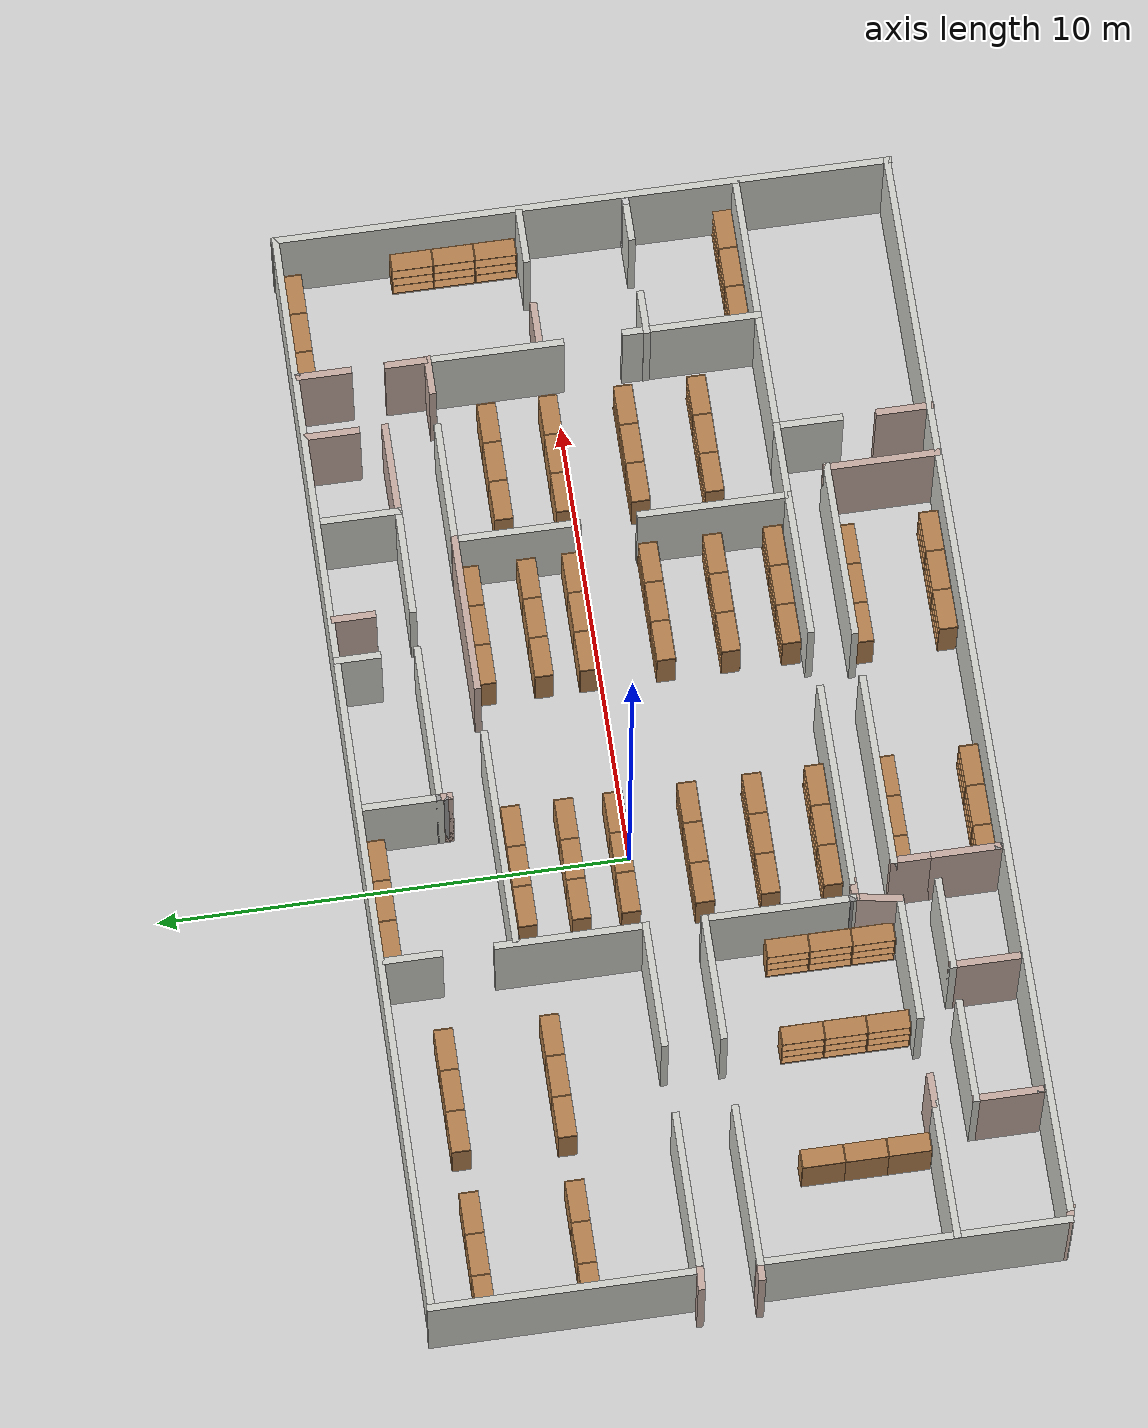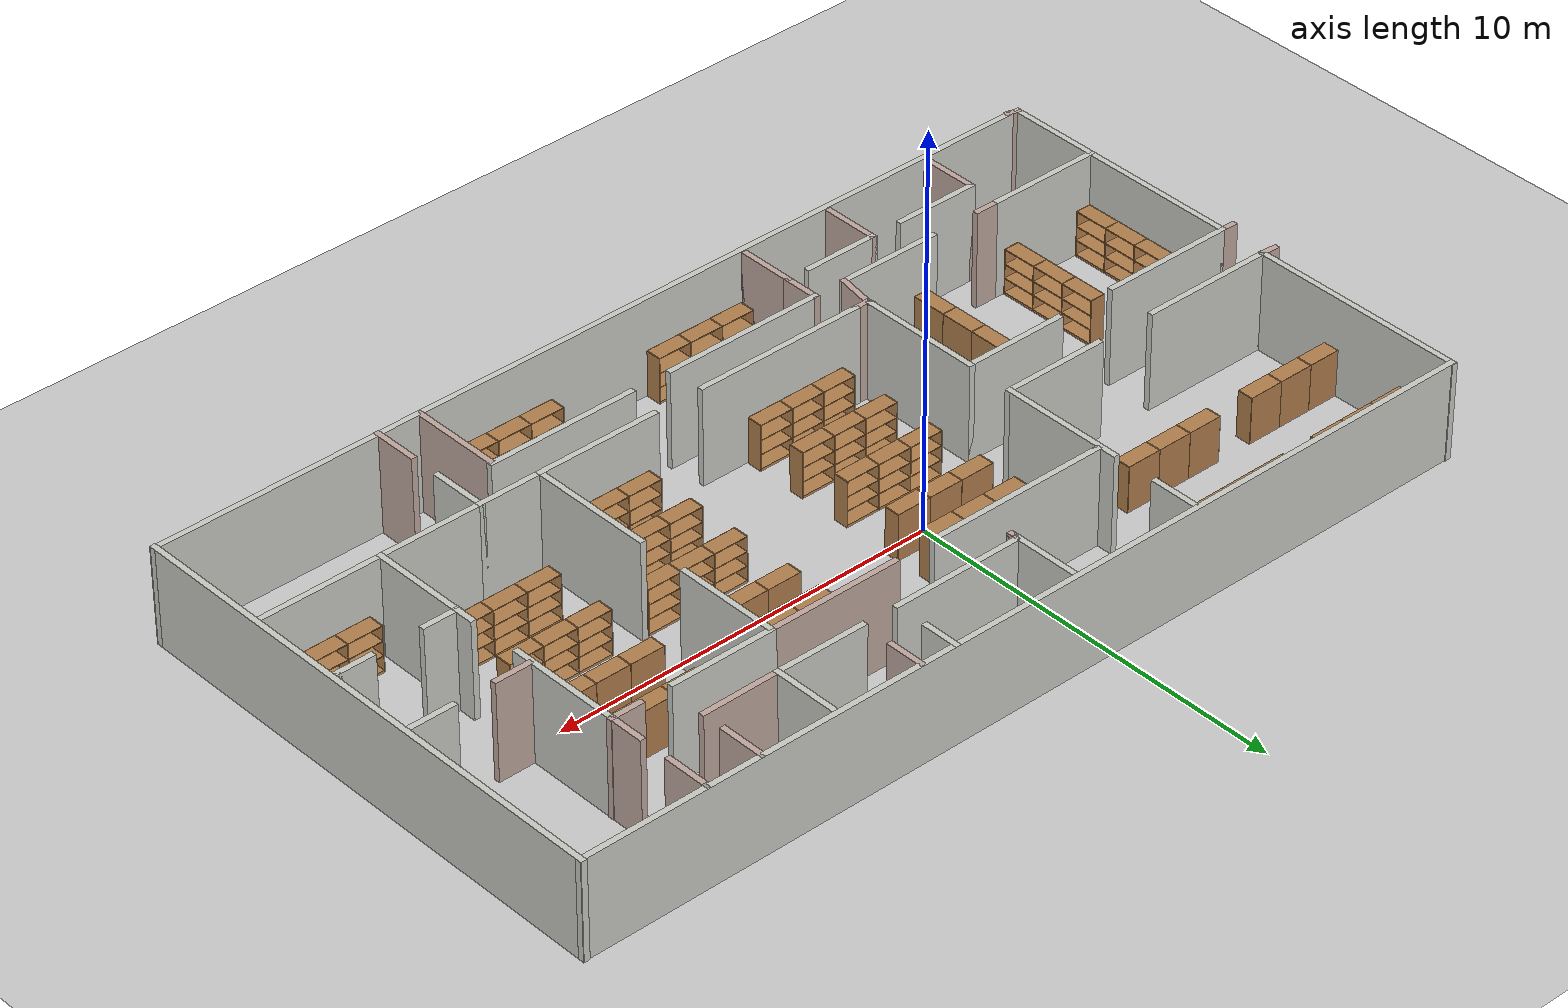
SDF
<sdf version="1.6">
 <world name="default">
  <light name="sun" type="directional">
   <pose>0 0 10 0 -0 0</pose>
   <diffuse>0.8 0.8 0.8 1</diffuse>
   <specular>0.2 0.2 0.2 1</specular>
   <attenuation>
    <range>1000</range>
    <constant>0.9</constant>
    <linear>0.01</linear>
    <quadratic>0.001</quadratic>
   </attenuation>
   <direction>-0.5 0.1 -0.9</direction>
  </light>
  <gravity>0 0 -9.8</gravity>
  <magnetic_field>6e-06 2.3e-05 -4.2e-05</magnetic_field>
  <atmosphere type="adiabatic"/>
  <physics name="default_physics" default="0" type="ode">
   <max_step_size>0.001</max_step_size>
   <real_time_factor>1</real_time_factor>
   <real_time_update_rate>1000</real_time_update_rate>
  </physics>
  <scene><ambient>0.4 0.4 0.4 1</ambient><background>0.7 0.7 0.7 1</background><shadows>1</shadows></scene>
  <audio><device>default</device></audio>
  <spherical_coordinates>
   <surface_model>EARTH_WGS84</surface_model>
   <latitude_deg>0</latitude_deg>
   <longitude_deg>0</longitude_deg>
   <elevation>0</elevation>
   <heading_deg>0</heading_deg>
  </spherical_coordinates>
  <model name="Untitled">
   <pose>1.90831 -1.04807 0 0 -0 0</pose>
   <link name="Wall_0">
    <collision name="Wall_0_Collision">
     <geometry><box><size>24 0.15 2.5</size></box></geometry>
     <pose>0 0 1.25 0 -0 0</pose>
    </collision>
    <visual name="Wall_0_Visual">
     <pose>0 0 1.25 0 -0 0</pose>
     <geometry><box><size>24 0.15 2.5</size></box></geometry>
     <material>
      <script><uri>file://media/materials/scripts/gazebo.material</uri><name>Gazebo/CeilingTiled</name></script>
      <ambient>0.760784 0.662745 0.627451 1</ambient>
     </material>
     <meta><layer>0</layer></meta>
    </visual>
    <pose>0.298836 -6.59916 0 0 -0 0</pose>
   </link>
   <link name="Wall_1">
    <collision name="Wall_1_Collision">
     <geometry><box><size>13.4119 0.15 2.5</size></box></geometry>
     <pose>0 0 1.25 0 -0 0</pose>
    </collision>
    <visual name="Wall_1_Visual">
     <pose>0 0 1.25 0 -0 0</pose>
     <geometry><box><size>13.4119 0.15 2.5</size></box></geometry>
     <material>
      <script><uri>file://media/materials/scripts/gazebo.material</uri><name>Gazebo/CeilingTiled</name></script>
      <ambient>0.760784 0.662745 0.627451 1</ambient>
     </material>
     <meta><layer>0</layer></meta>
    </visual>
    <pose>12.2238 0.008663 0 0 -0 1.5708</pose>
   </link>
   <link name="Wall_101">
    <collision name="Wall_101_Collision">
     <geometry><box><size>1 0.15 2.5</size></box></geometry>
     <pose>0 0 1.25 0 -0 0</pose>
    </collision>
    <visual name="Wall_101_Visual">
     <pose>0 0 1.25 0 -0 0</pose>
     <geometry><box><size>1 0.15 2.5</size></box></geometry>
     <material>
      <script><uri>file://media/materials/scripts/gazebo.material</uri><name>Gazebo/CeilingTiled</name></script>
      <ambient>0.760784 0.662745 0.627451 1</ambient>
     </material>
     <meta><layer>0</layer></meta>
    </visual>
    <pose>11.647 -0.916716 0 0 -0 0</pose>
   </link>
   <link name="Wall_102">
    <collision name="Wall_102_Collision">
     <geometry><box><size>0.15 0.15 2.5</size></box></geometry>
     <pose>0 0 1.25 0 -0 0</pose>
    </collision>
    <visual name="Wall_102_Visual">
     <pose>0 0 1.25 0 -0 0</pose>
     <geometry><box><size>0.15 0.15 2.5</size></box></geometry>
     <material>
      <script><uri>file://media/materials/scripts/gazebo.material</uri><name>Gazebo/LightGrey</name></script>
      <ambient>0.760784 0.662745 0.627451 1</ambient>
     </material>
     <meta><layer>0</layer></meta>
    </visual>
    <pose>12.072 -0.916716 0 0 -0 0</pose>
   </link>
   <link name="Wall_104">
    <collision name="Wall_104_Collision">
     <geometry><box><size>1 0.15 2.5</size></box></geometry>
     <pose>0 0 1.25 0 -0 0</pose>
    </collision>
    <visual name="Wall_104_Visual">
     <pose>0 0 1.25 0 -0 0</pose>
     <geometry><box><size>1 0.15 2.5</size></box></geometry>
     <material>
      <script><uri>file://media/materials/scripts/gazebo.material</uri><name>Gazebo/Grey</name></script>
      <ambient>0.760784 0.662745 0.627451 1</ambient>
     </material>
     <meta><layer>0</layer></meta>
    </visual>
    <pose>9.50731 1.37623 0 0 -0 0</pose>
   </link>
   <link name="Wall_106">
    <collision name="Wall_106_Collision">
     <geometry><box><size>1.25 0.15 2.5</size></box></geometry>
     <pose>0 0 1.25 0 -0 0</pose>
    </collision>
    <visual name="Wall_106_Visual">
     <pose>0 0 1.25 0 -0 0</pose>
     <geometry><box><size>1.25 0.15 2.5</size></box></geometry>
     <material>
      <script><uri>file://media/materials/scripts/gazebo.material</uri><name>Gazebo/CeilingTiled</name></script>
      <ambient>0.760784 0.662745 0.627451 1</ambient>
     </material>
     <meta><layer>0</layer></meta>
    </visual>
    <pose>11.5823 1.37623 0 0 -0 0</pose>
   </link>
   <link name="Wall_108">
    <collision name="Wall_108_Collision">
     <geometry><box><size>1 0.15 2.5</size></box></geometry>
     <pose>0 0 1.25 0 -0 0</pose>
    </collision>
    <visual name="Wall_108_Visual">
     <pose>0 0 1.25 0 -0 0</pose>
     <geometry><box><size>1 0.15 2.5</size></box></geometry>
     <material>
      <script><uri>file://media/materials/scripts/gazebo.material</uri><name>Gazebo/Grey</name></script>
      <ambient>0.760784 0.662745 0.627451 1</ambient>
     </material>
     <meta><layer>0</layer></meta>
    </visual>
    <pose>9.00455 4.21113 0 0 -0 1.5708</pose>
   </link>
   <link name="Wall_11">
    <collision name="Wall_11_Collision">
     <geometry><box><size>3.25 0.15 2.5</size></box></geometry>
     <pose>0 0 1.25 0 -0 0</pose>
    </collision>
    <visual name="Wall_11_Visual">
     <pose>0 0 1.25 0 -0 0</pose>
     <geometry><box><size>3.25 0.15 2.5</size></box></geometry>
     <material>
      <script><uri>file://media/materials/scripts/gazebo.material</uri><name>Gazebo/CeilingTiled</name></script>
      <ambient>0.760784 0.662745 0.627451 1</ambient>
     </material>
     <meta><layer>0</layer></meta>
    </visual>
    <pose>-4.31073 2.62935 0 0 -0 -1.5708</pose>
   </link>
   <link name="Wall_110">
    <collision name="Wall_110_Collision">
     <geometry><box><size>1.25 0.15 2.5</size></box></geometry>
     <pose>0 0 1.25 0 -0 0</pose>
    </collision>
    <visual name="Wall_110_Visual">
     <pose>0 0 1.25 0 -0 0</pose>
     <geometry><box><size>1.25 0.15 2.5</size></box></geometry>
     <material>
      <script><uri>file://media/materials/scripts/gazebo.material</uri><name>Gazebo/Grey</name></script>
      <ambient>0.760784 0.662745 0.627451 1</ambient>
     </material>
     <meta><layer>0</layer></meta>
    </visual>
    <pose>9.00455 6.03613 0 0 -0 1.5708</pose>
   </link>
   <link name="Wall_111">
    <collision name="Wall_111_Collision">
     <geometry><box><size>0.15 0.15 2.5</size></box></geometry>
     <pose>0 0 1.25 0 -0 0</pose>
    </collision>
    <visual name="Wall_111_Visual">
     <pose>0 0 1.25 0 -0 0</pose>
     <geometry><box><size>0.15 0.15 2.5</size></box></geometry>
     <material>
      <script><uri>file://media/materials/scripts/gazebo.material</uri><name>Gazebo/Grey</name></script>
      <ambient>1 1 1 1</ambient>
     </material>
     <meta><layer>0</layer></meta>
    </visual>
    <pose>9.00455 6.58613 0 0 -0 0</pose>
   </link>
   <link name="Wall_113">
    <collision name="Wall_113_Collision">
     <geometry><box><size>1 0.15 2.5</size></box></geometry>
     <pose>0 0 1.25 0 -0 0</pose>
    </collision>
    <visual name="Wall_113_Visual">
     <pose>0 0 1.25 0 -0 0</pose>
     <geometry><box><size>1 0.15 2.5</size></box></geometry>
     <material>
      <script><uri>file://media/materials/scripts/gazebo.material</uri><name>Gazebo/Grey</name></script>
      <ambient>0.760784 0.662745 0.627451 1</ambient>
     </material>
     <meta><layer>0</layer></meta>
    </visual>
    <pose>3.39016 6.16065 0 0 -0 -1.5708</pose>
   </link>
   <link name="Wall_115">
    <collision name="Wall_115_Collision">
     <geometry><box><size>2.4023 0.15 2.5</size></box></geometry>
     <pose>0 0 1.25 0 -0 0</pose>
    </collision>
    <visual name="Wall_115_Visual">
     <pose>0 0 1.25 0 -0 0</pose>
     <geometry><box><size>2.4023 0.15 2.5</size></box></geometry>
     <material>
      <script><uri>file://media/materials/scripts/gazebo.material</uri><name>Gazebo/CeilingTiled</name></script>
      <ambient>0.760784 0.662745 0.627451 1</ambient>
     </material>
     <meta><layer>0</layer></meta>
    </visual>
    <pose>4.5163 4.87991 0 0 -0 -0.005095</pose>
   </link>
   <link name="Wall_116">
    <collision name="Wall_116_Collision">
     <geometry><box><size>1.75 0.15 2.5</size></box></geometry>
     <pose>0 0 1.25 0 -0 0</pose>
    </collision>
    <visual name="Wall_116_Visual">
     <pose>0 0 1.25 0 -0 0</pose>
     <geometry><box><size>1.75 0.15 2.5</size></box></geometry>
     <material>
      <script><uri>file://media/materials/scripts/gazebo.material</uri><name>Gazebo/CeilingTiled</name></script>
      <ambient>0.760784 0.662745 0.627451 1</ambient>
     </material>
     <meta><layer>0</layer></meta>
    </visual>
    <pose>5.64243 5.67417 0 0 -0 1.5708</pose>
   </link>
   <link name="Wall_12">
    <collision name="Wall_12_Collision">
     <geometry><box><size>2.75 0.15 2.5</size></box></geometry>
     <pose>0 0 1.25 0 -0 0</pose>
    </collision>
    <visual name="Wall_12_Visual">
     <pose>0 0 1.25 0 -0 0</pose>
     <geometry><box><size>2.75 0.15 2.5</size></box></geometry>
     <material>
      <script><uri>file://media/materials/scripts/gazebo.material</uri><name>Gazebo/CeilingTiled</name></script>
      <ambient>0.760784 0.662745 0.627451 1</ambient>
     </material>
     <meta><layer>0</layer></meta>
    </visual>
    <pose>-5.61073 1.07935 0 0 -0 3.14159</pose>
   </link>
   <link name="Wall_121">
    <collision name="Wall_121_Collision">
     <geometry><box><size>2.09776 0.15 2.5</size></box></geometry>
     <pose>0 0 1.25 0 -0 0</pose>
    </collision>
    <visual name="Wall_121_Visual">
     <pose>0 0 1.25 0 -0 0</pose>
     <geometry><box><size>2.09776 0.15 2.5</size></box></geometry>
     <material>
      <script><uri>file://media/materials/scripts/gazebo.material</uri><name>Gazebo/Grey</name></script>
      <ambient>0.760784 0.662745 0.627451 1</ambient>
     </material>
     <meta><layer>0</layer></meta>
    </visual>
    <pose>6.6163 4.87991 0 0 -0 0.005892</pose>
   </link>
   <link name="Wall_123">
    <collision name="Wall_123_Collision">
     <geometry><box><size>1.25 0.15 2.5</size></box></geometry>
     <pose>0 0 1.25 0 -0 0</pose>
    </collision>
    <visual name="Wall_123_Visual">
     <pose>0 0 1.25 0 -0 0</pose>
     <geometry><box><size>1.25 0.15 2.5</size></box></geometry>
     <material>
      <script><uri>file://media/materials/scripts/gazebo.material</uri><name>Gazebo/Grey</name></script>
      <ambient>0.760784 0.662745 0.627451 1</ambient>
     </material>
     <meta><layer>0</layer></meta>
    </visual>
    <pose>7.60448 6.05576 0 0 -0 1.5708</pose>
   </link>
   <link name="Wall_14">
    <collision name="Wall_14_Collision">
     <geometry><box><size>3.5 0.15 2.5</size></box></geometry>
     <pose>0 0 1.25 0 -0 0</pose>
    </collision>
    <visual name="Wall_14_Visual">
     <pose>0 0 1.25 0 -0 0</pose>
     <geometry><box><size>3.5 0.15 2.5</size></box></geometry>
     <material>
      <script><uri>file://media/materials/scripts/gazebo.material</uri><name>Gazebo/CeilingTiled</name></script>
      <ambient>0.760784 0.662745 0.627451 1</ambient>
     </material>
     <meta><layer>0</layer></meta>
    </visual>
    <pose>-10.1857 1.07935 0 0 -0 3.14159</pose>
   </link>
   <link name="Wall_16">
    <collision name="Wall_16_Collision">
     <geometry><box><size>1.25 0.15 2.5</size></box></geometry>
     <pose>0 0 1.25 0 -0 0</pose>
    </collision>
    <visual name="Wall_16_Visual">
     <pose>0 0 1.25 0 -0 0</pose>
     <geometry><box><size>1.25 0.15 2.5</size></box></geometry>
     <material>
      <script><uri>file://media/materials/scripts/gazebo.material</uri><name>Gazebo/CeilingTiled</name></script>
      <ambient>0.760784 0.662745 0.627451 1</ambient>
     </material>
     <meta><layer>0</layer></meta>
    </visual>
    <pose>-4.31073 5.95527 0 0 -0 1.5708</pose>
   </link>
   <link name="Wall_2">
    <collision name="Wall_2_Collision">
     <geometry><box><size>24.25 0.15 2.5</size></box></geometry>
     <pose>0 0 1.25 0 -0 0</pose>
    </collision>
    <visual name="Wall_2_Visual">
     <pose>0 0 1.25 0 -0 0</pose>
     <geometry><box><size>24.25 0.15 2.5</size></box></geometry>
     <material>
      <script><uri>file://media/materials/scripts/gazebo.material</uri><name>Gazebo/CeilingTiled</name></script>
      <ambient>0.760784 0.662745 0.627451 1</ambient>
     </material>
     <meta><layer>0</layer></meta>
    </visual>
    <pose>0.173836 6.61649 0 0 -0 3.14159</pose>
   </link>
   <link name="Wall_20">
    <collision name="Wall_20_Collision">
     <geometry><box><size>3.25 0.15 2.5</size></box></geometry>
     <pose>0 0 1.25 0 -0 0</pose>
    </collision>
    <visual name="Wall_20_Visual">
     <pose>0 0 1.25 0 -0 0</pose>
     <geometry><box><size>3.25 0.15 2.5</size></box></geometry>
     <material>
      <script><uri>file://media/materials/scripts/gazebo.material</uri><name>Gazebo/CeilingTiled</name></script>
      <ambient>0.760784 0.662745 0.627451 1</ambient>
     </material>
     <meta><layer>0</layer></meta>
    </visual>
    <pose>3.28553 -3.31387 0 0 -0 3.14159</pose>
   </link>
   <link name="Wall_22">
    <collision name="Wall_22_Collision">
     <geometry><box><size>4.5 0.15 2.5</size></box></geometry>
     <pose>0 0 1.25 0 -0 0</pose>
    </collision>
    <visual name="Wall_22_Visual">
     <pose>0 0 1.25 0 -0 0</pose>
     <geometry><box><size>4.5 0.15 2.5</size></box></geometry>
     <material>
      <script><uri>file://media/materials/scripts/gazebo.material</uri><name>Gazebo/CeilingTiled</name></script>
      <ambient>0.760784 0.662745 0.627451 1</ambient>
     </material>
     <meta><layer>0</layer></meta>
    </visual>
    <pose>-1.78947 -3.31387 0 0 -0 3.14159</pose>
   </link>
   <link name="Wall_26">
    <collision name="Wall_26_Collision">
     <geometry><box><size>3.5 0.15 2.5</size></box></geometry>
     <pose>0 0 1.25 0 -0 0</pose>
    </collision>
    <visual name="Wall_26_Visual">
     <pose>0 0 1.25 0 -0 0</pose>
     <geometry><box><size>3.5 0.15 2.5</size></box></geometry>
     <material>
      <script><uri>file://media/materials/scripts/gazebo.material</uri><name>Gazebo/CeilingTiled</name></script>
      <ambient>0.760784 0.662745 0.627451 1</ambient>
     </material>
     <meta><layer>0</layer></meta>
    </visual>
    <pose>-10.2012 -0.152902 0 0 -0 0</pose>
   </link>
   <link name="Wall_28">
    <collision name="Wall_28_Collision">
     <geometry><box><size>2.75 0.15 2.5</size></box></geometry>
     <pose>0 0 1.25 0 -0 0</pose>
    </collision>
    <visual name="Wall_28_Visual">
     <pose>0 0 1.25 0 -0 0</pose>
     <geometry><box><size>2.75 0.15 2.5</size></box></geometry>
     <material>
      <script><uri>file://media/materials/scripts/gazebo.material</uri><name>Gazebo/CeilingTiled</name></script>
      <ambient>0.760784 0.662745 0.627451 1</ambient>
     </material>
     <meta><layer>0</layer></meta>
    </visual>
    <pose>-5.62616 -0.152902 0 0 -0 0</pose>
   </link>
   <link name="Wall_29">
    <collision name="Wall_29_Collision">
     <geometry><box><size>3.25 0.15 2.5</size></box></geometry>
     <pose>0 0 1.25 0 -0 0</pose>
    </collision>
    <visual name="Wall_29_Visual">
     <pose>0 0 1.25 0 -0 0</pose>
     <geometry><box><size>3.25 0.15 2.5</size></box></geometry>
     <material>
      <script><uri>file://media/materials/scripts/gazebo.material</uri><name>Gazebo/CeilingTiled</name></script>
      <ambient>0.760784 0.662745 0.627451 1</ambient>
     </material>
     <meta><layer>0</layer></meta>
    </visual>
    <pose>-4.32616 -1.7029 0 0 -0 -1.5708</pose>
   </link>
   <link name="Wall_30">
    <collision name="Wall_30_Collision">
     <geometry><box><size>0.21208 0.15 2.5</size></box></geometry>
     <pose>0 0 1.25 0 -0 0</pose>
    </collision>
    <visual name="Wall_30_Visual">
     <pose>0 0 1.25 0 -0 0</pose>
     <geometry><box><size>0.21208 0.15 2.5</size></box></geometry>
     <material>
      <script><uri>file://media/materials/scripts/gazebo.material</uri><name>Gazebo/Grey</name></script>
      <ambient>1 1 1 1</ambient>
     </material>
     <meta><layer>0</layer></meta>
    </visual>
    <pose>-4.32032 -3.28339 0 0 -0 -1.38131</pose>
   </link>
   <link name="Wall_31">
    <collision name="Wall_31_Collision">
     <geometry><box><size>0.5 0.15 2.5</size></box></geometry>
     <pose>0 0 1.25 0 -0 0</pose>
    </collision>
    <visual name="Wall_31_Visual">
     <pose>0 0 1.25 0 -0 0</pose>
     <geometry><box><size>0.5 0.15 2.5</size></box></geometry>
     <material>
      <script><uri>file://media/materials/scripts/gazebo.material</uri><name>Gazebo/Grey</name></script>
      <ambient>0.760784 0.662745 0.627451 1</ambient>
     </material>
     <meta><layer>0</layer></meta>
    </visual>
    <pose>-4.13947 -3.31387 0 0 -0 0</pose>
   </link>
   <link name="Wall_32">
    <collision name="Wall_32_Collision">
     <geometry><box><size>0.15 0.15 2.5</size></box></geometry>
     <pose>0 0 1.25 0 -0 0</pose>
    </collision>
    <visual name="Wall_32_Visual">
     <pose>0 0 1.25 0 -0 0</pose>
     <geometry><box><size>0.15 0.15 2.5</size></box></geometry>
     <material>
      <script><uri>file://media/materials/scripts/gazebo.material</uri><name>Gazebo/Grey</name></script>
      <ambient>0.760784 0.662745 0.627451 1</ambient>
     </material>
     <meta><layer>0</layer></meta>
    </visual>
    <pose>-3.96447 -3.31387 0 0 -0 0</pose>
   </link>
   <link name="Wall_34">
    <collision name="Wall_34_Collision">
     <geometry><box><size>3 0.15 2.5</size></box></geometry>
     <pose>0 0 1.25 0 -0 0</pose>
    </collision>
    <visual name="Wall_34_Visual">
     <pose>0 0 1.25 0 -0 0</pose>
     <geometry><box><size>3 0.15 2.5</size></box></geometry>
     <material>
      <script><uri>file://media/materials/scripts/gazebo.material</uri><name>Gazebo/CeilingTiled</name></script>
      <ambient>0.760784 0.662745 0.627451 1</ambient>
     </material>
     <meta><layer>0</layer></meta>
    </visual>
    <pose>-10.4466 -4.22363 0 0 -0 0</pose>
   </link>
   <link name="Wall_36">
    <collision name="Wall_36_Collision">
     <geometry><box><size>1.5 0.15 2.5</size></box></geometry>
     <pose>0 0 1.25 0 -0 0</pose>
    </collision>
    <visual name="Wall_36_Visual">
     <pose>0 0 1.25 0 -0 0</pose>
     <geometry><box><size>1.5 0.15 2.5</size></box></geometry>
     <material>
      <script><uri>file://media/materials/scripts/gazebo.material</uri><name>Gazebo/Grey</name></script>
      <ambient>0.760784 0.662745 0.627451 1</ambient>
     </material>
     <meta><layer>0</layer></meta>
    </visual>
    <pose>-9.02159 -5.74864 0 0 -0 -1.5708</pose>
   </link>
   <link name="Wall_37">
    <collision name="Wall_37_Collision">
     <geometry><box><size>0.15 0.15 2.5</size></box></geometry>
     <pose>0 0 1.25 0 -0 0</pose>
    </collision>
    <visual name="Wall_37_Visual">
     <pose>0 0 1.25 0 -0 0</pose>
     <geometry><box><size>0.15 0.15 2.5</size></box></geometry>
     <material>
      <script><uri>file://media/materials/scripts/gazebo.material</uri><name>Gazebo/Grey</name></script>
      <ambient>1 1 1 1</ambient>
     </material>
     <meta><layer>0</layer></meta>
    </visual>
    <pose>-9.02159 -6.42363 0 0 -0 0</pose>
   </link>
   <link name="Wall_39">
    <collision name="Wall_39_Collision">
     <geometry><box><size>0.75 0.15 2.5</size></box></geometry>
     <pose>0 0 1.25 0 -0 0</pose>
    </collision>
    <visual name="Wall_39_Visual">
     <pose>0 0 1.25 0 -0 0</pose>
     <geometry><box><size>0.75 0.15 2.5</size></box></geometry>
     <material>
      <script><uri>file://media/materials/scripts/gazebo.material</uri><name>Gazebo/Grey</name></script>
      <ambient>0.760784 0.662745 0.627451 1</ambient>
     </material>
     <meta><layer>0</layer></meta>
    </visual>
    <pose>-8.72159 -4.22363 0 0 -0 0</pose>
   </link>
   <link name="Wall_4">
    <collision name="Wall_4_Collision">
     <geometry><box><size>0.409452 0.15 2.5</size></box></geometry>
     <pose>0 0 1.25 0 -0 0</pose>
    </collision>
    <visual name="Wall_4_Visual">
     <pose>0 0 1.25 0 -0 0</pose>
     <geometry><box><size>0.409452 0.15 2.5</size></box></geometry>
     <material>
      <script><uri>file://media/materials/scripts/gazebo.material</uri><name>Gazebo/Grey</name></script>
      <ambient>0.760784 0.662745 0.627451 1</ambient>
     </material>
     <meta><layer>0</layer></meta>
    </visual>
    <pose>-11.7512 -6.5876 0 0 -0 -0.270751</pose>
   </link>
   <link name="Wall_41">
    <collision name="Wall_41_Collision">
     <geometry><box><size>2.75 0.15 2.5</size></box></geometry>
     <pose>0 0 1.25 0 -0 0</pose>
    </collision>
    <visual name="Wall_41_Visual">
     <pose>0 0 1.25 0 -0 0</pose>
     <geometry><box><size>2.75 0.15 2.5</size></box></geometry>
     <material>
      <script><uri>file://media/materials/scripts/gazebo.material</uri><name>Gazebo/CeilingTiled</name></script>
      <ambient>0.760784 0.662745 0.627451 1</ambient>
     </material>
     <meta><layer>0</layer></meta>
    </visual>
    <pose>-5.77159 -4.22363 0 0 -0 0</pose>
   </link>
   <link name="Wall_42">
    <collision name="Wall_42_Collision">
     <geometry><box><size>1.07323 0.15 2.5</size></box></geometry>
     <pose>0 0 1.25 0 -0 0</pose>
    </collision>
    <visual name="Wall_42_Visual">
     <pose>0 0 1.25 0 -0 0</pose>
     <geometry><box><size>1.07323 0.15 2.5</size></box></geometry>
     <material>
      <script><uri>file://media/materials/scripts/gazebo.material</uri><name>Gazebo/Grey</name></script>
      <ambient>0.760784 0.662745 0.627451 1</ambient>
     </material>
     <meta><layer>0</layer></meta>
    </visual>
    <pose>-4.39303 -3.76875 0 0 -0 1.39978</pose>
   </link>
   <link name="Wall_43">
    <collision name="Wall_43_Collision">
     <geometry><box><size>0.15 0.15 2.5</size></box></geometry>
     <pose>0 0 1.25 0 -0 0</pose>
    </collision>
    <visual name="Wall_43_Visual">
     <pose>0 0 1.25 0 -0 0</pose>
     <geometry><box><size>0.15 0.15 2.5</size></box></geometry>
     <material>
      <script><uri>file://media/materials/scripts/gazebo.material</uri><name>Gazebo/Grey</name></script>
      <ambient>1 1 1 1</ambient>
     </material>
     <meta><layer>0</layer></meta>
    </visual>
    <pose>-4.31447 -3.31387 0 0 -0 0</pose>
   </link>
   <link name="Wall_45">
    <collision name="Wall_45_Collision">
     <geometry><box><size>2.25 0.15 2.5</size></box></geometry>
     <pose>0 0 1.25 0 -0 0</pose>
    </collision>
    <visual name="Wall_45_Visual">
     <pose>0 0 1.25 0 -0 0</pose>
     <geometry><box><size>2.25 0.15 2.5</size></box></geometry>
     <material>
      <script><uri>file://media/materials/scripts/gazebo.material</uri><name>Gazebo/CeilingTiled</name></script>
      <ambient>0.760784 0.662745 0.627451 1</ambient>
     </material>
     <meta><layer>0</layer></meta>
    </visual>
    <pose>-7.97159 -5.07364 0 0 -0 0</pose>
   </link>
   <link name="Wall_47">
    <collision name="Wall_47_Collision">
     <geometry><box><size>1.5 0.15 2.5</size></box></geometry>
     <pose>0 0 1.25 0 -0 0</pose>
    </collision>
    <visual name="Wall_47_Visual">
     <pose>0 0 1.25 0 -0 0</pose>
     <geometry><box><size>1.5 0.15 2.5</size></box></geometry>
     <material>
      <script><uri>file://media/materials/scripts/gazebo.material</uri><name>Gazebo/Grey</name></script>
      <ambient>0.760784 0.662745 0.627451 1</ambient>
     </material>
     <meta><layer>0</layer></meta>
    </visual>
    <pose>-6.07159 -5.74864 0 0 -0 -1.5708</pose>
   </link>
   <link name="Wall_49">
    <collision name="Wall_49_Collision">
     <geometry><box><size>2 0.15 2.5</size></box></geometry>
     <pose>0 0 1.25 0 -0 0</pose>
    </collision>
    <visual name="Wall_49_Visual">
     <pose>0 0 1.25 0 -0 0</pose>
     <geometry><box><size>2 0.15 2.5</size></box></geometry>
     <material>
      <script><uri>file://media/materials/scripts/gazebo.material</uri><name>Gazebo/CeilingTiled</name></script>
      <ambient>0.760784 0.662745 0.627451 1</ambient>
     </material>
     <meta><layer>0</layer></meta>
    </visual>
    <pose>-5.14659 -5.07364 0 0 -0 0</pose>
   </link>
   <link name="Wall_51">
    <collision name="Wall_51_Collision">
     <geometry><box><size>1.5 0.15 2.5</size></box></geometry>
     <pose>0 0 1.25 0 -0 0</pose>
    </collision>
    <visual name="Wall_51_Visual">
     <pose>0 0 1.25 0 -0 0</pose>
     <geometry><box><size>1.5 0.15 2.5</size></box></geometry>
     <material>
      <script><uri>file://media/materials/scripts/gazebo.material</uri><name>Gazebo/Grey</name></script>
      <ambient>0.760784 0.662745 0.627451 1</ambient>
     </material>
     <meta><layer>0</layer></meta>
    </visual>
    <pose>-3.62159 -5.74864 0 0 -0 -1.5708</pose>
   </link>
   <link name="Wall_52">
    <collision name="Wall_52_Collision">
     <geometry><box><size>0.15 0.15 2.5</size></box></geometry>
     <pose>0 0 1.25 0 -0 0</pose>
    </collision>
    <visual name="Wall_52_Visual">
     <pose>0 0 1.25 0 -0 0</pose>
     <geometry><box><size>0.15 0.15 2.5</size></box></geometry>
     <material>
      <script><uri>file://media/materials/scripts/gazebo.material</uri><name>Gazebo/Grey</name></script>
      <ambient>1 1 1 1</ambient>
     </material>
     <meta><layer>0</layer></meta>
    </visual>
    <pose>-3.62159 -6.42363 0 0 -0 0</pose>
   </link>
   <link name="Wall_54">
    <collision name="Wall_54_Collision">
     <geometry><box><size>1 0.15 2.5</size></box></geometry>
     <pose>0 0 1.25 0 -0 0</pose>
    </collision>
    <visual name="Wall_54_Visual">
     <pose>0 0 1.25 0 -0 0</pose>
     <geometry><box><size>1 0.15 2.5</size></box></geometry>
     <material>
      <script><uri>file://media/materials/scripts/gazebo.material</uri><name>Gazebo/Grey</name></script>
      <ambient>0.760784 0.662745 0.627451 1</ambient>
     </material>
     <meta><layer>0</layer></meta>
    </visual>
    <pose>-3.62159 -4.64863 0 0 -0 1.5708</pose>
   </link>
   <link name="Wall_55">
    <collision name="Wall_55_Collision">
     <geometry><box><size>4.25 0.15 2.5</size></box></geometry>
     <pose>0 0 1.25 0 -0 0</pose>
    </collision>
    <visual name="Wall_55_Visual">
     <pose>0 0 1.25 0 -0 0</pose>
     <geometry><box><size>4.25 0.15 2.5</size></box></geometry>
     <material>
      <script><uri>file://media/materials/scripts/gazebo.material</uri><name>Gazebo/CeilingTiled</name></script>
      <ambient>0.760784 0.662745 0.627451 1</ambient>
     </material>
     <meta><layer>0</layer></meta>
    </visual>
    <pose>-1.57159 -4.22363 0 0 -0 0</pose>
   </link>
   <link name="Wall_57">
    <collision name="Wall_57_Collision">
     <geometry><box><size>3.93948 0.15 2.5</size></box></geometry>
     <pose>0 0 1.25 0 -0 0</pose>
    </collision>
    <visual name="Wall_57_Visual">
     <pose>0 0 1.25 0 -0 0</pose>
     <geometry><box><size>3.93948 0.15 2.5</size></box></geometry>
     <material>
      <script><uri>file://media/materials/scripts/gazebo.material</uri><name>Gazebo/CeilingTiled</name></script>
      <ambient>0.760784 0.662745 0.627451 1</ambient>
     </material>
     <meta><layer>0</layer></meta>
    </visual>
    <pose>3.47316 -4.22363 0 0 -0 0</pose>
   </link>
   <link name="Wall_58">
    <collision name="Wall_58_Collision">
     <geometry><box><size>2.5 0.15 2.5</size></box></geometry>
     <pose>0 0 1.25 0 -0 0</pose>
    </collision>
    <visual name="Wall_58_Visual">
     <pose>0 0 1.25 0 -0 0</pose>
     <geometry><box><size>2.5 0.15 2.5</size></box></geometry>
     <material>
      <script><uri>file://media/materials/scripts/gazebo.material</uri><name>Gazebo/Grey</name></script>
      <ambient>0.760784 0.662745 0.627451 1</ambient>
     </material>
     <meta><layer>0</layer></meta>
    </visual>
    <pose>5.34476 -5.39863 0 0 -0 -1.5708</pose>
   </link>
   <link name="Wall_60">
    <collision name="Wall_60_Collision">
     <geometry><box><size>3.5 0.15 2.5</size></box></geometry>
     <pose>0 0 1.25 0 -0 0</pose>
    </collision>
    <visual name="Wall_60_Visual">
     <pose>0 0 1.25 0 -0 0</pose>
     <geometry><box><size>3.5 0.15 2.5</size></box></geometry>
     <material>
      <script><uri>file://media/materials/scripts/gazebo.material</uri><name>Gazebo/Grey</name></script>
      <ambient>0.760784 0.662745 0.627451 1</ambient>
     </material>
     <meta><layer>0</layer></meta>
    </visual>
    <pose>3.16053 3.78613 0 0 -0 3.14159</pose>
   </link>
   <link name="Wall_62">
    <collision name="Wall_62_Collision">
     <geometry><box><size>4.75 0.15 2.5</size></box></geometry>
     <pose>0 0 1.25 0 -0 0</pose>
    </collision>
    <visual name="Wall_62_Visual">
     <pose>0 0 1.25 0 -0 0</pose>
     <geometry><box><size>4.75 0.15 2.5</size></box></geometry>
     <material>
      <script><uri>file://media/materials/scripts/gazebo.material</uri><name>Gazebo/CeilingTiled</name></script>
      <ambient>0.760784 0.662745 0.627451 1</ambient>
     </material>
     <meta><layer>0</layer></meta>
    </visual>
    <pose>-1.91447 3.78613 0 0 -0 3.14159</pose>
   </link>
   <link name="Wall_63">
    <collision name="Wall_63_Collision">
     <geometry><box><size>0.15 0.15 2.5</size></box></geometry>
     <pose>0 0 1.25 0 -0 0</pose>
    </collision>
    <visual name="Wall_63_Visual">
     <pose>0 0 1.25 0 -0 0</pose>
     <geometry><box><size>0.15 0.15 2.5</size></box></geometry>
     <material>
      <script><uri>file://media/materials/scripts/gazebo.material</uri><name>Gazebo/Grey</name></script>
      <ambient>1 1 1 1</ambient>
     </material>
     <meta><layer>0</layer></meta>
    </visual>
    <pose>-4.21447 3.78613 0 0 -0 0</pose>
   </link>
   <link name="Wall_65">
    <collision name="Wall_65_Collision">
     <geometry><box><size>0.508533 0.15 2.5</size></box></geometry>
     <pose>0 0 1.25 0 -0 0</pose>
    </collision>
    <visual name="Wall_65_Visual">
     <pose>0 0 1.25 0 -0 0</pose>
     <geometry><box><size>0.508533 0.15 2.5</size></box></geometry>
     <material>
      <script><uri>file://media/materials/scripts/gazebo.material</uri><name>Gazebo/Grey</name></script>
      <ambient>0.760784 0.662745 0.627451 1</ambient>
     </material>
     <meta><layer>0</layer></meta>
    </visual>
    <pose>-12.0394 1.09353 0 0 -0 -0.079165</pose>
   </link>
   <link name="Wall_66">
    <collision name="Wall_66_Collision">
     <geometry><box><size>0.15 0.15 2.5</size></box></geometry>
     <pose>0 0 1.25 0 -0 0</pose>
    </collision>
    <visual name="Wall_66_Visual">
     <pose>0 0 1.25 0 -0 0</pose>
     <geometry><box><size>0.15 0.15 2.5</size></box></geometry>
     <material>
      <script><uri>file://media/materials/scripts/gazebo.material</uri><name>Gazebo/Grey</name></script>
      <ambient>1 1 1 1</ambient>
     </material>
     <meta><layer>0</layer></meta>
    </visual>
    <pose>-11.8607 1.07935 0 0 -0 0</pose>
   </link>
   <link name="Wall_68">
    <collision name="Wall_68_Collision">
     <geometry><box><size>0.465549 0.15 2.5</size></box></geometry>
     <pose>0 0 1.25 0 -0 0</pose>
    </collision>
    <visual name="Wall_68_Visual">
     <pose>0 0 1.25 0 -0 0</pose>
     <geometry><box><size>0.465549 0.15 2.5</size></box></geometry>
     <material>
      <script><uri>file://media/materials/scripts/gazebo.material</uri><name>Gazebo/Grey</name></script>
      <ambient>0.760784 0.662745 0.627451 1</ambient>
     </material>
     <meta><layer>0</layer></meta>
    </visual>
    <pose>-12.0339 -0.147704 0 0 -0 -0.03295</pose>
   </link>
   <link name="Wall_7">
    <collision name="Wall_7_Collision">
     <geometry><box><size>5.59252 0.15 2.5</size></box></geometry>
     <pose>0 0 1.25 0 -0 0</pose>
    </collision>
    <visual name="Wall_7_Visual">
     <pose>0 0 1.25 0 -0 0</pose>
     <geometry><box><size>5.59252 0.15 2.5</size></box></geometry>
     <material>
      <script><uri>file://media/materials/scripts/gazebo.material</uri><name>Gazebo/CeilingTiled</name></script>
      <ambient>0.760784 0.662745 0.627451 1</ambient>
     </material>
     <meta><layer>0</layer></meta>
    </visual>
    <pose>-11.8762 3.91836 0 0 -0 -1.5708</pose>
   </link>
   <link name="Wall_70">
    <collision name="Wall_70_Collision">
     <geometry><box><size>1.75 0.15 2.5</size></box></geometry>
     <pose>0 0 1.25 0 -0 0</pose>
    </collision>
    <visual name="Wall_70_Visual">
     <pose>0 0 1.25 0 -0 0</pose>
     <geometry><box><size>1.75 0.15 2.5</size></box></geometry>
     <material>
      <script><uri>file://media/materials/scripts/gazebo.material</uri><name>Gazebo/CeilingTiled</name></script>
      <ambient>0.760784 0.662745 0.627451 1</ambient>
     </material>
     <meta><layer>0</layer></meta>
    </visual>
    <pose>-0.886456 5.70754 0 0 -0 -1.5708</pose>
   </link>
   <link name="Wall_71">
    <collision name="Wall_71_Collision">
     <geometry><box><size>0.15 0.15 2.5</size></box></geometry>
     <pose>0 0 1.25 0 -0 0</pose>
    </collision>
    <visual name="Wall_71_Visual">
     <pose>0 0 1.25 0 -0 0</pose>
     <geometry><box><size>0.15 0.15 2.5</size></box></geometry>
     <material>
      <script><uri>file://media/materials/scripts/gazebo.material</uri><name>Gazebo/Grey</name></script>
      <ambient>1 1 1 1</ambient>
     </material>
     <meta><layer>0</layer></meta>
    </visual>
    <pose>-0.886456 4.90754 0 0 -0 0</pose>
   </link>
   <link name="Wall_72">
    <collision name="Wall_72_Collision">
     <geometry><box><size>3.5 0.15 2.5</size></box></geometry>
     <pose>0 0 1.25 0 -0 0</pose>
    </collision>
    <visual name="Wall_72_Visual">
     <pose>0 0 1.25 0 -0 0</pose>
     <geometry><box><size>3.5 0.15 2.5</size></box></geometry>
     <material>
      <script><uri>file://media/materials/scripts/gazebo.material</uri><name>Gazebo/CeilingTiled</name></script>
      <ambient>0.760784 0.662745 0.627451 1</ambient>
     </material>
     <meta><layer>0</layer></meta>
    </visual>
    <pose>0.788544 4.90754 0 0 -0 0</pose>
   </link>
   <link name="Wall_74">
    <collision name="Wall_74_Collision">
     <geometry><box><size>1 0.15 2.5</size></box></geometry>
     <pose>0 0 1.25 0 -0 0</pose>
    </collision>
    <visual name="Wall_74_Visual">
     <pose>0 0 1.25 0 -0 0</pose>
     <geometry><box><size>1 0.15 2.5</size></box></geometry>
     <material>
      <script><uri>file://media/materials/scripts/gazebo.material</uri><name>Gazebo/CeilingTiled</name></script>
      <ambient>0.760784 0.662745 0.627451 1</ambient>
     </material>
     <meta><layer>0</layer></meta>
    </visual>
    <pose>2.46354 6.18254 0 0 -0 1.5708</pose>
   </link>
   <link name="Wall_76">
    <collision name="Wall_76_Collision">
     <geometry><box><size>0.25 0.15 2.5</size></box></geometry>
     <pose>0 0 1.25 0 -0 0</pose>
    </collision>
    <visual name="Wall_76_Visual">
     <pose>0 0 1.25 0 -0 0</pose>
     <geometry><box><size>0.25 0.15 2.5</size></box></geometry>
     <material>
      <script><uri>file://media/materials/scripts/gazebo.material</uri><name>Gazebo/Grey</name></script>
      <ambient>1 1 1 1</ambient>
     </material>
     <meta><layer>0</layer></meta>
    </visual>
    <pose>-0.886456 4.85754 0 0 -0 -1.5708</pose>
   </link>
   <link name="Wall_77">
    <collision name="Wall_77_Collision">
     <geometry><box><size>0.25 0.15 2.5</size></box></geometry>
     <pose>0 0 1.25 0 -0 0</pose>
    </collision>
    <visual name="Wall_77_Visual">
     <pose>0 0 1.25 0 -0 0</pose>
     <geometry><box><size>0.25 0.15 2.5</size></box></geometry>
     <material>
      <script><uri>file://media/materials/scripts/gazebo.material</uri><name>Gazebo/Grey</name></script>
      <ambient>0.760784 0.662745 0.627451 1</ambient>
     </material>
     <meta><layer>0</layer></meta>
    </visual>
    <pose>-0.886456 4.75754 0 0 -0 -1.5708</pose>
   </link>
   <link name="Wall_78">
    <collision name="Wall_78_Collision">
     <geometry><box><size>0.25 0.15 2.5</size></box></geometry>
     <pose>0 0 1.25 0 -0 0</pose>
    </collision>
    <visual name="Wall_78_Visual">
     <pose>0 0 1.25 0 -0 0</pose>
     <geometry><box><size>0.25 0.15 2.5</size></box></geometry>
     <material>
      <script><uri>file://media/materials/scripts/gazebo.material</uri><name>Gazebo/Grey</name></script>
      <ambient>0.760784 0.662745 0.627451 1</ambient>
     </material>
     <meta><layer>0</layer></meta>
    </visual>
    <pose>-0.886456 4.75754 0 0 -0 1.5708</pose>
   </link>
   <link name="Wall_80">
    <collision name="Wall_80_Collision">
     <geometry><box><size>2.75 0.15 2.5</size></box></geometry>
     <pose>0 0 1.25 0 -0 0</pose>
    </collision>
    <visual name="Wall_80_Visual">
     <pose>0 0 1.25 0 -0 0</pose>
     <geometry><box><size>2.75 0.15 2.5</size></box></geometry>
     <material>
      <script><uri>file://media/materials/scripts/gazebo.material</uri><name>Gazebo/CeilingTiled</name></script>
      <ambient>0.760784 0.662745 0.627451 1</ambient>
     </material>
     <meta><layer>0</layer></meta>
    </visual>
    <pose>4.83553 2.48613 0 0 -0 -1.5708</pose>
   </link>
   <link name="Wall_82">
    <collision name="Wall_82_Collision">
     <geometry><box><size>3.3 0.15 2.5</size></box></geometry>
     <pose>0 0 1.25 0 -0 0</pose>
    </collision>
    <visual name="Wall_82_Visual">
     <pose>0 0 1.25 0 -0 0</pose>
     <geometry><box><size>3.3 0.15 2.5</size></box></geometry>
     <material>
      <script><uri>file://media/materials/scripts/gazebo.material</uri><name>Gazebo/CeilingTiled</name></script>
      <ambient>0.760784 0.662745 0.627451 1</ambient>
     </material>
     <meta><layer>0</layer></meta>
    </visual>
    <pose>4.83553 -1.73887 0 0 -0 -1.5708</pose>
   </link>
   <link name="Wall_83">
    <collision name="Wall_83_Collision">
     <geometry><box><size>1.75 0.15 2.5</size></box></geometry>
     <pose>0 0 1.25 0 -0 0</pose>
    </collision>
    <visual name="Wall_83_Visual">
     <pose>0 0 1.25 0 -0 0</pose>
     <geometry><box><size>1.75 0.15 2.5</size></box></geometry>
     <material>
      <script><uri>file://media/materials/scripts/gazebo.material</uri><name>Gazebo/CeilingTiled</name></script>
      <ambient>0.760784 0.662745 0.627451 1</ambient>
     </material>
     <meta><layer>0</layer></meta>
    </visual>
    <pose>5.63553 -3.31387 0 0 -0 0</pose>
   </link>
   <link name="Wall_84">
    <collision name="Wall_84_Collision">
     <geometry><box><size>1.5 0.15 2.5</size></box></geometry>
     <pose>0 0 1.25 0 -0 0</pose>
    </collision>
    <visual name="Wall_84_Visual">
     <pose>0 0 1.25 0 -0 0</pose>
     <geometry><box><size>1.5 0.15 2.5</size></box></geometry>
     <material>
      <script><uri>file://media/materials/scripts/gazebo.material</uri><name>Gazebo/CeilingTiled</name></script>
      <ambient>0.760784 0.662745 0.627451 1</ambient>
     </material>
     <meta><layer>0</layer></meta>
    </visual>
    <pose>6.43553 -3.98887 0 0 -0 -1.5708</pose>
   </link>
   <link name="Wall_86">
    <collision name="Wall_86_Collision">
     <geometry><box><size>1.25 0.15 2.5</size></box></geometry>
     <pose>0 0 1.25 0 -0 0</pose>
    </collision>
    <visual name="Wall_86_Visual">
     <pose>0 0 1.25 0 -0 0</pose>
     <geometry><box><size>1.25 0.15 2.5</size></box></geometry>
     <material>
      <script><uri>file://media/materials/scripts/gazebo.material</uri><name>Gazebo/Grey</name></script>
      <ambient>0.760784 0.662745 0.627451 1</ambient>
     </material>
     <meta><layer>0</layer></meta>
    </visual>
    <pose>6.43553 -6.06387 0 0 -0 -1.5708</pose>
   </link>
   <link name="Wall_87">
    <collision name="Wall_87_Collision">
     <geometry><box><size>0.15 0.15 2.5</size></box></geometry>
     <pose>0 0 1.25 0 -0 0</pose>
    </collision>
    <visual name="Wall_87_Visual">
     <pose>0 0 1.25 0 -0 0</pose>
     <geometry><box><size>0.15 0.15 2.5</size></box></geometry>
     <material>
      <script><uri>file://media/materials/scripts/gazebo.material</uri><name>Gazebo/Grey</name></script>
      <ambient>1 1 1 1</ambient>
     </material>
     <meta><layer>0</layer></meta>
    </visual>
    <pose>6.43553 -6.61387 0 0 -0 0</pose>
   </link>
   <link name="Wall_89">
    <collision name="Wall_89_Collision">
     <geometry><box><size>2.75 0.15 2.5</size></box></geometry>
     <pose>0 0 1.25 0 -0 0</pose>
    </collision>
    <visual name="Wall_89_Visual">
     <pose>0 0 1.25 0 -0 0</pose>
     <geometry><box><size>2.75 0.15 2.5</size></box></geometry>
     <material>
      <script><uri>file://media/materials/scripts/gazebo.material</uri><name>Gazebo/CeilingTiled</name></script>
      <ambient>0.760784 0.662745 0.627451 1</ambient>
     </material>
     <meta><layer>0</layer></meta>
    </visual>
    <pose>6.13553 3.78613 0 0 -0 0</pose>
   </link>
   <link name="Wall_9">
    <collision name="Wall_9_Collision">
     <geometry><box><size>6.55 0.15 2.5</size></box></geometry>
     <pose>0 0 1.25 0 -0 0</pose>
    </collision>
    <visual name="Wall_9_Visual">
     <pose>0 0 1.25 0 -0 0</pose>
     <geometry><box><size>6.55 0.15 2.5</size></box></geometry>
     <material>
      <script><uri>file://media/materials/scripts/gazebo.material</uri><name>Gazebo/CeilingTiled</name></script>
      <ambient>0.760784 0.662745 0.627451 1</ambient>
     </material>
     <meta><layer>0</layer></meta>
    </visual>
    <pose>-11.8762 -3.3529 0 0 -0 -1.5708</pose>
   </link>
   <link name="Wall_91">
    <collision name="Wall_91_Collision">
     <geometry><box><size>0.88225 0.15 2.5</size></box></geometry>
     <pose>0 0 1.25 0 -0 0</pose>
    </collision>
    <visual name="Wall_91_Visual">
     <pose>0 0 1.25 0 -0 0</pose>
     <geometry><box><size>0.88225 0.15 2.5</size></box></geometry>
     <material>
      <script><uri>file://media/materials/scripts/gazebo.material</uri><name>Gazebo/Grey</name></script>
      <ambient>0.760784 0.662745 0.627451 1</ambient>
     </material>
     <meta><layer>0</layer></meta>
    </visual>
    <pose>8.65165 3.78613 0 0 -0 0</pose>
   </link>
   <link name="Wall_92">
    <collision name="Wall_92_Collision">
     <geometry><box><size>3 0.15 2.5</size></box></geometry>
     <pose>0 0 1.25 0 -0 0</pose>
    </collision>
    <visual name="Wall_92_Visual">
     <pose>0 0 1.25 0 -0 0</pose>
     <geometry><box><size>3 0.15 2.5</size></box></geometry>
     <material>
      <script><uri>file://media/materials/scripts/gazebo.material</uri><name>Gazebo/CeilingTiled</name></script>
      <ambient>0.760784 0.662745 0.627451 1</ambient>
     </material>
     <meta><layer>0</layer></meta>
    </visual>
    <pose>9.00455 2.36113 0 0 -0 -1.5708</pose>
   </link>
   <link name="Wall_94">
    <collision name="Wall_94_Collision">
     <geometry><box><size>3 0.15 2.5</size></box></geometry>
     <pose>0 0 1.25 0 -0 0</pose>
    </collision>
    <visual name="Wall_94_Visual">
     <pose>0 0 1.25 0 -0 0</pose>
     <geometry><box><size>3 0.15 2.5</size></box></geometry>
     <material>
      <script><uri>file://media/materials/scripts/gazebo.material</uri><name>Gazebo/CeilingTiled</name></script>
      <ambient>0.760784 0.662745 0.627451 1</ambient>
     </material>
     <meta><layer>0</layer></meta>
    </visual>
    <pose>9.03553 -1.88887 0 0 -0 -1.5708</pose>
   </link>
   <link name="Wall_95">
    <collision name="Wall_95_Collision">
     <geometry><box><size>2.75 0.15 2.5</size></box></geometry>
     <pose>0 0 1.25 0 -0 0</pose>
    </collision>
    <visual name="Wall_95_Visual">
     <pose>0 0 1.25 0 -0 0</pose>
     <geometry><box><size>2.75 0.15 2.5</size></box></geometry>
     <material>
      <script><uri>file://media/materials/scripts/gazebo.material</uri><name>Gazebo/CeilingTiled</name></script>
      <ambient>0.760784 0.662745 0.627451 1</ambient>
     </material>
     <meta><layer>0</layer></meta>
    </visual>
    <pose>7.73553 -3.31387 0 0 -0 3.14159</pose>
   </link>
   <link name="Wall_97">
    <collision name="Wall_97_Collision">
     <geometry><box><size>3.25 0.15 2.5</size></box></geometry>
     <pose>0 0 1.25 0 -0 0</pose>
    </collision>
    <visual name="Wall_97_Visual">
     <pose>0 0 1.25 0 -0 0</pose>
     <geometry><box><size>3.25 0.15 2.5</size></box></geometry>
     <material>
      <script><uri>file://media/materials/scripts/gazebo.material</uri><name>Gazebo/CeilingTiled</name></script>
      <ambient>0.760784 0.662745 0.627451 1</ambient>
     </material>
     <meta><layer>0</layer></meta>
    </visual>
    <pose>10.5855 -3.31387 0 0 -0 0</pose>
   </link>
   <link name="Wall_99">
    <collision name="Wall_99_Collision">
     <geometry><box><size>1 0.15 2.5</size></box></geometry>
     <pose>0 0 1.25 0 -0 0</pose>
    </collision>
    <visual name="Wall_99_Visual">
     <pose>0 0 1.25 0 -0 0</pose>
     <geometry><box><size>1 0.15 2.5</size></box></geometry>
     <material>
      <script><uri>file://media/materials/scripts/gazebo.material</uri><name>Gazebo/CeilingTiled</name></script>
      <ambient>0.760784 0.662745 0.627451 1</ambient>
     </material>
     <meta><layer>0</layer></meta>
    </visual>
    <pose>9.44696 -0.916716 0 0 -0 0</pose>
   </link>
   <static>1</static>
  </model>
  <model name="Bookself-3">
   <model name="bookshelf_0">
    <static>1</static>
    <link name="link">
     <inertial><mass>1</mass></inertial>
     <collision name="back">
      <pose>0 0.005 0.6 0 -0 0</pose>
      <geometry><box><size>0.9 0.01 1.2</size></box></geometry>
     </collision>
     <visual name="visual1">
      <pose>0 0.005 0.6 0 -0 0</pose>
      <geometry><box><size>0.9 0.01 1.2</size></box></geometry>
      <material>
       <script><uri>file://media/materials/scripts/gazebo.material</uri><name>Gazebo/Wood</name></script>
      </material>
     </visual>
     <collision name="left_side">
      <pose>0.45 -0.195 0.6 0 -0 0</pose>
      <geometry><box><size>0.02 0.4 1.2</size></box></geometry>
     </collision>
     <visual name="visual2">
      <pose>0.45 -0.195 0.6 0 -0 0</pose>
      <geometry><box><size>0.02 0.4 1.2</size></box></geometry>
      <material>
       <script><uri>file://media/materials/scripts/gazebo.material</uri><name>Gazebo/Wood</name></script>
      </material>
     </visual>
     <collision name="right_side">
      <pose>-0.45 -0.195 0.6 0 -0 0</pose>
      <geometry><box><size>0.02 0.4 1.2</size></box></geometry>
     </collision>
     <visual name="visual3">
      <pose>-0.45 -0.195 0.6 0 -0 0</pose>
      <geometry><box><size>0.02 0.4 1.2</size></box></geometry>
      <material>
       <script><uri>file://media/materials/scripts/gazebo.material</uri><name>Gazebo/Wood</name></script>
      </material>
     </visual>
     <collision name="bottom">
      <pose>0 -0.195 0.03 0 -0 0</pose>
      <geometry><box><size>0.88 0.4 0.06</size></box></geometry>
     </collision>
     <visual name="visual4">
      <pose>0 -0.195 0.03 0 -0 0</pose>
      <geometry><box><size>0.88 0.4 0.06</size></box></geometry>
      <material>
       <script><uri>file://media/materials/scripts/gazebo.material</uri><name>Gazebo/Wood</name></script>
      </material>
     </visual>
     <collision name="top">
      <pose>0 -0.195 1.19 0 -0 0</pose>
      <geometry><box><size>0.88 0.4 0.02</size></box></geometry>
     </collision>
     <visual name="visual5">
      <pose>0 -0.195 1.19 0 -0 0</pose>
      <geometry><box><size>0.88 0.4 0.02</size></box></geometry>
      <material>
       <script><uri>file://media/materials/scripts/gazebo.material</uri><name>Gazebo/Wood</name></script>
      </material>
     </visual>
     <collision name="low_shelf">
      <pose>0 -0.195 0.43 0 -0 0</pose>
      <geometry><box><size>0.88 0.4 0.02</size></box></geometry>
     </collision>
     <visual name="visual6">
      <pose>0 -0.195 0.43 0 -0 0</pose>
      <geometry><box><size>0.88 0.4 0.02</size></box></geometry>
      <material>
       <script><uri>file://media/materials/scripts/gazebo.material</uri><name>Gazebo/Wood</name></script>
      </material>
     </visual>
     <collision name="high_shelf">
      <pose>0 -0.195 0.8 0 -0 0</pose>
      <geometry><box><size>0.88 0.4 0.02</size></box></geometry>
     </collision>
     <visual name="visual7">
      <pose>0 -0.195 0.8 0 -0 0</pose>
      <geometry><box><size>0.88 0.4 0.02</size></box></geometry>
      <material>
       <script><uri>file://media/materials/scripts/gazebo.material</uri><name>Gazebo/Wood</name></script>
      </material>
     </visual>
    </link>
    <pose>-0.903039 0 0 0 -0 0</pose>
   </model>
   <model name="bookshelf_1">
    <static>1</static>
    <link name="link">
     <inertial><mass>1</mass></inertial>
     <collision name="back">
      <pose>0 0.005 0.6 0 -0 0</pose>
      <geometry><box><size>0.9 0.01 1.2</size></box></geometry>
     </collision>
     <visual name="visual1">
      <pose>0 0.005 0.6 0 -0 0</pose>
      <geometry><box><size>0.9 0.01 1.2</size></box></geometry>
      <material>
       <script><uri>file://media/materials/scripts/gazebo.material</uri><name>Gazebo/Wood</name></script>
      </material>
     </visual>
     <collision name="left_side">
      <pose>0.45 -0.195 0.6 0 -0 0</pose>
      <geometry><box><size>0.02 0.4 1.2</size></box></geometry>
     </collision>
     <visual name="visual2">
      <pose>0.45 -0.195 0.6 0 -0 0</pose>
      <geometry><box><size>0.02 0.4 1.2</size></box></geometry>
      <material>
       <script><uri>file://media/materials/scripts/gazebo.material</uri><name>Gazebo/Wood</name></script>
      </material>
     </visual>
     <collision name="right_side">
      <pose>-0.45 -0.195 0.6 0 -0 0</pose>
      <geometry><box><size>0.02 0.4 1.2</size></box></geometry>
     </collision>
     <visual name="visual3">
      <pose>-0.45 -0.195 0.6 0 -0 0</pose>
      <geometry><box><size>0.02 0.4 1.2</size></box></geometry>
      <material>
       <script><uri>file://media/materials/scripts/gazebo.material</uri><name>Gazebo/Wood</name></script>
      </material>
     </visual>
     <collision name="bottom">
      <pose>0 -0.195 0.03 0 -0 0</pose>
      <geometry><box><size>0.88 0.4 0.06</size></box></geometry>
     </collision>
     <visual name="visual4">
      <pose>0 -0.195 0.03 0 -0 0</pose>
      <geometry><box><size>0.88 0.4 0.06</size></box></geometry>
      <material>
       <script><uri>file://media/materials/scripts/gazebo.material</uri><name>Gazebo/Wood</name></script>
      </material>
     </visual>
     <collision name="top">
      <pose>0 -0.195 1.19 0 -0 0</pose>
      <geometry><box><size>0.88 0.4 0.02</size></box></geometry>
     </collision>
     <visual name="visual5">
      <pose>0 -0.195 1.19 0 -0 0</pose>
      <geometry><box><size>0.88 0.4 0.02</size></box></geometry>
      <material>
       <script><uri>file://media/materials/scripts/gazebo.material</uri><name>Gazebo/Wood</name></script>
      </material>
     </visual>
     <collision name="low_shelf">
      <pose>0 -0.195 0.43 0 -0 0</pose>
      <geometry><box><size>0.88 0.4 0.02</size></box></geometry>
     </collision>
     <visual name="visual6">
      <pose>0 -0.195 0.43 0 -0 0</pose>
      <geometry><box><size>0.88 0.4 0.02</size></box></geometry>
      <material>
       <script><uri>file://media/materials/scripts/gazebo.material</uri><name>Gazebo/Wood</name></script>
      </material>
     </visual>
     <collision name="high_shelf">
      <pose>0 -0.195 0.8 0 -0 0</pose>
      <geometry><box><size>0.88 0.4 0.02</size></box></geometry>
     </collision>
     <visual name="visual7">
      <pose>0 -0.195 0.8 0 -0 0</pose>
      <geometry><box><size>0.88 0.4 0.02</size></box></geometry>
      <material>
       <script><uri>file://media/materials/scripts/gazebo.material</uri><name>Gazebo/Wood</name></script>
      </material>
     </visual>
    </link>
    <pose>0.000535 0 0 0 -0 0</pose>
   </model>
   <model name="bookshelf_1_clone">
    <static>1</static>
    <link name="link">
     <inertial><mass>1</mass></inertial>
     <collision name="back">
      <pose>0 0.005 0.6 0 -0 0</pose>
      <geometry><box><size>0.9 0.01 1.2</size></box></geometry>
     </collision>
     <visual name="visual1">
      <pose>0 0.005 0.6 0 -0 0</pose>
      <geometry><box><size>0.9 0.01 1.2</size></box></geometry>
      <material>
       <script><uri>file://media/materials/scripts/gazebo.material</uri><name>Gazebo/Wood</name></script>
      </material>
     </visual>
     <collision name="left_side">
      <pose>0.45 -0.195 0.6 0 -0 0</pose>
      <geometry><box><size>0.02 0.4 1.2</size></box></geometry>
     </collision>
     <visual name="visual2">
      <pose>0.45 -0.195 0.6 0 -0 0</pose>
      <geometry><box><size>0.02 0.4 1.2</size></box></geometry>
      <material>
       <script><uri>file://media/materials/scripts/gazebo.material</uri><name>Gazebo/Wood</name></script>
      </material>
     </visual>
     <collision name="right_side">
      <pose>-0.45 -0.195 0.6 0 -0 0</pose>
      <geometry><box><size>0.02 0.4 1.2</size></box></geometry>
     </collision>
     <visual name="visual3">
      <pose>-0.45 -0.195 0.6 0 -0 0</pose>
      <geometry><box><size>0.02 0.4 1.2</size></box></geometry>
      <material>
       <script><uri>file://media/materials/scripts/gazebo.material</uri><name>Gazebo/Wood</name></script>
      </material>
     </visual>
     <collision name="bottom">
      <pose>0 -0.195 0.03 0 -0 0</pose>
      <geometry><box><size>0.88 0.4 0.06</size></box></geometry>
     </collision>
     <visual name="visual4">
      <pose>0 -0.195 0.03 0 -0 0</pose>
      <geometry><box><size>0.88 0.4 0.06</size></box></geometry>
      <material>
       <script><uri>file://media/materials/scripts/gazebo.material</uri><name>Gazebo/Wood</name></script>
      </material>
     </visual>
     <collision name="top">
      <pose>0 -0.195 1.19 0 -0 0</pose>
      <geometry><box><size>0.88 0.4 0.02</size></box></geometry>
     </collision>
     <visual name="visual5">
      <pose>0 -0.195 1.19 0 -0 0</pose>
      <geometry><box><size>0.88 0.4 0.02</size></box></geometry>
      <material>
       <script><uri>file://media/materials/scripts/gazebo.material</uri><name>Gazebo/Wood</name></script>
      </material>
     </visual>
     <collision name="low_shelf">
      <pose>0 -0.195 0.43 0 -0 0</pose>
      <geometry><box><size>0.88 0.4 0.02</size></box></geometry>
     </collision>
     <visual name="visual6">
      <pose>0 -0.195 0.43 0 -0 0</pose>
      <geometry><box><size>0.88 0.4 0.02</size></box></geometry>
      <material>
       <script><uri>file://media/materials/scripts/gazebo.material</uri><name>Gazebo/Wood</name></script>
      </material>
     </visual>
     <collision name="high_shelf">
      <pose>0 -0.195 0.8 0 -0 0</pose>
      <geometry><box><size>0.88 0.4 0.02</size></box></geometry>
     </collision>
     <visual name="visual7">
      <pose>0 -0.195 0.8 0 -0 0</pose>
      <geometry><box><size>0.88 0.4 0.02</size></box></geometry>
      <material>
       <script><uri>file://media/materials/scripts/gazebo.material</uri><name>Gazebo/Wood</name></script>
      </material>
     </visual>
    </link>
    <pose>0.902502 0 0 0 -0 0</pose>
   </model>
   <static>1</static>
   <pose>-0.239191 2.57375 0 0 -0 0</pose>
  </model>
  <model name="Bookself-3_0">
   <model name="bookshelf_0">
    <static>1</static>
    <link name="link">
     <inertial><mass>1</mass></inertial>
     <collision name="back">
      <pose>0 0.005 0.6 0 -0 0</pose>
      <geometry><box><size>0.9 0.01 1.2</size></box></geometry>
     </collision>
     <visual name="visual1">
      <pose>0 0.005 0.6 0 -0 0</pose>
      <geometry><box><size>0.9 0.01 1.2</size></box></geometry>
      <material>
       <script><uri>file://media/materials/scripts/gazebo.material</uri><name>Gazebo/Wood</name></script>
      </material>
     </visual>
     <collision name="left_side">
      <pose>0.45 -0.195 0.6 0 -0 0</pose>
      <geometry><box><size>0.02 0.4 1.2</size></box></geometry>
     </collision>
     <visual name="visual2">
      <pose>0.45 -0.195 0.6 0 -0 0</pose>
      <geometry><box><size>0.02 0.4 1.2</size></box></geometry>
      <material>
       <script><uri>file://media/materials/scripts/gazebo.material</uri><name>Gazebo/Wood</name></script>
      </material>
     </visual>
     <collision name="right_side">
      <pose>-0.45 -0.195 0.6 0 -0 0</pose>
      <geometry><box><size>0.02 0.4 1.2</size></box></geometry>
     </collision>
     <visual name="visual3">
      <pose>-0.45 -0.195 0.6 0 -0 0</pose>
      <geometry><box><size>0.02 0.4 1.2</size></box></geometry>
      <material>
       <script><uri>file://media/materials/scripts/gazebo.material</uri><name>Gazebo/Wood</name></script>
      </material>
     </visual>
     <collision name="bottom">
      <pose>0 -0.195 0.03 0 -0 0</pose>
      <geometry><box><size>0.88 0.4 0.06</size></box></geometry>
     </collision>
     <visual name="visual4">
      <pose>0 -0.195 0.03 0 -0 0</pose>
      <geometry><box><size>0.88 0.4 0.06</size></box></geometry>
      <material>
       <script><uri>file://media/materials/scripts/gazebo.material</uri><name>Gazebo/Wood</name></script>
      </material>
     </visual>
     <collision name="top">
      <pose>0 -0.195 1.19 0 -0 0</pose>
      <geometry><box><size>0.88 0.4 0.02</size></box></geometry>
     </collision>
     <visual name="visual5">
      <pose>0 -0.195 1.19 0 -0 0</pose>
      <geometry><box><size>0.88 0.4 0.02</size></box></geometry>
      <material>
       <script><uri>file://media/materials/scripts/gazebo.material</uri><name>Gazebo/Wood</name></script>
      </material>
     </visual>
     <collision name="low_shelf">
      <pose>0 -0.195 0.43 0 -0 0</pose>
      <geometry><box><size>0.88 0.4 0.02</size></box></geometry>
     </collision>
     <visual name="visual6">
      <pose>0 -0.195 0.43 0 -0 0</pose>
      <geometry><box><size>0.88 0.4 0.02</size></box></geometry>
      <material>
       <script><uri>file://media/materials/scripts/gazebo.material</uri><name>Gazebo/Wood</name></script>
      </material>
     </visual>
     <collision name="high_shelf">
      <pose>0 -0.195 0.8 0 -0 0</pose>
      <geometry><box><size>0.88 0.4 0.02</size></box></geometry>
     </collision>
     <visual name="visual7">
      <pose>0 -0.195 0.8 0 -0 0</pose>
      <geometry><box><size>0.88 0.4 0.02</size></box></geometry>
      <material>
       <script><uri>file://media/materials/scripts/gazebo.material</uri><name>Gazebo/Wood</name></script>
      </material>
     </visual>
    </link>
    <pose>-0.903039 0 0 0 -0 0</pose>
   </model>
   <model name="bookshelf_1">
    <static>1</static>
    <link name="link">
     <inertial><mass>1</mass></inertial>
     <collision name="back">
      <pose>0 0.005 0.6 0 -0 0</pose>
      <geometry><box><size>0.9 0.01 1.2</size></box></geometry>
     </collision>
     <visual name="visual1">
      <pose>0 0.005 0.6 0 -0 0</pose>
      <geometry><box><size>0.9 0.01 1.2</size></box></geometry>
      <material>
       <script><uri>file://media/materials/scripts/gazebo.material</uri><name>Gazebo/Wood</name></script>
      </material>
     </visual>
     <collision name="left_side">
      <pose>0.45 -0.195 0.6 0 -0 0</pose>
      <geometry><box><size>0.02 0.4 1.2</size></box></geometry>
     </collision>
     <visual name="visual2">
      <pose>0.45 -0.195 0.6 0 -0 0</pose>
      <geometry><box><size>0.02 0.4 1.2</size></box></geometry>
      <material>
       <script><uri>file://media/materials/scripts/gazebo.material</uri><name>Gazebo/Wood</name></script>
      </material>
     </visual>
     <collision name="right_side">
      <pose>-0.45 -0.195 0.6 0 -0 0</pose>
      <geometry><box><size>0.02 0.4 1.2</size></box></geometry>
     </collision>
     <visual name="visual3">
      <pose>-0.45 -0.195 0.6 0 -0 0</pose>
      <geometry><box><size>0.02 0.4 1.2</size></box></geometry>
      <material>
       <script><uri>file://media/materials/scripts/gazebo.material</uri><name>Gazebo/Wood</name></script>
      </material>
     </visual>
     <collision name="bottom">
      <pose>0 -0.195 0.03 0 -0 0</pose>
      <geometry><box><size>0.88 0.4 0.06</size></box></geometry>
     </collision>
     <visual name="visual4">
      <pose>0 -0.195 0.03 0 -0 0</pose>
      <geometry><box><size>0.88 0.4 0.06</size></box></geometry>
      <material>
       <script><uri>file://media/materials/scripts/gazebo.material</uri><name>Gazebo/Wood</name></script>
      </material>
     </visual>
     <collision name="top">
      <pose>0 -0.195 1.19 0 -0 0</pose>
      <geometry><box><size>0.88 0.4 0.02</size></box></geometry>
     </collision>
     <visual name="visual5">
      <pose>0 -0.195 1.19 0 -0 0</pose>
      <geometry><box><size>0.88 0.4 0.02</size></box></geometry>
      <material>
       <script><uri>file://media/materials/scripts/gazebo.material</uri><name>Gazebo/Wood</name></script>
      </material>
     </visual>
     <collision name="low_shelf">
      <pose>0 -0.195 0.43 0 -0 0</pose>
      <geometry><box><size>0.88 0.4 0.02</size></box></geometry>
     </collision>
     <visual name="visual6">
      <pose>0 -0.195 0.43 0 -0 0</pose>
      <geometry><box><size>0.88 0.4 0.02</size></box></geometry>
      <material>
       <script><uri>file://media/materials/scripts/gazebo.material</uri><name>Gazebo/Wood</name></script>
      </material>
     </visual>
     <collision name="high_shelf">
      <pose>0 -0.195 0.8 0 -0 0</pose>
      <geometry><box><size>0.88 0.4 0.02</size></box></geometry>
     </collision>
     <visual name="visual7">
      <pose>0 -0.195 0.8 0 -0 0</pose>
      <geometry><box><size>0.88 0.4 0.02</size></box></geometry>
      <material>
       <script><uri>file://media/materials/scripts/gazebo.material</uri><name>Gazebo/Wood</name></script>
      </material>
     </visual>
    </link>
    <pose>0.000535 0 0 0 -0 0</pose>
   </model>
   <model name="bookshelf_1_clone">
    <static>1</static>
    <link name="link">
     <inertial><mass>1</mass></inertial>
     <collision name="back">
      <pose>0 0.005 0.6 0 -0 0</pose>
      <geometry><box><size>0.9 0.01 1.2</size></box></geometry>
     </collision>
     <visual name="visual1">
      <pose>0 0.005 0.6 0 -0 0</pose>
      <geometry><box><size>0.9 0.01 1.2</size></box></geometry>
      <material>
       <script><uri>file://media/materials/scripts/gazebo.material</uri><name>Gazebo/Wood</name></script>
      </material>
     </visual>
     <collision name="left_side">
      <pose>0.45 -0.195 0.6 0 -0 0</pose>
      <geometry><box><size>0.02 0.4 1.2</size></box></geometry>
     </collision>
     <visual name="visual2">
      <pose>0.45 -0.195 0.6 0 -0 0</pose>
      <geometry><box><size>0.02 0.4 1.2</size></box></geometry>
      <material>
       <script><uri>file://media/materials/scripts/gazebo.material</uri><name>Gazebo/Wood</name></script>
      </material>
     </visual>
     <collision name="right_side">
      <pose>-0.45 -0.195 0.6 0 -0 0</pose>
      <geometry><box><size>0.02 0.4 1.2</size></box></geometry>
     </collision>
     <visual name="visual3">
      <pose>-0.45 -0.195 0.6 0 -0 0</pose>
      <geometry><box><size>0.02 0.4 1.2</size></box></geometry>
      <material>
       <script><uri>file://media/materials/scripts/gazebo.material</uri><name>Gazebo/Wood</name></script>
      </material>
     </visual>
     <collision name="bottom">
      <pose>0 -0.195 0.03 0 -0 0</pose>
      <geometry><box><size>0.88 0.4 0.06</size></box></geometry>
     </collision>
     <visual name="visual4">
      <pose>0 -0.195 0.03 0 -0 0</pose>
      <geometry><box><size>0.88 0.4 0.06</size></box></geometry>
      <material>
       <script><uri>file://media/materials/scripts/gazebo.material</uri><name>Gazebo/Wood</name></script>
      </material>
     </visual>
     <collision name="top">
      <pose>0 -0.195 1.19 0 -0 0</pose>
      <geometry><box><size>0.88 0.4 0.02</size></box></geometry>
     </collision>
     <visual name="visual5">
      <pose>0 -0.195 1.19 0 -0 0</pose>
      <geometry><box><size>0.88 0.4 0.02</size></box></geometry>
      <material>
       <script><uri>file://media/materials/scripts/gazebo.material</uri><name>Gazebo/Wood</name></script>
      </material>
     </visual>
     <collision name="low_shelf">
      <pose>0 -0.195 0.43 0 -0 0</pose>
      <geometry><box><size>0.88 0.4 0.02</size></box></geometry>
     </collision>
     <visual name="visual6">
      <pose>0 -0.195 0.43 0 -0 0</pose>
      <geometry><box><size>0.88 0.4 0.02</size></box></geometry>
      <material>
       <script><uri>file://media/materials/scripts/gazebo.material</uri><name>Gazebo/Wood</name></script>
      </material>
     </visual>
     <collision name="high_shelf">
      <pose>0 -0.195 0.8 0 -0 0</pose>
      <geometry><box><size>0.88 0.4 0.02</size></box></geometry>
     </collision>
     <visual name="visual7">
      <pose>0 -0.195 0.8 0 -0 0</pose>
      <geometry><box><size>0.88 0.4 0.02</size></box></geometry>
      <material>
       <script><uri>file://media/materials/scripts/gazebo.material</uri><name>Gazebo/Wood</name></script>
      </material>
     </visual>
    </link>
    <pose>0.902502 0 0 0 -0 0</pose>
   </model>
   <static>1</static>
   <pose>5.26653 2.66295 0 0 -0 0</pose>
  </model>
  <model name="Bookself-3_0_clone">
   <model name="bookshelf_0">
    <static>1</static>
    <link name="link">
     <inertial><mass>1</mass></inertial>
     <collision name="back">
      <pose>0 0.005 0.6 0 -0 0</pose>
      <geometry><box><size>0.9 0.01 1.2</size></box></geometry>
     </collision>
     <visual name="visual1">
      <pose>0 0.005 0.6 0 -0 0</pose>
      <geometry><box><size>0.9 0.01 1.2</size></box></geometry>
      <material>
       <script><uri>file://media/materials/scripts/gazebo.material</uri><name>Gazebo/Wood</name></script>
      </material>
     </visual>
     <collision name="left_side">
      <pose>0.45 -0.195 0.6 0 -0 0</pose>
      <geometry><box><size>0.02 0.4 1.2</size></box></geometry>
     </collision>
     <visual name="visual2">
      <pose>0.45 -0.195 0.6 0 -0 0</pose>
      <geometry><box><size>0.02 0.4 1.2</size></box></geometry>
      <material>
       <script><uri>file://media/materials/scripts/gazebo.material</uri><name>Gazebo/Wood</name></script>
      </material>
     </visual>
     <collision name="right_side">
      <pose>-0.45 -0.195 0.6 0 -0 0</pose>
      <geometry><box><size>0.02 0.4 1.2</size></box></geometry>
     </collision>
     <visual name="visual3">
      <pose>-0.45 -0.195 0.6 0 -0 0</pose>
      <geometry><box><size>0.02 0.4 1.2</size></box></geometry>
      <material>
       <script><uri>file://media/materials/scripts/gazebo.material</uri><name>Gazebo/Wood</name></script>
      </material>
     </visual>
     <collision name="bottom">
      <pose>0 -0.195 0.03 0 -0 0</pose>
      <geometry><box><size>0.88 0.4 0.06</size></box></geometry>
     </collision>
     <visual name="visual4">
      <pose>0 -0.195 0.03 0 -0 0</pose>
      <geometry><box><size>0.88 0.4 0.06</size></box></geometry>
      <material>
       <script><uri>file://media/materials/scripts/gazebo.material</uri><name>Gazebo/Wood</name></script>
      </material>
     </visual>
     <collision name="top">
      <pose>0 -0.195 1.19 0 -0 0</pose>
      <geometry><box><size>0.88 0.4 0.02</size></box></geometry>
     </collision>
     <visual name="visual5">
      <pose>0 -0.195 1.19 0 -0 0</pose>
      <geometry><box><size>0.88 0.4 0.02</size></box></geometry>
      <material>
       <script><uri>file://media/materials/scripts/gazebo.material</uri><name>Gazebo/Wood</name></script>
      </material>
     </visual>
     <collision name="low_shelf">
      <pose>0 -0.195 0.43 0 -0 0</pose>
      <geometry><box><size>0.88 0.4 0.02</size></box></geometry>
     </collision>
     <visual name="visual6">
      <pose>0 -0.195 0.43 0 -0 0</pose>
      <geometry><box><size>0.88 0.4 0.02</size></box></geometry>
      <material>
       <script><uri>file://media/materials/scripts/gazebo.material</uri><name>Gazebo/Wood</name></script>
      </material>
     </visual>
     <collision name="high_shelf">
      <pose>0 -0.195 0.8 0 -0 0</pose>
      <geometry><box><size>0.88 0.4 0.02</size></box></geometry>
     </collision>
     <visual name="visual7">
      <pose>0 -0.195 0.8 0 -0 0</pose>
      <geometry><box><size>0.88 0.4 0.02</size></box></geometry>
      <material>
       <script><uri>file://media/materials/scripts/gazebo.material</uri><name>Gazebo/Wood</name></script>
      </material>
     </visual>
    </link>
    <pose>-0.903039 0 0 0 -0 0</pose>
   </model>
   <model name="bookshelf_1">
    <static>1</static>
    <link name="link">
     <inertial><mass>1</mass></inertial>
     <collision name="back">
      <pose>0 0.005 0.6 0 -0 0</pose>
      <geometry><box><size>0.9 0.01 1.2</size></box></geometry>
     </collision>
     <visual name="visual1">
      <pose>0 0.005 0.6 0 -0 0</pose>
      <geometry><box><size>0.9 0.01 1.2</size></box></geometry>
      <material>
       <script><uri>file://media/materials/scripts/gazebo.material</uri><name>Gazebo/Wood</name></script>
      </material>
     </visual>
     <collision name="left_side">
      <pose>0.45 -0.195 0.6 0 -0 0</pose>
      <geometry><box><size>0.02 0.4 1.2</size></box></geometry>
     </collision>
     <visual name="visual2">
      <pose>0.45 -0.195 0.6 0 -0 0</pose>
      <geometry><box><size>0.02 0.4 1.2</size></box></geometry>
      <material>
       <script><uri>file://media/materials/scripts/gazebo.material</uri><name>Gazebo/Wood</name></script>
      </material>
     </visual>
     <collision name="right_side">
      <pose>-0.45 -0.195 0.6 0 -0 0</pose>
      <geometry><box><size>0.02 0.4 1.2</size></box></geometry>
     </collision>
     <visual name="visual3">
      <pose>-0.45 -0.195 0.6 0 -0 0</pose>
      <geometry><box><size>0.02 0.4 1.2</size></box></geometry>
      <material>
       <script><uri>file://media/materials/scripts/gazebo.material</uri><name>Gazebo/Wood</name></script>
      </material>
     </visual>
     <collision name="bottom">
      <pose>0 -0.195 0.03 0 -0 0</pose>
      <geometry><box><size>0.88 0.4 0.06</size></box></geometry>
     </collision>
     <visual name="visual4">
      <pose>0 -0.195 0.03 0 -0 0</pose>
      <geometry><box><size>0.88 0.4 0.06</size></box></geometry>
      <material>
       <script><uri>file://media/materials/scripts/gazebo.material</uri><name>Gazebo/Wood</name></script>
      </material>
     </visual>
     <collision name="top">
      <pose>0 -0.195 1.19 0 -0 0</pose>
      <geometry><box><size>0.88 0.4 0.02</size></box></geometry>
     </collision>
     <visual name="visual5">
      <pose>0 -0.195 1.19 0 -0 0</pose>
      <geometry><box><size>0.88 0.4 0.02</size></box></geometry>
      <material>
       <script><uri>file://media/materials/scripts/gazebo.material</uri><name>Gazebo/Wood</name></script>
      </material>
     </visual>
     <collision name="low_shelf">
      <pose>0 -0.195 0.43 0 -0 0</pose>
      <geometry><box><size>0.88 0.4 0.02</size></box></geometry>
     </collision>
     <visual name="visual6">
      <pose>0 -0.195 0.43 0 -0 0</pose>
      <geometry><box><size>0.88 0.4 0.02</size></box></geometry>
      <material>
       <script><uri>file://media/materials/scripts/gazebo.material</uri><name>Gazebo/Wood</name></script>
      </material>
     </visual>
     <collision name="high_shelf">
      <pose>0 -0.195 0.8 0 -0 0</pose>
      <geometry><box><size>0.88 0.4 0.02</size></box></geometry>
     </collision>
     <visual name="visual7">
      <pose>0 -0.195 0.8 0 -0 0</pose>
      <geometry><box><size>0.88 0.4 0.02</size></box></geometry>
      <material>
       <script><uri>file://media/materials/scripts/gazebo.material</uri><name>Gazebo/Wood</name></script>
      </material>
     </visual>
    </link>
    <pose>0.000535 0 0 0 -0 0</pose>
   </model>
   <model name="bookshelf_1_clone">
    <static>1</static>
    <link name="link">
     <inertial><mass>1</mass></inertial>
     <collision name="back">
      <pose>0 0.005 0.6 0 -0 0</pose>
      <geometry><box><size>0.9 0.01 1.2</size></box></geometry>
     </collision>
     <visual name="visual1">
      <pose>0 0.005 0.6 0 -0 0</pose>
      <geometry><box><size>0.9 0.01 1.2</size></box></geometry>
      <material>
       <script><uri>file://media/materials/scripts/gazebo.material</uri><name>Gazebo/Wood</name></script>
      </material>
     </visual>
     <collision name="left_side">
      <pose>0.45 -0.195 0.6 0 -0 0</pose>
      <geometry><box><size>0.02 0.4 1.2</size></box></geometry>
     </collision>
     <visual name="visual2">
      <pose>0.45 -0.195 0.6 0 -0 0</pose>
      <geometry><box><size>0.02 0.4 1.2</size></box></geometry>
      <material>
       <script><uri>file://media/materials/scripts/gazebo.material</uri><name>Gazebo/Wood</name></script>
      </material>
     </visual>
     <collision name="right_side">
      <pose>-0.45 -0.195 0.6 0 -0 0</pose>
      <geometry><box><size>0.02 0.4 1.2</size></box></geometry>
     </collision>
     <visual name="visual3">
      <pose>-0.45 -0.195 0.6 0 -0 0</pose>
      <geometry><box><size>0.02 0.4 1.2</size></box></geometry>
      <material>
       <script><uri>file://media/materials/scripts/gazebo.material</uri><name>Gazebo/Wood</name></script>
      </material>
     </visual>
     <collision name="bottom">
      <pose>0 -0.195 0.03 0 -0 0</pose>
      <geometry><box><size>0.88 0.4 0.06</size></box></geometry>
     </collision>
     <visual name="visual4">
      <pose>0 -0.195 0.03 0 -0 0</pose>
      <geometry><box><size>0.88 0.4 0.06</size></box></geometry>
      <material>
       <script><uri>file://media/materials/scripts/gazebo.material</uri><name>Gazebo/Wood</name></script>
      </material>
     </visual>
     <collision name="top">
      <pose>0 -0.195 1.19 0 -0 0</pose>
      <geometry><box><size>0.88 0.4 0.02</size></box></geometry>
     </collision>
     <visual name="visual5">
      <pose>0 -0.195 1.19 0 -0 0</pose>
      <geometry><box><size>0.88 0.4 0.02</size></box></geometry>
      <material>
       <script><uri>file://media/materials/scripts/gazebo.material</uri><name>Gazebo/Wood</name></script>
      </material>
     </visual>
     <collision name="low_shelf">
      <pose>0 -0.195 0.43 0 -0 0</pose>
      <geometry><box><size>0.88 0.4 0.02</size></box></geometry>
     </collision>
     <visual name="visual6">
      <pose>0 -0.195 0.43 0 -0 0</pose>
      <geometry><box><size>0.88 0.4 0.02</size></box></geometry>
      <material>
       <script><uri>file://media/materials/scripts/gazebo.material</uri><name>Gazebo/Wood</name></script>
      </material>
     </visual>
     <collision name="high_shelf">
      <pose>0 -0.195 0.8 0 -0 0</pose>
      <geometry><box><size>0.88 0.4 0.02</size></box></geometry>
     </collision>
     <visual name="visual7">
      <pose>0 -0.195 0.8 0 -0 0</pose>
      <geometry><box><size>0.88 0.4 0.02</size></box></geometry>
      <material>
       <script><uri>file://media/materials/scripts/gazebo.material</uri><name>Gazebo/Wood</name></script>
      </material>
     </visual>
    </link>
    <pose>0.902502 0 0 0 -0 0</pose>
   </model>
   <static>1</static>
   <pose>5.26653 1.44201 0 0 -0 0</pose>
  </model>
  <model name="Bookself-3_0_clone_0">
   <model name="bookshelf_0">
    <static>1</static>
    <link name="link">
     <inertial><mass>1</mass></inertial>
     <collision name="back">
      <pose>0 0.005 0.6 0 -0 0</pose>
      <geometry><box><size>0.9 0.01 1.2</size></box></geometry>
     </collision>
     <visual name="visual1">
      <pose>0 0.005 0.6 0 -0 0</pose>
      <geometry><box><size>0.9 0.01 1.2</size></box></geometry>
      <material>
       <script><uri>file://media/materials/scripts/gazebo.material</uri><name>Gazebo/Wood</name></script>
      </material>
     </visual>
     <collision name="left_side">
      <pose>0.45 -0.195 0.6 0 -0 0</pose>
      <geometry><box><size>0.02 0.4 1.2</size></box></geometry>
     </collision>
     <visual name="visual2">
      <pose>0.45 -0.195 0.6 0 -0 0</pose>
      <geometry><box><size>0.02 0.4 1.2</size></box></geometry>
      <material>
       <script><uri>file://media/materials/scripts/gazebo.material</uri><name>Gazebo/Wood</name></script>
      </material>
     </visual>
     <collision name="right_side">
      <pose>-0.45 -0.195 0.6 0 -0 0</pose>
      <geometry><box><size>0.02 0.4 1.2</size></box></geometry>
     </collision>
     <visual name="visual3">
      <pose>-0.45 -0.195 0.6 0 -0 0</pose>
      <geometry><box><size>0.02 0.4 1.2</size></box></geometry>
      <material>
       <script><uri>file://media/materials/scripts/gazebo.material</uri><name>Gazebo/Wood</name></script>
      </material>
     </visual>
     <collision name="bottom">
      <pose>0 -0.195 0.03 0 -0 0</pose>
      <geometry><box><size>0.88 0.4 0.06</size></box></geometry>
     </collision>
     <visual name="visual4">
      <pose>0 -0.195 0.03 0 -0 0</pose>
      <geometry><box><size>0.88 0.4 0.06</size></box></geometry>
      <material>
       <script><uri>file://media/materials/scripts/gazebo.material</uri><name>Gazebo/Wood</name></script>
      </material>
     </visual>
     <collision name="top">
      <pose>0 -0.195 1.19 0 -0 0</pose>
      <geometry><box><size>0.88 0.4 0.02</size></box></geometry>
     </collision>
     <visual name="visual5">
      <pose>0 -0.195 1.19 0 -0 0</pose>
      <geometry><box><size>0.88 0.4 0.02</size></box></geometry>
      <material>
       <script><uri>file://media/materials/scripts/gazebo.material</uri><name>Gazebo/Wood</name></script>
      </material>
     </visual>
     <collision name="low_shelf">
      <pose>0 -0.195 0.43 0 -0 0</pose>
      <geometry><box><size>0.88 0.4 0.02</size></box></geometry>
     </collision>
     <visual name="visual6">
      <pose>0 -0.195 0.43 0 -0 0</pose>
      <geometry><box><size>0.88 0.4 0.02</size></box></geometry>
      <material>
       <script><uri>file://media/materials/scripts/gazebo.material</uri><name>Gazebo/Wood</name></script>
      </material>
     </visual>
     <collision name="high_shelf">
      <pose>0 -0.195 0.8 0 -0 0</pose>
      <geometry><box><size>0.88 0.4 0.02</size></box></geometry>
     </collision>
     <visual name="visual7">
      <pose>0 -0.195 0.8 0 -0 0</pose>
      <geometry><box><size>0.88 0.4 0.02</size></box></geometry>
      <material>
       <script><uri>file://media/materials/scripts/gazebo.material</uri><name>Gazebo/Wood</name></script>
      </material>
     </visual>
    </link>
    <pose>-0.903039 0 0 0 -0 0</pose>
   </model>
   <model name="bookshelf_1">
    <static>1</static>
    <link name="link">
     <inertial><mass>1</mass></inertial>
     <collision name="back">
      <pose>0 0.005 0.6 0 -0 0</pose>
      <geometry><box><size>0.9 0.01 1.2</size></box></geometry>
     </collision>
     <visual name="visual1">
      <pose>0 0.005 0.6 0 -0 0</pose>
      <geometry><box><size>0.9 0.01 1.2</size></box></geometry>
      <material>
       <script><uri>file://media/materials/scripts/gazebo.material</uri><name>Gazebo/Wood</name></script>
      </material>
     </visual>
     <collision name="left_side">
      <pose>0.45 -0.195 0.6 0 -0 0</pose>
      <geometry><box><size>0.02 0.4 1.2</size></box></geometry>
     </collision>
     <visual name="visual2">
      <pose>0.45 -0.195 0.6 0 -0 0</pose>
      <geometry><box><size>0.02 0.4 1.2</size></box></geometry>
      <material>
       <script><uri>file://media/materials/scripts/gazebo.material</uri><name>Gazebo/Wood</name></script>
      </material>
     </visual>
     <collision name="right_side">
      <pose>-0.45 -0.195 0.6 0 -0 0</pose>
      <geometry><box><size>0.02 0.4 1.2</size></box></geometry>
     </collision>
     <visual name="visual3">
      <pose>-0.45 -0.195 0.6 0 -0 0</pose>
      <geometry><box><size>0.02 0.4 1.2</size></box></geometry>
      <material>
       <script><uri>file://media/materials/scripts/gazebo.material</uri><name>Gazebo/Wood</name></script>
      </material>
     </visual>
     <collision name="bottom">
      <pose>0 -0.195 0.03 0 -0 0</pose>
      <geometry><box><size>0.88 0.4 0.06</size></box></geometry>
     </collision>
     <visual name="visual4">
      <pose>0 -0.195 0.03 0 -0 0</pose>
      <geometry><box><size>0.88 0.4 0.06</size></box></geometry>
      <material>
       <script><uri>file://media/materials/scripts/gazebo.material</uri><name>Gazebo/Wood</name></script>
      </material>
     </visual>
     <collision name="top">
      <pose>0 -0.195 1.19 0 -0 0</pose>
      <geometry><box><size>0.88 0.4 0.02</size></box></geometry>
     </collision>
     <visual name="visual5">
      <pose>0 -0.195 1.19 0 -0 0</pose>
      <geometry><box><size>0.88 0.4 0.02</size></box></geometry>
      <material>
       <script><uri>file://media/materials/scripts/gazebo.material</uri><name>Gazebo/Wood</name></script>
      </material>
     </visual>
     <collision name="low_shelf">
      <pose>0 -0.195 0.43 0 -0 0</pose>
      <geometry><box><size>0.88 0.4 0.02</size></box></geometry>
     </collision>
     <visual name="visual6">
      <pose>0 -0.195 0.43 0 -0 0</pose>
      <geometry><box><size>0.88 0.4 0.02</size></box></geometry>
      <material>
       <script><uri>file://media/materials/scripts/gazebo.material</uri><name>Gazebo/Wood</name></script>
      </material>
     </visual>
     <collision name="high_shelf">
      <pose>0 -0.195 0.8 0 -0 0</pose>
      <geometry><box><size>0.88 0.4 0.02</size></box></geometry>
     </collision>
     <visual name="visual7">
      <pose>0 -0.195 0.8 0 -0 0</pose>
      <geometry><box><size>0.88 0.4 0.02</size></box></geometry>
      <material>
       <script><uri>file://media/materials/scripts/gazebo.material</uri><name>Gazebo/Wood</name></script>
      </material>
     </visual>
    </link>
    <pose>0.000535 0 0 0 -0 0</pose>
   </model>
   <model name="bookshelf_1_clone">
    <static>1</static>
    <link name="link">
     <inertial><mass>1</mass></inertial>
     <collision name="back">
      <pose>0 0.005 0.6 0 -0 0</pose>
      <geometry><box><size>0.9 0.01 1.2</size></box></geometry>
     </collision>
     <visual name="visual1">
      <pose>0 0.005 0.6 0 -0 0</pose>
      <geometry><box><size>0.9 0.01 1.2</size></box></geometry>
      <material>
       <script><uri>file://media/materials/scripts/gazebo.material</uri><name>Gazebo/Wood</name></script>
      </material>
     </visual>
     <collision name="left_side">
      <pose>0.45 -0.195 0.6 0 -0 0</pose>
      <geometry><box><size>0.02 0.4 1.2</size></box></geometry>
     </collision>
     <visual name="visual2">
      <pose>0.45 -0.195 0.6 0 -0 0</pose>
      <geometry><box><size>0.02 0.4 1.2</size></box></geometry>
      <material>
       <script><uri>file://media/materials/scripts/gazebo.material</uri><name>Gazebo/Wood</name></script>
      </material>
     </visual>
     <collision name="right_side">
      <pose>-0.45 -0.195 0.6 0 -0 0</pose>
      <geometry><box><size>0.02 0.4 1.2</size></box></geometry>
     </collision>
     <visual name="visual3">
      <pose>-0.45 -0.195 0.6 0 -0 0</pose>
      <geometry><box><size>0.02 0.4 1.2</size></box></geometry>
      <material>
       <script><uri>file://media/materials/scripts/gazebo.material</uri><name>Gazebo/Wood</name></script>
      </material>
     </visual>
     <collision name="bottom">
      <pose>0 -0.195 0.03 0 -0 0</pose>
      <geometry><box><size>0.88 0.4 0.06</size></box></geometry>
     </collision>
     <visual name="visual4">
      <pose>0 -0.195 0.03 0 -0 0</pose>
      <geometry><box><size>0.88 0.4 0.06</size></box></geometry>
      <material>
       <script><uri>file://media/materials/scripts/gazebo.material</uri><name>Gazebo/Wood</name></script>
      </material>
     </visual>
     <collision name="top">
      <pose>0 -0.195 1.19 0 -0 0</pose>
      <geometry><box><size>0.88 0.4 0.02</size></box></geometry>
     </collision>
     <visual name="visual5">
      <pose>0 -0.195 1.19 0 -0 0</pose>
      <geometry><box><size>0.88 0.4 0.02</size></box></geometry>
      <material>
       <script><uri>file://media/materials/scripts/gazebo.material</uri><name>Gazebo/Wood</name></script>
      </material>
     </visual>
     <collision name="low_shelf">
      <pose>0 -0.195 0.43 0 -0 0</pose>
      <geometry><box><size>0.88 0.4 0.02</size></box></geometry>
     </collision>
     <visual name="visual6">
      <pose>0 -0.195 0.43 0 -0 0</pose>
      <geometry><box><size>0.88 0.4 0.02</size></box></geometry>
      <material>
       <script><uri>file://media/materials/scripts/gazebo.material</uri><name>Gazebo/Wood</name></script>
      </material>
     </visual>
     <collision name="high_shelf">
      <pose>0 -0.195 0.8 0 -0 0</pose>
      <geometry><box><size>0.88 0.4 0.02</size></box></geometry>
     </collision>
     <visual name="visual7">
      <pose>0 -0.195 0.8 0 -0 0</pose>
      <geometry><box><size>0.88 0.4 0.02</size></box></geometry>
      <material>
       <script><uri>file://media/materials/scripts/gazebo.material</uri><name>Gazebo/Wood</name></script>
      </material>
     </visual>
    </link>
    <pose>0.902502 0 0 0 -0 0</pose>
   </model>
   <static>1</static>
   <pose>5.26653 0.479954 0 0 -0 0</pose>
  </model>
  <model name="Bookself-3_0_clone_1">
   <model name="bookshelf_0">
    <static>1</static>
    <link name="link">
     <inertial><mass>1</mass></inertial>
     <collision name="back">
      <pose>0 0.005 0.6 0 -0 0</pose>
      <geometry><box><size>0.9 0.01 1.2</size></box></geometry>
     </collision>
     <visual name="visual1">
      <pose>0 0.005 0.6 0 -0 0</pose>
      <geometry><box><size>0.9 0.01 1.2</size></box></geometry>
      <material>
       <script><uri>file://media/materials/scripts/gazebo.material</uri><name>Gazebo/Wood</name></script>
      </material>
     </visual>
     <collision name="left_side">
      <pose>0.45 -0.195 0.6 0 -0 0</pose>
      <geometry><box><size>0.02 0.4 1.2</size></box></geometry>
     </collision>
     <visual name="visual2">
      <pose>0.45 -0.195 0.6 0 -0 0</pose>
      <geometry><box><size>0.02 0.4 1.2</size></box></geometry>
      <material>
       <script><uri>file://media/materials/scripts/gazebo.material</uri><name>Gazebo/Wood</name></script>
      </material>
     </visual>
     <collision name="right_side">
      <pose>-0.45 -0.195 0.6 0 -0 0</pose>
      <geometry><box><size>0.02 0.4 1.2</size></box></geometry>
     </collision>
     <visual name="visual3">
      <pose>-0.45 -0.195 0.6 0 -0 0</pose>
      <geometry><box><size>0.02 0.4 1.2</size></box></geometry>
      <material>
       <script><uri>file://media/materials/scripts/gazebo.material</uri><name>Gazebo/Wood</name></script>
      </material>
     </visual>
     <collision name="bottom">
      <pose>0 -0.195 0.03 0 -0 0</pose>
      <geometry><box><size>0.88 0.4 0.06</size></box></geometry>
     </collision>
     <visual name="visual4">
      <pose>0 -0.195 0.03 0 -0 0</pose>
      <geometry><box><size>0.88 0.4 0.06</size></box></geometry>
      <material>
       <script><uri>file://media/materials/scripts/gazebo.material</uri><name>Gazebo/Wood</name></script>
      </material>
     </visual>
     <collision name="top">
      <pose>0 -0.195 1.19 0 -0 0</pose>
      <geometry><box><size>0.88 0.4 0.02</size></box></geometry>
     </collision>
     <visual name="visual5">
      <pose>0 -0.195 1.19 0 -0 0</pose>
      <geometry><box><size>0.88 0.4 0.02</size></box></geometry>
      <material>
       <script><uri>file://media/materials/scripts/gazebo.material</uri><name>Gazebo/Wood</name></script>
      </material>
     </visual>
     <collision name="low_shelf">
      <pose>0 -0.195 0.43 0 -0 0</pose>
      <geometry><box><size>0.88 0.4 0.02</size></box></geometry>
     </collision>
     <visual name="visual6">
      <pose>0 -0.195 0.43 0 -0 0</pose>
      <geometry><box><size>0.88 0.4 0.02</size></box></geometry>
      <material>
       <script><uri>file://media/materials/scripts/gazebo.material</uri><name>Gazebo/Wood</name></script>
      </material>
     </visual>
     <collision name="high_shelf">
      <pose>0 -0.195 0.8 0 -0 0</pose>
      <geometry><box><size>0.88 0.4 0.02</size></box></geometry>
     </collision>
     <visual name="visual7">
      <pose>0 -0.195 0.8 0 -0 0</pose>
      <geometry><box><size>0.88 0.4 0.02</size></box></geometry>
      <material>
       <script><uri>file://media/materials/scripts/gazebo.material</uri><name>Gazebo/Wood</name></script>
      </material>
     </visual>
    </link>
    <pose>-0.903039 0 0 0 -0 0</pose>
   </model>
   <model name="bookshelf_1">
    <static>1</static>
    <link name="link">
     <inertial><mass>1</mass></inertial>
     <collision name="back">
      <pose>0 0.005 0.6 0 -0 0</pose>
      <geometry><box><size>0.9 0.01 1.2</size></box></geometry>
     </collision>
     <visual name="visual1">
      <pose>0 0.005 0.6 0 -0 0</pose>
      <geometry><box><size>0.9 0.01 1.2</size></box></geometry>
      <material>
       <script><uri>file://media/materials/scripts/gazebo.material</uri><name>Gazebo/Wood</name></script>
      </material>
     </visual>
     <collision name="left_side">
      <pose>0.45 -0.195 0.6 0 -0 0</pose>
      <geometry><box><size>0.02 0.4 1.2</size></box></geometry>
     </collision>
     <visual name="visual2">
      <pose>0.45 -0.195 0.6 0 -0 0</pose>
      <geometry><box><size>0.02 0.4 1.2</size></box></geometry>
      <material>
       <script><uri>file://media/materials/scripts/gazebo.material</uri><name>Gazebo/Wood</name></script>
      </material>
     </visual>
     <collision name="right_side">
      <pose>-0.45 -0.195 0.6 0 -0 0</pose>
      <geometry><box><size>0.02 0.4 1.2</size></box></geometry>
     </collision>
     <visual name="visual3">
      <pose>-0.45 -0.195 0.6 0 -0 0</pose>
      <geometry><box><size>0.02 0.4 1.2</size></box></geometry>
      <material>
       <script><uri>file://media/materials/scripts/gazebo.material</uri><name>Gazebo/Wood</name></script>
      </material>
     </visual>
     <collision name="bottom">
      <pose>0 -0.195 0.03 0 -0 0</pose>
      <geometry><box><size>0.88 0.4 0.06</size></box></geometry>
     </collision>
     <visual name="visual4">
      <pose>0 -0.195 0.03 0 -0 0</pose>
      <geometry><box><size>0.88 0.4 0.06</size></box></geometry>
      <material>
       <script><uri>file://media/materials/scripts/gazebo.material</uri><name>Gazebo/Wood</name></script>
      </material>
     </visual>
     <collision name="top">
      <pose>0 -0.195 1.19 0 -0 0</pose>
      <geometry><box><size>0.88 0.4 0.02</size></box></geometry>
     </collision>
     <visual name="visual5">
      <pose>0 -0.195 1.19 0 -0 0</pose>
      <geometry><box><size>0.88 0.4 0.02</size></box></geometry>
      <material>
       <script><uri>file://media/materials/scripts/gazebo.material</uri><name>Gazebo/Wood</name></script>
      </material>
     </visual>
     <collision name="low_shelf">
      <pose>0 -0.195 0.43 0 -0 0</pose>
      <geometry><box><size>0.88 0.4 0.02</size></box></geometry>
     </collision>
     <visual name="visual6">
      <pose>0 -0.195 0.43 0 -0 0</pose>
      <geometry><box><size>0.88 0.4 0.02</size></box></geometry>
      <material>
       <script><uri>file://media/materials/scripts/gazebo.material</uri><name>Gazebo/Wood</name></script>
      </material>
     </visual>
     <collision name="high_shelf">
      <pose>0 -0.195 0.8 0 -0 0</pose>
      <geometry><box><size>0.88 0.4 0.02</size></box></geometry>
     </collision>
     <visual name="visual7">
      <pose>0 -0.195 0.8 0 -0 0</pose>
      <geometry><box><size>0.88 0.4 0.02</size></box></geometry>
      <material>
       <script><uri>file://media/materials/scripts/gazebo.material</uri><name>Gazebo/Wood</name></script>
      </material>
     </visual>
    </link>
    <pose>0.000535 0 0 0 -0 0</pose>
   </model>
   <model name="bookshelf_1_clone">
    <static>1</static>
    <link name="link">
     <inertial><mass>1</mass></inertial>
     <collision name="back">
      <pose>0 0.005 0.6 0 -0 0</pose>
      <geometry><box><size>0.9 0.01 1.2</size></box></geometry>
     </collision>
     <visual name="visual1">
      <pose>0 0.005 0.6 0 -0 0</pose>
      <geometry><box><size>0.9 0.01 1.2</size></box></geometry>
      <material>
       <script><uri>file://media/materials/scripts/gazebo.material</uri><name>Gazebo/Wood</name></script>
      </material>
     </visual>
     <collision name="left_side">
      <pose>0.45 -0.195 0.6 0 -0 0</pose>
      <geometry><box><size>0.02 0.4 1.2</size></box></geometry>
     </collision>
     <visual name="visual2">
      <pose>0.45 -0.195 0.6 0 -0 0</pose>
      <geometry><box><size>0.02 0.4 1.2</size></box></geometry>
      <material>
       <script><uri>file://media/materials/scripts/gazebo.material</uri><name>Gazebo/Wood</name></script>
      </material>
     </visual>
     <collision name="right_side">
      <pose>-0.45 -0.195 0.6 0 -0 0</pose>
      <geometry><box><size>0.02 0.4 1.2</size></box></geometry>
     </collision>
     <visual name="visual3">
      <pose>-0.45 -0.195 0.6 0 -0 0</pose>
      <geometry><box><size>0.02 0.4 1.2</size></box></geometry>
      <material>
       <script><uri>file://media/materials/scripts/gazebo.material</uri><name>Gazebo/Wood</name></script>
      </material>
     </visual>
     <collision name="bottom">
      <pose>0 -0.195 0.03 0 -0 0</pose>
      <geometry><box><size>0.88 0.4 0.06</size></box></geometry>
     </collision>
     <visual name="visual4">
      <pose>0 -0.195 0.03 0 -0 0</pose>
      <geometry><box><size>0.88 0.4 0.06</size></box></geometry>
      <material>
       <script><uri>file://media/materials/scripts/gazebo.material</uri><name>Gazebo/Wood</name></script>
      </material>
     </visual>
     <collision name="top">
      <pose>0 -0.195 1.19 0 -0 0</pose>
      <geometry><box><size>0.88 0.4 0.02</size></box></geometry>
     </collision>
     <visual name="visual5">
      <pose>0 -0.195 1.19 0 -0 0</pose>
      <geometry><box><size>0.88 0.4 0.02</size></box></geometry>
      <material>
       <script><uri>file://media/materials/scripts/gazebo.material</uri><name>Gazebo/Wood</name></script>
      </material>
     </visual>
     <collision name="low_shelf">
      <pose>0 -0.195 0.43 0 -0 0</pose>
      <geometry><box><size>0.88 0.4 0.02</size></box></geometry>
     </collision>
     <visual name="visual6">
      <pose>0 -0.195 0.43 0 -0 0</pose>
      <geometry><box><size>0.88 0.4 0.02</size></box></geometry>
      <material>
       <script><uri>file://media/materials/scripts/gazebo.material</uri><name>Gazebo/Wood</name></script>
      </material>
     </visual>
     <collision name="high_shelf">
      <pose>0 -0.195 0.8 0 -0 0</pose>
      <geometry><box><size>0.88 0.4 0.02</size></box></geometry>
     </collision>
     <visual name="visual7">
      <pose>0 -0.195 0.8 0 -0 0</pose>
      <geometry><box><size>0.88 0.4 0.02</size></box></geometry>
      <material>
       <script><uri>file://media/materials/scripts/gazebo.material</uri><name>Gazebo/Wood</name></script>
      </material>
     </visual>
    </link>
    <pose>0.902502 0 0 0 -0 0</pose>
   </model>
   <static>1</static>
   <pose>-0.239191 1.44201 0 0 -0 0</pose>
  </model>
  <model name="Bookself-3_0_clone_2">
   <model name="bookshelf_0">
    <static>1</static>
    <link name="link">
     <inertial><mass>1</mass></inertial>
     <collision name="back">
      <pose>0 0.005 0.6 0 -0 0</pose>
      <geometry><box><size>0.9 0.01 1.2</size></box></geometry>
     </collision>
     <visual name="visual1">
      <pose>0 0.005 0.6 0 -0 0</pose>
      <geometry><box><size>0.9 0.01 1.2</size></box></geometry>
      <material>
       <script><uri>file://media/materials/scripts/gazebo.material</uri><name>Gazebo/Wood</name></script>
      </material>
     </visual>
     <collision name="left_side">
      <pose>0.45 -0.195 0.6 0 -0 0</pose>
      <geometry><box><size>0.02 0.4 1.2</size></box></geometry>
     </collision>
     <visual name="visual2">
      <pose>0.45 -0.195 0.6 0 -0 0</pose>
      <geometry><box><size>0.02 0.4 1.2</size></box></geometry>
      <material>
       <script><uri>file://media/materials/scripts/gazebo.material</uri><name>Gazebo/Wood</name></script>
      </material>
     </visual>
     <collision name="right_side">
      <pose>-0.45 -0.195 0.6 0 -0 0</pose>
      <geometry><box><size>0.02 0.4 1.2</size></box></geometry>
     </collision>
     <visual name="visual3">
      <pose>-0.45 -0.195 0.6 0 -0 0</pose>
      <geometry><box><size>0.02 0.4 1.2</size></box></geometry>
      <material>
       <script><uri>file://media/materials/scripts/gazebo.material</uri><name>Gazebo/Wood</name></script>
      </material>
     </visual>
     <collision name="bottom">
      <pose>0 -0.195 0.03 0 -0 0</pose>
      <geometry><box><size>0.88 0.4 0.06</size></box></geometry>
     </collision>
     <visual name="visual4">
      <pose>0 -0.195 0.03 0 -0 0</pose>
      <geometry><box><size>0.88 0.4 0.06</size></box></geometry>
      <material>
       <script><uri>file://media/materials/scripts/gazebo.material</uri><name>Gazebo/Wood</name></script>
      </material>
     </visual>
     <collision name="top">
      <pose>0 -0.195 1.19 0 -0 0</pose>
      <geometry><box><size>0.88 0.4 0.02</size></box></geometry>
     </collision>
     <visual name="visual5">
      <pose>0 -0.195 1.19 0 -0 0</pose>
      <geometry><box><size>0.88 0.4 0.02</size></box></geometry>
      <material>
       <script><uri>file://media/materials/scripts/gazebo.material</uri><name>Gazebo/Wood</name></script>
      </material>
     </visual>
     <collision name="low_shelf">
      <pose>0 -0.195 0.43 0 -0 0</pose>
      <geometry><box><size>0.88 0.4 0.02</size></box></geometry>
     </collision>
     <visual name="visual6">
      <pose>0 -0.195 0.43 0 -0 0</pose>
      <geometry><box><size>0.88 0.4 0.02</size></box></geometry>
      <material>
       <script><uri>file://media/materials/scripts/gazebo.material</uri><name>Gazebo/Wood</name></script>
      </material>
     </visual>
     <collision name="high_shelf">
      <pose>0 -0.195 0.8 0 -0 0</pose>
      <geometry><box><size>0.88 0.4 0.02</size></box></geometry>
     </collision>
     <visual name="visual7">
      <pose>0 -0.195 0.8 0 -0 0</pose>
      <geometry><box><size>0.88 0.4 0.02</size></box></geometry>
      <material>
       <script><uri>file://media/materials/scripts/gazebo.material</uri><name>Gazebo/Wood</name></script>
      </material>
     </visual>
    </link>
    <pose>-0.903039 0 0 0 -0 0</pose>
   </model>
   <model name="bookshelf_1">
    <static>1</static>
    <link name="link">
     <inertial><mass>1</mass></inertial>
     <collision name="back">
      <pose>0 0.005 0.6 0 -0 0</pose>
      <geometry><box><size>0.9 0.01 1.2</size></box></geometry>
     </collision>
     <visual name="visual1">
      <pose>0 0.005 0.6 0 -0 0</pose>
      <geometry><box><size>0.9 0.01 1.2</size></box></geometry>
      <material>
       <script><uri>file://media/materials/scripts/gazebo.material</uri><name>Gazebo/Wood</name></script>
      </material>
     </visual>
     <collision name="left_side">
      <pose>0.45 -0.195 0.6 0 -0 0</pose>
      <geometry><box><size>0.02 0.4 1.2</size></box></geometry>
     </collision>
     <visual name="visual2">
      <pose>0.45 -0.195 0.6 0 -0 0</pose>
      <geometry><box><size>0.02 0.4 1.2</size></box></geometry>
      <material>
       <script><uri>file://media/materials/scripts/gazebo.material</uri><name>Gazebo/Wood</name></script>
      </material>
     </visual>
     <collision name="right_side">
      <pose>-0.45 -0.195 0.6 0 -0 0</pose>
      <geometry><box><size>0.02 0.4 1.2</size></box></geometry>
     </collision>
     <visual name="visual3">
      <pose>-0.45 -0.195 0.6 0 -0 0</pose>
      <geometry><box><size>0.02 0.4 1.2</size></box></geometry>
      <material>
       <script><uri>file://media/materials/scripts/gazebo.material</uri><name>Gazebo/Wood</name></script>
      </material>
     </visual>
     <collision name="bottom">
      <pose>0 -0.195 0.03 0 -0 0</pose>
      <geometry><box><size>0.88 0.4 0.06</size></box></geometry>
     </collision>
     <visual name="visual4">
      <pose>0 -0.195 0.03 0 -0 0</pose>
      <geometry><box><size>0.88 0.4 0.06</size></box></geometry>
      <material>
       <script><uri>file://media/materials/scripts/gazebo.material</uri><name>Gazebo/Wood</name></script>
      </material>
     </visual>
     <collision name="top">
      <pose>0 -0.195 1.19 0 -0 0</pose>
      <geometry><box><size>0.88 0.4 0.02</size></box></geometry>
     </collision>
     <visual name="visual5">
      <pose>0 -0.195 1.19 0 -0 0</pose>
      <geometry><box><size>0.88 0.4 0.02</size></box></geometry>
      <material>
       <script><uri>file://media/materials/scripts/gazebo.material</uri><name>Gazebo/Wood</name></script>
      </material>
     </visual>
     <collision name="low_shelf">
      <pose>0 -0.195 0.43 0 -0 0</pose>
      <geometry><box><size>0.88 0.4 0.02</size></box></geometry>
     </collision>
     <visual name="visual6">
      <pose>0 -0.195 0.43 0 -0 0</pose>
      <geometry><box><size>0.88 0.4 0.02</size></box></geometry>
      <material>
       <script><uri>file://media/materials/scripts/gazebo.material</uri><name>Gazebo/Wood</name></script>
      </material>
     </visual>
     <collision name="high_shelf">
      <pose>0 -0.195 0.8 0 -0 0</pose>
      <geometry><box><size>0.88 0.4 0.02</size></box></geometry>
     </collision>
     <visual name="visual7">
      <pose>0 -0.195 0.8 0 -0 0</pose>
      <geometry><box><size>0.88 0.4 0.02</size></box></geometry>
      <material>
       <script><uri>file://media/materials/scripts/gazebo.material</uri><name>Gazebo/Wood</name></script>
      </material>
     </visual>
    </link>
    <pose>0.000535 0 0 0 -0 0</pose>
   </model>
   <model name="bookshelf_1_clone">
    <static>1</static>
    <link name="link">
     <inertial><mass>1</mass></inertial>
     <collision name="back">
      <pose>0 0.005 0.6 0 -0 0</pose>
      <geometry><box><size>0.9 0.01 1.2</size></box></geometry>
     </collision>
     <visual name="visual1">
      <pose>0 0.005 0.6 0 -0 0</pose>
      <geometry><box><size>0.9 0.01 1.2</size></box></geometry>
      <material>
       <script><uri>file://media/materials/scripts/gazebo.material</uri><name>Gazebo/Wood</name></script>
      </material>
     </visual>
     <collision name="left_side">
      <pose>0.45 -0.195 0.6 0 -0 0</pose>
      <geometry><box><size>0.02 0.4 1.2</size></box></geometry>
     </collision>
     <visual name="visual2">
      <pose>0.45 -0.195 0.6 0 -0 0</pose>
      <geometry><box><size>0.02 0.4 1.2</size></box></geometry>
      <material>
       <script><uri>file://media/materials/scripts/gazebo.material</uri><name>Gazebo/Wood</name></script>
      </material>
     </visual>
     <collision name="right_side">
      <pose>-0.45 -0.195 0.6 0 -0 0</pose>
      <geometry><box><size>0.02 0.4 1.2</size></box></geometry>
     </collision>
     <visual name="visual3">
      <pose>-0.45 -0.195 0.6 0 -0 0</pose>
      <geometry><box><size>0.02 0.4 1.2</size></box></geometry>
      <material>
       <script><uri>file://media/materials/scripts/gazebo.material</uri><name>Gazebo/Wood</name></script>
      </material>
     </visual>
     <collision name="bottom">
      <pose>0 -0.195 0.03 0 -0 0</pose>
      <geometry><box><size>0.88 0.4 0.06</size></box></geometry>
     </collision>
     <visual name="visual4">
      <pose>0 -0.195 0.03 0 -0 0</pose>
      <geometry><box><size>0.88 0.4 0.06</size></box></geometry>
      <material>
       <script><uri>file://media/materials/scripts/gazebo.material</uri><name>Gazebo/Wood</name></script>
      </material>
     </visual>
     <collision name="top">
      <pose>0 -0.195 1.19 0 -0 0</pose>
      <geometry><box><size>0.88 0.4 0.02</size></box></geometry>
     </collision>
     <visual name="visual5">
      <pose>0 -0.195 1.19 0 -0 0</pose>
      <geometry><box><size>0.88 0.4 0.02</size></box></geometry>
      <material>
       <script><uri>file://media/materials/scripts/gazebo.material</uri><name>Gazebo/Wood</name></script>
      </material>
     </visual>
     <collision name="low_shelf">
      <pose>0 -0.195 0.43 0 -0 0</pose>
      <geometry><box><size>0.88 0.4 0.02</size></box></geometry>
     </collision>
     <visual name="visual6">
      <pose>0 -0.195 0.43 0 -0 0</pose>
      <geometry><box><size>0.88 0.4 0.02</size></box></geometry>
      <material>
       <script><uri>file://media/materials/scripts/gazebo.material</uri><name>Gazebo/Wood</name></script>
      </material>
     </visual>
     <collision name="high_shelf">
      <pose>0 -0.195 0.8 0 -0 0</pose>
      <geometry><box><size>0.88 0.4 0.02</size></box></geometry>
     </collision>
     <visual name="visual7">
      <pose>0 -0.195 0.8 0 -0 0</pose>
      <geometry><box><size>0.88 0.4 0.02</size></box></geometry>
      <material>
       <script><uri>file://media/materials/scripts/gazebo.material</uri><name>Gazebo/Wood</name></script>
      </material>
     </visual>
    </link>
    <pose>0.902502 0 0 0 -0 0</pose>
   </model>
   <static>1</static>
   <pose>-0.239191 0.398037 0 0 -0 0</pose>
  </model>
  <model name="Bookself-3_0_clone_3">
   <model name="bookshelf_0">
    <static>1</static>
    <link name="link">
     <inertial><mass>1</mass></inertial>
     <collision name="back">
      <pose>0 0.005 0.6 0 -0 0</pose>
      <geometry><box><size>0.9 0.01 1.2</size></box></geometry>
     </collision>
     <visual name="visual1">
      <pose>0 0.005 0.6 0 -0 0</pose>
      <geometry><box><size>0.9 0.01 1.2</size></box></geometry>
      <material>
       <script><uri>file://media/materials/scripts/gazebo.material</uri><name>Gazebo/Wood</name></script>
      </material>
     </visual>
     <collision name="left_side">
      <pose>0.45 -0.195 0.6 0 -0 0</pose>
      <geometry><box><size>0.02 0.4 1.2</size></box></geometry>
     </collision>
     <visual name="visual2">
      <pose>0.45 -0.195 0.6 0 -0 0</pose>
      <geometry><box><size>0.02 0.4 1.2</size></box></geometry>
      <material>
       <script><uri>file://media/materials/scripts/gazebo.material</uri><name>Gazebo/Wood</name></script>
      </material>
     </visual>
     <collision name="right_side">
      <pose>-0.45 -0.195 0.6 0 -0 0</pose>
      <geometry><box><size>0.02 0.4 1.2</size></box></geometry>
     </collision>
     <visual name="visual3">
      <pose>-0.45 -0.195 0.6 0 -0 0</pose>
      <geometry><box><size>0.02 0.4 1.2</size></box></geometry>
      <material>
       <script><uri>file://media/materials/scripts/gazebo.material</uri><name>Gazebo/Wood</name></script>
      </material>
     </visual>
     <collision name="bottom">
      <pose>0 -0.195 0.03 0 -0 0</pose>
      <geometry><box><size>0.88 0.4 0.06</size></box></geometry>
     </collision>
     <visual name="visual4">
      <pose>0 -0.195 0.03 0 -0 0</pose>
      <geometry><box><size>0.88 0.4 0.06</size></box></geometry>
      <material>
       <script><uri>file://media/materials/scripts/gazebo.material</uri><name>Gazebo/Wood</name></script>
      </material>
     </visual>
     <collision name="top">
      <pose>0 -0.195 1.19 0 -0 0</pose>
      <geometry><box><size>0.88 0.4 0.02</size></box></geometry>
     </collision>
     <visual name="visual5">
      <pose>0 -0.195 1.19 0 -0 0</pose>
      <geometry><box><size>0.88 0.4 0.02</size></box></geometry>
      <material>
       <script><uri>file://media/materials/scripts/gazebo.material</uri><name>Gazebo/Wood</name></script>
      </material>
     </visual>
     <collision name="low_shelf">
      <pose>0 -0.195 0.43 0 -0 0</pose>
      <geometry><box><size>0.88 0.4 0.02</size></box></geometry>
     </collision>
     <visual name="visual6">
      <pose>0 -0.195 0.43 0 -0 0</pose>
      <geometry><box><size>0.88 0.4 0.02</size></box></geometry>
      <material>
       <script><uri>file://media/materials/scripts/gazebo.material</uri><name>Gazebo/Wood</name></script>
      </material>
     </visual>
     <collision name="high_shelf">
      <pose>0 -0.195 0.8 0 -0 0</pose>
      <geometry><box><size>0.88 0.4 0.02</size></box></geometry>
     </collision>
     <visual name="visual7">
      <pose>0 -0.195 0.8 0 -0 0</pose>
      <geometry><box><size>0.88 0.4 0.02</size></box></geometry>
      <material>
       <script><uri>file://media/materials/scripts/gazebo.material</uri><name>Gazebo/Wood</name></script>
      </material>
     </visual>
    </link>
    <pose>-0.903039 0 0 0 -0 0</pose>
   </model>
   <model name="bookshelf_1">
    <static>1</static>
    <link name="link">
     <inertial><mass>1</mass></inertial>
     <collision name="back">
      <pose>0 0.005 0.6 0 -0 0</pose>
      <geometry><box><size>0.9 0.01 1.2</size></box></geometry>
     </collision>
     <visual name="visual1">
      <pose>0 0.005 0.6 0 -0 0</pose>
      <geometry><box><size>0.9 0.01 1.2</size></box></geometry>
      <material>
       <script><uri>file://media/materials/scripts/gazebo.material</uri><name>Gazebo/Wood</name></script>
      </material>
     </visual>
     <collision name="left_side">
      <pose>0.45 -0.195 0.6 0 -0 0</pose>
      <geometry><box><size>0.02 0.4 1.2</size></box></geometry>
     </collision>
     <visual name="visual2">
      <pose>0.45 -0.195 0.6 0 -0 0</pose>
      <geometry><box><size>0.02 0.4 1.2</size></box></geometry>
      <material>
       <script><uri>file://media/materials/scripts/gazebo.material</uri><name>Gazebo/Wood</name></script>
      </material>
     </visual>
     <collision name="right_side">
      <pose>-0.45 -0.195 0.6 0 -0 0</pose>
      <geometry><box><size>0.02 0.4 1.2</size></box></geometry>
     </collision>
     <visual name="visual3">
      <pose>-0.45 -0.195 0.6 0 -0 0</pose>
      <geometry><box><size>0.02 0.4 1.2</size></box></geometry>
      <material>
       <script><uri>file://media/materials/scripts/gazebo.material</uri><name>Gazebo/Wood</name></script>
      </material>
     </visual>
     <collision name="bottom">
      <pose>0 -0.195 0.03 0 -0 0</pose>
      <geometry><box><size>0.88 0.4 0.06</size></box></geometry>
     </collision>
     <visual name="visual4">
      <pose>0 -0.195 0.03 0 -0 0</pose>
      <geometry><box><size>0.88 0.4 0.06</size></box></geometry>
      <material>
       <script><uri>file://media/materials/scripts/gazebo.material</uri><name>Gazebo/Wood</name></script>
      </material>
     </visual>
     <collision name="top">
      <pose>0 -0.195 1.19 0 -0 0</pose>
      <geometry><box><size>0.88 0.4 0.02</size></box></geometry>
     </collision>
     <visual name="visual5">
      <pose>0 -0.195 1.19 0 -0 0</pose>
      <geometry><box><size>0.88 0.4 0.02</size></box></geometry>
      <material>
       <script><uri>file://media/materials/scripts/gazebo.material</uri><name>Gazebo/Wood</name></script>
      </material>
     </visual>
     <collision name="low_shelf">
      <pose>0 -0.195 0.43 0 -0 0</pose>
      <geometry><box><size>0.88 0.4 0.02</size></box></geometry>
     </collision>
     <visual name="visual6">
      <pose>0 -0.195 0.43 0 -0 0</pose>
      <geometry><box><size>0.88 0.4 0.02</size></box></geometry>
      <material>
       <script><uri>file://media/materials/scripts/gazebo.material</uri><name>Gazebo/Wood</name></script>
      </material>
     </visual>
     <collision name="high_shelf">
      <pose>0 -0.195 0.8 0 -0 0</pose>
      <geometry><box><size>0.88 0.4 0.02</size></box></geometry>
     </collision>
     <visual name="visual7">
      <pose>0 -0.195 0.8 0 -0 0</pose>
      <geometry><box><size>0.88 0.4 0.02</size></box></geometry>
      <material>
       <script><uri>file://media/materials/scripts/gazebo.material</uri><name>Gazebo/Wood</name></script>
      </material>
     </visual>
    </link>
    <pose>0.000535 0 0 0 -0 0</pose>
   </model>
   <model name="bookshelf_1_clone">
    <static>1</static>
    <link name="link">
     <inertial><mass>1</mass></inertial>
     <collision name="back">
      <pose>0 0.005 0.6 0 -0 0</pose>
      <geometry><box><size>0.9 0.01 1.2</size></box></geometry>
     </collision>
     <visual name="visual1">
      <pose>0 0.005 0.6 0 -0 0</pose>
      <geometry><box><size>0.9 0.01 1.2</size></box></geometry>
      <material>
       <script><uri>file://media/materials/scripts/gazebo.material</uri><name>Gazebo/Wood</name></script>
      </material>
     </visual>
     <collision name="left_side">
      <pose>0.45 -0.195 0.6 0 -0 0</pose>
      <geometry><box><size>0.02 0.4 1.2</size></box></geometry>
     </collision>
     <visual name="visual2">
      <pose>0.45 -0.195 0.6 0 -0 0</pose>
      <geometry><box><size>0.02 0.4 1.2</size></box></geometry>
      <material>
       <script><uri>file://media/materials/scripts/gazebo.material</uri><name>Gazebo/Wood</name></script>
      </material>
     </visual>
     <collision name="right_side">
      <pose>-0.45 -0.195 0.6 0 -0 0</pose>
      <geometry><box><size>0.02 0.4 1.2</size></box></geometry>
     </collision>
     <visual name="visual3">
      <pose>-0.45 -0.195 0.6 0 -0 0</pose>
      <geometry><box><size>0.02 0.4 1.2</size></box></geometry>
      <material>
       <script><uri>file://media/materials/scripts/gazebo.material</uri><name>Gazebo/Wood</name></script>
      </material>
     </visual>
     <collision name="bottom">
      <pose>0 -0.195 0.03 0 -0 0</pose>
      <geometry><box><size>0.88 0.4 0.06</size></box></geometry>
     </collision>
     <visual name="visual4">
      <pose>0 -0.195 0.03 0 -0 0</pose>
      <geometry><box><size>0.88 0.4 0.06</size></box></geometry>
      <material>
       <script><uri>file://media/materials/scripts/gazebo.material</uri><name>Gazebo/Wood</name></script>
      </material>
     </visual>
     <collision name="top">
      <pose>0 -0.195 1.19 0 -0 0</pose>
      <geometry><box><size>0.88 0.4 0.02</size></box></geometry>
     </collision>
     <visual name="visual5">
      <pose>0 -0.195 1.19 0 -0 0</pose>
      <geometry><box><size>0.88 0.4 0.02</size></box></geometry>
      <material>
       <script><uri>file://media/materials/scripts/gazebo.material</uri><name>Gazebo/Wood</name></script>
      </material>
     </visual>
     <collision name="low_shelf">
      <pose>0 -0.195 0.43 0 -0 0</pose>
      <geometry><box><size>0.88 0.4 0.02</size></box></geometry>
     </collision>
     <visual name="visual6">
      <pose>0 -0.195 0.43 0 -0 0</pose>
      <geometry><box><size>0.88 0.4 0.02</size></box></geometry>
      <material>
       <script><uri>file://media/materials/scripts/gazebo.material</uri><name>Gazebo/Wood</name></script>
      </material>
     </visual>
     <collision name="high_shelf">
      <pose>0 -0.195 0.8 0 -0 0</pose>
      <geometry><box><size>0.88 0.4 0.02</size></box></geometry>
     </collision>
     <visual name="visual7">
      <pose>0 -0.195 0.8 0 -0 0</pose>
      <geometry><box><size>0.88 0.4 0.02</size></box></geometry>
      <material>
       <script><uri>file://media/materials/scripts/gazebo.material</uri><name>Gazebo/Wood</name></script>
      </material>
     </visual>
    </link>
    <pose>0.902502 0 0 0 -0 0</pose>
   </model>
   <static>1</static>
   <pose>-0.602711 5.47543 0 0 -0 0</pose>
  </model>
  <model name="Bookself-3_0_clone_4">
   <model name="bookshelf_0">
    <static>1</static>
    <link name="link">
     <inertial><mass>1</mass></inertial>
     <collision name="back">
      <pose>0 0.005 0.6 0 -0 0</pose>
      <geometry><box><size>0.9 0.01 1.2</size></box></geometry>
     </collision>
     <visual name="visual1">
      <pose>0 0.005 0.6 0 -0 0</pose>
      <geometry><box><size>0.9 0.01 1.2</size></box></geometry>
      <material>
       <script><uri>file://media/materials/scripts/gazebo.material</uri><name>Gazebo/Wood</name></script>
      </material>
     </visual>
     <collision name="left_side">
      <pose>0.45 -0.195 0.6 0 -0 0</pose>
      <geometry><box><size>0.02 0.4 1.2</size></box></geometry>
     </collision>
     <visual name="visual2">
      <pose>0.45 -0.195 0.6 0 -0 0</pose>
      <geometry><box><size>0.02 0.4 1.2</size></box></geometry>
      <material>
       <script><uri>file://media/materials/scripts/gazebo.material</uri><name>Gazebo/Wood</name></script>
      </material>
     </visual>
     <collision name="right_side">
      <pose>-0.45 -0.195 0.6 0 -0 0</pose>
      <geometry><box><size>0.02 0.4 1.2</size></box></geometry>
     </collision>
     <visual name="visual3">
      <pose>-0.45 -0.195 0.6 0 -0 0</pose>
      <geometry><box><size>0.02 0.4 1.2</size></box></geometry>
      <material>
       <script><uri>file://media/materials/scripts/gazebo.material</uri><name>Gazebo/Wood</name></script>
      </material>
     </visual>
     <collision name="bottom">
      <pose>0 -0.195 0.03 0 -0 0</pose>
      <geometry><box><size>0.88 0.4 0.06</size></box></geometry>
     </collision>
     <visual name="visual4">
      <pose>0 -0.195 0.03 0 -0 0</pose>
      <geometry><box><size>0.88 0.4 0.06</size></box></geometry>
      <material>
       <script><uri>file://media/materials/scripts/gazebo.material</uri><name>Gazebo/Wood</name></script>
      </material>
     </visual>
     <collision name="top">
      <pose>0 -0.195 1.19 0 -0 0</pose>
      <geometry><box><size>0.88 0.4 0.02</size></box></geometry>
     </collision>
     <visual name="visual5">
      <pose>0 -0.195 1.19 0 -0 0</pose>
      <geometry><box><size>0.88 0.4 0.02</size></box></geometry>
      <material>
       <script><uri>file://media/materials/scripts/gazebo.material</uri><name>Gazebo/Wood</name></script>
      </material>
     </visual>
     <collision name="low_shelf">
      <pose>0 -0.195 0.43 0 -0 0</pose>
      <geometry><box><size>0.88 0.4 0.02</size></box></geometry>
     </collision>
     <visual name="visual6">
      <pose>0 -0.195 0.43 0 -0 0</pose>
      <geometry><box><size>0.88 0.4 0.02</size></box></geometry>
      <material>
       <script><uri>file://media/materials/scripts/gazebo.material</uri><name>Gazebo/Wood</name></script>
      </material>
     </visual>
     <collision name="high_shelf">
      <pose>0 -0.195 0.8 0 -0 0</pose>
      <geometry><box><size>0.88 0.4 0.02</size></box></geometry>
     </collision>
     <visual name="visual7">
      <pose>0 -0.195 0.8 0 -0 0</pose>
      <geometry><box><size>0.88 0.4 0.02</size></box></geometry>
      <material>
       <script><uri>file://media/materials/scripts/gazebo.material</uri><name>Gazebo/Wood</name></script>
      </material>
     </visual>
    </link>
    <pose>-0.903039 0 0 0 -0 0</pose>
   </model>
   <model name="bookshelf_1">
    <static>1</static>
    <link name="link">
     <inertial><mass>1</mass></inertial>
     <collision name="back">
      <pose>0 0.005 0.6 0 -0 0</pose>
      <geometry><box><size>0.9 0.01 1.2</size></box></geometry>
     </collision>
     <visual name="visual1">
      <pose>0 0.005 0.6 0 -0 0</pose>
      <geometry><box><size>0.9 0.01 1.2</size></box></geometry>
      <material>
       <script><uri>file://media/materials/scripts/gazebo.material</uri><name>Gazebo/Wood</name></script>
      </material>
     </visual>
     <collision name="left_side">
      <pose>0.45 -0.195 0.6 0 -0 0</pose>
      <geometry><box><size>0.02 0.4 1.2</size></box></geometry>
     </collision>
     <visual name="visual2">
      <pose>0.45 -0.195 0.6 0 -0 0</pose>
      <geometry><box><size>0.02 0.4 1.2</size></box></geometry>
      <material>
       <script><uri>file://media/materials/scripts/gazebo.material</uri><name>Gazebo/Wood</name></script>
      </material>
     </visual>
     <collision name="right_side">
      <pose>-0.45 -0.195 0.6 0 -0 0</pose>
      <geometry><box><size>0.02 0.4 1.2</size></box></geometry>
     </collision>
     <visual name="visual3">
      <pose>-0.45 -0.195 0.6 0 -0 0</pose>
      <geometry><box><size>0.02 0.4 1.2</size></box></geometry>
      <material>
       <script><uri>file://media/materials/scripts/gazebo.material</uri><name>Gazebo/Wood</name></script>
      </material>
     </visual>
     <collision name="bottom">
      <pose>0 -0.195 0.03 0 -0 0</pose>
      <geometry><box><size>0.88 0.4 0.06</size></box></geometry>
     </collision>
     <visual name="visual4">
      <pose>0 -0.195 0.03 0 -0 0</pose>
      <geometry><box><size>0.88 0.4 0.06</size></box></geometry>
      <material>
       <script><uri>file://media/materials/scripts/gazebo.material</uri><name>Gazebo/Wood</name></script>
      </material>
     </visual>
     <collision name="top">
      <pose>0 -0.195 1.19 0 -0 0</pose>
      <geometry><box><size>0.88 0.4 0.02</size></box></geometry>
     </collision>
     <visual name="visual5">
      <pose>0 -0.195 1.19 0 -0 0</pose>
      <geometry><box><size>0.88 0.4 0.02</size></box></geometry>
      <material>
       <script><uri>file://media/materials/scripts/gazebo.material</uri><name>Gazebo/Wood</name></script>
      </material>
     </visual>
     <collision name="low_shelf">
      <pose>0 -0.195 0.43 0 -0 0</pose>
      <geometry><box><size>0.88 0.4 0.02</size></box></geometry>
     </collision>
     <visual name="visual6">
      <pose>0 -0.195 0.43 0 -0 0</pose>
      <geometry><box><size>0.88 0.4 0.02</size></box></geometry>
      <material>
       <script><uri>file://media/materials/scripts/gazebo.material</uri><name>Gazebo/Wood</name></script>
      </material>
     </visual>
     <collision name="high_shelf">
      <pose>0 -0.195 0.8 0 -0 0</pose>
      <geometry><box><size>0.88 0.4 0.02</size></box></geometry>
     </collision>
     <visual name="visual7">
      <pose>0 -0.195 0.8 0 -0 0</pose>
      <geometry><box><size>0.88 0.4 0.02</size></box></geometry>
      <material>
       <script><uri>file://media/materials/scripts/gazebo.material</uri><name>Gazebo/Wood</name></script>
      </material>
     </visual>
    </link>
    <pose>0.000535 0 0 0 -0 0</pose>
   </model>
   <model name="bookshelf_1_clone">
    <static>1</static>
    <link name="link">
     <inertial><mass>1</mass></inertial>
     <collision name="back">
      <pose>0 0.005 0.6 0 -0 0</pose>
      <geometry><box><size>0.9 0.01 1.2</size></box></geometry>
     </collision>
     <visual name="visual1">
      <pose>0 0.005 0.6 0 -0 0</pose>
      <geometry><box><size>0.9 0.01 1.2</size></box></geometry>
      <material>
       <script><uri>file://media/materials/scripts/gazebo.material</uri><name>Gazebo/Wood</name></script>
      </material>
     </visual>
     <collision name="left_side">
      <pose>0.45 -0.195 0.6 0 -0 0</pose>
      <geometry><box><size>0.02 0.4 1.2</size></box></geometry>
     </collision>
     <visual name="visual2">
      <pose>0.45 -0.195 0.6 0 -0 0</pose>
      <geometry><box><size>0.02 0.4 1.2</size></box></geometry>
      <material>
       <script><uri>file://media/materials/scripts/gazebo.material</uri><name>Gazebo/Wood</name></script>
      </material>
     </visual>
     <collision name="right_side">
      <pose>-0.45 -0.195 0.6 0 -0 0</pose>
      <geometry><box><size>0.02 0.4 1.2</size></box></geometry>
     </collision>
     <visual name="visual3">
      <pose>-0.45 -0.195 0.6 0 -0 0</pose>
      <geometry><box><size>0.02 0.4 1.2</size></box></geometry>
      <material>
       <script><uri>file://media/materials/scripts/gazebo.material</uri><name>Gazebo/Wood</name></script>
      </material>
     </visual>
     <collision name="bottom">
      <pose>0 -0.195 0.03 0 -0 0</pose>
      <geometry><box><size>0.88 0.4 0.06</size></box></geometry>
     </collision>
     <visual name="visual4">
      <pose>0 -0.195 0.03 0 -0 0</pose>
      <geometry><box><size>0.88 0.4 0.06</size></box></geometry>
      <material>
       <script><uri>file://media/materials/scripts/gazebo.material</uri><name>Gazebo/Wood</name></script>
      </material>
     </visual>
     <collision name="top">
      <pose>0 -0.195 1.19 0 -0 0</pose>
      <geometry><box><size>0.88 0.4 0.02</size></box></geometry>
     </collision>
     <visual name="visual5">
      <pose>0 -0.195 1.19 0 -0 0</pose>
      <geometry><box><size>0.88 0.4 0.02</size></box></geometry>
      <material>
       <script><uri>file://media/materials/scripts/gazebo.material</uri><name>Gazebo/Wood</name></script>
      </material>
     </visual>
     <collision name="low_shelf">
      <pose>0 -0.195 0.43 0 -0 0</pose>
      <geometry><box><size>0.88 0.4 0.02</size></box></geometry>
     </collision>
     <visual name="visual6">
      <pose>0 -0.195 0.43 0 -0 0</pose>
      <geometry><box><size>0.88 0.4 0.02</size></box></geometry>
      <material>
       <script><uri>file://media/materials/scripts/gazebo.material</uri><name>Gazebo/Wood</name></script>
      </material>
     </visual>
     <collision name="high_shelf">
      <pose>0 -0.195 0.8 0 -0 0</pose>
      <geometry><box><size>0.88 0.4 0.02</size></box></geometry>
     </collision>
     <visual name="visual7">
      <pose>0 -0.195 0.8 0 -0 0</pose>
      <geometry><box><size>0.88 0.4 0.02</size></box></geometry>
      <material>
       <script><uri>file://media/materials/scripts/gazebo.material</uri><name>Gazebo/Wood</name></script>
      </material>
     </visual>
    </link>
    <pose>0.902502 0 0 0 -0 0</pose>
   </model>
   <static>1</static>
   <pose>-4.94744 4.64614 0 0 -0 0</pose>
  </model>
  <model name="Bookself-3_0_clone_5">
   <model name="bookshelf_0">
    <static>1</static>
    <link name="link">
     <inertial><mass>1</mass></inertial>
     <collision name="back">
      <pose>0 0.005 0.6 0 -0 0</pose>
      <geometry><box><size>0.9 0.01 1.2</size></box></geometry>
     </collision>
     <visual name="visual1">
      <pose>0 0.005 0.6 0 -0 0</pose>
      <geometry><box><size>0.9 0.01 1.2</size></box></geometry>
      <material>
       <script><uri>file://media/materials/scripts/gazebo.material</uri><name>Gazebo/Wood</name></script>
      </material>
     </visual>
     <collision name="left_side">
      <pose>0.45 -0.195 0.6 0 -0 0</pose>
      <geometry><box><size>0.02 0.4 1.2</size></box></geometry>
     </collision>
     <visual name="visual2">
      <pose>0.45 -0.195 0.6 0 -0 0</pose>
      <geometry><box><size>0.02 0.4 1.2</size></box></geometry>
      <material>
       <script><uri>file://media/materials/scripts/gazebo.material</uri><name>Gazebo/Wood</name></script>
      </material>
     </visual>
     <collision name="right_side">
      <pose>-0.45 -0.195 0.6 0 -0 0</pose>
      <geometry><box><size>0.02 0.4 1.2</size></box></geometry>
     </collision>
     <visual name="visual3">
      <pose>-0.45 -0.195 0.6 0 -0 0</pose>
      <geometry><box><size>0.02 0.4 1.2</size></box></geometry>
      <material>
       <script><uri>file://media/materials/scripts/gazebo.material</uri><name>Gazebo/Wood</name></script>
      </material>
     </visual>
     <collision name="bottom">
      <pose>0 -0.195 0.03 0 -0 0</pose>
      <geometry><box><size>0.88 0.4 0.06</size></box></geometry>
     </collision>
     <visual name="visual4">
      <pose>0 -0.195 0.03 0 -0 0</pose>
      <geometry><box><size>0.88 0.4 0.06</size></box></geometry>
      <material>
       <script><uri>file://media/materials/scripts/gazebo.material</uri><name>Gazebo/Wood</name></script>
      </material>
     </visual>
     <collision name="top">
      <pose>0 -0.195 1.19 0 -0 0</pose>
      <geometry><box><size>0.88 0.4 0.02</size></box></geometry>
     </collision>
     <visual name="visual5">
      <pose>0 -0.195 1.19 0 -0 0</pose>
      <geometry><box><size>0.88 0.4 0.02</size></box></geometry>
      <material>
       <script><uri>file://media/materials/scripts/gazebo.material</uri><name>Gazebo/Wood</name></script>
      </material>
     </visual>
     <collision name="low_shelf">
      <pose>0 -0.195 0.43 0 -0 0</pose>
      <geometry><box><size>0.88 0.4 0.02</size></box></geometry>
     </collision>
     <visual name="visual6">
      <pose>0 -0.195 0.43 0 -0 0</pose>
      <geometry><box><size>0.88 0.4 0.02</size></box></geometry>
      <material>
       <script><uri>file://media/materials/scripts/gazebo.material</uri><name>Gazebo/Wood</name></script>
      </material>
     </visual>
     <collision name="high_shelf">
      <pose>0 -0.195 0.8 0 -0 0</pose>
      <geometry><box><size>0.88 0.4 0.02</size></box></geometry>
     </collision>
     <visual name="visual7">
      <pose>0 -0.195 0.8 0 -0 0</pose>
      <geometry><box><size>0.88 0.4 0.02</size></box></geometry>
      <material>
       <script><uri>file://media/materials/scripts/gazebo.material</uri><name>Gazebo/Wood</name></script>
      </material>
     </visual>
    </link>
    <pose>-0.903039 0 0 0 -0 0</pose>
   </model>
   <model name="bookshelf_1">
    <static>1</static>
    <link name="link">
     <inertial><mass>1</mass></inertial>
     <collision name="back">
      <pose>0 0.005 0.6 0 -0 0</pose>
      <geometry><box><size>0.9 0.01 1.2</size></box></geometry>
     </collision>
     <visual name="visual1">
      <pose>0 0.005 0.6 0 -0 0</pose>
      <geometry><box><size>0.9 0.01 1.2</size></box></geometry>
      <material>
       <script><uri>file://media/materials/scripts/gazebo.material</uri><name>Gazebo/Wood</name></script>
      </material>
     </visual>
     <collision name="left_side">
      <pose>0.45 -0.195 0.6 0 -0 0</pose>
      <geometry><box><size>0.02 0.4 1.2</size></box></geometry>
     </collision>
     <visual name="visual2">
      <pose>0.45 -0.195 0.6 0 -0 0</pose>
      <geometry><box><size>0.02 0.4 1.2</size></box></geometry>
      <material>
       <script><uri>file://media/materials/scripts/gazebo.material</uri><name>Gazebo/Wood</name></script>
      </material>
     </visual>
     <collision name="right_side">
      <pose>-0.45 -0.195 0.6 0 -0 0</pose>
      <geometry><box><size>0.02 0.4 1.2</size></box></geometry>
     </collision>
     <visual name="visual3">
      <pose>-0.45 -0.195 0.6 0 -0 0</pose>
      <geometry><box><size>0.02 0.4 1.2</size></box></geometry>
      <material>
       <script><uri>file://media/materials/scripts/gazebo.material</uri><name>Gazebo/Wood</name></script>
      </material>
     </visual>
     <collision name="bottom">
      <pose>0 -0.195 0.03 0 -0 0</pose>
      <geometry><box><size>0.88 0.4 0.06</size></box></geometry>
     </collision>
     <visual name="visual4">
      <pose>0 -0.195 0.03 0 -0 0</pose>
      <geometry><box><size>0.88 0.4 0.06</size></box></geometry>
      <material>
       <script><uri>file://media/materials/scripts/gazebo.material</uri><name>Gazebo/Wood</name></script>
      </material>
     </visual>
     <collision name="top">
      <pose>0 -0.195 1.19 0 -0 0</pose>
      <geometry><box><size>0.88 0.4 0.02</size></box></geometry>
     </collision>
     <visual name="visual5">
      <pose>0 -0.195 1.19 0 -0 0</pose>
      <geometry><box><size>0.88 0.4 0.02</size></box></geometry>
      <material>
       <script><uri>file://media/materials/scripts/gazebo.material</uri><name>Gazebo/Wood</name></script>
      </material>
     </visual>
     <collision name="low_shelf">
      <pose>0 -0.195 0.43 0 -0 0</pose>
      <geometry><box><size>0.88 0.4 0.02</size></box></geometry>
     </collision>
     <visual name="visual6">
      <pose>0 -0.195 0.43 0 -0 0</pose>
      <geometry><box><size>0.88 0.4 0.02</size></box></geometry>
      <material>
       <script><uri>file://media/materials/scripts/gazebo.material</uri><name>Gazebo/Wood</name></script>
      </material>
     </visual>
     <collision name="high_shelf">
      <pose>0 -0.195 0.8 0 -0 0</pose>
      <geometry><box><size>0.88 0.4 0.02</size></box></geometry>
     </collision>
     <visual name="visual7">
      <pose>0 -0.195 0.8 0 -0 0</pose>
      <geometry><box><size>0.88 0.4 0.02</size></box></geometry>
      <material>
       <script><uri>file://media/materials/scripts/gazebo.material</uri><name>Gazebo/Wood</name></script>
      </material>
     </visual>
    </link>
    <pose>0.000535 0 0 0 -0 0</pose>
   </model>
   <model name="bookshelf_1_clone">
    <static>1</static>
    <link name="link">
     <inertial><mass>1</mass></inertial>
     <collision name="back">
      <pose>0 0.005 0.6 0 -0 0</pose>
      <geometry><box><size>0.9 0.01 1.2</size></box></geometry>
     </collision>
     <visual name="visual1">
      <pose>0 0.005 0.6 0 -0 0</pose>
      <geometry><box><size>0.9 0.01 1.2</size></box></geometry>
      <material>
       <script><uri>file://media/materials/scripts/gazebo.material</uri><name>Gazebo/Wood</name></script>
      </material>
     </visual>
     <collision name="left_side">
      <pose>0.45 -0.195 0.6 0 -0 0</pose>
      <geometry><box><size>0.02 0.4 1.2</size></box></geometry>
     </collision>
     <visual name="visual2">
      <pose>0.45 -0.195 0.6 0 -0 0</pose>
      <geometry><box><size>0.02 0.4 1.2</size></box></geometry>
      <material>
       <script><uri>file://media/materials/scripts/gazebo.material</uri><name>Gazebo/Wood</name></script>
      </material>
     </visual>
     <collision name="right_side">
      <pose>-0.45 -0.195 0.6 0 -0 0</pose>
      <geometry><box><size>0.02 0.4 1.2</size></box></geometry>
     </collision>
     <visual name="visual3">
      <pose>-0.45 -0.195 0.6 0 -0 0</pose>
      <geometry><box><size>0.02 0.4 1.2</size></box></geometry>
      <material>
       <script><uri>file://media/materials/scripts/gazebo.material</uri><name>Gazebo/Wood</name></script>
      </material>
     </visual>
     <collision name="bottom">
      <pose>0 -0.195 0.03 0 -0 0</pose>
      <geometry><box><size>0.88 0.4 0.06</size></box></geometry>
     </collision>
     <visual name="visual4">
      <pose>0 -0.195 0.03 0 -0 0</pose>
      <geometry><box><size>0.88 0.4 0.06</size></box></geometry>
      <material>
       <script><uri>file://media/materials/scripts/gazebo.material</uri><name>Gazebo/Wood</name></script>
      </material>
     </visual>
     <collision name="top">
      <pose>0 -0.195 1.19 0 -0 0</pose>
      <geometry><box><size>0.88 0.4 0.02</size></box></geometry>
     </collision>
     <visual name="visual5">
      <pose>0 -0.195 1.19 0 -0 0</pose>
      <geometry><box><size>0.88 0.4 0.02</size></box></geometry>
      <material>
       <script><uri>file://media/materials/scripts/gazebo.material</uri><name>Gazebo/Wood</name></script>
      </material>
     </visual>
     <collision name="low_shelf">
      <pose>0 -0.195 0.43 0 -0 0</pose>
      <geometry><box><size>0.88 0.4 0.02</size></box></geometry>
     </collision>
     <visual name="visual6">
      <pose>0 -0.195 0.43 0 -0 0</pose>
      <geometry><box><size>0.88 0.4 0.02</size></box></geometry>
      <material>
       <script><uri>file://media/materials/scripts/gazebo.material</uri><name>Gazebo/Wood</name></script>
      </material>
     </visual>
     <collision name="high_shelf">
      <pose>0 -0.195 0.8 0 -0 0</pose>
      <geometry><box><size>0.88 0.4 0.02</size></box></geometry>
     </collision>
     <visual name="visual7">
      <pose>0 -0.195 0.8 0 -0 0</pose>
      <geometry><box><size>0.88 0.4 0.02</size></box></geometry>
      <material>
       <script><uri>file://media/materials/scripts/gazebo.material</uri><name>Gazebo/Wood</name></script>
      </material>
     </visual>
    </link>
    <pose>0.902502 0 0 0 -0 0</pose>
   </model>
   <static>1</static>
   <pose>-4.94744 2.42399 0 0 -0 0</pose>
  </model>
  <model name="Bookself-3_0_clone_6">
   <model name="bookshelf_0">
    <static>1</static>
    <link name="link">
     <inertial><mass>1</mass></inertial>
     <collision name="back">
      <pose>0 0.005 0.6 0 -0 0</pose>
      <geometry><box><size>0.9 0.01 1.2</size></box></geometry>
     </collision>
     <visual name="visual1">
      <pose>0 0.005 0.6 0 -0 0</pose>
      <geometry><box><size>0.9 0.01 1.2</size></box></geometry>
      <material>
       <script><uri>file://media/materials/scripts/gazebo.material</uri><name>Gazebo/Wood</name></script>
      </material>
     </visual>
     <collision name="left_side">
      <pose>0.45 -0.195 0.6 0 -0 0</pose>
      <geometry><box><size>0.02 0.4 1.2</size></box></geometry>
     </collision>
     <visual name="visual2">
      <pose>0.45 -0.195 0.6 0 -0 0</pose>
      <geometry><box><size>0.02 0.4 1.2</size></box></geometry>
      <material>
       <script><uri>file://media/materials/scripts/gazebo.material</uri><name>Gazebo/Wood</name></script>
      </material>
     </visual>
     <collision name="right_side">
      <pose>-0.45 -0.195 0.6 0 -0 0</pose>
      <geometry><box><size>0.02 0.4 1.2</size></box></geometry>
     </collision>
     <visual name="visual3">
      <pose>-0.45 -0.195 0.6 0 -0 0</pose>
      <geometry><box><size>0.02 0.4 1.2</size></box></geometry>
      <material>
       <script><uri>file://media/materials/scripts/gazebo.material</uri><name>Gazebo/Wood</name></script>
      </material>
     </visual>
     <collision name="bottom">
      <pose>0 -0.195 0.03 0 -0 0</pose>
      <geometry><box><size>0.88 0.4 0.06</size></box></geometry>
     </collision>
     <visual name="visual4">
      <pose>0 -0.195 0.03 0 -0 0</pose>
      <geometry><box><size>0.88 0.4 0.06</size></box></geometry>
      <material>
       <script><uri>file://media/materials/scripts/gazebo.material</uri><name>Gazebo/Wood</name></script>
      </material>
     </visual>
     <collision name="top">
      <pose>0 -0.195 1.19 0 -0 0</pose>
      <geometry><box><size>0.88 0.4 0.02</size></box></geometry>
     </collision>
     <visual name="visual5">
      <pose>0 -0.195 1.19 0 -0 0</pose>
      <geometry><box><size>0.88 0.4 0.02</size></box></geometry>
      <material>
       <script><uri>file://media/materials/scripts/gazebo.material</uri><name>Gazebo/Wood</name></script>
      </material>
     </visual>
     <collision name="low_shelf">
      <pose>0 -0.195 0.43 0 -0 0</pose>
      <geometry><box><size>0.88 0.4 0.02</size></box></geometry>
     </collision>
     <visual name="visual6">
      <pose>0 -0.195 0.43 0 -0 0</pose>
      <geometry><box><size>0.88 0.4 0.02</size></box></geometry>
      <material>
       <script><uri>file://media/materials/scripts/gazebo.material</uri><name>Gazebo/Wood</name></script>
      </material>
     </visual>
     <collision name="high_shelf">
      <pose>0 -0.195 0.8 0 -0 0</pose>
      <geometry><box><size>0.88 0.4 0.02</size></box></geometry>
     </collision>
     <visual name="visual7">
      <pose>0 -0.195 0.8 0 -0 0</pose>
      <geometry><box><size>0.88 0.4 0.02</size></box></geometry>
      <material>
       <script><uri>file://media/materials/scripts/gazebo.material</uri><name>Gazebo/Wood</name></script>
      </material>
     </visual>
    </link>
    <pose>-0.903039 0 0 0 -0 0</pose>
   </model>
   <model name="bookshelf_1">
    <static>1</static>
    <link name="link">
     <inertial><mass>1</mass></inertial>
     <collision name="back">
      <pose>0 0.005 0.6 0 -0 0</pose>
      <geometry><box><size>0.9 0.01 1.2</size></box></geometry>
     </collision>
     <visual name="visual1">
      <pose>0 0.005 0.6 0 -0 0</pose>
      <geometry><box><size>0.9 0.01 1.2</size></box></geometry>
      <material>
       <script><uri>file://media/materials/scripts/gazebo.material</uri><name>Gazebo/Wood</name></script>
      </material>
     </visual>
     <collision name="left_side">
      <pose>0.45 -0.195 0.6 0 -0 0</pose>
      <geometry><box><size>0.02 0.4 1.2</size></box></geometry>
     </collision>
     <visual name="visual2">
      <pose>0.45 -0.195 0.6 0 -0 0</pose>
      <geometry><box><size>0.02 0.4 1.2</size></box></geometry>
      <material>
       <script><uri>file://media/materials/scripts/gazebo.material</uri><name>Gazebo/Wood</name></script>
      </material>
     </visual>
     <collision name="right_side">
      <pose>-0.45 -0.195 0.6 0 -0 0</pose>
      <geometry><box><size>0.02 0.4 1.2</size></box></geometry>
     </collision>
     <visual name="visual3">
      <pose>-0.45 -0.195 0.6 0 -0 0</pose>
      <geometry><box><size>0.02 0.4 1.2</size></box></geometry>
      <material>
       <script><uri>file://media/materials/scripts/gazebo.material</uri><name>Gazebo/Wood</name></script>
      </material>
     </visual>
     <collision name="bottom">
      <pose>0 -0.195 0.03 0 -0 0</pose>
      <geometry><box><size>0.88 0.4 0.06</size></box></geometry>
     </collision>
     <visual name="visual4">
      <pose>0 -0.195 0.03 0 -0 0</pose>
      <geometry><box><size>0.88 0.4 0.06</size></box></geometry>
      <material>
       <script><uri>file://media/materials/scripts/gazebo.material</uri><name>Gazebo/Wood</name></script>
      </material>
     </visual>
     <collision name="top">
      <pose>0 -0.195 1.19 0 -0 0</pose>
      <geometry><box><size>0.88 0.4 0.02</size></box></geometry>
     </collision>
     <visual name="visual5">
      <pose>0 -0.195 1.19 0 -0 0</pose>
      <geometry><box><size>0.88 0.4 0.02</size></box></geometry>
      <material>
       <script><uri>file://media/materials/scripts/gazebo.material</uri><name>Gazebo/Wood</name></script>
      </material>
     </visual>
     <collision name="low_shelf">
      <pose>0 -0.195 0.43 0 -0 0</pose>
      <geometry><box><size>0.88 0.4 0.02</size></box></geometry>
     </collision>
     <visual name="visual6">
      <pose>0 -0.195 0.43 0 -0 0</pose>
      <geometry><box><size>0.88 0.4 0.02</size></box></geometry>
      <material>
       <script><uri>file://media/materials/scripts/gazebo.material</uri><name>Gazebo/Wood</name></script>
      </material>
     </visual>
     <collision name="high_shelf">
      <pose>0 -0.195 0.8 0 -0 0</pose>
      <geometry><box><size>0.88 0.4 0.02</size></box></geometry>
     </collision>
     <visual name="visual7">
      <pose>0 -0.195 0.8 0 -0 0</pose>
      <geometry><box><size>0.88 0.4 0.02</size></box></geometry>
      <material>
       <script><uri>file://media/materials/scripts/gazebo.material</uri><name>Gazebo/Wood</name></script>
      </material>
     </visual>
    </link>
    <pose>0.000535 0 0 0 -0 0</pose>
   </model>
   <model name="bookshelf_1_clone">
    <static>1</static>
    <link name="link">
     <inertial><mass>1</mass></inertial>
     <collision name="back">
      <pose>0 0.005 0.6 0 -0 0</pose>
      <geometry><box><size>0.9 0.01 1.2</size></box></geometry>
     </collision>
     <visual name="visual1">
      <pose>0 0.005 0.6 0 -0 0</pose>
      <geometry><box><size>0.9 0.01 1.2</size></box></geometry>
      <material>
       <script><uri>file://media/materials/scripts/gazebo.material</uri><name>Gazebo/Wood</name></script>
      </material>
     </visual>
     <collision name="left_side">
      <pose>0.45 -0.195 0.6 0 -0 0</pose>
      <geometry><box><size>0.02 0.4 1.2</size></box></geometry>
     </collision>
     <visual name="visual2">
      <pose>0.45 -0.195 0.6 0 -0 0</pose>
      <geometry><box><size>0.02 0.4 1.2</size></box></geometry>
      <material>
       <script><uri>file://media/materials/scripts/gazebo.material</uri><name>Gazebo/Wood</name></script>
      </material>
     </visual>
     <collision name="right_side">
      <pose>-0.45 -0.195 0.6 0 -0 0</pose>
      <geometry><box><size>0.02 0.4 1.2</size></box></geometry>
     </collision>
     <visual name="visual3">
      <pose>-0.45 -0.195 0.6 0 -0 0</pose>
      <geometry><box><size>0.02 0.4 1.2</size></box></geometry>
      <material>
       <script><uri>file://media/materials/scripts/gazebo.material</uri><name>Gazebo/Wood</name></script>
      </material>
     </visual>
     <collision name="bottom">
      <pose>0 -0.195 0.03 0 -0 0</pose>
      <geometry><box><size>0.88 0.4 0.06</size></box></geometry>
     </collision>
     <visual name="visual4">
      <pose>0 -0.195 0.03 0 -0 0</pose>
      <geometry><box><size>0.88 0.4 0.06</size></box></geometry>
      <material>
       <script><uri>file://media/materials/scripts/gazebo.material</uri><name>Gazebo/Wood</name></script>
      </material>
     </visual>
     <collision name="top">
      <pose>0 -0.195 1.19 0 -0 0</pose>
      <geometry><box><size>0.88 0.4 0.02</size></box></geometry>
     </collision>
     <visual name="visual5">
      <pose>0 -0.195 1.19 0 -0 0</pose>
      <geometry><box><size>0.88 0.4 0.02</size></box></geometry>
      <material>
       <script><uri>file://media/materials/scripts/gazebo.material</uri><name>Gazebo/Wood</name></script>
      </material>
     </visual>
     <collision name="low_shelf">
      <pose>0 -0.195 0.43 0 -0 0</pose>
      <geometry><box><size>0.88 0.4 0.02</size></box></geometry>
     </collision>
     <visual name="visual6">
      <pose>0 -0.195 0.43 0 -0 0</pose>
      <geometry><box><size>0.88 0.4 0.02</size></box></geometry>
      <material>
       <script><uri>file://media/materials/scripts/gazebo.material</uri><name>Gazebo/Wood</name></script>
      </material>
     </visual>
     <collision name="high_shelf">
      <pose>0 -0.195 0.8 0 -0 0</pose>
      <geometry><box><size>0.88 0.4 0.02</size></box></geometry>
     </collision>
     <visual name="visual7">
      <pose>0 -0.195 0.8 0 -0 0</pose>
      <geometry><box><size>0.88 0.4 0.02</size></box></geometry>
      <material>
       <script><uri>file://media/materials/scripts/gazebo.material</uri><name>Gazebo/Wood</name></script>
      </material>
     </visual>
    </link>
    <pose>0.902502 0 0 0 -0 0</pose>
   </model>
   <static>1</static>
   <pose>-8.55319 4.62124 0 0 -0 0</pose>
  </model>
  <model name="Bookself-3_0_clone_7">
   <model name="bookshelf_0">
    <static>1</static>
    <link name="link">
     <inertial><mass>1</mass></inertial>
     <collision name="back">
      <pose>0 0.005 0.6 0 -0 0</pose>
      <geometry><box><size>0.9 0.01 1.2</size></box></geometry>
     </collision>
     <visual name="visual1">
      <pose>0 0.005 0.6 0 -0 0</pose>
      <geometry><box><size>0.9 0.01 1.2</size></box></geometry>
      <material>
       <script><uri>file://media/materials/scripts/gazebo.material</uri><name>Gazebo/Wood</name></script>
      </material>
     </visual>
     <collision name="left_side">
      <pose>0.45 -0.195 0.6 0 -0 0</pose>
      <geometry><box><size>0.02 0.4 1.2</size></box></geometry>
     </collision>
     <visual name="visual2">
      <pose>0.45 -0.195 0.6 0 -0 0</pose>
      <geometry><box><size>0.02 0.4 1.2</size></box></geometry>
      <material>
       <script><uri>file://media/materials/scripts/gazebo.material</uri><name>Gazebo/Wood</name></script>
      </material>
     </visual>
     <collision name="right_side">
      <pose>-0.45 -0.195 0.6 0 -0 0</pose>
      <geometry><box><size>0.02 0.4 1.2</size></box></geometry>
     </collision>
     <visual name="visual3">
      <pose>-0.45 -0.195 0.6 0 -0 0</pose>
      <geometry><box><size>0.02 0.4 1.2</size></box></geometry>
      <material>
       <script><uri>file://media/materials/scripts/gazebo.material</uri><name>Gazebo/Wood</name></script>
      </material>
     </visual>
     <collision name="bottom">
      <pose>0 -0.195 0.03 0 -0 0</pose>
      <geometry><box><size>0.88 0.4 0.06</size></box></geometry>
     </collision>
     <visual name="visual4">
      <pose>0 -0.195 0.03 0 -0 0</pose>
      <geometry><box><size>0.88 0.4 0.06</size></box></geometry>
      <material>
       <script><uri>file://media/materials/scripts/gazebo.material</uri><name>Gazebo/Wood</name></script>
      </material>
     </visual>
     <collision name="top">
      <pose>0 -0.195 1.19 0 -0 0</pose>
      <geometry><box><size>0.88 0.4 0.02</size></box></geometry>
     </collision>
     <visual name="visual5">
      <pose>0 -0.195 1.19 0 -0 0</pose>
      <geometry><box><size>0.88 0.4 0.02</size></box></geometry>
      <material>
       <script><uri>file://media/materials/scripts/gazebo.material</uri><name>Gazebo/Wood</name></script>
      </material>
     </visual>
     <collision name="low_shelf">
      <pose>0 -0.195 0.43 0 -0 0</pose>
      <geometry><box><size>0.88 0.4 0.02</size></box></geometry>
     </collision>
     <visual name="visual6">
      <pose>0 -0.195 0.43 0 -0 0</pose>
      <geometry><box><size>0.88 0.4 0.02</size></box></geometry>
      <material>
       <script><uri>file://media/materials/scripts/gazebo.material</uri><name>Gazebo/Wood</name></script>
      </material>
     </visual>
     <collision name="high_shelf">
      <pose>0 -0.195 0.8 0 -0 0</pose>
      <geometry><box><size>0.88 0.4 0.02</size></box></geometry>
     </collision>
     <visual name="visual7">
      <pose>0 -0.195 0.8 0 -0 0</pose>
      <geometry><box><size>0.88 0.4 0.02</size></box></geometry>
      <material>
       <script><uri>file://media/materials/scripts/gazebo.material</uri><name>Gazebo/Wood</name></script>
      </material>
     </visual>
    </link>
    <pose>-0.903039 0 0 0 -0 0</pose>
   </model>
   <model name="bookshelf_1">
    <static>1</static>
    <link name="link">
     <inertial><mass>1</mass></inertial>
     <collision name="back">
      <pose>0 0.005 0.6 0 -0 0</pose>
      <geometry><box><size>0.9 0.01 1.2</size></box></geometry>
     </collision>
     <visual name="visual1">
      <pose>0 0.005 0.6 0 -0 0</pose>
      <geometry><box><size>0.9 0.01 1.2</size></box></geometry>
      <material>
       <script><uri>file://media/materials/scripts/gazebo.material</uri><name>Gazebo/Wood</name></script>
      </material>
     </visual>
     <collision name="left_side">
      <pose>0.45 -0.195 0.6 0 -0 0</pose>
      <geometry><box><size>0.02 0.4 1.2</size></box></geometry>
     </collision>
     <visual name="visual2">
      <pose>0.45 -0.195 0.6 0 -0 0</pose>
      <geometry><box><size>0.02 0.4 1.2</size></box></geometry>
      <material>
       <script><uri>file://media/materials/scripts/gazebo.material</uri><name>Gazebo/Wood</name></script>
      </material>
     </visual>
     <collision name="right_side">
      <pose>-0.45 -0.195 0.6 0 -0 0</pose>
      <geometry><box><size>0.02 0.4 1.2</size></box></geometry>
     </collision>
     <visual name="visual3">
      <pose>-0.45 -0.195 0.6 0 -0 0</pose>
      <geometry><box><size>0.02 0.4 1.2</size></box></geometry>
      <material>
       <script><uri>file://media/materials/scripts/gazebo.material</uri><name>Gazebo/Wood</name></script>
      </material>
     </visual>
     <collision name="bottom">
      <pose>0 -0.195 0.03 0 -0 0</pose>
      <geometry><box><size>0.88 0.4 0.06</size></box></geometry>
     </collision>
     <visual name="visual4">
      <pose>0 -0.195 0.03 0 -0 0</pose>
      <geometry><box><size>0.88 0.4 0.06</size></box></geometry>
      <material>
       <script><uri>file://media/materials/scripts/gazebo.material</uri><name>Gazebo/Wood</name></script>
      </material>
     </visual>
     <collision name="top">
      <pose>0 -0.195 1.19 0 -0 0</pose>
      <geometry><box><size>0.88 0.4 0.02</size></box></geometry>
     </collision>
     <visual name="visual5">
      <pose>0 -0.195 1.19 0 -0 0</pose>
      <geometry><box><size>0.88 0.4 0.02</size></box></geometry>
      <material>
       <script><uri>file://media/materials/scripts/gazebo.material</uri><name>Gazebo/Wood</name></script>
      </material>
     </visual>
     <collision name="low_shelf">
      <pose>0 -0.195 0.43 0 -0 0</pose>
      <geometry><box><size>0.88 0.4 0.02</size></box></geometry>
     </collision>
     <visual name="visual6">
      <pose>0 -0.195 0.43 0 -0 0</pose>
      <geometry><box><size>0.88 0.4 0.02</size></box></geometry>
      <material>
       <script><uri>file://media/materials/scripts/gazebo.material</uri><name>Gazebo/Wood</name></script>
      </material>
     </visual>
     <collision name="high_shelf">
      <pose>0 -0.195 0.8 0 -0 0</pose>
      <geometry><box><size>0.88 0.4 0.02</size></box></geometry>
     </collision>
     <visual name="visual7">
      <pose>0 -0.195 0.8 0 -0 0</pose>
      <geometry><box><size>0.88 0.4 0.02</size></box></geometry>
      <material>
       <script><uri>file://media/materials/scripts/gazebo.material</uri><name>Gazebo/Wood</name></script>
      </material>
     </visual>
    </link>
    <pose>0.000535 0 0 0 -0 0</pose>
   </model>
   <model name="bookshelf_1_clone">
    <static>1</static>
    <link name="link">
     <inertial><mass>1</mass></inertial>
     <collision name="back">
      <pose>0 0.005 0.6 0 -0 0</pose>
      <geometry><box><size>0.9 0.01 1.2</size></box></geometry>
     </collision>
     <visual name="visual1">
      <pose>0 0.005 0.6 0 -0 0</pose>
      <geometry><box><size>0.9 0.01 1.2</size></box></geometry>
      <material>
       <script><uri>file://media/materials/scripts/gazebo.material</uri><name>Gazebo/Wood</name></script>
      </material>
     </visual>
     <collision name="left_side">
      <pose>0.45 -0.195 0.6 0 -0 0</pose>
      <geometry><box><size>0.02 0.4 1.2</size></box></geometry>
     </collision>
     <visual name="visual2">
      <pose>0.45 -0.195 0.6 0 -0 0</pose>
      <geometry><box><size>0.02 0.4 1.2</size></box></geometry>
      <material>
       <script><uri>file://media/materials/scripts/gazebo.material</uri><name>Gazebo/Wood</name></script>
      </material>
     </visual>
     <collision name="right_side">
      <pose>-0.45 -0.195 0.6 0 -0 0</pose>
      <geometry><box><size>0.02 0.4 1.2</size></box></geometry>
     </collision>
     <visual name="visual3">
      <pose>-0.45 -0.195 0.6 0 -0 0</pose>
      <geometry><box><size>0.02 0.4 1.2</size></box></geometry>
      <material>
       <script><uri>file://media/materials/scripts/gazebo.material</uri><name>Gazebo/Wood</name></script>
      </material>
     </visual>
     <collision name="bottom">
      <pose>0 -0.195 0.03 0 -0 0</pose>
      <geometry><box><size>0.88 0.4 0.06</size></box></geometry>
     </collision>
     <visual name="visual4">
      <pose>0 -0.195 0.03 0 -0 0</pose>
      <geometry><box><size>0.88 0.4 0.06</size></box></geometry>
      <material>
       <script><uri>file://media/materials/scripts/gazebo.material</uri><name>Gazebo/Wood</name></script>
      </material>
     </visual>
     <collision name="top">
      <pose>0 -0.195 1.19 0 -0 0</pose>
      <geometry><box><size>0.88 0.4 0.02</size></box></geometry>
     </collision>
     <visual name="visual5">
      <pose>0 -0.195 1.19 0 -0 0</pose>
      <geometry><box><size>0.88 0.4 0.02</size></box></geometry>
      <material>
       <script><uri>file://media/materials/scripts/gazebo.material</uri><name>Gazebo/Wood</name></script>
      </material>
     </visual>
     <collision name="low_shelf">
      <pose>0 -0.195 0.43 0 -0 0</pose>
      <geometry><box><size>0.88 0.4 0.02</size></box></geometry>
     </collision>
     <visual name="visual6">
      <pose>0 -0.195 0.43 0 -0 0</pose>
      <geometry><box><size>0.88 0.4 0.02</size></box></geometry>
      <material>
       <script><uri>file://media/materials/scripts/gazebo.material</uri><name>Gazebo/Wood</name></script>
      </material>
     </visual>
     <collision name="high_shelf">
      <pose>0 -0.195 0.8 0 -0 0</pose>
      <geometry><box><size>0.88 0.4 0.02</size></box></geometry>
     </collision>
     <visual name="visual7">
      <pose>0 -0.195 0.8 0 -0 0</pose>
      <geometry><box><size>0.88 0.4 0.02</size></box></geometry>
      <material>
       <script><uri>file://media/materials/scripts/gazebo.material</uri><name>Gazebo/Wood</name></script>
      </material>
     </visual>
    </link>
    <pose>0.902502 0 0 0 -0 0</pose>
   </model>
   <static>1</static>
   <pose>-8.60951 2.42394 0 0 -0 0</pose>
  </model>
  <model name="Bookself-3_0_clone_8">
   <model name="bookshelf_0">
    <static>1</static>
    <link name="link">
     <inertial><mass>1</mass></inertial>
     <collision name="back">
      <pose>0 0.005 0.6 0 -0 0</pose>
      <geometry><box><size>0.9 0.01 1.2</size></box></geometry>
     </collision>
     <visual name="visual1">
      <pose>0 0.005 0.6 0 -0 0</pose>
      <geometry><box><size>0.9 0.01 1.2</size></box></geometry>
      <material>
       <script><uri>file://media/materials/scripts/gazebo.material</uri><name>Gazebo/Wood</name></script>
      </material>
     </visual>
     <collision name="left_side">
      <pose>0.45 -0.195 0.6 0 -0 0</pose>
      <geometry><box><size>0.02 0.4 1.2</size></box></geometry>
     </collision>
     <visual name="visual2">
      <pose>0.45 -0.195 0.6 0 -0 0</pose>
      <geometry><box><size>0.02 0.4 1.2</size></box></geometry>
      <material>
       <script><uri>file://media/materials/scripts/gazebo.material</uri><name>Gazebo/Wood</name></script>
      </material>
     </visual>
     <collision name="right_side">
      <pose>-0.45 -0.195 0.6 0 -0 0</pose>
      <geometry><box><size>0.02 0.4 1.2</size></box></geometry>
     </collision>
     <visual name="visual3">
      <pose>-0.45 -0.195 0.6 0 -0 0</pose>
      <geometry><box><size>0.02 0.4 1.2</size></box></geometry>
      <material>
       <script><uri>file://media/materials/scripts/gazebo.material</uri><name>Gazebo/Wood</name></script>
      </material>
     </visual>
     <collision name="bottom">
      <pose>0 -0.195 0.03 0 -0 0</pose>
      <geometry><box><size>0.88 0.4 0.06</size></box></geometry>
     </collision>
     <visual name="visual4">
      <pose>0 -0.195 0.03 0 -0 0</pose>
      <geometry><box><size>0.88 0.4 0.06</size></box></geometry>
      <material>
       <script><uri>file://media/materials/scripts/gazebo.material</uri><name>Gazebo/Wood</name></script>
      </material>
     </visual>
     <collision name="top">
      <pose>0 -0.195 1.19 0 -0 0</pose>
      <geometry><box><size>0.88 0.4 0.02</size></box></geometry>
     </collision>
     <visual name="visual5">
      <pose>0 -0.195 1.19 0 -0 0</pose>
      <geometry><box><size>0.88 0.4 0.02</size></box></geometry>
      <material>
       <script><uri>file://media/materials/scripts/gazebo.material</uri><name>Gazebo/Wood</name></script>
      </material>
     </visual>
     <collision name="low_shelf">
      <pose>0 -0.195 0.43 0 -0 0</pose>
      <geometry><box><size>0.88 0.4 0.02</size></box></geometry>
     </collision>
     <visual name="visual6">
      <pose>0 -0.195 0.43 0 -0 0</pose>
      <geometry><box><size>0.88 0.4 0.02</size></box></geometry>
      <material>
       <script><uri>file://media/materials/scripts/gazebo.material</uri><name>Gazebo/Wood</name></script>
      </material>
     </visual>
     <collision name="high_shelf">
      <pose>0 -0.195 0.8 0 -0 0</pose>
      <geometry><box><size>0.88 0.4 0.02</size></box></geometry>
     </collision>
     <visual name="visual7">
      <pose>0 -0.195 0.8 0 -0 0</pose>
      <geometry><box><size>0.88 0.4 0.02</size></box></geometry>
      <material>
       <script><uri>file://media/materials/scripts/gazebo.material</uri><name>Gazebo/Wood</name></script>
      </material>
     </visual>
    </link>
    <pose>-0.903039 0 0 0 -0 0</pose>
   </model>
   <model name="bookshelf_1">
    <static>1</static>
    <link name="link">
     <inertial><mass>1</mass></inertial>
     <collision name="back">
      <pose>0 0.005 0.6 0 -0 0</pose>
      <geometry><box><size>0.9 0.01 1.2</size></box></geometry>
     </collision>
     <visual name="visual1">
      <pose>0 0.005 0.6 0 -0 0</pose>
      <geometry><box><size>0.9 0.01 1.2</size></box></geometry>
      <material>
       <script><uri>file://media/materials/scripts/gazebo.material</uri><name>Gazebo/Wood</name></script>
      </material>
     </visual>
     <collision name="left_side">
      <pose>0.45 -0.195 0.6 0 -0 0</pose>
      <geometry><box><size>0.02 0.4 1.2</size></box></geometry>
     </collision>
     <visual name="visual2">
      <pose>0.45 -0.195 0.6 0 -0 0</pose>
      <geometry><box><size>0.02 0.4 1.2</size></box></geometry>
      <material>
       <script><uri>file://media/materials/scripts/gazebo.material</uri><name>Gazebo/Wood</name></script>
      </material>
     </visual>
     <collision name="right_side">
      <pose>-0.45 -0.195 0.6 0 -0 0</pose>
      <geometry><box><size>0.02 0.4 1.2</size></box></geometry>
     </collision>
     <visual name="visual3">
      <pose>-0.45 -0.195 0.6 0 -0 0</pose>
      <geometry><box><size>0.02 0.4 1.2</size></box></geometry>
      <material>
       <script><uri>file://media/materials/scripts/gazebo.material</uri><name>Gazebo/Wood</name></script>
      </material>
     </visual>
     <collision name="bottom">
      <pose>0 -0.195 0.03 0 -0 0</pose>
      <geometry><box><size>0.88 0.4 0.06</size></box></geometry>
     </collision>
     <visual name="visual4">
      <pose>0 -0.195 0.03 0 -0 0</pose>
      <geometry><box><size>0.88 0.4 0.06</size></box></geometry>
      <material>
       <script><uri>file://media/materials/scripts/gazebo.material</uri><name>Gazebo/Wood</name></script>
      </material>
     </visual>
     <collision name="top">
      <pose>0 -0.195 1.19 0 -0 0</pose>
      <geometry><box><size>0.88 0.4 0.02</size></box></geometry>
     </collision>
     <visual name="visual5">
      <pose>0 -0.195 1.19 0 -0 0</pose>
      <geometry><box><size>0.88 0.4 0.02</size></box></geometry>
      <material>
       <script><uri>file://media/materials/scripts/gazebo.material</uri><name>Gazebo/Wood</name></script>
      </material>
     </visual>
     <collision name="low_shelf">
      <pose>0 -0.195 0.43 0 -0 0</pose>
      <geometry><box><size>0.88 0.4 0.02</size></box></geometry>
     </collision>
     <visual name="visual6">
      <pose>0 -0.195 0.43 0 -0 0</pose>
      <geometry><box><size>0.88 0.4 0.02</size></box></geometry>
      <material>
       <script><uri>file://media/materials/scripts/gazebo.material</uri><name>Gazebo/Wood</name></script>
      </material>
     </visual>
     <collision name="high_shelf">
      <pose>0 -0.195 0.8 0 -0 0</pose>
      <geometry><box><size>0.88 0.4 0.02</size></box></geometry>
     </collision>
     <visual name="visual7">
      <pose>0 -0.195 0.8 0 -0 0</pose>
      <geometry><box><size>0.88 0.4 0.02</size></box></geometry>
      <material>
       <script><uri>file://media/materials/scripts/gazebo.material</uri><name>Gazebo/Wood</name></script>
      </material>
     </visual>
    </link>
    <pose>0.000535 0 0 0 -0 0</pose>
   </model>
   <model name="bookshelf_1_clone">
    <static>1</static>
    <link name="link">
     <inertial><mass>1</mass></inertial>
     <collision name="back">
      <pose>0 0.005 0.6 0 -0 0</pose>
      <geometry><box><size>0.9 0.01 1.2</size></box></geometry>
     </collision>
     <visual name="visual1">
      <pose>0 0.005 0.6 0 -0 0</pose>
      <geometry><box><size>0.9 0.01 1.2</size></box></geometry>
      <material>
       <script><uri>file://media/materials/scripts/gazebo.material</uri><name>Gazebo/Wood</name></script>
      </material>
     </visual>
     <collision name="left_side">
      <pose>0.45 -0.195 0.6 0 -0 0</pose>
      <geometry><box><size>0.02 0.4 1.2</size></box></geometry>
     </collision>
     <visual name="visual2">
      <pose>0.45 -0.195 0.6 0 -0 0</pose>
      <geometry><box><size>0.02 0.4 1.2</size></box></geometry>
      <material>
       <script><uri>file://media/materials/scripts/gazebo.material</uri><name>Gazebo/Wood</name></script>
      </material>
     </visual>
     <collision name="right_side">
      <pose>-0.45 -0.195 0.6 0 -0 0</pose>
      <geometry><box><size>0.02 0.4 1.2</size></box></geometry>
     </collision>
     <visual name="visual3">
      <pose>-0.45 -0.195 0.6 0 -0 0</pose>
      <geometry><box><size>0.02 0.4 1.2</size></box></geometry>
      <material>
       <script><uri>file://media/materials/scripts/gazebo.material</uri><name>Gazebo/Wood</name></script>
      </material>
     </visual>
     <collision name="bottom">
      <pose>0 -0.195 0.03 0 -0 0</pose>
      <geometry><box><size>0.88 0.4 0.06</size></box></geometry>
     </collision>
     <visual name="visual4">
      <pose>0 -0.195 0.03 0 -0 0</pose>
      <geometry><box><size>0.88 0.4 0.06</size></box></geometry>
      <material>
       <script><uri>file://media/materials/scripts/gazebo.material</uri><name>Gazebo/Wood</name></script>
      </material>
     </visual>
     <collision name="top">
      <pose>0 -0.195 1.19 0 -0 0</pose>
      <geometry><box><size>0.88 0.4 0.02</size></box></geometry>
     </collision>
     <visual name="visual5">
      <pose>0 -0.195 1.19 0 -0 0</pose>
      <geometry><box><size>0.88 0.4 0.02</size></box></geometry>
      <material>
       <script><uri>file://media/materials/scripts/gazebo.material</uri><name>Gazebo/Wood</name></script>
      </material>
     </visual>
     <collision name="low_shelf">
      <pose>0 -0.195 0.43 0 -0 0</pose>
      <geometry><box><size>0.88 0.4 0.02</size></box></geometry>
     </collision>
     <visual name="visual6">
      <pose>0 -0.195 0.43 0 -0 0</pose>
      <geometry><box><size>0.88 0.4 0.02</size></box></geometry>
      <material>
       <script><uri>file://media/materials/scripts/gazebo.material</uri><name>Gazebo/Wood</name></script>
      </material>
     </visual>
     <collision name="high_shelf">
      <pose>0 -0.195 0.8 0 -0 0</pose>
      <geometry><box><size>0.88 0.4 0.02</size></box></geometry>
     </collision>
     <visual name="visual7">
      <pose>0 -0.195 0.8 0 -0 0</pose>
      <geometry><box><size>0.88 0.4 0.02</size></box></geometry>
      <material>
       <script><uri>file://media/materials/scripts/gazebo.material</uri><name>Gazebo/Wood</name></script>
      </material>
     </visual>
    </link>
    <pose>0.902502 0 0 0 -0 0</pose>
   </model>
   <static>1</static>
   <pose>8.94287 1.77602 0 0 -0 0</pose>
  </model>
  <model name="Bookself-3_0_clone_9">
   <model name="bookshelf_0">
    <static>1</static>
    <link name="link">
     <inertial><mass>1</mass></inertial>
     <collision name="back">
      <pose>0 0.005 0.6 0 -0 0</pose>
      <geometry><box><size>0.9 0.01 1.2</size></box></geometry>
     </collision>
     <visual name="visual1">
      <pose>0 0.005 0.6 0 -0 0</pose>
      <geometry><box><size>0.9 0.01 1.2</size></box></geometry>
      <material>
       <script><uri>file://media/materials/scripts/gazebo.material</uri><name>Gazebo/Wood</name></script>
      </material>
     </visual>
     <collision name="left_side">
      <pose>0.45 -0.195 0.6 0 -0 0</pose>
      <geometry><box><size>0.02 0.4 1.2</size></box></geometry>
     </collision>
     <visual name="visual2">
      <pose>0.45 -0.195 0.6 0 -0 0</pose>
      <geometry><box><size>0.02 0.4 1.2</size></box></geometry>
      <material>
       <script><uri>file://media/materials/scripts/gazebo.material</uri><name>Gazebo/Wood</name></script>
      </material>
     </visual>
     <collision name="right_side">
      <pose>-0.45 -0.195 0.6 0 -0 0</pose>
      <geometry><box><size>0.02 0.4 1.2</size></box></geometry>
     </collision>
     <visual name="visual3">
      <pose>-0.45 -0.195 0.6 0 -0 0</pose>
      <geometry><box><size>0.02 0.4 1.2</size></box></geometry>
      <material>
       <script><uri>file://media/materials/scripts/gazebo.material</uri><name>Gazebo/Wood</name></script>
      </material>
     </visual>
     <collision name="bottom">
      <pose>0 -0.195 0.03 0 -0 0</pose>
      <geometry><box><size>0.88 0.4 0.06</size></box></geometry>
     </collision>
     <visual name="visual4">
      <pose>0 -0.195 0.03 0 -0 0</pose>
      <geometry><box><size>0.88 0.4 0.06</size></box></geometry>
      <material>
       <script><uri>file://media/materials/scripts/gazebo.material</uri><name>Gazebo/Wood</name></script>
      </material>
     </visual>
     <collision name="top">
      <pose>0 -0.195 1.19 0 -0 0</pose>
      <geometry><box><size>0.88 0.4 0.02</size></box></geometry>
     </collision>
     <visual name="visual5">
      <pose>0 -0.195 1.19 0 -0 0</pose>
      <geometry><box><size>0.88 0.4 0.02</size></box></geometry>
      <material>
       <script><uri>file://media/materials/scripts/gazebo.material</uri><name>Gazebo/Wood</name></script>
      </material>
     </visual>
     <collision name="low_shelf">
      <pose>0 -0.195 0.43 0 -0 0</pose>
      <geometry><box><size>0.88 0.4 0.02</size></box></geometry>
     </collision>
     <visual name="visual6">
      <pose>0 -0.195 0.43 0 -0 0</pose>
      <geometry><box><size>0.88 0.4 0.02</size></box></geometry>
      <material>
       <script><uri>file://media/materials/scripts/gazebo.material</uri><name>Gazebo/Wood</name></script>
      </material>
     </visual>
     <collision name="high_shelf">
      <pose>0 -0.195 0.8 0 -0 0</pose>
      <geometry><box><size>0.88 0.4 0.02</size></box></geometry>
     </collision>
     <visual name="visual7">
      <pose>0 -0.195 0.8 0 -0 0</pose>
      <geometry><box><size>0.88 0.4 0.02</size></box></geometry>
      <material>
       <script><uri>file://media/materials/scripts/gazebo.material</uri><name>Gazebo/Wood</name></script>
      </material>
     </visual>
    </link>
    <pose>-0.903039 0 0 0 -0 0</pose>
   </model>
   <model name="bookshelf_1">
    <static>1</static>
    <link name="link">
     <inertial><mass>1</mass></inertial>
     <collision name="back">
      <pose>0 0.005 0.6 0 -0 0</pose>
      <geometry><box><size>0.9 0.01 1.2</size></box></geometry>
     </collision>
     <visual name="visual1">
      <pose>0 0.005 0.6 0 -0 0</pose>
      <geometry><box><size>0.9 0.01 1.2</size></box></geometry>
      <material>
       <script><uri>file://media/materials/scripts/gazebo.material</uri><name>Gazebo/Wood</name></script>
      </material>
     </visual>
     <collision name="left_side">
      <pose>0.45 -0.195 0.6 0 -0 0</pose>
      <geometry><box><size>0.02 0.4 1.2</size></box></geometry>
     </collision>
     <visual name="visual2">
      <pose>0.45 -0.195 0.6 0 -0 0</pose>
      <geometry><box><size>0.02 0.4 1.2</size></box></geometry>
      <material>
       <script><uri>file://media/materials/scripts/gazebo.material</uri><name>Gazebo/Wood</name></script>
      </material>
     </visual>
     <collision name="right_side">
      <pose>-0.45 -0.195 0.6 0 -0 0</pose>
      <geometry><box><size>0.02 0.4 1.2</size></box></geometry>
     </collision>
     <visual name="visual3">
      <pose>-0.45 -0.195 0.6 0 -0 0</pose>
      <geometry><box><size>0.02 0.4 1.2</size></box></geometry>
      <material>
       <script><uri>file://media/materials/scripts/gazebo.material</uri><name>Gazebo/Wood</name></script>
      </material>
     </visual>
     <collision name="bottom">
      <pose>0 -0.195 0.03 0 -0 0</pose>
      <geometry><box><size>0.88 0.4 0.06</size></box></geometry>
     </collision>
     <visual name="visual4">
      <pose>0 -0.195 0.03 0 -0 0</pose>
      <geometry><box><size>0.88 0.4 0.06</size></box></geometry>
      <material>
       <script><uri>file://media/materials/scripts/gazebo.material</uri><name>Gazebo/Wood</name></script>
      </material>
     </visual>
     <collision name="top">
      <pose>0 -0.195 1.19 0 -0 0</pose>
      <geometry><box><size>0.88 0.4 0.02</size></box></geometry>
     </collision>
     <visual name="visual5">
      <pose>0 -0.195 1.19 0 -0 0</pose>
      <geometry><box><size>0.88 0.4 0.02</size></box></geometry>
      <material>
       <script><uri>file://media/materials/scripts/gazebo.material</uri><name>Gazebo/Wood</name></script>
      </material>
     </visual>
     <collision name="low_shelf">
      <pose>0 -0.195 0.43 0 -0 0</pose>
      <geometry><box><size>0.88 0.4 0.02</size></box></geometry>
     </collision>
     <visual name="visual6">
      <pose>0 -0.195 0.43 0 -0 0</pose>
      <geometry><box><size>0.88 0.4 0.02</size></box></geometry>
      <material>
       <script><uri>file://media/materials/scripts/gazebo.material</uri><name>Gazebo/Wood</name></script>
      </material>
     </visual>
     <collision name="high_shelf">
      <pose>0 -0.195 0.8 0 -0 0</pose>
      <geometry><box><size>0.88 0.4 0.02</size></box></geometry>
     </collision>
     <visual name="visual7">
      <pose>0 -0.195 0.8 0 -0 0</pose>
      <geometry><box><size>0.88 0.4 0.02</size></box></geometry>
      <material>
       <script><uri>file://media/materials/scripts/gazebo.material</uri><name>Gazebo/Wood</name></script>
      </material>
     </visual>
    </link>
    <pose>0.000535 0 0 0 -0 0</pose>
   </model>
   <model name="bookshelf_1_clone">
    <static>1</static>
    <link name="link">
     <inertial><mass>1</mass></inertial>
     <collision name="back">
      <pose>0 0.005 0.6 0 -0 0</pose>
      <geometry><box><size>0.9 0.01 1.2</size></box></geometry>
     </collision>
     <visual name="visual1">
      <pose>0 0.005 0.6 0 -0 0</pose>
      <geometry><box><size>0.9 0.01 1.2</size></box></geometry>
      <material>
       <script><uri>file://media/materials/scripts/gazebo.material</uri><name>Gazebo/Wood</name></script>
      </material>
     </visual>
     <collision name="left_side">
      <pose>0.45 -0.195 0.6 0 -0 0</pose>
      <geometry><box><size>0.02 0.4 1.2</size></box></geometry>
     </collision>
     <visual name="visual2">
      <pose>0.45 -0.195 0.6 0 -0 0</pose>
      <geometry><box><size>0.02 0.4 1.2</size></box></geometry>
      <material>
       <script><uri>file://media/materials/scripts/gazebo.material</uri><name>Gazebo/Wood</name></script>
      </material>
     </visual>
     <collision name="right_side">
      <pose>-0.45 -0.195 0.6 0 -0 0</pose>
      <geometry><box><size>0.02 0.4 1.2</size></box></geometry>
     </collision>
     <visual name="visual3">
      <pose>-0.45 -0.195 0.6 0 -0 0</pose>
      <geometry><box><size>0.02 0.4 1.2</size></box></geometry>
      <material>
       <script><uri>file://media/materials/scripts/gazebo.material</uri><name>Gazebo/Wood</name></script>
      </material>
     </visual>
     <collision name="bottom">
      <pose>0 -0.195 0.03 0 -0 0</pose>
      <geometry><box><size>0.88 0.4 0.06</size></box></geometry>
     </collision>
     <visual name="visual4">
      <pose>0 -0.195 0.03 0 -0 0</pose>
      <geometry><box><size>0.88 0.4 0.06</size></box></geometry>
      <material>
       <script><uri>file://media/materials/scripts/gazebo.material</uri><name>Gazebo/Wood</name></script>
      </material>
     </visual>
     <collision name="top">
      <pose>0 -0.195 1.19 0 -0 0</pose>
      <geometry><box><size>0.88 0.4 0.02</size></box></geometry>
     </collision>
     <visual name="visual5">
      <pose>0 -0.195 1.19 0 -0 0</pose>
      <geometry><box><size>0.88 0.4 0.02</size></box></geometry>
      <material>
       <script><uri>file://media/materials/scripts/gazebo.material</uri><name>Gazebo/Wood</name></script>
      </material>
     </visual>
     <collision name="low_shelf">
      <pose>0 -0.195 0.43 0 -0 0</pose>
      <geometry><box><size>0.88 0.4 0.02</size></box></geometry>
     </collision>
     <visual name="visual6">
      <pose>0 -0.195 0.43 0 -0 0</pose>
      <geometry><box><size>0.88 0.4 0.02</size></box></geometry>
      <material>
       <script><uri>file://media/materials/scripts/gazebo.material</uri><name>Gazebo/Wood</name></script>
      </material>
     </visual>
     <collision name="high_shelf">
      <pose>0 -0.195 0.8 0 -0 0</pose>
      <geometry><box><size>0.88 0.4 0.02</size></box></geometry>
     </collision>
     <visual name="visual7">
      <pose>0 -0.195 0.8 0 -0 0</pose>
      <geometry><box><size>0.88 0.4 0.02</size></box></geometry>
      <material>
       <script><uri>file://media/materials/scripts/gazebo.material</uri><name>Gazebo/Wood</name></script>
      </material>
     </visual>
    </link>
    <pose>0.902502 0 0 0 -0 0</pose>
   </model>
   <static>1</static>
   <pose>8.94287 0.451987 0 0 -0 0</pose>
  </model>
  <model name="Bookself-3_0_clone_10">
   <model name="bookshelf_0">
    <static>1</static>
    <link name="link">
     <inertial><mass>1</mass></inertial>
     <collision name="back">
      <pose>0 0.005 0.6 0 -0 0</pose>
      <geometry><box><size>0.9 0.01 1.2</size></box></geometry>
     </collision>
     <visual name="visual1">
      <pose>0 0.005 0.6 0 -0 0</pose>
      <geometry><box><size>0.9 0.01 1.2</size></box></geometry>
      <material>
       <script><uri>file://media/materials/scripts/gazebo.material</uri><name>Gazebo/Wood</name></script>
      </material>
     </visual>
     <collision name="left_side">
      <pose>0.45 -0.195 0.6 0 -0 0</pose>
      <geometry><box><size>0.02 0.4 1.2</size></box></geometry>
     </collision>
     <visual name="visual2">
      <pose>0.45 -0.195 0.6 0 -0 0</pose>
      <geometry><box><size>0.02 0.4 1.2</size></box></geometry>
      <material>
       <script><uri>file://media/materials/scripts/gazebo.material</uri><name>Gazebo/Wood</name></script>
      </material>
     </visual>
     <collision name="right_side">
      <pose>-0.45 -0.195 0.6 0 -0 0</pose>
      <geometry><box><size>0.02 0.4 1.2</size></box></geometry>
     </collision>
     <visual name="visual3">
      <pose>-0.45 -0.195 0.6 0 -0 0</pose>
      <geometry><box><size>0.02 0.4 1.2</size></box></geometry>
      <material>
       <script><uri>file://media/materials/scripts/gazebo.material</uri><name>Gazebo/Wood</name></script>
      </material>
     </visual>
     <collision name="bottom">
      <pose>0 -0.195 0.03 0 -0 0</pose>
      <geometry><box><size>0.88 0.4 0.06</size></box></geometry>
     </collision>
     <visual name="visual4">
      <pose>0 -0.195 0.03 0 -0 0</pose>
      <geometry><box><size>0.88 0.4 0.06</size></box></geometry>
      <material>
       <script><uri>file://media/materials/scripts/gazebo.material</uri><name>Gazebo/Wood</name></script>
      </material>
     </visual>
     <collision name="top">
      <pose>0 -0.195 1.19 0 -0 0</pose>
      <geometry><box><size>0.88 0.4 0.02</size></box></geometry>
     </collision>
     <visual name="visual5">
      <pose>0 -0.195 1.19 0 -0 0</pose>
      <geometry><box><size>0.88 0.4 0.02</size></box></geometry>
      <material>
       <script><uri>file://media/materials/scripts/gazebo.material</uri><name>Gazebo/Wood</name></script>
      </material>
     </visual>
     <collision name="low_shelf">
      <pose>0 -0.195 0.43 0 -0 0</pose>
      <geometry><box><size>0.88 0.4 0.02</size></box></geometry>
     </collision>
     <visual name="visual6">
      <pose>0 -0.195 0.43 0 -0 0</pose>
      <geometry><box><size>0.88 0.4 0.02</size></box></geometry>
      <material>
       <script><uri>file://media/materials/scripts/gazebo.material</uri><name>Gazebo/Wood</name></script>
      </material>
     </visual>
     <collision name="high_shelf">
      <pose>0 -0.195 0.8 0 -0 0</pose>
      <geometry><box><size>0.88 0.4 0.02</size></box></geometry>
     </collision>
     <visual name="visual7">
      <pose>0 -0.195 0.8 0 -0 0</pose>
      <geometry><box><size>0.88 0.4 0.02</size></box></geometry>
      <material>
       <script><uri>file://media/materials/scripts/gazebo.material</uri><name>Gazebo/Wood</name></script>
      </material>
     </visual>
    </link>
    <pose>-0.903039 0 0 0 -0 0</pose>
   </model>
   <model name="bookshelf_1">
    <static>1</static>
    <link name="link">
     <inertial><mass>1</mass></inertial>
     <collision name="back">
      <pose>0 0.005 0.6 0 -0 0</pose>
      <geometry><box><size>0.9 0.01 1.2</size></box></geometry>
     </collision>
     <visual name="visual1">
      <pose>0 0.005 0.6 0 -0 0</pose>
      <geometry><box><size>0.9 0.01 1.2</size></box></geometry>
      <material>
       <script><uri>file://media/materials/scripts/gazebo.material</uri><name>Gazebo/Wood</name></script>
      </material>
     </visual>
     <collision name="left_side">
      <pose>0.45 -0.195 0.6 0 -0 0</pose>
      <geometry><box><size>0.02 0.4 1.2</size></box></geometry>
     </collision>
     <visual name="visual2">
      <pose>0.45 -0.195 0.6 0 -0 0</pose>
      <geometry><box><size>0.02 0.4 1.2</size></box></geometry>
      <material>
       <script><uri>file://media/materials/scripts/gazebo.material</uri><name>Gazebo/Wood</name></script>
      </material>
     </visual>
     <collision name="right_side">
      <pose>-0.45 -0.195 0.6 0 -0 0</pose>
      <geometry><box><size>0.02 0.4 1.2</size></box></geometry>
     </collision>
     <visual name="visual3">
      <pose>-0.45 -0.195 0.6 0 -0 0</pose>
      <geometry><box><size>0.02 0.4 1.2</size></box></geometry>
      <material>
       <script><uri>file://media/materials/scripts/gazebo.material</uri><name>Gazebo/Wood</name></script>
      </material>
     </visual>
     <collision name="bottom">
      <pose>0 -0.195 0.03 0 -0 0</pose>
      <geometry><box><size>0.88 0.4 0.06</size></box></geometry>
     </collision>
     <visual name="visual4">
      <pose>0 -0.195 0.03 0 -0 0</pose>
      <geometry><box><size>0.88 0.4 0.06</size></box></geometry>
      <material>
       <script><uri>file://media/materials/scripts/gazebo.material</uri><name>Gazebo/Wood</name></script>
      </material>
     </visual>
     <collision name="top">
      <pose>0 -0.195 1.19 0 -0 0</pose>
      <geometry><box><size>0.88 0.4 0.02</size></box></geometry>
     </collision>
     <visual name="visual5">
      <pose>0 -0.195 1.19 0 -0 0</pose>
      <geometry><box><size>0.88 0.4 0.02</size></box></geometry>
      <material>
       <script><uri>file://media/materials/scripts/gazebo.material</uri><name>Gazebo/Wood</name></script>
      </material>
     </visual>
     <collision name="low_shelf">
      <pose>0 -0.195 0.43 0 -0 0</pose>
      <geometry><box><size>0.88 0.4 0.02</size></box></geometry>
     </collision>
     <visual name="visual6">
      <pose>0 -0.195 0.43 0 -0 0</pose>
      <geometry><box><size>0.88 0.4 0.02</size></box></geometry>
      <material>
       <script><uri>file://media/materials/scripts/gazebo.material</uri><name>Gazebo/Wood</name></script>
      </material>
     </visual>
     <collision name="high_shelf">
      <pose>0 -0.195 0.8 0 -0 0</pose>
      <geometry><box><size>0.88 0.4 0.02</size></box></geometry>
     </collision>
     <visual name="visual7">
      <pose>0 -0.195 0.8 0 -0 0</pose>
      <geometry><box><size>0.88 0.4 0.02</size></box></geometry>
      <material>
       <script><uri>file://media/materials/scripts/gazebo.material</uri><name>Gazebo/Wood</name></script>
      </material>
     </visual>
    </link>
    <pose>0.000535 0 0 0 -0 0</pose>
   </model>
   <model name="bookshelf_1_clone">
    <static>1</static>
    <link name="link">
     <inertial><mass>1</mass></inertial>
     <collision name="back">
      <pose>0 0.005 0.6 0 -0 0</pose>
      <geometry><box><size>0.9 0.01 1.2</size></box></geometry>
     </collision>
     <visual name="visual1">
      <pose>0 0.005 0.6 0 -0 0</pose>
      <geometry><box><size>0.9 0.01 1.2</size></box></geometry>
      <material>
       <script><uri>file://media/materials/scripts/gazebo.material</uri><name>Gazebo/Wood</name></script>
      </material>
     </visual>
     <collision name="left_side">
      <pose>0.45 -0.195 0.6 0 -0 0</pose>
      <geometry><box><size>0.02 0.4 1.2</size></box></geometry>
     </collision>
     <visual name="visual2">
      <pose>0.45 -0.195 0.6 0 -0 0</pose>
      <geometry><box><size>0.02 0.4 1.2</size></box></geometry>
      <material>
       <script><uri>file://media/materials/scripts/gazebo.material</uri><name>Gazebo/Wood</name></script>
      </material>
     </visual>
     <collision name="right_side">
      <pose>-0.45 -0.195 0.6 0 -0 0</pose>
      <geometry><box><size>0.02 0.4 1.2</size></box></geometry>
     </collision>
     <visual name="visual3">
      <pose>-0.45 -0.195 0.6 0 -0 0</pose>
      <geometry><box><size>0.02 0.4 1.2</size></box></geometry>
      <material>
       <script><uri>file://media/materials/scripts/gazebo.material</uri><name>Gazebo/Wood</name></script>
      </material>
     </visual>
     <collision name="bottom">
      <pose>0 -0.195 0.03 0 -0 0</pose>
      <geometry><box><size>0.88 0.4 0.06</size></box></geometry>
     </collision>
     <visual name="visual4">
      <pose>0 -0.195 0.03 0 -0 0</pose>
      <geometry><box><size>0.88 0.4 0.06</size></box></geometry>
      <material>
       <script><uri>file://media/materials/scripts/gazebo.material</uri><name>Gazebo/Wood</name></script>
      </material>
     </visual>
     <collision name="top">
      <pose>0 -0.195 1.19 0 -0 0</pose>
      <geometry><box><size>0.88 0.4 0.02</size></box></geometry>
     </collision>
     <visual name="visual5">
      <pose>0 -0.195 1.19 0 -0 0</pose>
      <geometry><box><size>0.88 0.4 0.02</size></box></geometry>
      <material>
       <script><uri>file://media/materials/scripts/gazebo.material</uri><name>Gazebo/Wood</name></script>
      </material>
     </visual>
     <collision name="low_shelf">
      <pose>0 -0.195 0.43 0 -0 0</pose>
      <geometry><box><size>0.88 0.4 0.02</size></box></geometry>
     </collision>
     <visual name="visual6">
      <pose>0 -0.195 0.43 0 -0 0</pose>
      <geometry><box><size>0.88 0.4 0.02</size></box></geometry>
      <material>
       <script><uri>file://media/materials/scripts/gazebo.material</uri><name>Gazebo/Wood</name></script>
      </material>
     </visual>
     <collision name="high_shelf">
      <pose>0 -0.195 0.8 0 -0 0</pose>
      <geometry><box><size>0.88 0.4 0.02</size></box></geometry>
     </collision>
     <visual name="visual7">
      <pose>0 -0.195 0.8 0 -0 0</pose>
      <geometry><box><size>0.88 0.4 0.02</size></box></geometry>
      <material>
       <script><uri>file://media/materials/scripts/gazebo.material</uri><name>Gazebo/Wood</name></script>
      </material>
     </visual>
    </link>
    <pose>0.902502 0 0 0 -0 0</pose>
   </model>
   <static>1</static>
   <pose>5.26599 -1.55347 0 0 -0 3.14159</pose>
  </model>
  <model name="Bookself-3_0_clone_10_clone">
   <model name="bookshelf_0">
    <static>1</static>
    <link name="link">
     <inertial><mass>1</mass></inertial>
     <collision name="back">
      <pose>0 0.005 0.6 0 -0 0</pose>
      <geometry><box><size>0.9 0.01 1.2</size></box></geometry>
     </collision>
     <visual name="visual1">
      <pose>0 0.005 0.6 0 -0 0</pose>
      <geometry><box><size>0.9 0.01 1.2</size></box></geometry>
      <material>
       <script><uri>file://media/materials/scripts/gazebo.material</uri><name>Gazebo/Wood</name></script>
      </material>
     </visual>
     <collision name="left_side">
      <pose>0.45 -0.195 0.6 0 -0 0</pose>
      <geometry><box><size>0.02 0.4 1.2</size></box></geometry>
     </collision>
     <visual name="visual2">
      <pose>0.45 -0.195 0.6 0 -0 0</pose>
      <geometry><box><size>0.02 0.4 1.2</size></box></geometry>
      <material>
       <script><uri>file://media/materials/scripts/gazebo.material</uri><name>Gazebo/Wood</name></script>
      </material>
     </visual>
     <collision name="right_side">
      <pose>-0.45 -0.195 0.6 0 -0 0</pose>
      <geometry><box><size>0.02 0.4 1.2</size></box></geometry>
     </collision>
     <visual name="visual3">
      <pose>-0.45 -0.195 0.6 0 -0 0</pose>
      <geometry><box><size>0.02 0.4 1.2</size></box></geometry>
      <material>
       <script><uri>file://media/materials/scripts/gazebo.material</uri><name>Gazebo/Wood</name></script>
      </material>
     </visual>
     <collision name="bottom">
      <pose>0 -0.195 0.03 0 -0 0</pose>
      <geometry><box><size>0.88 0.4 0.06</size></box></geometry>
     </collision>
     <visual name="visual4">
      <pose>0 -0.195 0.03 0 -0 0</pose>
      <geometry><box><size>0.88 0.4 0.06</size></box></geometry>
      <material>
       <script><uri>file://media/materials/scripts/gazebo.material</uri><name>Gazebo/Wood</name></script>
      </material>
     </visual>
     <collision name="top">
      <pose>0 -0.195 1.19 0 -0 0</pose>
      <geometry><box><size>0.88 0.4 0.02</size></box></geometry>
     </collision>
     <visual name="visual5">
      <pose>0 -0.195 1.19 0 -0 0</pose>
      <geometry><box><size>0.88 0.4 0.02</size></box></geometry>
      <material>
       <script><uri>file://media/materials/scripts/gazebo.material</uri><name>Gazebo/Wood</name></script>
      </material>
     </visual>
     <collision name="low_shelf">
      <pose>0 -0.195 0.43 0 -0 0</pose>
      <geometry><box><size>0.88 0.4 0.02</size></box></geometry>
     </collision>
     <visual name="visual6">
      <pose>0 -0.195 0.43 0 -0 0</pose>
      <geometry><box><size>0.88 0.4 0.02</size></box></geometry>
      <material>
       <script><uri>file://media/materials/scripts/gazebo.material</uri><name>Gazebo/Wood</name></script>
      </material>
     </visual>
     <collision name="high_shelf">
      <pose>0 -0.195 0.8 0 -0 0</pose>
      <geometry><box><size>0.88 0.4 0.02</size></box></geometry>
     </collision>
     <visual name="visual7">
      <pose>0 -0.195 0.8 0 -0 0</pose>
      <geometry><box><size>0.88 0.4 0.02</size></box></geometry>
      <material>
       <script><uri>file://media/materials/scripts/gazebo.material</uri><name>Gazebo/Wood</name></script>
      </material>
     </visual>
    </link>
    <pose>-0.903039 0 0 0 -0 0</pose>
   </model>
   <model name="bookshelf_1">
    <static>1</static>
    <link name="link">
     <inertial><mass>1</mass></inertial>
     <collision name="back">
      <pose>0 0.005 0.6 0 -0 0</pose>
      <geometry><box><size>0.9 0.01 1.2</size></box></geometry>
     </collision>
     <visual name="visual1">
      <pose>0 0.005 0.6 0 -0 0</pose>
      <geometry><box><size>0.9 0.01 1.2</size></box></geometry>
      <material>
       <script><uri>file://media/materials/scripts/gazebo.material</uri><name>Gazebo/Wood</name></script>
      </material>
     </visual>
     <collision name="left_side">
      <pose>0.45 -0.195 0.6 0 -0 0</pose>
      <geometry><box><size>0.02 0.4 1.2</size></box></geometry>
     </collision>
     <visual name="visual2">
      <pose>0.45 -0.195 0.6 0 -0 0</pose>
      <geometry><box><size>0.02 0.4 1.2</size></box></geometry>
      <material>
       <script><uri>file://media/materials/scripts/gazebo.material</uri><name>Gazebo/Wood</name></script>
      </material>
     </visual>
     <collision name="right_side">
      <pose>-0.45 -0.195 0.6 0 -0 0</pose>
      <geometry><box><size>0.02 0.4 1.2</size></box></geometry>
     </collision>
     <visual name="visual3">
      <pose>-0.45 -0.195 0.6 0 -0 0</pose>
      <geometry><box><size>0.02 0.4 1.2</size></box></geometry>
      <material>
       <script><uri>file://media/materials/scripts/gazebo.material</uri><name>Gazebo/Wood</name></script>
      </material>
     </visual>
     <collision name="bottom">
      <pose>0 -0.195 0.03 0 -0 0</pose>
      <geometry><box><size>0.88 0.4 0.06</size></box></geometry>
     </collision>
     <visual name="visual4">
      <pose>0 -0.195 0.03 0 -0 0</pose>
      <geometry><box><size>0.88 0.4 0.06</size></box></geometry>
      <material>
       <script><uri>file://media/materials/scripts/gazebo.material</uri><name>Gazebo/Wood</name></script>
      </material>
     </visual>
     <collision name="top">
      <pose>0 -0.195 1.19 0 -0 0</pose>
      <geometry><box><size>0.88 0.4 0.02</size></box></geometry>
     </collision>
     <visual name="visual5">
      <pose>0 -0.195 1.19 0 -0 0</pose>
      <geometry><box><size>0.88 0.4 0.02</size></box></geometry>
      <material>
       <script><uri>file://media/materials/scripts/gazebo.material</uri><name>Gazebo/Wood</name></script>
      </material>
     </visual>
     <collision name="low_shelf">
      <pose>0 -0.195 0.43 0 -0 0</pose>
      <geometry><box><size>0.88 0.4 0.02</size></box></geometry>
     </collision>
     <visual name="visual6">
      <pose>0 -0.195 0.43 0 -0 0</pose>
      <geometry><box><size>0.88 0.4 0.02</size></box></geometry>
      <material>
       <script><uri>file://media/materials/scripts/gazebo.material</uri><name>Gazebo/Wood</name></script>
      </material>
     </visual>
     <collision name="high_shelf">
      <pose>0 -0.195 0.8 0 -0 0</pose>
      <geometry><box><size>0.88 0.4 0.02</size></box></geometry>
     </collision>
     <visual name="visual7">
      <pose>0 -0.195 0.8 0 -0 0</pose>
      <geometry><box><size>0.88 0.4 0.02</size></box></geometry>
      <material>
       <script><uri>file://media/materials/scripts/gazebo.material</uri><name>Gazebo/Wood</name></script>
      </material>
     </visual>
    </link>
    <pose>0.000535 0 0 0 -0 0</pose>
   </model>
   <model name="bookshelf_1_clone">
    <static>1</static>
    <link name="link">
     <inertial><mass>1</mass></inertial>
     <collision name="back">
      <pose>0 0.005 0.6 0 -0 0</pose>
      <geometry><box><size>0.9 0.01 1.2</size></box></geometry>
     </collision>
     <visual name="visual1">
      <pose>0 0.005 0.6 0 -0 0</pose>
      <geometry><box><size>0.9 0.01 1.2</size></box></geometry>
      <material>
       <script><uri>file://media/materials/scripts/gazebo.material</uri><name>Gazebo/Wood</name></script>
      </material>
     </visual>
     <collision name="left_side">
      <pose>0.45 -0.195 0.6 0 -0 0</pose>
      <geometry><box><size>0.02 0.4 1.2</size></box></geometry>
     </collision>
     <visual name="visual2">
      <pose>0.45 -0.195 0.6 0 -0 0</pose>
      <geometry><box><size>0.02 0.4 1.2</size></box></geometry>
      <material>
       <script><uri>file://media/materials/scripts/gazebo.material</uri><name>Gazebo/Wood</name></script>
      </material>
     </visual>
     <collision name="right_side">
      <pose>-0.45 -0.195 0.6 0 -0 0</pose>
      <geometry><box><size>0.02 0.4 1.2</size></box></geometry>
     </collision>
     <visual name="visual3">
      <pose>-0.45 -0.195 0.6 0 -0 0</pose>
      <geometry><box><size>0.02 0.4 1.2</size></box></geometry>
      <material>
       <script><uri>file://media/materials/scripts/gazebo.material</uri><name>Gazebo/Wood</name></script>
      </material>
     </visual>
     <collision name="bottom">
      <pose>0 -0.195 0.03 0 -0 0</pose>
      <geometry><box><size>0.88 0.4 0.06</size></box></geometry>
     </collision>
     <visual name="visual4">
      <pose>0 -0.195 0.03 0 -0 0</pose>
      <geometry><box><size>0.88 0.4 0.06</size></box></geometry>
      <material>
       <script><uri>file://media/materials/scripts/gazebo.material</uri><name>Gazebo/Wood</name></script>
      </material>
     </visual>
     <collision name="top">
      <pose>0 -0.195 1.19 0 -0 0</pose>
      <geometry><box><size>0.88 0.4 0.02</size></box></geometry>
     </collision>
     <visual name="visual5">
      <pose>0 -0.195 1.19 0 -0 0</pose>
      <geometry><box><size>0.88 0.4 0.02</size></box></geometry>
      <material>
       <script><uri>file://media/materials/scripts/gazebo.material</uri><name>Gazebo/Wood</name></script>
      </material>
     </visual>
     <collision name="low_shelf">
      <pose>0 -0.195 0.43 0 -0 0</pose>
      <geometry><box><size>0.88 0.4 0.02</size></box></geometry>
     </collision>
     <visual name="visual6">
      <pose>0 -0.195 0.43 0 -0 0</pose>
      <geometry><box><size>0.88 0.4 0.02</size></box></geometry>
      <material>
       <script><uri>file://media/materials/scripts/gazebo.material</uri><name>Gazebo/Wood</name></script>
      </material>
     </visual>
     <collision name="high_shelf">
      <pose>0 -0.195 0.8 0 -0 0</pose>
      <geometry><box><size>0.88 0.4 0.02</size></box></geometry>
     </collision>
     <visual name="visual7">
      <pose>0 -0.195 0.8 0 -0 0</pose>
      <geometry><box><size>0.88 0.4 0.02</size></box></geometry>
      <material>
       <script><uri>file://media/materials/scripts/gazebo.material</uri><name>Gazebo/Wood</name></script>
      </material>
     </visual>
    </link>
    <pose>0.902502 0 0 0 -0 0</pose>
   </model>
   <static>1</static>
   <pose>5.26599 -4.23241 0 0 -0 3.14159</pose>
  </model>
  <model name="Bookself-3_0_clone_10_clone_0">
   <model name="bookshelf_0">
    <static>1</static>
    <link name="link">
     <inertial><mass>1</mass></inertial>
     <collision name="back">
      <pose>0 0.005 0.6 0 -0 0</pose>
      <geometry><box><size>0.9 0.01 1.2</size></box></geometry>
     </collision>
     <visual name="visual1">
      <pose>0 0.005 0.6 0 -0 0</pose>
      <geometry><box><size>0.9 0.01 1.2</size></box></geometry>
      <material>
       <script><uri>file://media/materials/scripts/gazebo.material</uri><name>Gazebo/Wood</name></script>
      </material>
     </visual>
     <collision name="left_side">
      <pose>0.45 -0.195 0.6 0 -0 0</pose>
      <geometry><box><size>0.02 0.4 1.2</size></box></geometry>
     </collision>
     <visual name="visual2">
      <pose>0.45 -0.195 0.6 0 -0 0</pose>
      <geometry><box><size>0.02 0.4 1.2</size></box></geometry>
      <material>
       <script><uri>file://media/materials/scripts/gazebo.material</uri><name>Gazebo/Wood</name></script>
      </material>
     </visual>
     <collision name="right_side">
      <pose>-0.45 -0.195 0.6 0 -0 0</pose>
      <geometry><box><size>0.02 0.4 1.2</size></box></geometry>
     </collision>
     <visual name="visual3">
      <pose>-0.45 -0.195 0.6 0 -0 0</pose>
      <geometry><box><size>0.02 0.4 1.2</size></box></geometry>
      <material>
       <script><uri>file://media/materials/scripts/gazebo.material</uri><name>Gazebo/Wood</name></script>
      </material>
     </visual>
     <collision name="bottom">
      <pose>0 -0.195 0.03 0 -0 0</pose>
      <geometry><box><size>0.88 0.4 0.06</size></box></geometry>
     </collision>
     <visual name="visual4">
      <pose>0 -0.195 0.03 0 -0 0</pose>
      <geometry><box><size>0.88 0.4 0.06</size></box></geometry>
      <material>
       <script><uri>file://media/materials/scripts/gazebo.material</uri><name>Gazebo/Wood</name></script>
      </material>
     </visual>
     <collision name="top">
      <pose>0 -0.195 1.19 0 -0 0</pose>
      <geometry><box><size>0.88 0.4 0.02</size></box></geometry>
     </collision>
     <visual name="visual5">
      <pose>0 -0.195 1.19 0 -0 0</pose>
      <geometry><box><size>0.88 0.4 0.02</size></box></geometry>
      <material>
       <script><uri>file://media/materials/scripts/gazebo.material</uri><name>Gazebo/Wood</name></script>
      </material>
     </visual>
     <collision name="low_shelf">
      <pose>0 -0.195 0.43 0 -0 0</pose>
      <geometry><box><size>0.88 0.4 0.02</size></box></geometry>
     </collision>
     <visual name="visual6">
      <pose>0 -0.195 0.43 0 -0 0</pose>
      <geometry><box><size>0.88 0.4 0.02</size></box></geometry>
      <material>
       <script><uri>file://media/materials/scripts/gazebo.material</uri><name>Gazebo/Wood</name></script>
      </material>
     </visual>
     <collision name="high_shelf">
      <pose>0 -0.195 0.8 0 -0 0</pose>
      <geometry><box><size>0.88 0.4 0.02</size></box></geometry>
     </collision>
     <visual name="visual7">
      <pose>0 -0.195 0.8 0 -0 0</pose>
      <geometry><box><size>0.88 0.4 0.02</size></box></geometry>
      <material>
       <script><uri>file://media/materials/scripts/gazebo.material</uri><name>Gazebo/Wood</name></script>
      </material>
     </visual>
    </link>
    <pose>-0.903039 0 0 0 -0 0</pose>
   </model>
   <model name="bookshelf_1">
    <static>1</static>
    <link name="link">
     <inertial><mass>1</mass></inertial>
     <collision name="back">
      <pose>0 0.005 0.6 0 -0 0</pose>
      <geometry><box><size>0.9 0.01 1.2</size></box></geometry>
     </collision>
     <visual name="visual1">
      <pose>0 0.005 0.6 0 -0 0</pose>
      <geometry><box><size>0.9 0.01 1.2</size></box></geometry>
      <material>
       <script><uri>file://media/materials/scripts/gazebo.material</uri><name>Gazebo/Wood</name></script>
      </material>
     </visual>
     <collision name="left_side">
      <pose>0.45 -0.195 0.6 0 -0 0</pose>
      <geometry><box><size>0.02 0.4 1.2</size></box></geometry>
     </collision>
     <visual name="visual2">
      <pose>0.45 -0.195 0.6 0 -0 0</pose>
      <geometry><box><size>0.02 0.4 1.2</size></box></geometry>
      <material>
       <script><uri>file://media/materials/scripts/gazebo.material</uri><name>Gazebo/Wood</name></script>
      </material>
     </visual>
     <collision name="right_side">
      <pose>-0.45 -0.195 0.6 0 -0 0</pose>
      <geometry><box><size>0.02 0.4 1.2</size></box></geometry>
     </collision>
     <visual name="visual3">
      <pose>-0.45 -0.195 0.6 0 -0 0</pose>
      <geometry><box><size>0.02 0.4 1.2</size></box></geometry>
      <material>
       <script><uri>file://media/materials/scripts/gazebo.material</uri><name>Gazebo/Wood</name></script>
      </material>
     </visual>
     <collision name="bottom">
      <pose>0 -0.195 0.03 0 -0 0</pose>
      <geometry><box><size>0.88 0.4 0.06</size></box></geometry>
     </collision>
     <visual name="visual4">
      <pose>0 -0.195 0.03 0 -0 0</pose>
      <geometry><box><size>0.88 0.4 0.06</size></box></geometry>
      <material>
       <script><uri>file://media/materials/scripts/gazebo.material</uri><name>Gazebo/Wood</name></script>
      </material>
     </visual>
     <collision name="top">
      <pose>0 -0.195 1.19 0 -0 0</pose>
      <geometry><box><size>0.88 0.4 0.02</size></box></geometry>
     </collision>
     <visual name="visual5">
      <pose>0 -0.195 1.19 0 -0 0</pose>
      <geometry><box><size>0.88 0.4 0.02</size></box></geometry>
      <material>
       <script><uri>file://media/materials/scripts/gazebo.material</uri><name>Gazebo/Wood</name></script>
      </material>
     </visual>
     <collision name="low_shelf">
      <pose>0 -0.195 0.43 0 -0 0</pose>
      <geometry><box><size>0.88 0.4 0.02</size></box></geometry>
     </collision>
     <visual name="visual6">
      <pose>0 -0.195 0.43 0 -0 0</pose>
      <geometry><box><size>0.88 0.4 0.02</size></box></geometry>
      <material>
       <script><uri>file://media/materials/scripts/gazebo.material</uri><name>Gazebo/Wood</name></script>
      </material>
     </visual>
     <collision name="high_shelf">
      <pose>0 -0.195 0.8 0 -0 0</pose>
      <geometry><box><size>0.88 0.4 0.02</size></box></geometry>
     </collision>
     <visual name="visual7">
      <pose>0 -0.195 0.8 0 -0 0</pose>
      <geometry><box><size>0.88 0.4 0.02</size></box></geometry>
      <material>
       <script><uri>file://media/materials/scripts/gazebo.material</uri><name>Gazebo/Wood</name></script>
      </material>
     </visual>
    </link>
    <pose>0.000535 0 0 0 -0 0</pose>
   </model>
   <model name="bookshelf_1_clone">
    <static>1</static>
    <link name="link">
     <inertial><mass>1</mass></inertial>
     <collision name="back">
      <pose>0 0.005 0.6 0 -0 0</pose>
      <geometry><box><size>0.9 0.01 1.2</size></box></geometry>
     </collision>
     <visual name="visual1">
      <pose>0 0.005 0.6 0 -0 0</pose>
      <geometry><box><size>0.9 0.01 1.2</size></box></geometry>
      <material>
       <script><uri>file://media/materials/scripts/gazebo.material</uri><name>Gazebo/Wood</name></script>
      </material>
     </visual>
     <collision name="left_side">
      <pose>0.45 -0.195 0.6 0 -0 0</pose>
      <geometry><box><size>0.02 0.4 1.2</size></box></geometry>
     </collision>
     <visual name="visual2">
      <pose>0.45 -0.195 0.6 0 -0 0</pose>
      <geometry><box><size>0.02 0.4 1.2</size></box></geometry>
      <material>
       <script><uri>file://media/materials/scripts/gazebo.material</uri><name>Gazebo/Wood</name></script>
      </material>
     </visual>
     <collision name="right_side">
      <pose>-0.45 -0.195 0.6 0 -0 0</pose>
      <geometry><box><size>0.02 0.4 1.2</size></box></geometry>
     </collision>
     <visual name="visual3">
      <pose>-0.45 -0.195 0.6 0 -0 0</pose>
      <geometry><box><size>0.02 0.4 1.2</size></box></geometry>
      <material>
       <script><uri>file://media/materials/scripts/gazebo.material</uri><name>Gazebo/Wood</name></script>
      </material>
     </visual>
     <collision name="bottom">
      <pose>0 -0.195 0.03 0 -0 0</pose>
      <geometry><box><size>0.88 0.4 0.06</size></box></geometry>
     </collision>
     <visual name="visual4">
      <pose>0 -0.195 0.03 0 -0 0</pose>
      <geometry><box><size>0.88 0.4 0.06</size></box></geometry>
      <material>
       <script><uri>file://media/materials/scripts/gazebo.material</uri><name>Gazebo/Wood</name></script>
      </material>
     </visual>
     <collision name="top">
      <pose>0 -0.195 1.19 0 -0 0</pose>
      <geometry><box><size>0.88 0.4 0.02</size></box></geometry>
     </collision>
     <visual name="visual5">
      <pose>0 -0.195 1.19 0 -0 0</pose>
      <geometry><box><size>0.88 0.4 0.02</size></box></geometry>
      <material>
       <script><uri>file://media/materials/scripts/gazebo.material</uri><name>Gazebo/Wood</name></script>
      </material>
     </visual>
     <collision name="low_shelf">
      <pose>0 -0.195 0.43 0 -0 0</pose>
      <geometry><box><size>0.88 0.4 0.02</size></box></geometry>
     </collision>
     <visual name="visual6">
      <pose>0 -0.195 0.43 0 -0 0</pose>
      <geometry><box><size>0.88 0.4 0.02</size></box></geometry>
      <material>
       <script><uri>file://media/materials/scripts/gazebo.material</uri><name>Gazebo/Wood</name></script>
      </material>
     </visual>
     <collision name="high_shelf">
      <pose>0 -0.195 0.8 0 -0 0</pose>
      <geometry><box><size>0.88 0.4 0.02</size></box></geometry>
     </collision>
     <visual name="visual7">
      <pose>0 -0.195 0.8 0 -0 0</pose>
      <geometry><box><size>0.88 0.4 0.02</size></box></geometry>
      <material>
       <script><uri>file://media/materials/scripts/gazebo.material</uri><name>Gazebo/Wood</name></script>
      </material>
     </visual>
    </link>
    <pose>0.902502 0 0 0 -0 0</pose>
   </model>
   <static>1</static>
   <pose>5.26599 -2.93796 0 0 -0 3.14159</pose>
  </model>
  <model name="Bookself-3_0_clone_10_clone_1">
   <model name="bookshelf_0">
    <static>1</static>
    <link name="link">
     <inertial><mass>1</mass></inertial>
     <collision name="back">
      <pose>0 0.005 0.6 0 -0 0</pose>
      <geometry><box><size>0.9 0.01 1.2</size></box></geometry>
     </collision>
     <visual name="visual1">
      <pose>0 0.005 0.6 0 -0 0</pose>
      <geometry><box><size>0.9 0.01 1.2</size></box></geometry>
      <material>
       <script><uri>file://media/materials/scripts/gazebo.material</uri><name>Gazebo/Wood</name></script>
      </material>
     </visual>
     <collision name="left_side">
      <pose>0.45 -0.195 0.6 0 -0 0</pose>
      <geometry><box><size>0.02 0.4 1.2</size></box></geometry>
     </collision>
     <visual name="visual2">
      <pose>0.45 -0.195 0.6 0 -0 0</pose>
      <geometry><box><size>0.02 0.4 1.2</size></box></geometry>
      <material>
       <script><uri>file://media/materials/scripts/gazebo.material</uri><name>Gazebo/Wood</name></script>
      </material>
     </visual>
     <collision name="right_side">
      <pose>-0.45 -0.195 0.6 0 -0 0</pose>
      <geometry><box><size>0.02 0.4 1.2</size></box></geometry>
     </collision>
     <visual name="visual3">
      <pose>-0.45 -0.195 0.6 0 -0 0</pose>
      <geometry><box><size>0.02 0.4 1.2</size></box></geometry>
      <material>
       <script><uri>file://media/materials/scripts/gazebo.material</uri><name>Gazebo/Wood</name></script>
      </material>
     </visual>
     <collision name="bottom">
      <pose>0 -0.195 0.03 0 -0 0</pose>
      <geometry><box><size>0.88 0.4 0.06</size></box></geometry>
     </collision>
     <visual name="visual4">
      <pose>0 -0.195 0.03 0 -0 0</pose>
      <geometry><box><size>0.88 0.4 0.06</size></box></geometry>
      <material>
       <script><uri>file://media/materials/scripts/gazebo.material</uri><name>Gazebo/Wood</name></script>
      </material>
     </visual>
     <collision name="top">
      <pose>0 -0.195 1.19 0 -0 0</pose>
      <geometry><box><size>0.88 0.4 0.02</size></box></geometry>
     </collision>
     <visual name="visual5">
      <pose>0 -0.195 1.19 0 -0 0</pose>
      <geometry><box><size>0.88 0.4 0.02</size></box></geometry>
      <material>
       <script><uri>file://media/materials/scripts/gazebo.material</uri><name>Gazebo/Wood</name></script>
      </material>
     </visual>
     <collision name="low_shelf">
      <pose>0 -0.195 0.43 0 -0 0</pose>
      <geometry><box><size>0.88 0.4 0.02</size></box></geometry>
     </collision>
     <visual name="visual6">
      <pose>0 -0.195 0.43 0 -0 0</pose>
      <geometry><box><size>0.88 0.4 0.02</size></box></geometry>
      <material>
       <script><uri>file://media/materials/scripts/gazebo.material</uri><name>Gazebo/Wood</name></script>
      </material>
     </visual>
     <collision name="high_shelf">
      <pose>0 -0.195 0.8 0 -0 0</pose>
      <geometry><box><size>0.88 0.4 0.02</size></box></geometry>
     </collision>
     <visual name="visual7">
      <pose>0 -0.195 0.8 0 -0 0</pose>
      <geometry><box><size>0.88 0.4 0.02</size></box></geometry>
      <material>
       <script><uri>file://media/materials/scripts/gazebo.material</uri><name>Gazebo/Wood</name></script>
      </material>
     </visual>
    </link>
    <pose>-0.903039 0 0 0 -0 0</pose>
   </model>
   <model name="bookshelf_1">
    <static>1</static>
    <link name="link">
     <inertial><mass>1</mass></inertial>
     <collision name="back">
      <pose>0 0.005 0.6 0 -0 0</pose>
      <geometry><box><size>0.9 0.01 1.2</size></box></geometry>
     </collision>
     <visual name="visual1">
      <pose>0 0.005 0.6 0 -0 0</pose>
      <geometry><box><size>0.9 0.01 1.2</size></box></geometry>
      <material>
       <script><uri>file://media/materials/scripts/gazebo.material</uri><name>Gazebo/Wood</name></script>
      </material>
     </visual>
     <collision name="left_side">
      <pose>0.45 -0.195 0.6 0 -0 0</pose>
      <geometry><box><size>0.02 0.4 1.2</size></box></geometry>
     </collision>
     <visual name="visual2">
      <pose>0.45 -0.195 0.6 0 -0 0</pose>
      <geometry><box><size>0.02 0.4 1.2</size></box></geometry>
      <material>
       <script><uri>file://media/materials/scripts/gazebo.material</uri><name>Gazebo/Wood</name></script>
      </material>
     </visual>
     <collision name="right_side">
      <pose>-0.45 -0.195 0.6 0 -0 0</pose>
      <geometry><box><size>0.02 0.4 1.2</size></box></geometry>
     </collision>
     <visual name="visual3">
      <pose>-0.45 -0.195 0.6 0 -0 0</pose>
      <geometry><box><size>0.02 0.4 1.2</size></box></geometry>
      <material>
       <script><uri>file://media/materials/scripts/gazebo.material</uri><name>Gazebo/Wood</name></script>
      </material>
     </visual>
     <collision name="bottom">
      <pose>0 -0.195 0.03 0 -0 0</pose>
      <geometry><box><size>0.88 0.4 0.06</size></box></geometry>
     </collision>
     <visual name="visual4">
      <pose>0 -0.195 0.03 0 -0 0</pose>
      <geometry><box><size>0.88 0.4 0.06</size></box></geometry>
      <material>
       <script><uri>file://media/materials/scripts/gazebo.material</uri><name>Gazebo/Wood</name></script>
      </material>
     </visual>
     <collision name="top">
      <pose>0 -0.195 1.19 0 -0 0</pose>
      <geometry><box><size>0.88 0.4 0.02</size></box></geometry>
     </collision>
     <visual name="visual5">
      <pose>0 -0.195 1.19 0 -0 0</pose>
      <geometry><box><size>0.88 0.4 0.02</size></box></geometry>
      <material>
       <script><uri>file://media/materials/scripts/gazebo.material</uri><name>Gazebo/Wood</name></script>
      </material>
     </visual>
     <collision name="low_shelf">
      <pose>0 -0.195 0.43 0 -0 0</pose>
      <geometry><box><size>0.88 0.4 0.02</size></box></geometry>
     </collision>
     <visual name="visual6">
      <pose>0 -0.195 0.43 0 -0 0</pose>
      <geometry><box><size>0.88 0.4 0.02</size></box></geometry>
      <material>
       <script><uri>file://media/materials/scripts/gazebo.material</uri><name>Gazebo/Wood</name></script>
      </material>
     </visual>
     <collision name="high_shelf">
      <pose>0 -0.195 0.8 0 -0 0</pose>
      <geometry><box><size>0.88 0.4 0.02</size></box></geometry>
     </collision>
     <visual name="visual7">
      <pose>0 -0.195 0.8 0 -0 0</pose>
      <geometry><box><size>0.88 0.4 0.02</size></box></geometry>
      <material>
       <script><uri>file://media/materials/scripts/gazebo.material</uri><name>Gazebo/Wood</name></script>
      </material>
     </visual>
    </link>
    <pose>0.000535 0 0 0 -0 0</pose>
   </model>
   <model name="bookshelf_1_clone">
    <static>1</static>
    <link name="link">
     <inertial><mass>1</mass></inertial>
     <collision name="back">
      <pose>0 0.005 0.6 0 -0 0</pose>
      <geometry><box><size>0.9 0.01 1.2</size></box></geometry>
     </collision>
     <visual name="visual1">
      <pose>0 0.005 0.6 0 -0 0</pose>
      <geometry><box><size>0.9 0.01 1.2</size></box></geometry>
      <material>
       <script><uri>file://media/materials/scripts/gazebo.material</uri><name>Gazebo/Wood</name></script>
      </material>
     </visual>
     <collision name="left_side">
      <pose>0.45 -0.195 0.6 0 -0 0</pose>
      <geometry><box><size>0.02 0.4 1.2</size></box></geometry>
     </collision>
     <visual name="visual2">
      <pose>0.45 -0.195 0.6 0 -0 0</pose>
      <geometry><box><size>0.02 0.4 1.2</size></box></geometry>
      <material>
       <script><uri>file://media/materials/scripts/gazebo.material</uri><name>Gazebo/Wood</name></script>
      </material>
     </visual>
     <collision name="right_side">
      <pose>-0.45 -0.195 0.6 0 -0 0</pose>
      <geometry><box><size>0.02 0.4 1.2</size></box></geometry>
     </collision>
     <visual name="visual3">
      <pose>-0.45 -0.195 0.6 0 -0 0</pose>
      <geometry><box><size>0.02 0.4 1.2</size></box></geometry>
      <material>
       <script><uri>file://media/materials/scripts/gazebo.material</uri><name>Gazebo/Wood</name></script>
      </material>
     </visual>
     <collision name="bottom">
      <pose>0 -0.195 0.03 0 -0 0</pose>
      <geometry><box><size>0.88 0.4 0.06</size></box></geometry>
     </collision>
     <visual name="visual4">
      <pose>0 -0.195 0.03 0 -0 0</pose>
      <geometry><box><size>0.88 0.4 0.06</size></box></geometry>
      <material>
       <script><uri>file://media/materials/scripts/gazebo.material</uri><name>Gazebo/Wood</name></script>
      </material>
     </visual>
     <collision name="top">
      <pose>0 -0.195 1.19 0 -0 0</pose>
      <geometry><box><size>0.88 0.4 0.02</size></box></geometry>
     </collision>
     <visual name="visual5">
      <pose>0 -0.195 1.19 0 -0 0</pose>
      <geometry><box><size>0.88 0.4 0.02</size></box></geometry>
      <material>
       <script><uri>file://media/materials/scripts/gazebo.material</uri><name>Gazebo/Wood</name></script>
      </material>
     </visual>
     <collision name="low_shelf">
      <pose>0 -0.195 0.43 0 -0 0</pose>
      <geometry><box><size>0.88 0.4 0.02</size></box></geometry>
     </collision>
     <visual name="visual6">
      <pose>0 -0.195 0.43 0 -0 0</pose>
      <geometry><box><size>0.88 0.4 0.02</size></box></geometry>
      <material>
       <script><uri>file://media/materials/scripts/gazebo.material</uri><name>Gazebo/Wood</name></script>
      </material>
     </visual>
     <collision name="high_shelf">
      <pose>0 -0.195 0.8 0 -0 0</pose>
      <geometry><box><size>0.88 0.4 0.02</size></box></geometry>
     </collision>
     <visual name="visual7">
      <pose>0 -0.195 0.8 0 -0 0</pose>
      <geometry><box><size>0.88 0.4 0.02</size></box></geometry>
      <material>
       <script><uri>file://media/materials/scripts/gazebo.material</uri><name>Gazebo/Wood</name></script>
      </material>
     </visual>
    </link>
    <pose>0.902502 0 0 0 -0 0</pose>
   </model>
   <static>1</static>
   <pose>8.94233 -1.559 0 0 -0 3.14159</pose>
  </model>
  <model name="Bookself-3_0_clone_10_clone_2">
   <model name="bookshelf_0">
    <static>1</static>
    <link name="link">
     <inertial><mass>1</mass></inertial>
     <collision name="back">
      <pose>0 0.005 0.6 0 -0 0</pose>
      <geometry><box><size>0.9 0.01 1.2</size></box></geometry>
     </collision>
     <visual name="visual1">
      <pose>0 0.005 0.6 0 -0 0</pose>
      <geometry><box><size>0.9 0.01 1.2</size></box></geometry>
      <material>
       <script><uri>file://media/materials/scripts/gazebo.material</uri><name>Gazebo/Wood</name></script>
      </material>
     </visual>
     <collision name="left_side">
      <pose>0.45 -0.195 0.6 0 -0 0</pose>
      <geometry><box><size>0.02 0.4 1.2</size></box></geometry>
     </collision>
     <visual name="visual2">
      <pose>0.45 -0.195 0.6 0 -0 0</pose>
      <geometry><box><size>0.02 0.4 1.2</size></box></geometry>
      <material>
       <script><uri>file://media/materials/scripts/gazebo.material</uri><name>Gazebo/Wood</name></script>
      </material>
     </visual>
     <collision name="right_side">
      <pose>-0.45 -0.195 0.6 0 -0 0</pose>
      <geometry><box><size>0.02 0.4 1.2</size></box></geometry>
     </collision>
     <visual name="visual3">
      <pose>-0.45 -0.195 0.6 0 -0 0</pose>
      <geometry><box><size>0.02 0.4 1.2</size></box></geometry>
      <material>
       <script><uri>file://media/materials/scripts/gazebo.material</uri><name>Gazebo/Wood</name></script>
      </material>
     </visual>
     <collision name="bottom">
      <pose>0 -0.195 0.03 0 -0 0</pose>
      <geometry><box><size>0.88 0.4 0.06</size></box></geometry>
     </collision>
     <visual name="visual4">
      <pose>0 -0.195 0.03 0 -0 0</pose>
      <geometry><box><size>0.88 0.4 0.06</size></box></geometry>
      <material>
       <script><uri>file://media/materials/scripts/gazebo.material</uri><name>Gazebo/Wood</name></script>
      </material>
     </visual>
     <collision name="top">
      <pose>0 -0.195 1.19 0 -0 0</pose>
      <geometry><box><size>0.88 0.4 0.02</size></box></geometry>
     </collision>
     <visual name="visual5">
      <pose>0 -0.195 1.19 0 -0 0</pose>
      <geometry><box><size>0.88 0.4 0.02</size></box></geometry>
      <material>
       <script><uri>file://media/materials/scripts/gazebo.material</uri><name>Gazebo/Wood</name></script>
      </material>
     </visual>
     <collision name="low_shelf">
      <pose>0 -0.195 0.43 0 -0 0</pose>
      <geometry><box><size>0.88 0.4 0.02</size></box></geometry>
     </collision>
     <visual name="visual6">
      <pose>0 -0.195 0.43 0 -0 0</pose>
      <geometry><box><size>0.88 0.4 0.02</size></box></geometry>
      <material>
       <script><uri>file://media/materials/scripts/gazebo.material</uri><name>Gazebo/Wood</name></script>
      </material>
     </visual>
     <collision name="high_shelf">
      <pose>0 -0.195 0.8 0 -0 0</pose>
      <geometry><box><size>0.88 0.4 0.02</size></box></geometry>
     </collision>
     <visual name="visual7">
      <pose>0 -0.195 0.8 0 -0 0</pose>
      <geometry><box><size>0.88 0.4 0.02</size></box></geometry>
      <material>
       <script><uri>file://media/materials/scripts/gazebo.material</uri><name>Gazebo/Wood</name></script>
      </material>
     </visual>
    </link>
    <pose>-0.903039 0 0 0 -0 0</pose>
   </model>
   <model name="bookshelf_1">
    <static>1</static>
    <link name="link">
     <inertial><mass>1</mass></inertial>
     <collision name="back">
      <pose>0 0.005 0.6 0 -0 0</pose>
      <geometry><box><size>0.9 0.01 1.2</size></box></geometry>
     </collision>
     <visual name="visual1">
      <pose>0 0.005 0.6 0 -0 0</pose>
      <geometry><box><size>0.9 0.01 1.2</size></box></geometry>
      <material>
       <script><uri>file://media/materials/scripts/gazebo.material</uri><name>Gazebo/Wood</name></script>
      </material>
     </visual>
     <collision name="left_side">
      <pose>0.45 -0.195 0.6 0 -0 0</pose>
      <geometry><box><size>0.02 0.4 1.2</size></box></geometry>
     </collision>
     <visual name="visual2">
      <pose>0.45 -0.195 0.6 0 -0 0</pose>
      <geometry><box><size>0.02 0.4 1.2</size></box></geometry>
      <material>
       <script><uri>file://media/materials/scripts/gazebo.material</uri><name>Gazebo/Wood</name></script>
      </material>
     </visual>
     <collision name="right_side">
      <pose>-0.45 -0.195 0.6 0 -0 0</pose>
      <geometry><box><size>0.02 0.4 1.2</size></box></geometry>
     </collision>
     <visual name="visual3">
      <pose>-0.45 -0.195 0.6 0 -0 0</pose>
      <geometry><box><size>0.02 0.4 1.2</size></box></geometry>
      <material>
       <script><uri>file://media/materials/scripts/gazebo.material</uri><name>Gazebo/Wood</name></script>
      </material>
     </visual>
     <collision name="bottom">
      <pose>0 -0.195 0.03 0 -0 0</pose>
      <geometry><box><size>0.88 0.4 0.06</size></box></geometry>
     </collision>
     <visual name="visual4">
      <pose>0 -0.195 0.03 0 -0 0</pose>
      <geometry><box><size>0.88 0.4 0.06</size></box></geometry>
      <material>
       <script><uri>file://media/materials/scripts/gazebo.material</uri><name>Gazebo/Wood</name></script>
      </material>
     </visual>
     <collision name="top">
      <pose>0 -0.195 1.19 0 -0 0</pose>
      <geometry><box><size>0.88 0.4 0.02</size></box></geometry>
     </collision>
     <visual name="visual5">
      <pose>0 -0.195 1.19 0 -0 0</pose>
      <geometry><box><size>0.88 0.4 0.02</size></box></geometry>
      <material>
       <script><uri>file://media/materials/scripts/gazebo.material</uri><name>Gazebo/Wood</name></script>
      </material>
     </visual>
     <collision name="low_shelf">
      <pose>0 -0.195 0.43 0 -0 0</pose>
      <geometry><box><size>0.88 0.4 0.02</size></box></geometry>
     </collision>
     <visual name="visual6">
      <pose>0 -0.195 0.43 0 -0 0</pose>
      <geometry><box><size>0.88 0.4 0.02</size></box></geometry>
      <material>
       <script><uri>file://media/materials/scripts/gazebo.material</uri><name>Gazebo/Wood</name></script>
      </material>
     </visual>
     <collision name="high_shelf">
      <pose>0 -0.195 0.8 0 -0 0</pose>
      <geometry><box><size>0.88 0.4 0.02</size></box></geometry>
     </collision>
     <visual name="visual7">
      <pose>0 -0.195 0.8 0 -0 0</pose>
      <geometry><box><size>0.88 0.4 0.02</size></box></geometry>
      <material>
       <script><uri>file://media/materials/scripts/gazebo.material</uri><name>Gazebo/Wood</name></script>
      </material>
     </visual>
    </link>
    <pose>0.000535 0 0 0 -0 0</pose>
   </model>
   <model name="bookshelf_1_clone">
    <static>1</static>
    <link name="link">
     <inertial><mass>1</mass></inertial>
     <collision name="back">
      <pose>0 0.005 0.6 0 -0 0</pose>
      <geometry><box><size>0.9 0.01 1.2</size></box></geometry>
     </collision>
     <visual name="visual1">
      <pose>0 0.005 0.6 0 -0 0</pose>
      <geometry><box><size>0.9 0.01 1.2</size></box></geometry>
      <material>
       <script><uri>file://media/materials/scripts/gazebo.material</uri><name>Gazebo/Wood</name></script>
      </material>
     </visual>
     <collision name="left_side">
      <pose>0.45 -0.195 0.6 0 -0 0</pose>
      <geometry><box><size>0.02 0.4 1.2</size></box></geometry>
     </collision>
     <visual name="visual2">
      <pose>0.45 -0.195 0.6 0 -0 0</pose>
      <geometry><box><size>0.02 0.4 1.2</size></box></geometry>
      <material>
       <script><uri>file://media/materials/scripts/gazebo.material</uri><name>Gazebo/Wood</name></script>
      </material>
     </visual>
     <collision name="right_side">
      <pose>-0.45 -0.195 0.6 0 -0 0</pose>
      <geometry><box><size>0.02 0.4 1.2</size></box></geometry>
     </collision>
     <visual name="visual3">
      <pose>-0.45 -0.195 0.6 0 -0 0</pose>
      <geometry><box><size>0.02 0.4 1.2</size></box></geometry>
      <material>
       <script><uri>file://media/materials/scripts/gazebo.material</uri><name>Gazebo/Wood</name></script>
      </material>
     </visual>
     <collision name="bottom">
      <pose>0 -0.195 0.03 0 -0 0</pose>
      <geometry><box><size>0.88 0.4 0.06</size></box></geometry>
     </collision>
     <visual name="visual4">
      <pose>0 -0.195 0.03 0 -0 0</pose>
      <geometry><box><size>0.88 0.4 0.06</size></box></geometry>
      <material>
       <script><uri>file://media/materials/scripts/gazebo.material</uri><name>Gazebo/Wood</name></script>
      </material>
     </visual>
     <collision name="top">
      <pose>0 -0.195 1.19 0 -0 0</pose>
      <geometry><box><size>0.88 0.4 0.02</size></box></geometry>
     </collision>
     <visual name="visual5">
      <pose>0 -0.195 1.19 0 -0 0</pose>
      <geometry><box><size>0.88 0.4 0.02</size></box></geometry>
      <material>
       <script><uri>file://media/materials/scripts/gazebo.material</uri><name>Gazebo/Wood</name></script>
      </material>
     </visual>
     <collision name="low_shelf">
      <pose>0 -0.195 0.43 0 -0 0</pose>
      <geometry><box><size>0.88 0.4 0.02</size></box></geometry>
     </collision>
     <visual name="visual6">
      <pose>0 -0.195 0.43 0 -0 0</pose>
      <geometry><box><size>0.88 0.4 0.02</size></box></geometry>
      <material>
       <script><uri>file://media/materials/scripts/gazebo.material</uri><name>Gazebo/Wood</name></script>
      </material>
     </visual>
     <collision name="high_shelf">
      <pose>0 -0.195 0.8 0 -0 0</pose>
      <geometry><box><size>0.88 0.4 0.02</size></box></geometry>
     </collision>
     <visual name="visual7">
      <pose>0 -0.195 0.8 0 -0 0</pose>
      <geometry><box><size>0.88 0.4 0.02</size></box></geometry>
      <material>
       <script><uri>file://media/materials/scripts/gazebo.material</uri><name>Gazebo/Wood</name></script>
      </material>
     </visual>
    </link>
    <pose>0.902502 0 0 0 -0 0</pose>
   </model>
   <static>1</static>
   <pose>8.94233 -3.14528 0 0 -0 3.14159</pose>
  </model>
  <model name="Bookself-3_0_clone_10_clone_3">
   <model name="bookshelf_0">
    <static>1</static>
    <link name="link">
     <inertial><mass>1</mass></inertial>
     <collision name="back">
      <pose>0 0.005 0.6 0 -0 0</pose>
      <geometry><box><size>0.9 0.01 1.2</size></box></geometry>
     </collision>
     <visual name="visual1">
      <pose>0 0.005 0.6 0 -0 0</pose>
      <geometry><box><size>0.9 0.01 1.2</size></box></geometry>
      <material>
       <script><uri>file://media/materials/scripts/gazebo.material</uri><name>Gazebo/Wood</name></script>
      </material>
     </visual>
     <collision name="left_side">
      <pose>0.45 -0.195 0.6 0 -0 0</pose>
      <geometry><box><size>0.02 0.4 1.2</size></box></geometry>
     </collision>
     <visual name="visual2">
      <pose>0.45 -0.195 0.6 0 -0 0</pose>
      <geometry><box><size>0.02 0.4 1.2</size></box></geometry>
      <material>
       <script><uri>file://media/materials/scripts/gazebo.material</uri><name>Gazebo/Wood</name></script>
      </material>
     </visual>
     <collision name="right_side">
      <pose>-0.45 -0.195 0.6 0 -0 0</pose>
      <geometry><box><size>0.02 0.4 1.2</size></box></geometry>
     </collision>
     <visual name="visual3">
      <pose>-0.45 -0.195 0.6 0 -0 0</pose>
      <geometry><box><size>0.02 0.4 1.2</size></box></geometry>
      <material>
       <script><uri>file://media/materials/scripts/gazebo.material</uri><name>Gazebo/Wood</name></script>
      </material>
     </visual>
     <collision name="bottom">
      <pose>0 -0.195 0.03 0 -0 0</pose>
      <geometry><box><size>0.88 0.4 0.06</size></box></geometry>
     </collision>
     <visual name="visual4">
      <pose>0 -0.195 0.03 0 -0 0</pose>
      <geometry><box><size>0.88 0.4 0.06</size></box></geometry>
      <material>
       <script><uri>file://media/materials/scripts/gazebo.material</uri><name>Gazebo/Wood</name></script>
      </material>
     </visual>
     <collision name="top">
      <pose>0 -0.195 1.19 0 -0 0</pose>
      <geometry><box><size>0.88 0.4 0.02</size></box></geometry>
     </collision>
     <visual name="visual5">
      <pose>0 -0.195 1.19 0 -0 0</pose>
      <geometry><box><size>0.88 0.4 0.02</size></box></geometry>
      <material>
       <script><uri>file://media/materials/scripts/gazebo.material</uri><name>Gazebo/Wood</name></script>
      </material>
     </visual>
     <collision name="low_shelf">
      <pose>0 -0.195 0.43 0 -0 0</pose>
      <geometry><box><size>0.88 0.4 0.02</size></box></geometry>
     </collision>
     <visual name="visual6">
      <pose>0 -0.195 0.43 0 -0 0</pose>
      <geometry><box><size>0.88 0.4 0.02</size></box></geometry>
      <material>
       <script><uri>file://media/materials/scripts/gazebo.material</uri><name>Gazebo/Wood</name></script>
      </material>
     </visual>
     <collision name="high_shelf">
      <pose>0 -0.195 0.8 0 -0 0</pose>
      <geometry><box><size>0.88 0.4 0.02</size></box></geometry>
     </collision>
     <visual name="visual7">
      <pose>0 -0.195 0.8 0 -0 0</pose>
      <geometry><box><size>0.88 0.4 0.02</size></box></geometry>
      <material>
       <script><uri>file://media/materials/scripts/gazebo.material</uri><name>Gazebo/Wood</name></script>
      </material>
     </visual>
    </link>
    <pose>-0.903039 0 0 0 -0 0</pose>
   </model>
   <model name="bookshelf_1">
    <static>1</static>
    <link name="link">
     <inertial><mass>1</mass></inertial>
     <collision name="back">
      <pose>0 0.005 0.6 0 -0 0</pose>
      <geometry><box><size>0.9 0.01 1.2</size></box></geometry>
     </collision>
     <visual name="visual1">
      <pose>0 0.005 0.6 0 -0 0</pose>
      <geometry><box><size>0.9 0.01 1.2</size></box></geometry>
      <material>
       <script><uri>file://media/materials/scripts/gazebo.material</uri><name>Gazebo/Wood</name></script>
      </material>
     </visual>
     <collision name="left_side">
      <pose>0.45 -0.195 0.6 0 -0 0</pose>
      <geometry><box><size>0.02 0.4 1.2</size></box></geometry>
     </collision>
     <visual name="visual2">
      <pose>0.45 -0.195 0.6 0 -0 0</pose>
      <geometry><box><size>0.02 0.4 1.2</size></box></geometry>
      <material>
       <script><uri>file://media/materials/scripts/gazebo.material</uri><name>Gazebo/Wood</name></script>
      </material>
     </visual>
     <collision name="right_side">
      <pose>-0.45 -0.195 0.6 0 -0 0</pose>
      <geometry><box><size>0.02 0.4 1.2</size></box></geometry>
     </collision>
     <visual name="visual3">
      <pose>-0.45 -0.195 0.6 0 -0 0</pose>
      <geometry><box><size>0.02 0.4 1.2</size></box></geometry>
      <material>
       <script><uri>file://media/materials/scripts/gazebo.material</uri><name>Gazebo/Wood</name></script>
      </material>
     </visual>
     <collision name="bottom">
      <pose>0 -0.195 0.03 0 -0 0</pose>
      <geometry><box><size>0.88 0.4 0.06</size></box></geometry>
     </collision>
     <visual name="visual4">
      <pose>0 -0.195 0.03 0 -0 0</pose>
      <geometry><box><size>0.88 0.4 0.06</size></box></geometry>
      <material>
       <script><uri>file://media/materials/scripts/gazebo.material</uri><name>Gazebo/Wood</name></script>
      </material>
     </visual>
     <collision name="top">
      <pose>0 -0.195 1.19 0 -0 0</pose>
      <geometry><box><size>0.88 0.4 0.02</size></box></geometry>
     </collision>
     <visual name="visual5">
      <pose>0 -0.195 1.19 0 -0 0</pose>
      <geometry><box><size>0.88 0.4 0.02</size></box></geometry>
      <material>
       <script><uri>file://media/materials/scripts/gazebo.material</uri><name>Gazebo/Wood</name></script>
      </material>
     </visual>
     <collision name="low_shelf">
      <pose>0 -0.195 0.43 0 -0 0</pose>
      <geometry><box><size>0.88 0.4 0.02</size></box></geometry>
     </collision>
     <visual name="visual6">
      <pose>0 -0.195 0.43 0 -0 0</pose>
      <geometry><box><size>0.88 0.4 0.02</size></box></geometry>
      <material>
       <script><uri>file://media/materials/scripts/gazebo.material</uri><name>Gazebo/Wood</name></script>
      </material>
     </visual>
     <collision name="high_shelf">
      <pose>0 -0.195 0.8 0 -0 0</pose>
      <geometry><box><size>0.88 0.4 0.02</size></box></geometry>
     </collision>
     <visual name="visual7">
      <pose>0 -0.195 0.8 0 -0 0</pose>
      <geometry><box><size>0.88 0.4 0.02</size></box></geometry>
      <material>
       <script><uri>file://media/materials/scripts/gazebo.material</uri><name>Gazebo/Wood</name></script>
      </material>
     </visual>
    </link>
    <pose>0.000535 0 0 0 -0 0</pose>
   </model>
   <model name="bookshelf_1_clone">
    <static>1</static>
    <link name="link">
     <inertial><mass>1</mass></inertial>
     <collision name="back">
      <pose>0 0.005 0.6 0 -0 0</pose>
      <geometry><box><size>0.9 0.01 1.2</size></box></geometry>
     </collision>
     <visual name="visual1">
      <pose>0 0.005 0.6 0 -0 0</pose>
      <geometry><box><size>0.9 0.01 1.2</size></box></geometry>
      <material>
       <script><uri>file://media/materials/scripts/gazebo.material</uri><name>Gazebo/Wood</name></script>
      </material>
     </visual>
     <collision name="left_side">
      <pose>0.45 -0.195 0.6 0 -0 0</pose>
      <geometry><box><size>0.02 0.4 1.2</size></box></geometry>
     </collision>
     <visual name="visual2">
      <pose>0.45 -0.195 0.6 0 -0 0</pose>
      <geometry><box><size>0.02 0.4 1.2</size></box></geometry>
      <material>
       <script><uri>file://media/materials/scripts/gazebo.material</uri><name>Gazebo/Wood</name></script>
      </material>
     </visual>
     <collision name="right_side">
      <pose>-0.45 -0.195 0.6 0 -0 0</pose>
      <geometry><box><size>0.02 0.4 1.2</size></box></geometry>
     </collision>
     <visual name="visual3">
      <pose>-0.45 -0.195 0.6 0 -0 0</pose>
      <geometry><box><size>0.02 0.4 1.2</size></box></geometry>
      <material>
       <script><uri>file://media/materials/scripts/gazebo.material</uri><name>Gazebo/Wood</name></script>
      </material>
     </visual>
     <collision name="bottom">
      <pose>0 -0.195 0.03 0 -0 0</pose>
      <geometry><box><size>0.88 0.4 0.06</size></box></geometry>
     </collision>
     <visual name="visual4">
      <pose>0 -0.195 0.03 0 -0 0</pose>
      <geometry><box><size>0.88 0.4 0.06</size></box></geometry>
      <material>
       <script><uri>file://media/materials/scripts/gazebo.material</uri><name>Gazebo/Wood</name></script>
      </material>
     </visual>
     <collision name="top">
      <pose>0 -0.195 1.19 0 -0 0</pose>
      <geometry><box><size>0.88 0.4 0.02</size></box></geometry>
     </collision>
     <visual name="visual5">
      <pose>0 -0.195 1.19 0 -0 0</pose>
      <geometry><box><size>0.88 0.4 0.02</size></box></geometry>
      <material>
       <script><uri>file://media/materials/scripts/gazebo.material</uri><name>Gazebo/Wood</name></script>
      </material>
     </visual>
     <collision name="low_shelf">
      <pose>0 -0.195 0.43 0 -0 0</pose>
      <geometry><box><size>0.88 0.4 0.02</size></box></geometry>
     </collision>
     <visual name="visual6">
      <pose>0 -0.195 0.43 0 -0 0</pose>
      <geometry><box><size>0.88 0.4 0.02</size></box></geometry>
      <material>
       <script><uri>file://media/materials/scripts/gazebo.material</uri><name>Gazebo/Wood</name></script>
      </material>
     </visual>
     <collision name="high_shelf">
      <pose>0 -0.195 0.8 0 -0 0</pose>
      <geometry><box><size>0.88 0.4 0.02</size></box></geometry>
     </collision>
     <visual name="visual7">
      <pose>0 -0.195 0.8 0 -0 0</pose>
      <geometry><box><size>0.88 0.4 0.02</size></box></geometry>
      <material>
       <script><uri>file://media/materials/scripts/gazebo.material</uri><name>Gazebo/Wood</name></script>
      </material>
     </visual>
    </link>
    <pose>0.902502 0 0 0 -0 0</pose>
   </model>
   <static>1</static>
   <pose>-0.239731 -1.55347 0 0 -0 3.14159</pose>
  </model>
  <model name="Bookself-3_0_clone_10_clone_4">
   <model name="bookshelf_0">
    <static>1</static>
    <link name="link">
     <inertial><mass>1</mass></inertial>
     <collision name="back">
      <pose>0 0.005 0.6 0 -0 0</pose>
      <geometry><box><size>0.9 0.01 1.2</size></box></geometry>
     </collision>
     <visual name="visual1">
      <pose>0 0.005 0.6 0 -0 0</pose>
      <geometry><box><size>0.9 0.01 1.2</size></box></geometry>
      <material>
       <script><uri>file://media/materials/scripts/gazebo.material</uri><name>Gazebo/Wood</name></script>
      </material>
     </visual>
     <collision name="left_side">
      <pose>0.45 -0.195 0.6 0 -0 0</pose>
      <geometry><box><size>0.02 0.4 1.2</size></box></geometry>
     </collision>
     <visual name="visual2">
      <pose>0.45 -0.195 0.6 0 -0 0</pose>
      <geometry><box><size>0.02 0.4 1.2</size></box></geometry>
      <material>
       <script><uri>file://media/materials/scripts/gazebo.material</uri><name>Gazebo/Wood</name></script>
      </material>
     </visual>
     <collision name="right_side">
      <pose>-0.45 -0.195 0.6 0 -0 0</pose>
      <geometry><box><size>0.02 0.4 1.2</size></box></geometry>
     </collision>
     <visual name="visual3">
      <pose>-0.45 -0.195 0.6 0 -0 0</pose>
      <geometry><box><size>0.02 0.4 1.2</size></box></geometry>
      <material>
       <script><uri>file://media/materials/scripts/gazebo.material</uri><name>Gazebo/Wood</name></script>
      </material>
     </visual>
     <collision name="bottom">
      <pose>0 -0.195 0.03 0 -0 0</pose>
      <geometry><box><size>0.88 0.4 0.06</size></box></geometry>
     </collision>
     <visual name="visual4">
      <pose>0 -0.195 0.03 0 -0 0</pose>
      <geometry><box><size>0.88 0.4 0.06</size></box></geometry>
      <material>
       <script><uri>file://media/materials/scripts/gazebo.material</uri><name>Gazebo/Wood</name></script>
      </material>
     </visual>
     <collision name="top">
      <pose>0 -0.195 1.19 0 -0 0</pose>
      <geometry><box><size>0.88 0.4 0.02</size></box></geometry>
     </collision>
     <visual name="visual5">
      <pose>0 -0.195 1.19 0 -0 0</pose>
      <geometry><box><size>0.88 0.4 0.02</size></box></geometry>
      <material>
       <script><uri>file://media/materials/scripts/gazebo.material</uri><name>Gazebo/Wood</name></script>
      </material>
     </visual>
     <collision name="low_shelf">
      <pose>0 -0.195 0.43 0 -0 0</pose>
      <geometry><box><size>0.88 0.4 0.02</size></box></geometry>
     </collision>
     <visual name="visual6">
      <pose>0 -0.195 0.43 0 -0 0</pose>
      <geometry><box><size>0.88 0.4 0.02</size></box></geometry>
      <material>
       <script><uri>file://media/materials/scripts/gazebo.material</uri><name>Gazebo/Wood</name></script>
      </material>
     </visual>
     <collision name="high_shelf">
      <pose>0 -0.195 0.8 0 -0 0</pose>
      <geometry><box><size>0.88 0.4 0.02</size></box></geometry>
     </collision>
     <visual name="visual7">
      <pose>0 -0.195 0.8 0 -0 0</pose>
      <geometry><box><size>0.88 0.4 0.02</size></box></geometry>
      <material>
       <script><uri>file://media/materials/scripts/gazebo.material</uri><name>Gazebo/Wood</name></script>
      </material>
     </visual>
    </link>
    <pose>-0.903039 0 0 0 -0 0</pose>
   </model>
   <model name="bookshelf_1">
    <static>1</static>
    <link name="link">
     <inertial><mass>1</mass></inertial>
     <collision name="back">
      <pose>0 0.005 0.6 0 -0 0</pose>
      <geometry><box><size>0.9 0.01 1.2</size></box></geometry>
     </collision>
     <visual name="visual1">
      <pose>0 0.005 0.6 0 -0 0</pose>
      <geometry><box><size>0.9 0.01 1.2</size></box></geometry>
      <material>
       <script><uri>file://media/materials/scripts/gazebo.material</uri><name>Gazebo/Wood</name></script>
      </material>
     </visual>
     <collision name="left_side">
      <pose>0.45 -0.195 0.6 0 -0 0</pose>
      <geometry><box><size>0.02 0.4 1.2</size></box></geometry>
     </collision>
     <visual name="visual2">
      <pose>0.45 -0.195 0.6 0 -0 0</pose>
      <geometry><box><size>0.02 0.4 1.2</size></box></geometry>
      <material>
       <script><uri>file://media/materials/scripts/gazebo.material</uri><name>Gazebo/Wood</name></script>
      </material>
     </visual>
     <collision name="right_side">
      <pose>-0.45 -0.195 0.6 0 -0 0</pose>
      <geometry><box><size>0.02 0.4 1.2</size></box></geometry>
     </collision>
     <visual name="visual3">
      <pose>-0.45 -0.195 0.6 0 -0 0</pose>
      <geometry><box><size>0.02 0.4 1.2</size></box></geometry>
      <material>
       <script><uri>file://media/materials/scripts/gazebo.material</uri><name>Gazebo/Wood</name></script>
      </material>
     </visual>
     <collision name="bottom">
      <pose>0 -0.195 0.03 0 -0 0</pose>
      <geometry><box><size>0.88 0.4 0.06</size></box></geometry>
     </collision>
     <visual name="visual4">
      <pose>0 -0.195 0.03 0 -0 0</pose>
      <geometry><box><size>0.88 0.4 0.06</size></box></geometry>
      <material>
       <script><uri>file://media/materials/scripts/gazebo.material</uri><name>Gazebo/Wood</name></script>
      </material>
     </visual>
     <collision name="top">
      <pose>0 -0.195 1.19 0 -0 0</pose>
      <geometry><box><size>0.88 0.4 0.02</size></box></geometry>
     </collision>
     <visual name="visual5">
      <pose>0 -0.195 1.19 0 -0 0</pose>
      <geometry><box><size>0.88 0.4 0.02</size></box></geometry>
      <material>
       <script><uri>file://media/materials/scripts/gazebo.material</uri><name>Gazebo/Wood</name></script>
      </material>
     </visual>
     <collision name="low_shelf">
      <pose>0 -0.195 0.43 0 -0 0</pose>
      <geometry><box><size>0.88 0.4 0.02</size></box></geometry>
     </collision>
     <visual name="visual6">
      <pose>0 -0.195 0.43 0 -0 0</pose>
      <geometry><box><size>0.88 0.4 0.02</size></box></geometry>
      <material>
       <script><uri>file://media/materials/scripts/gazebo.material</uri><name>Gazebo/Wood</name></script>
      </material>
     </visual>
     <collision name="high_shelf">
      <pose>0 -0.195 0.8 0 -0 0</pose>
      <geometry><box><size>0.88 0.4 0.02</size></box></geometry>
     </collision>
     <visual name="visual7">
      <pose>0 -0.195 0.8 0 -0 0</pose>
      <geometry><box><size>0.88 0.4 0.02</size></box></geometry>
      <material>
       <script><uri>file://media/materials/scripts/gazebo.material</uri><name>Gazebo/Wood</name></script>
      </material>
     </visual>
    </link>
    <pose>0.000535 0 0 0 -0 0</pose>
   </model>
   <model name="bookshelf_1_clone">
    <static>1</static>
    <link name="link">
     <inertial><mass>1</mass></inertial>
     <collision name="back">
      <pose>0 0.005 0.6 0 -0 0</pose>
      <geometry><box><size>0.9 0.01 1.2</size></box></geometry>
     </collision>
     <visual name="visual1">
      <pose>0 0.005 0.6 0 -0 0</pose>
      <geometry><box><size>0.9 0.01 1.2</size></box></geometry>
      <material>
       <script><uri>file://media/materials/scripts/gazebo.material</uri><name>Gazebo/Wood</name></script>
      </material>
     </visual>
     <collision name="left_side">
      <pose>0.45 -0.195 0.6 0 -0 0</pose>
      <geometry><box><size>0.02 0.4 1.2</size></box></geometry>
     </collision>
     <visual name="visual2">
      <pose>0.45 -0.195 0.6 0 -0 0</pose>
      <geometry><box><size>0.02 0.4 1.2</size></box></geometry>
      <material>
       <script><uri>file://media/materials/scripts/gazebo.material</uri><name>Gazebo/Wood</name></script>
      </material>
     </visual>
     <collision name="right_side">
      <pose>-0.45 -0.195 0.6 0 -0 0</pose>
      <geometry><box><size>0.02 0.4 1.2</size></box></geometry>
     </collision>
     <visual name="visual3">
      <pose>-0.45 -0.195 0.6 0 -0 0</pose>
      <geometry><box><size>0.02 0.4 1.2</size></box></geometry>
      <material>
       <script><uri>file://media/materials/scripts/gazebo.material</uri><name>Gazebo/Wood</name></script>
      </material>
     </visual>
     <collision name="bottom">
      <pose>0 -0.195 0.03 0 -0 0</pose>
      <geometry><box><size>0.88 0.4 0.06</size></box></geometry>
     </collision>
     <visual name="visual4">
      <pose>0 -0.195 0.03 0 -0 0</pose>
      <geometry><box><size>0.88 0.4 0.06</size></box></geometry>
      <material>
       <script><uri>file://media/materials/scripts/gazebo.material</uri><name>Gazebo/Wood</name></script>
      </material>
     </visual>
     <collision name="top">
      <pose>0 -0.195 1.19 0 -0 0</pose>
      <geometry><box><size>0.88 0.4 0.02</size></box></geometry>
     </collision>
     <visual name="visual5">
      <pose>0 -0.195 1.19 0 -0 0</pose>
      <geometry><box><size>0.88 0.4 0.02</size></box></geometry>
      <material>
       <script><uri>file://media/materials/scripts/gazebo.material</uri><name>Gazebo/Wood</name></script>
      </material>
     </visual>
     <collision name="low_shelf">
      <pose>0 -0.195 0.43 0 -0 0</pose>
      <geometry><box><size>0.88 0.4 0.02</size></box></geometry>
     </collision>
     <visual name="visual6">
      <pose>0 -0.195 0.43 0 -0 0</pose>
      <geometry><box><size>0.88 0.4 0.02</size></box></geometry>
      <material>
       <script><uri>file://media/materials/scripts/gazebo.material</uri><name>Gazebo/Wood</name></script>
      </material>
     </visual>
     <collision name="high_shelf">
      <pose>0 -0.195 0.8 0 -0 0</pose>
      <geometry><box><size>0.88 0.4 0.02</size></box></geometry>
     </collision>
     <visual name="visual7">
      <pose>0 -0.195 0.8 0 -0 0</pose>
      <geometry><box><size>0.88 0.4 0.02</size></box></geometry>
      <material>
       <script><uri>file://media/materials/scripts/gazebo.material</uri><name>Gazebo/Wood</name></script>
      </material>
     </visual>
    </link>
    <pose>0.902502 0 0 0 -0 0</pose>
   </model>
   <static>1</static>
   <pose>-0.239731 -2.93796 0 0 -0 3.14159</pose>
  </model>
  <model name="Bookself-3_0_clone_10_clone_5">
   <model name="bookshelf_0">
    <static>1</static>
    <link name="link">
     <inertial><mass>1</mass></inertial>
     <collision name="back">
      <pose>0 0.005 0.6 0 -0 0</pose>
      <geometry><box><size>0.9 0.01 1.2</size></box></geometry>
     </collision>
     <visual name="visual1">
      <pose>0 0.005 0.6 0 -0 0</pose>
      <geometry><box><size>0.9 0.01 1.2</size></box></geometry>
      <material>
       <script><uri>file://media/materials/scripts/gazebo.material</uri><name>Gazebo/Wood</name></script>
      </material>
     </visual>
     <collision name="left_side">
      <pose>0.45 -0.195 0.6 0 -0 0</pose>
      <geometry><box><size>0.02 0.4 1.2</size></box></geometry>
     </collision>
     <visual name="visual2">
      <pose>0.45 -0.195 0.6 0 -0 0</pose>
      <geometry><box><size>0.02 0.4 1.2</size></box></geometry>
      <material>
       <script><uri>file://media/materials/scripts/gazebo.material</uri><name>Gazebo/Wood</name></script>
      </material>
     </visual>
     <collision name="right_side">
      <pose>-0.45 -0.195 0.6 0 -0 0</pose>
      <geometry><box><size>0.02 0.4 1.2</size></box></geometry>
     </collision>
     <visual name="visual3">
      <pose>-0.45 -0.195 0.6 0 -0 0</pose>
      <geometry><box><size>0.02 0.4 1.2</size></box></geometry>
      <material>
       <script><uri>file://media/materials/scripts/gazebo.material</uri><name>Gazebo/Wood</name></script>
      </material>
     </visual>
     <collision name="bottom">
      <pose>0 -0.195 0.03 0 -0 0</pose>
      <geometry><box><size>0.88 0.4 0.06</size></box></geometry>
     </collision>
     <visual name="visual4">
      <pose>0 -0.195 0.03 0 -0 0</pose>
      <geometry><box><size>0.88 0.4 0.06</size></box></geometry>
      <material>
       <script><uri>file://media/materials/scripts/gazebo.material</uri><name>Gazebo/Wood</name></script>
      </material>
     </visual>
     <collision name="top">
      <pose>0 -0.195 1.19 0 -0 0</pose>
      <geometry><box><size>0.88 0.4 0.02</size></box></geometry>
     </collision>
     <visual name="visual5">
      <pose>0 -0.195 1.19 0 -0 0</pose>
      <geometry><box><size>0.88 0.4 0.02</size></box></geometry>
      <material>
       <script><uri>file://media/materials/scripts/gazebo.material</uri><name>Gazebo/Wood</name></script>
      </material>
     </visual>
     <collision name="low_shelf">
      <pose>0 -0.195 0.43 0 -0 0</pose>
      <geometry><box><size>0.88 0.4 0.02</size></box></geometry>
     </collision>
     <visual name="visual6">
      <pose>0 -0.195 0.43 0 -0 0</pose>
      <geometry><box><size>0.88 0.4 0.02</size></box></geometry>
      <material>
       <script><uri>file://media/materials/scripts/gazebo.material</uri><name>Gazebo/Wood</name></script>
      </material>
     </visual>
     <collision name="high_shelf">
      <pose>0 -0.195 0.8 0 -0 0</pose>
      <geometry><box><size>0.88 0.4 0.02</size></box></geometry>
     </collision>
     <visual name="visual7">
      <pose>0 -0.195 0.8 0 -0 0</pose>
      <geometry><box><size>0.88 0.4 0.02</size></box></geometry>
      <material>
       <script><uri>file://media/materials/scripts/gazebo.material</uri><name>Gazebo/Wood</name></script>
      </material>
     </visual>
    </link>
    <pose>-0.903039 0 0 0 -0 0</pose>
   </model>
   <model name="bookshelf_1">
    <static>1</static>
    <link name="link">
     <inertial><mass>1</mass></inertial>
     <collision name="back">
      <pose>0 0.005 0.6 0 -0 0</pose>
      <geometry><box><size>0.9 0.01 1.2</size></box></geometry>
     </collision>
     <visual name="visual1">
      <pose>0 0.005 0.6 0 -0 0</pose>
      <geometry><box><size>0.9 0.01 1.2</size></box></geometry>
      <material>
       <script><uri>file://media/materials/scripts/gazebo.material</uri><name>Gazebo/Wood</name></script>
      </material>
     </visual>
     <collision name="left_side">
      <pose>0.45 -0.195 0.6 0 -0 0</pose>
      <geometry><box><size>0.02 0.4 1.2</size></box></geometry>
     </collision>
     <visual name="visual2">
      <pose>0.45 -0.195 0.6 0 -0 0</pose>
      <geometry><box><size>0.02 0.4 1.2</size></box></geometry>
      <material>
       <script><uri>file://media/materials/scripts/gazebo.material</uri><name>Gazebo/Wood</name></script>
      </material>
     </visual>
     <collision name="right_side">
      <pose>-0.45 -0.195 0.6 0 -0 0</pose>
      <geometry><box><size>0.02 0.4 1.2</size></box></geometry>
     </collision>
     <visual name="visual3">
      <pose>-0.45 -0.195 0.6 0 -0 0</pose>
      <geometry><box><size>0.02 0.4 1.2</size></box></geometry>
      <material>
       <script><uri>file://media/materials/scripts/gazebo.material</uri><name>Gazebo/Wood</name></script>
      </material>
     </visual>
     <collision name="bottom">
      <pose>0 -0.195 0.03 0 -0 0</pose>
      <geometry><box><size>0.88 0.4 0.06</size></box></geometry>
     </collision>
     <visual name="visual4">
      <pose>0 -0.195 0.03 0 -0 0</pose>
      <geometry><box><size>0.88 0.4 0.06</size></box></geometry>
      <material>
       <script><uri>file://media/materials/scripts/gazebo.material</uri><name>Gazebo/Wood</name></script>
      </material>
     </visual>
     <collision name="top">
      <pose>0 -0.195 1.19 0 -0 0</pose>
      <geometry><box><size>0.88 0.4 0.02</size></box></geometry>
     </collision>
     <visual name="visual5">
      <pose>0 -0.195 1.19 0 -0 0</pose>
      <geometry><box><size>0.88 0.4 0.02</size></box></geometry>
      <material>
       <script><uri>file://media/materials/scripts/gazebo.material</uri><name>Gazebo/Wood</name></script>
      </material>
     </visual>
     <collision name="low_shelf">
      <pose>0 -0.195 0.43 0 -0 0</pose>
      <geometry><box><size>0.88 0.4 0.02</size></box></geometry>
     </collision>
     <visual name="visual6">
      <pose>0 -0.195 0.43 0 -0 0</pose>
      <geometry><box><size>0.88 0.4 0.02</size></box></geometry>
      <material>
       <script><uri>file://media/materials/scripts/gazebo.material</uri><name>Gazebo/Wood</name></script>
      </material>
     </visual>
     <collision name="high_shelf">
      <pose>0 -0.195 0.8 0 -0 0</pose>
      <geometry><box><size>0.88 0.4 0.02</size></box></geometry>
     </collision>
     <visual name="visual7">
      <pose>0 -0.195 0.8 0 -0 0</pose>
      <geometry><box><size>0.88 0.4 0.02</size></box></geometry>
      <material>
       <script><uri>file://media/materials/scripts/gazebo.material</uri><name>Gazebo/Wood</name></script>
      </material>
     </visual>
    </link>
    <pose>0.000535 0 0 0 -0 0</pose>
   </model>
   <model name="bookshelf_1_clone">
    <static>1</static>
    <link name="link">
     <inertial><mass>1</mass></inertial>
     <collision name="back">
      <pose>0 0.005 0.6 0 -0 0</pose>
      <geometry><box><size>0.9 0.01 1.2</size></box></geometry>
     </collision>
     <visual name="visual1">
      <pose>0 0.005 0.6 0 -0 0</pose>
      <geometry><box><size>0.9 0.01 1.2</size></box></geometry>
      <material>
       <script><uri>file://media/materials/scripts/gazebo.material</uri><name>Gazebo/Wood</name></script>
      </material>
     </visual>
     <collision name="left_side">
      <pose>0.45 -0.195 0.6 0 -0 0</pose>
      <geometry><box><size>0.02 0.4 1.2</size></box></geometry>
     </collision>
     <visual name="visual2">
      <pose>0.45 -0.195 0.6 0 -0 0</pose>
      <geometry><box><size>0.02 0.4 1.2</size></box></geometry>
      <material>
       <script><uri>file://media/materials/scripts/gazebo.material</uri><name>Gazebo/Wood</name></script>
      </material>
     </visual>
     <collision name="right_side">
      <pose>-0.45 -0.195 0.6 0 -0 0</pose>
      <geometry><box><size>0.02 0.4 1.2</size></box></geometry>
     </collision>
     <visual name="visual3">
      <pose>-0.45 -0.195 0.6 0 -0 0</pose>
      <geometry><box><size>0.02 0.4 1.2</size></box></geometry>
      <material>
       <script><uri>file://media/materials/scripts/gazebo.material</uri><name>Gazebo/Wood</name></script>
      </material>
     </visual>
     <collision name="bottom">
      <pose>0 -0.195 0.03 0 -0 0</pose>
      <geometry><box><size>0.88 0.4 0.06</size></box></geometry>
     </collision>
     <visual name="visual4">
      <pose>0 -0.195 0.03 0 -0 0</pose>
      <geometry><box><size>0.88 0.4 0.06</size></box></geometry>
      <material>
       <script><uri>file://media/materials/scripts/gazebo.material</uri><name>Gazebo/Wood</name></script>
      </material>
     </visual>
     <collision name="top">
      <pose>0 -0.195 1.19 0 -0 0</pose>
      <geometry><box><size>0.88 0.4 0.02</size></box></geometry>
     </collision>
     <visual name="visual5">
      <pose>0 -0.195 1.19 0 -0 0</pose>
      <geometry><box><size>0.88 0.4 0.02</size></box></geometry>
      <material>
       <script><uri>file://media/materials/scripts/gazebo.material</uri><name>Gazebo/Wood</name></script>
      </material>
     </visual>
     <collision name="low_shelf">
      <pose>0 -0.195 0.43 0 -0 0</pose>
      <geometry><box><size>0.88 0.4 0.02</size></box></geometry>
     </collision>
     <visual name="visual6">
      <pose>0 -0.195 0.43 0 -0 0</pose>
      <geometry><box><size>0.88 0.4 0.02</size></box></geometry>
      <material>
       <script><uri>file://media/materials/scripts/gazebo.material</uri><name>Gazebo/Wood</name></script>
      </material>
     </visual>
     <collision name="high_shelf">
      <pose>0 -0.195 0.8 0 -0 0</pose>
      <geometry><box><size>0.88 0.4 0.02</size></box></geometry>
     </collision>
     <visual name="visual7">
      <pose>0 -0.195 0.8 0 -0 0</pose>
      <geometry><box><size>0.88 0.4 0.02</size></box></geometry>
      <material>
       <script><uri>file://media/materials/scripts/gazebo.material</uri><name>Gazebo/Wood</name></script>
      </material>
     </visual>
    </link>
    <pose>0.902502 0 0 0 -0 0</pose>
   </model>
   <static>1</static>
   <pose>-0.239731 -4.25972 0 0 -0 3.14159</pose>
  </model>
  <model name="Bookself-3_0_clone_10_clone_6">
   <model name="bookshelf_0">
    <static>1</static>
    <link name="link">
     <inertial><mass>1</mass></inertial>
     <collision name="back">
      <pose>0 0.005 0.6 0 -0 0</pose>
      <geometry><box><size>0.9 0.01 1.2</size></box></geometry>
     </collision>
     <visual name="visual1">
      <pose>0 0.005 0.6 0 -0 0</pose>
      <geometry><box><size>0.9 0.01 1.2</size></box></geometry>
      <material>
       <script><uri>file://media/materials/scripts/gazebo.material</uri><name>Gazebo/Wood</name></script>
      </material>
     </visual>
     <collision name="left_side">
      <pose>0.45 -0.195 0.6 0 -0 0</pose>
      <geometry><box><size>0.02 0.4 1.2</size></box></geometry>
     </collision>
     <visual name="visual2">
      <pose>0.45 -0.195 0.6 0 -0 0</pose>
      <geometry><box><size>0.02 0.4 1.2</size></box></geometry>
      <material>
       <script><uri>file://media/materials/scripts/gazebo.material</uri><name>Gazebo/Wood</name></script>
      </material>
     </visual>
     <collision name="right_side">
      <pose>-0.45 -0.195 0.6 0 -0 0</pose>
      <geometry><box><size>0.02 0.4 1.2</size></box></geometry>
     </collision>
     <visual name="visual3">
      <pose>-0.45 -0.195 0.6 0 -0 0</pose>
      <geometry><box><size>0.02 0.4 1.2</size></box></geometry>
      <material>
       <script><uri>file://media/materials/scripts/gazebo.material</uri><name>Gazebo/Wood</name></script>
      </material>
     </visual>
     <collision name="bottom">
      <pose>0 -0.195 0.03 0 -0 0</pose>
      <geometry><box><size>0.88 0.4 0.06</size></box></geometry>
     </collision>
     <visual name="visual4">
      <pose>0 -0.195 0.03 0 -0 0</pose>
      <geometry><box><size>0.88 0.4 0.06</size></box></geometry>
      <material>
       <script><uri>file://media/materials/scripts/gazebo.material</uri><name>Gazebo/Wood</name></script>
      </material>
     </visual>
     <collision name="top">
      <pose>0 -0.195 1.19 0 -0 0</pose>
      <geometry><box><size>0.88 0.4 0.02</size></box></geometry>
     </collision>
     <visual name="visual5">
      <pose>0 -0.195 1.19 0 -0 0</pose>
      <geometry><box><size>0.88 0.4 0.02</size></box></geometry>
      <material>
       <script><uri>file://media/materials/scripts/gazebo.material</uri><name>Gazebo/Wood</name></script>
      </material>
     </visual>
     <collision name="low_shelf">
      <pose>0 -0.195 0.43 0 -0 0</pose>
      <geometry><box><size>0.88 0.4 0.02</size></box></geometry>
     </collision>
     <visual name="visual6">
      <pose>0 -0.195 0.43 0 -0 0</pose>
      <geometry><box><size>0.88 0.4 0.02</size></box></geometry>
      <material>
       <script><uri>file://media/materials/scripts/gazebo.material</uri><name>Gazebo/Wood</name></script>
      </material>
     </visual>
     <collision name="high_shelf">
      <pose>0 -0.195 0.8 0 -0 0</pose>
      <geometry><box><size>0.88 0.4 0.02</size></box></geometry>
     </collision>
     <visual name="visual7">
      <pose>0 -0.195 0.8 0 -0 0</pose>
      <geometry><box><size>0.88 0.4 0.02</size></box></geometry>
      <material>
       <script><uri>file://media/materials/scripts/gazebo.material</uri><name>Gazebo/Wood</name></script>
      </material>
     </visual>
    </link>
    <pose>-0.903039 0 0 0 -0 0</pose>
   </model>
   <model name="bookshelf_1">
    <static>1</static>
    <link name="link">
     <inertial><mass>1</mass></inertial>
     <collision name="back">
      <pose>0 0.005 0.6 0 -0 0</pose>
      <geometry><box><size>0.9 0.01 1.2</size></box></geometry>
     </collision>
     <visual name="visual1">
      <pose>0 0.005 0.6 0 -0 0</pose>
      <geometry><box><size>0.9 0.01 1.2</size></box></geometry>
      <material>
       <script><uri>file://media/materials/scripts/gazebo.material</uri><name>Gazebo/Wood</name></script>
      </material>
     </visual>
     <collision name="left_side">
      <pose>0.45 -0.195 0.6 0 -0 0</pose>
      <geometry><box><size>0.02 0.4 1.2</size></box></geometry>
     </collision>
     <visual name="visual2">
      <pose>0.45 -0.195 0.6 0 -0 0</pose>
      <geometry><box><size>0.02 0.4 1.2</size></box></geometry>
      <material>
       <script><uri>file://media/materials/scripts/gazebo.material</uri><name>Gazebo/Wood</name></script>
      </material>
     </visual>
     <collision name="right_side">
      <pose>-0.45 -0.195 0.6 0 -0 0</pose>
      <geometry><box><size>0.02 0.4 1.2</size></box></geometry>
     </collision>
     <visual name="visual3">
      <pose>-0.45 -0.195 0.6 0 -0 0</pose>
      <geometry><box><size>0.02 0.4 1.2</size></box></geometry>
      <material>
       <script><uri>file://media/materials/scripts/gazebo.material</uri><name>Gazebo/Wood</name></script>
      </material>
     </visual>
     <collision name="bottom">
      <pose>0 -0.195 0.03 0 -0 0</pose>
      <geometry><box><size>0.88 0.4 0.06</size></box></geometry>
     </collision>
     <visual name="visual4">
      <pose>0 -0.195 0.03 0 -0 0</pose>
      <geometry><box><size>0.88 0.4 0.06</size></box></geometry>
      <material>
       <script><uri>file://media/materials/scripts/gazebo.material</uri><name>Gazebo/Wood</name></script>
      </material>
     </visual>
     <collision name="top">
      <pose>0 -0.195 1.19 0 -0 0</pose>
      <geometry><box><size>0.88 0.4 0.02</size></box></geometry>
     </collision>
     <visual name="visual5">
      <pose>0 -0.195 1.19 0 -0 0</pose>
      <geometry><box><size>0.88 0.4 0.02</size></box></geometry>
      <material>
       <script><uri>file://media/materials/scripts/gazebo.material</uri><name>Gazebo/Wood</name></script>
      </material>
     </visual>
     <collision name="low_shelf">
      <pose>0 -0.195 0.43 0 -0 0</pose>
      <geometry><box><size>0.88 0.4 0.02</size></box></geometry>
     </collision>
     <visual name="visual6">
      <pose>0 -0.195 0.43 0 -0 0</pose>
      <geometry><box><size>0.88 0.4 0.02</size></box></geometry>
      <material>
       <script><uri>file://media/materials/scripts/gazebo.material</uri><name>Gazebo/Wood</name></script>
      </material>
     </visual>
     <collision name="high_shelf">
      <pose>0 -0.195 0.8 0 -0 0</pose>
      <geometry><box><size>0.88 0.4 0.02</size></box></geometry>
     </collision>
     <visual name="visual7">
      <pose>0 -0.195 0.8 0 -0 0</pose>
      <geometry><box><size>0.88 0.4 0.02</size></box></geometry>
      <material>
       <script><uri>file://media/materials/scripts/gazebo.material</uri><name>Gazebo/Wood</name></script>
      </material>
     </visual>
    </link>
    <pose>0.000535 0 0 0 -0 0</pose>
   </model>
   <model name="bookshelf_1_clone">
    <static>1</static>
    <link name="link">
     <inertial><mass>1</mass></inertial>
     <collision name="back">
      <pose>0 0.005 0.6 0 -0 0</pose>
      <geometry><box><size>0.9 0.01 1.2</size></box></geometry>
     </collision>
     <visual name="visual1">
      <pose>0 0.005 0.6 0 -0 0</pose>
      <geometry><box><size>0.9 0.01 1.2</size></box></geometry>
      <material>
       <script><uri>file://media/materials/scripts/gazebo.material</uri><name>Gazebo/Wood</name></script>
      </material>
     </visual>
     <collision name="left_side">
      <pose>0.45 -0.195 0.6 0 -0 0</pose>
      <geometry><box><size>0.02 0.4 1.2</size></box></geometry>
     </collision>
     <visual name="visual2">
      <pose>0.45 -0.195 0.6 0 -0 0</pose>
      <geometry><box><size>0.02 0.4 1.2</size></box></geometry>
      <material>
       <script><uri>file://media/materials/scripts/gazebo.material</uri><name>Gazebo/Wood</name></script>
      </material>
     </visual>
     <collision name="right_side">
      <pose>-0.45 -0.195 0.6 0 -0 0</pose>
      <geometry><box><size>0.02 0.4 1.2</size></box></geometry>
     </collision>
     <visual name="visual3">
      <pose>-0.45 -0.195 0.6 0 -0 0</pose>
      <geometry><box><size>0.02 0.4 1.2</size></box></geometry>
      <material>
       <script><uri>file://media/materials/scripts/gazebo.material</uri><name>Gazebo/Wood</name></script>
      </material>
     </visual>
     <collision name="bottom">
      <pose>0 -0.195 0.03 0 -0 0</pose>
      <geometry><box><size>0.88 0.4 0.06</size></box></geometry>
     </collision>
     <visual name="visual4">
      <pose>0 -0.195 0.03 0 -0 0</pose>
      <geometry><box><size>0.88 0.4 0.06</size></box></geometry>
      <material>
       <script><uri>file://media/materials/scripts/gazebo.material</uri><name>Gazebo/Wood</name></script>
      </material>
     </visual>
     <collision name="top">
      <pose>0 -0.195 1.19 0 -0 0</pose>
      <geometry><box><size>0.88 0.4 0.02</size></box></geometry>
     </collision>
     <visual name="visual5">
      <pose>0 -0.195 1.19 0 -0 0</pose>
      <geometry><box><size>0.88 0.4 0.02</size></box></geometry>
      <material>
       <script><uri>file://media/materials/scripts/gazebo.material</uri><name>Gazebo/Wood</name></script>
      </material>
     </visual>
     <collision name="low_shelf">
      <pose>0 -0.195 0.43 0 -0 0</pose>
      <geometry><box><size>0.88 0.4 0.02</size></box></geometry>
     </collision>
     <visual name="visual6">
      <pose>0 -0.195 0.43 0 -0 0</pose>
      <geometry><box><size>0.88 0.4 0.02</size></box></geometry>
      <material>
       <script><uri>file://media/materials/scripts/gazebo.material</uri><name>Gazebo/Wood</name></script>
      </material>
     </visual>
     <collision name="high_shelf">
      <pose>0 -0.195 0.8 0 -0 0</pose>
      <geometry><box><size>0.88 0.4 0.02</size></box></geometry>
     </collision>
     <visual name="visual7">
      <pose>0 -0.195 0.8 0 -0 0</pose>
      <geometry><box><size>0.88 0.4 0.02</size></box></geometry>
      <material>
       <script><uri>file://media/materials/scripts/gazebo.material</uri><name>Gazebo/Wood</name></script>
      </material>
     </visual>
    </link>
    <pose>0.902502 0 0 0 -0 0</pose>
   </model>
   <static>1</static>
   <pose>-0.264254 -7.5444 0 0 -0 3.14159</pose>
  </model>
  <model name="Bookself-3_0_clone_10_clone_7">
   <model name="bookshelf_0">
    <static>1</static>
    <link name="link">
     <inertial><mass>1</mass></inertial>
     <collision name="back">
      <pose>0 0.005 0.6 0 -0 0</pose>
      <geometry><box><size>0.9 0.01 1.2</size></box></geometry>
     </collision>
     <visual name="visual1">
      <pose>0 0.005 0.6 0 -0 0</pose>
      <geometry><box><size>0.9 0.01 1.2</size></box></geometry>
      <material>
       <script><uri>file://media/materials/scripts/gazebo.material</uri><name>Gazebo/Wood</name></script>
      </material>
     </visual>
     <collision name="left_side">
      <pose>0.45 -0.195 0.6 0 -0 0</pose>
      <geometry><box><size>0.02 0.4 1.2</size></box></geometry>
     </collision>
     <visual name="visual2">
      <pose>0.45 -0.195 0.6 0 -0 0</pose>
      <geometry><box><size>0.02 0.4 1.2</size></box></geometry>
      <material>
       <script><uri>file://media/materials/scripts/gazebo.material</uri><name>Gazebo/Wood</name></script>
      </material>
     </visual>
     <collision name="right_side">
      <pose>-0.45 -0.195 0.6 0 -0 0</pose>
      <geometry><box><size>0.02 0.4 1.2</size></box></geometry>
     </collision>
     <visual name="visual3">
      <pose>-0.45 -0.195 0.6 0 -0 0</pose>
      <geometry><box><size>0.02 0.4 1.2</size></box></geometry>
      <material>
       <script><uri>file://media/materials/scripts/gazebo.material</uri><name>Gazebo/Wood</name></script>
      </material>
     </visual>
     <collision name="bottom">
      <pose>0 -0.195 0.03 0 -0 0</pose>
      <geometry><box><size>0.88 0.4 0.06</size></box></geometry>
     </collision>
     <visual name="visual4">
      <pose>0 -0.195 0.03 0 -0 0</pose>
      <geometry><box><size>0.88 0.4 0.06</size></box></geometry>
      <material>
       <script><uri>file://media/materials/scripts/gazebo.material</uri><name>Gazebo/Wood</name></script>
      </material>
     </visual>
     <collision name="top">
      <pose>0 -0.195 1.19 0 -0 0</pose>
      <geometry><box><size>0.88 0.4 0.02</size></box></geometry>
     </collision>
     <visual name="visual5">
      <pose>0 -0.195 1.19 0 -0 0</pose>
      <geometry><box><size>0.88 0.4 0.02</size></box></geometry>
      <material>
       <script><uri>file://media/materials/scripts/gazebo.material</uri><name>Gazebo/Wood</name></script>
      </material>
     </visual>
     <collision name="low_shelf">
      <pose>0 -0.195 0.43 0 -0 0</pose>
      <geometry><box><size>0.88 0.4 0.02</size></box></geometry>
     </collision>
     <visual name="visual6">
      <pose>0 -0.195 0.43 0 -0 0</pose>
      <geometry><box><size>0.88 0.4 0.02</size></box></geometry>
      <material>
       <script><uri>file://media/materials/scripts/gazebo.material</uri><name>Gazebo/Wood</name></script>
      </material>
     </visual>
     <collision name="high_shelf">
      <pose>0 -0.195 0.8 0 -0 0</pose>
      <geometry><box><size>0.88 0.4 0.02</size></box></geometry>
     </collision>
     <visual name="visual7">
      <pose>0 -0.195 0.8 0 -0 0</pose>
      <geometry><box><size>0.88 0.4 0.02</size></box></geometry>
      <material>
       <script><uri>file://media/materials/scripts/gazebo.material</uri><name>Gazebo/Wood</name></script>
      </material>
     </visual>
    </link>
    <pose>-0.903039 0 0 0 -0 0</pose>
   </model>
   <model name="bookshelf_1">
    <static>1</static>
    <link name="link">
     <inertial><mass>1</mass></inertial>
     <collision name="back">
      <pose>0 0.005 0.6 0 -0 0</pose>
      <geometry><box><size>0.9 0.01 1.2</size></box></geometry>
     </collision>
     <visual name="visual1">
      <pose>0 0.005 0.6 0 -0 0</pose>
      <geometry><box><size>0.9 0.01 1.2</size></box></geometry>
      <material>
       <script><uri>file://media/materials/scripts/gazebo.material</uri><name>Gazebo/Wood</name></script>
      </material>
     </visual>
     <collision name="left_side">
      <pose>0.45 -0.195 0.6 0 -0 0</pose>
      <geometry><box><size>0.02 0.4 1.2</size></box></geometry>
     </collision>
     <visual name="visual2">
      <pose>0.45 -0.195 0.6 0 -0 0</pose>
      <geometry><box><size>0.02 0.4 1.2</size></box></geometry>
      <material>
       <script><uri>file://media/materials/scripts/gazebo.material</uri><name>Gazebo/Wood</name></script>
      </material>
     </visual>
     <collision name="right_side">
      <pose>-0.45 -0.195 0.6 0 -0 0</pose>
      <geometry><box><size>0.02 0.4 1.2</size></box></geometry>
     </collision>
     <visual name="visual3">
      <pose>-0.45 -0.195 0.6 0 -0 0</pose>
      <geometry><box><size>0.02 0.4 1.2</size></box></geometry>
      <material>
       <script><uri>file://media/materials/scripts/gazebo.material</uri><name>Gazebo/Wood</name></script>
      </material>
     </visual>
     <collision name="bottom">
      <pose>0 -0.195 0.03 0 -0 0</pose>
      <geometry><box><size>0.88 0.4 0.06</size></box></geometry>
     </collision>
     <visual name="visual4">
      <pose>0 -0.195 0.03 0 -0 0</pose>
      <geometry><box><size>0.88 0.4 0.06</size></box></geometry>
      <material>
       <script><uri>file://media/materials/scripts/gazebo.material</uri><name>Gazebo/Wood</name></script>
      </material>
     </visual>
     <collision name="top">
      <pose>0 -0.195 1.19 0 -0 0</pose>
      <geometry><box><size>0.88 0.4 0.02</size></box></geometry>
     </collision>
     <visual name="visual5">
      <pose>0 -0.195 1.19 0 -0 0</pose>
      <geometry><box><size>0.88 0.4 0.02</size></box></geometry>
      <material>
       <script><uri>file://media/materials/scripts/gazebo.material</uri><name>Gazebo/Wood</name></script>
      </material>
     </visual>
     <collision name="low_shelf">
      <pose>0 -0.195 0.43 0 -0 0</pose>
      <geometry><box><size>0.88 0.4 0.02</size></box></geometry>
     </collision>
     <visual name="visual6">
      <pose>0 -0.195 0.43 0 -0 0</pose>
      <geometry><box><size>0.88 0.4 0.02</size></box></geometry>
      <material>
       <script><uri>file://media/materials/scripts/gazebo.material</uri><name>Gazebo/Wood</name></script>
      </material>
     </visual>
     <collision name="high_shelf">
      <pose>0 -0.195 0.8 0 -0 0</pose>
      <geometry><box><size>0.88 0.4 0.02</size></box></geometry>
     </collision>
     <visual name="visual7">
      <pose>0 -0.195 0.8 0 -0 0</pose>
      <geometry><box><size>0.88 0.4 0.02</size></box></geometry>
      <material>
       <script><uri>file://media/materials/scripts/gazebo.material</uri><name>Gazebo/Wood</name></script>
      </material>
     </visual>
    </link>
    <pose>0.000535 0 0 0 -0 0</pose>
   </model>
   <model name="bookshelf_1_clone">
    <static>1</static>
    <link name="link">
     <inertial><mass>1</mass></inertial>
     <collision name="back">
      <pose>0 0.005 0.6 0 -0 0</pose>
      <geometry><box><size>0.9 0.01 1.2</size></box></geometry>
     </collision>
     <visual name="visual1">
      <pose>0 0.005 0.6 0 -0 0</pose>
      <geometry><box><size>0.9 0.01 1.2</size></box></geometry>
      <material>
       <script><uri>file://media/materials/scripts/gazebo.material</uri><name>Gazebo/Wood</name></script>
      </material>
     </visual>
     <collision name="left_side">
      <pose>0.45 -0.195 0.6 0 -0 0</pose>
      <geometry><box><size>0.02 0.4 1.2</size></box></geometry>
     </collision>
     <visual name="visual2">
      <pose>0.45 -0.195 0.6 0 -0 0</pose>
      <geometry><box><size>0.02 0.4 1.2</size></box></geometry>
      <material>
       <script><uri>file://media/materials/scripts/gazebo.material</uri><name>Gazebo/Wood</name></script>
      </material>
     </visual>
     <collision name="right_side">
      <pose>-0.45 -0.195 0.6 0 -0 0</pose>
      <geometry><box><size>0.02 0.4 1.2</size></box></geometry>
     </collision>
     <visual name="visual3">
      <pose>-0.45 -0.195 0.6 0 -0 0</pose>
      <geometry><box><size>0.02 0.4 1.2</size></box></geometry>
      <material>
       <script><uri>file://media/materials/scripts/gazebo.material</uri><name>Gazebo/Wood</name></script>
      </material>
     </visual>
     <collision name="bottom">
      <pose>0 -0.195 0.03 0 -0 0</pose>
      <geometry><box><size>0.88 0.4 0.06</size></box></geometry>
     </collision>
     <visual name="visual4">
      <pose>0 -0.195 0.03 0 -0 0</pose>
      <geometry><box><size>0.88 0.4 0.06</size></box></geometry>
      <material>
       <script><uri>file://media/materials/scripts/gazebo.material</uri><name>Gazebo/Wood</name></script>
      </material>
     </visual>
     <collision name="top">
      <pose>0 -0.195 1.19 0 -0 0</pose>
      <geometry><box><size>0.88 0.4 0.02</size></box></geometry>
     </collision>
     <visual name="visual5">
      <pose>0 -0.195 1.19 0 -0 0</pose>
      <geometry><box><size>0.88 0.4 0.02</size></box></geometry>
      <material>
       <script><uri>file://media/materials/scripts/gazebo.material</uri><name>Gazebo/Wood</name></script>
      </material>
     </visual>
     <collision name="low_shelf">
      <pose>0 -0.195 0.43 0 -0 0</pose>
      <geometry><box><size>0.88 0.4 0.02</size></box></geometry>
     </collision>
     <visual name="visual6">
      <pose>0 -0.195 0.43 0 -0 0</pose>
      <geometry><box><size>0.88 0.4 0.02</size></box></geometry>
      <material>
       <script><uri>file://media/materials/scripts/gazebo.material</uri><name>Gazebo/Wood</name></script>
      </material>
     </visual>
     <collision name="high_shelf">
      <pose>0 -0.195 0.8 0 -0 0</pose>
      <geometry><box><size>0.88 0.4 0.02</size></box></geometry>
     </collision>
     <visual name="visual7">
      <pose>0 -0.195 0.8 0 -0 0</pose>
      <geometry><box><size>0.88 0.4 0.02</size></box></geometry>
      <material>
       <script><uri>file://media/materials/scripts/gazebo.material</uri><name>Gazebo/Wood</name></script>
      </material>
     </visual>
    </link>
    <pose>0.902502 0 0 0 -0 0</pose>
   </model>
   <static>1</static>
   <pose>5.11827 -7.55974 0 0 -0 3.14159</pose>
  </model>
  <model name="Bookself-3_0_clone_10_clone_8">
   <model name="bookshelf_0">
    <static>1</static>
    <link name="link">
     <inertial><mass>1</mass></inertial>
     <collision name="back">
      <pose>0 0.005 0.6 0 -0 0</pose>
      <geometry><box><size>0.9 0.01 1.2</size></box></geometry>
     </collision>
     <visual name="visual1">
      <pose>0 0.005 0.6 0 -0 0</pose>
      <geometry><box><size>0.9 0.01 1.2</size></box></geometry>
      <material>
       <script><uri>file://media/materials/scripts/gazebo.material</uri><name>Gazebo/Wood</name></script>
      </material>
     </visual>
     <collision name="left_side">
      <pose>0.45 -0.195 0.6 0 -0 0</pose>
      <geometry><box><size>0.02 0.4 1.2</size></box></geometry>
     </collision>
     <visual name="visual2">
      <pose>0.45 -0.195 0.6 0 -0 0</pose>
      <geometry><box><size>0.02 0.4 1.2</size></box></geometry>
      <material>
       <script><uri>file://media/materials/scripts/gazebo.material</uri><name>Gazebo/Wood</name></script>
      </material>
     </visual>
     <collision name="right_side">
      <pose>-0.45 -0.195 0.6 0 -0 0</pose>
      <geometry><box><size>0.02 0.4 1.2</size></box></geometry>
     </collision>
     <visual name="visual3">
      <pose>-0.45 -0.195 0.6 0 -0 0</pose>
      <geometry><box><size>0.02 0.4 1.2</size></box></geometry>
      <material>
       <script><uri>file://media/materials/scripts/gazebo.material</uri><name>Gazebo/Wood</name></script>
      </material>
     </visual>
     <collision name="bottom">
      <pose>0 -0.195 0.03 0 -0 0</pose>
      <geometry><box><size>0.88 0.4 0.06</size></box></geometry>
     </collision>
     <visual name="visual4">
      <pose>0 -0.195 0.03 0 -0 0</pose>
      <geometry><box><size>0.88 0.4 0.06</size></box></geometry>
      <material>
       <script><uri>file://media/materials/scripts/gazebo.material</uri><name>Gazebo/Wood</name></script>
      </material>
     </visual>
     <collision name="top">
      <pose>0 -0.195 1.19 0 -0 0</pose>
      <geometry><box><size>0.88 0.4 0.02</size></box></geometry>
     </collision>
     <visual name="visual5">
      <pose>0 -0.195 1.19 0 -0 0</pose>
      <geometry><box><size>0.88 0.4 0.02</size></box></geometry>
      <material>
       <script><uri>file://media/materials/scripts/gazebo.material</uri><name>Gazebo/Wood</name></script>
      </material>
     </visual>
     <collision name="low_shelf">
      <pose>0 -0.195 0.43 0 -0 0</pose>
      <geometry><box><size>0.88 0.4 0.02</size></box></geometry>
     </collision>
     <visual name="visual6">
      <pose>0 -0.195 0.43 0 -0 0</pose>
      <geometry><box><size>0.88 0.4 0.02</size></box></geometry>
      <material>
       <script><uri>file://media/materials/scripts/gazebo.material</uri><name>Gazebo/Wood</name></script>
      </material>
     </visual>
     <collision name="high_shelf">
      <pose>0 -0.195 0.8 0 -0 0</pose>
      <geometry><box><size>0.88 0.4 0.02</size></box></geometry>
     </collision>
     <visual name="visual7">
      <pose>0 -0.195 0.8 0 -0 0</pose>
      <geometry><box><size>0.88 0.4 0.02</size></box></geometry>
      <material>
       <script><uri>file://media/materials/scripts/gazebo.material</uri><name>Gazebo/Wood</name></script>
      </material>
     </visual>
    </link>
    <pose>-0.903039 0 0 0 -0 0</pose>
   </model>
   <model name="bookshelf_1">
    <static>1</static>
    <link name="link">
     <inertial><mass>1</mass></inertial>
     <collision name="back">
      <pose>0 0.005 0.6 0 -0 0</pose>
      <geometry><box><size>0.9 0.01 1.2</size></box></geometry>
     </collision>
     <visual name="visual1">
      <pose>0 0.005 0.6 0 -0 0</pose>
      <geometry><box><size>0.9 0.01 1.2</size></box></geometry>
      <material>
       <script><uri>file://media/materials/scripts/gazebo.material</uri><name>Gazebo/Wood</name></script>
      </material>
     </visual>
     <collision name="left_side">
      <pose>0.45 -0.195 0.6 0 -0 0</pose>
      <geometry><box><size>0.02 0.4 1.2</size></box></geometry>
     </collision>
     <visual name="visual2">
      <pose>0.45 -0.195 0.6 0 -0 0</pose>
      <geometry><box><size>0.02 0.4 1.2</size></box></geometry>
      <material>
       <script><uri>file://media/materials/scripts/gazebo.material</uri><name>Gazebo/Wood</name></script>
      </material>
     </visual>
     <collision name="right_side">
      <pose>-0.45 -0.195 0.6 0 -0 0</pose>
      <geometry><box><size>0.02 0.4 1.2</size></box></geometry>
     </collision>
     <visual name="visual3">
      <pose>-0.45 -0.195 0.6 0 -0 0</pose>
      <geometry><box><size>0.02 0.4 1.2</size></box></geometry>
      <material>
       <script><uri>file://media/materials/scripts/gazebo.material</uri><name>Gazebo/Wood</name></script>
      </material>
     </visual>
     <collision name="bottom">
      <pose>0 -0.195 0.03 0 -0 0</pose>
      <geometry><box><size>0.88 0.4 0.06</size></box></geometry>
     </collision>
     <visual name="visual4">
      <pose>0 -0.195 0.03 0 -0 0</pose>
      <geometry><box><size>0.88 0.4 0.06</size></box></geometry>
      <material>
       <script><uri>file://media/materials/scripts/gazebo.material</uri><name>Gazebo/Wood</name></script>
      </material>
     </visual>
     <collision name="top">
      <pose>0 -0.195 1.19 0 -0 0</pose>
      <geometry><box><size>0.88 0.4 0.02</size></box></geometry>
     </collision>
     <visual name="visual5">
      <pose>0 -0.195 1.19 0 -0 0</pose>
      <geometry><box><size>0.88 0.4 0.02</size></box></geometry>
      <material>
       <script><uri>file://media/materials/scripts/gazebo.material</uri><name>Gazebo/Wood</name></script>
      </material>
     </visual>
     <collision name="low_shelf">
      <pose>0 -0.195 0.43 0 -0 0</pose>
      <geometry><box><size>0.88 0.4 0.02</size></box></geometry>
     </collision>
     <visual name="visual6">
      <pose>0 -0.195 0.43 0 -0 0</pose>
      <geometry><box><size>0.88 0.4 0.02</size></box></geometry>
      <material>
       <script><uri>file://media/materials/scripts/gazebo.material</uri><name>Gazebo/Wood</name></script>
      </material>
     </visual>
     <collision name="high_shelf">
      <pose>0 -0.195 0.8 0 -0 0</pose>
      <geometry><box><size>0.88 0.4 0.02</size></box></geometry>
     </collision>
     <visual name="visual7">
      <pose>0 -0.195 0.8 0 -0 0</pose>
      <geometry><box><size>0.88 0.4 0.02</size></box></geometry>
      <material>
       <script><uri>file://media/materials/scripts/gazebo.material</uri><name>Gazebo/Wood</name></script>
      </material>
     </visual>
    </link>
    <pose>0.000535 0 0 0 -0 0</pose>
   </model>
   <model name="bookshelf_1_clone">
    <static>1</static>
    <link name="link">
     <inertial><mass>1</mass></inertial>
     <collision name="back">
      <pose>0 0.005 0.6 0 -0 0</pose>
      <geometry><box><size>0.9 0.01 1.2</size></box></geometry>
     </collision>
     <visual name="visual1">
      <pose>0 0.005 0.6 0 -0 0</pose>
      <geometry><box><size>0.9 0.01 1.2</size></box></geometry>
      <material>
       <script><uri>file://media/materials/scripts/gazebo.material</uri><name>Gazebo/Wood</name></script>
      </material>
     </visual>
     <collision name="left_side">
      <pose>0.45 -0.195 0.6 0 -0 0</pose>
      <geometry><box><size>0.02 0.4 1.2</size></box></geometry>
     </collision>
     <visual name="visual2">
      <pose>0.45 -0.195 0.6 0 -0 0</pose>
      <geometry><box><size>0.02 0.4 1.2</size></box></geometry>
      <material>
       <script><uri>file://media/materials/scripts/gazebo.material</uri><name>Gazebo/Wood</name></script>
      </material>
     </visual>
     <collision name="right_side">
      <pose>-0.45 -0.195 0.6 0 -0 0</pose>
      <geometry><box><size>0.02 0.4 1.2</size></box></geometry>
     </collision>
     <visual name="visual3">
      <pose>-0.45 -0.195 0.6 0 -0 0</pose>
      <geometry><box><size>0.02 0.4 1.2</size></box></geometry>
      <material>
       <script><uri>file://media/materials/scripts/gazebo.material</uri><name>Gazebo/Wood</name></script>
      </material>
     </visual>
     <collision name="bottom">
      <pose>0 -0.195 0.03 0 -0 0</pose>
      <geometry><box><size>0.88 0.4 0.06</size></box></geometry>
     </collision>
     <visual name="visual4">
      <pose>0 -0.195 0.03 0 -0 0</pose>
      <geometry><box><size>0.88 0.4 0.06</size></box></geometry>
      <material>
       <script><uri>file://media/materials/scripts/gazebo.material</uri><name>Gazebo/Wood</name></script>
      </material>
     </visual>
     <collision name="top">
      <pose>0 -0.195 1.19 0 -0 0</pose>
      <geometry><box><size>0.88 0.4 0.02</size></box></geometry>
     </collision>
     <visual name="visual5">
      <pose>0 -0.195 1.19 0 -0 0</pose>
      <geometry><box><size>0.88 0.4 0.02</size></box></geometry>
      <material>
       <script><uri>file://media/materials/scripts/gazebo.material</uri><name>Gazebo/Wood</name></script>
      </material>
     </visual>
     <collision name="low_shelf">
      <pose>0 -0.195 0.43 0 -0 0</pose>
      <geometry><box><size>0.88 0.4 0.02</size></box></geometry>
     </collision>
     <visual name="visual6">
      <pose>0 -0.195 0.43 0 -0 0</pose>
      <geometry><box><size>0.88 0.4 0.02</size></box></geometry>
      <material>
       <script><uri>file://media/materials/scripts/gazebo.material</uri><name>Gazebo/Wood</name></script>
      </material>
     </visual>
     <collision name="high_shelf">
      <pose>0 -0.195 0.8 0 -0 0</pose>
      <geometry><box><size>0.88 0.4 0.02</size></box></geometry>
     </collision>
     <visual name="visual7">
      <pose>0 -0.195 0.8 0 -0 0</pose>
      <geometry><box><size>0.88 0.4 0.02</size></box></geometry>
      <material>
       <script><uri>file://media/materials/scripts/gazebo.material</uri><name>Gazebo/Wood</name></script>
      </material>
     </visual>
    </link>
    <pose>0.902502 0 0 0 -0 0</pose>
   </model>
   <static>1</static>
   <pose>-9.88007 -3.82035 0 0 -0 1.5707</pose>
  </model>
  <model name="Bookself-3_0_clone_10_clone_8_clone">
   <model name="bookshelf_0">
    <static>1</static>
    <link name="link">
     <inertial><mass>1</mass></inertial>
     <collision name="back">
      <pose>0 0.005 0.6 0 -0 0</pose>
      <geometry><box><size>0.9 0.01 1.2</size></box></geometry>
     </collision>
     <visual name="visual1">
      <pose>0 0.005 0.6 0 -0 0</pose>
      <geometry><box><size>0.9 0.01 1.2</size></box></geometry>
      <material>
       <script><uri>file://media/materials/scripts/gazebo.material</uri><name>Gazebo/Wood</name></script>
      </material>
     </visual>
     <collision name="left_side">
      <pose>0.45 -0.195 0.6 0 -0 0</pose>
      <geometry><box><size>0.02 0.4 1.2</size></box></geometry>
     </collision>
     <visual name="visual2">
      <pose>0.45 -0.195 0.6 0 -0 0</pose>
      <geometry><box><size>0.02 0.4 1.2</size></box></geometry>
      <material>
       <script><uri>file://media/materials/scripts/gazebo.material</uri><name>Gazebo/Wood</name></script>
      </material>
     </visual>
     <collision name="right_side">
      <pose>-0.45 -0.195 0.6 0 -0 0</pose>
      <geometry><box><size>0.02 0.4 1.2</size></box></geometry>
     </collision>
     <visual name="visual3">
      <pose>-0.45 -0.195 0.6 0 -0 0</pose>
      <geometry><box><size>0.02 0.4 1.2</size></box></geometry>
      <material>
       <script><uri>file://media/materials/scripts/gazebo.material</uri><name>Gazebo/Wood</name></script>
      </material>
     </visual>
     <collision name="bottom">
      <pose>0 -0.195 0.03 0 -0 0</pose>
      <geometry><box><size>0.88 0.4 0.06</size></box></geometry>
     </collision>
     <visual name="visual4">
      <pose>0 -0.195 0.03 0 -0 0</pose>
      <geometry><box><size>0.88 0.4 0.06</size></box></geometry>
      <material>
       <script><uri>file://media/materials/scripts/gazebo.material</uri><name>Gazebo/Wood</name></script>
      </material>
     </visual>
     <collision name="top">
      <pose>0 -0.195 1.19 0 -0 0</pose>
      <geometry><box><size>0.88 0.4 0.02</size></box></geometry>
     </collision>
     <visual name="visual5">
      <pose>0 -0.195 1.19 0 -0 0</pose>
      <geometry><box><size>0.88 0.4 0.02</size></box></geometry>
      <material>
       <script><uri>file://media/materials/scripts/gazebo.material</uri><name>Gazebo/Wood</name></script>
      </material>
     </visual>
     <collision name="low_shelf">
      <pose>0 -0.195 0.43 0 -0 0</pose>
      <geometry><box><size>0.88 0.4 0.02</size></box></geometry>
     </collision>
     <visual name="visual6">
      <pose>0 -0.195 0.43 0 -0 0</pose>
      <geometry><box><size>0.88 0.4 0.02</size></box></geometry>
      <material>
       <script><uri>file://media/materials/scripts/gazebo.material</uri><name>Gazebo/Wood</name></script>
      </material>
     </visual>
     <collision name="high_shelf">
      <pose>0 -0.195 0.8 0 -0 0</pose>
      <geometry><box><size>0.88 0.4 0.02</size></box></geometry>
     </collision>
     <visual name="visual7">
      <pose>0 -0.195 0.8 0 -0 0</pose>
      <geometry><box><size>0.88 0.4 0.02</size></box></geometry>
      <material>
       <script><uri>file://media/materials/scripts/gazebo.material</uri><name>Gazebo/Wood</name></script>
      </material>
     </visual>
    </link>
    <pose>-0.903039 0 0 0 -0 0</pose>
   </model>
   <model name="bookshelf_1">
    <static>1</static>
    <link name="link">
     <inertial><mass>1</mass></inertial>
     <collision name="back">
      <pose>0 0.005 0.6 0 -0 0</pose>
      <geometry><box><size>0.9 0.01 1.2</size></box></geometry>
     </collision>
     <visual name="visual1">
      <pose>0 0.005 0.6 0 -0 0</pose>
      <geometry><box><size>0.9 0.01 1.2</size></box></geometry>
      <material>
       <script><uri>file://media/materials/scripts/gazebo.material</uri><name>Gazebo/Wood</name></script>
      </material>
     </visual>
     <collision name="left_side">
      <pose>0.45 -0.195 0.6 0 -0 0</pose>
      <geometry><box><size>0.02 0.4 1.2</size></box></geometry>
     </collision>
     <visual name="visual2">
      <pose>0.45 -0.195 0.6 0 -0 0</pose>
      <geometry><box><size>0.02 0.4 1.2</size></box></geometry>
      <material>
       <script><uri>file://media/materials/scripts/gazebo.material</uri><name>Gazebo/Wood</name></script>
      </material>
     </visual>
     <collision name="right_side">
      <pose>-0.45 -0.195 0.6 0 -0 0</pose>
      <geometry><box><size>0.02 0.4 1.2</size></box></geometry>
     </collision>
     <visual name="visual3">
      <pose>-0.45 -0.195 0.6 0 -0 0</pose>
      <geometry><box><size>0.02 0.4 1.2</size></box></geometry>
      <material>
       <script><uri>file://media/materials/scripts/gazebo.material</uri><name>Gazebo/Wood</name></script>
      </material>
     </visual>
     <collision name="bottom">
      <pose>0 -0.195 0.03 0 -0 0</pose>
      <geometry><box><size>0.88 0.4 0.06</size></box></geometry>
     </collision>
     <visual name="visual4">
      <pose>0 -0.195 0.03 0 -0 0</pose>
      <geometry><box><size>0.88 0.4 0.06</size></box></geometry>
      <material>
       <script><uri>file://media/materials/scripts/gazebo.material</uri><name>Gazebo/Wood</name></script>
      </material>
     </visual>
     <collision name="top">
      <pose>0 -0.195 1.19 0 -0 0</pose>
      <geometry><box><size>0.88 0.4 0.02</size></box></geometry>
     </collision>
     <visual name="visual5">
      <pose>0 -0.195 1.19 0 -0 0</pose>
      <geometry><box><size>0.88 0.4 0.02</size></box></geometry>
      <material>
       <script><uri>file://media/materials/scripts/gazebo.material</uri><name>Gazebo/Wood</name></script>
      </material>
     </visual>
     <collision name="low_shelf">
      <pose>0 -0.195 0.43 0 -0 0</pose>
      <geometry><box><size>0.88 0.4 0.02</size></box></geometry>
     </collision>
     <visual name="visual6">
      <pose>0 -0.195 0.43 0 -0 0</pose>
      <geometry><box><size>0.88 0.4 0.02</size></box></geometry>
      <material>
       <script><uri>file://media/materials/scripts/gazebo.material</uri><name>Gazebo/Wood</name></script>
      </material>
     </visual>
     <collision name="high_shelf">
      <pose>0 -0.195 0.8 0 -0 0</pose>
      <geometry><box><size>0.88 0.4 0.02</size></box></geometry>
     </collision>
     <visual name="visual7">
      <pose>0 -0.195 0.8 0 -0 0</pose>
      <geometry><box><size>0.88 0.4 0.02</size></box></geometry>
      <material>
       <script><uri>file://media/materials/scripts/gazebo.material</uri><name>Gazebo/Wood</name></script>
      </material>
     </visual>
    </link>
    <pose>0.000535 0 0 0 -0 0</pose>
   </model>
   <model name="bookshelf_1_clone">
    <static>1</static>
    <link name="link">
     <inertial><mass>1</mass></inertial>
     <collision name="back">
      <pose>0 0.005 0.6 0 -0 0</pose>
      <geometry><box><size>0.9 0.01 1.2</size></box></geometry>
     </collision>
     <visual name="visual1">
      <pose>0 0.005 0.6 0 -0 0</pose>
      <geometry><box><size>0.9 0.01 1.2</size></box></geometry>
      <material>
       <script><uri>file://media/materials/scripts/gazebo.material</uri><name>Gazebo/Wood</name></script>
      </material>
     </visual>
     <collision name="left_side">
      <pose>0.45 -0.195 0.6 0 -0 0</pose>
      <geometry><box><size>0.02 0.4 1.2</size></box></geometry>
     </collision>
     <visual name="visual2">
      <pose>0.45 -0.195 0.6 0 -0 0</pose>
      <geometry><box><size>0.02 0.4 1.2</size></box></geometry>
      <material>
       <script><uri>file://media/materials/scripts/gazebo.material</uri><name>Gazebo/Wood</name></script>
      </material>
     </visual>
     <collision name="right_side">
      <pose>-0.45 -0.195 0.6 0 -0 0</pose>
      <geometry><box><size>0.02 0.4 1.2</size></box></geometry>
     </collision>
     <visual name="visual3">
      <pose>-0.45 -0.195 0.6 0 -0 0</pose>
      <geometry><box><size>0.02 0.4 1.2</size></box></geometry>
      <material>
       <script><uri>file://media/materials/scripts/gazebo.material</uri><name>Gazebo/Wood</name></script>
      </material>
     </visual>
     <collision name="bottom">
      <pose>0 -0.195 0.03 0 -0 0</pose>
      <geometry><box><size>0.88 0.4 0.06</size></box></geometry>
     </collision>
     <visual name="visual4">
      <pose>0 -0.195 0.03 0 -0 0</pose>
      <geometry><box><size>0.88 0.4 0.06</size></box></geometry>
      <material>
       <script><uri>file://media/materials/scripts/gazebo.material</uri><name>Gazebo/Wood</name></script>
      </material>
     </visual>
     <collision name="top">
      <pose>0 -0.195 1.19 0 -0 0</pose>
      <geometry><box><size>0.88 0.4 0.02</size></box></geometry>
     </collision>
     <visual name="visual5">
      <pose>0 -0.195 1.19 0 -0 0</pose>
      <geometry><box><size>0.88 0.4 0.02</size></box></geometry>
      <material>
       <script><uri>file://media/materials/scripts/gazebo.material</uri><name>Gazebo/Wood</name></script>
      </material>
     </visual>
     <collision name="low_shelf">
      <pose>0 -0.195 0.43 0 -0 0</pose>
      <geometry><box><size>0.88 0.4 0.02</size></box></geometry>
     </collision>
     <visual name="visual6">
      <pose>0 -0.195 0.43 0 -0 0</pose>
      <geometry><box><size>0.88 0.4 0.02</size></box></geometry>
      <material>
       <script><uri>file://media/materials/scripts/gazebo.material</uri><name>Gazebo/Wood</name></script>
      </material>
     </visual>
     <collision name="high_shelf">
      <pose>0 -0.195 0.8 0 -0 0</pose>
      <geometry><box><size>0.88 0.4 0.02</size></box></geometry>
     </collision>
     <visual name="visual7">
      <pose>0 -0.195 0.8 0 -0 0</pose>
      <geometry><box><size>0.88 0.4 0.02</size></box></geometry>
      <material>
       <script><uri>file://media/materials/scripts/gazebo.material</uri><name>Gazebo/Wood</name></script>
      </material>
     </visual>
    </link>
    <pose>0.902502 0 0 0 -0 0</pose>
   </model>
   <static>1</static>
   <pose>-7.66992 -3.82038 0 0 -0 1.5707</pose>
  </model>
  <model name="Bookself-3_0_clone_10_clone_8_clone_0">
   <model name="bookshelf_0">
    <static>1</static>
    <link name="link">
     <inertial><mass>1</mass></inertial>
     <collision name="back">
      <pose>0 0.005 0.6 0 -0 0</pose>
      <geometry><box><size>0.9 0.01 1.2</size></box></geometry>
     </collision>
     <visual name="visual1">
      <pose>0 0.005 0.6 0 -0 0</pose>
      <geometry><box><size>0.9 0.01 1.2</size></box></geometry>
      <material>
       <script><uri>file://media/materials/scripts/gazebo.material</uri><name>Gazebo/Wood</name></script>
      </material>
     </visual>
     <collision name="left_side">
      <pose>0.45 -0.195 0.6 0 -0 0</pose>
      <geometry><box><size>0.02 0.4 1.2</size></box></geometry>
     </collision>
     <visual name="visual2">
      <pose>0.45 -0.195 0.6 0 -0 0</pose>
      <geometry><box><size>0.02 0.4 1.2</size></box></geometry>
      <material>
       <script><uri>file://media/materials/scripts/gazebo.material</uri><name>Gazebo/Wood</name></script>
      </material>
     </visual>
     <collision name="right_side">
      <pose>-0.45 -0.195 0.6 0 -0 0</pose>
      <geometry><box><size>0.02 0.4 1.2</size></box></geometry>
     </collision>
     <visual name="visual3">
      <pose>-0.45 -0.195 0.6 0 -0 0</pose>
      <geometry><box><size>0.02 0.4 1.2</size></box></geometry>
      <material>
       <script><uri>file://media/materials/scripts/gazebo.material</uri><name>Gazebo/Wood</name></script>
      </material>
     </visual>
     <collision name="bottom">
      <pose>0 -0.195 0.03 0 -0 0</pose>
      <geometry><box><size>0.88 0.4 0.06</size></box></geometry>
     </collision>
     <visual name="visual4">
      <pose>0 -0.195 0.03 0 -0 0</pose>
      <geometry><box><size>0.88 0.4 0.06</size></box></geometry>
      <material>
       <script><uri>file://media/materials/scripts/gazebo.material</uri><name>Gazebo/Wood</name></script>
      </material>
     </visual>
     <collision name="top">
      <pose>0 -0.195 1.19 0 -0 0</pose>
      <geometry><box><size>0.88 0.4 0.02</size></box></geometry>
     </collision>
     <visual name="visual5">
      <pose>0 -0.195 1.19 0 -0 0</pose>
      <geometry><box><size>0.88 0.4 0.02</size></box></geometry>
      <material>
       <script><uri>file://media/materials/scripts/gazebo.material</uri><name>Gazebo/Wood</name></script>
      </material>
     </visual>
     <collision name="low_shelf">
      <pose>0 -0.195 0.43 0 -0 0</pose>
      <geometry><box><size>0.88 0.4 0.02</size></box></geometry>
     </collision>
     <visual name="visual6">
      <pose>0 -0.195 0.43 0 -0 0</pose>
      <geometry><box><size>0.88 0.4 0.02</size></box></geometry>
      <material>
       <script><uri>file://media/materials/scripts/gazebo.material</uri><name>Gazebo/Wood</name></script>
      </material>
     </visual>
     <collision name="high_shelf">
      <pose>0 -0.195 0.8 0 -0 0</pose>
      <geometry><box><size>0.88 0.4 0.02</size></box></geometry>
     </collision>
     <visual name="visual7">
      <pose>0 -0.195 0.8 0 -0 0</pose>
      <geometry><box><size>0.88 0.4 0.02</size></box></geometry>
      <material>
       <script><uri>file://media/materials/scripts/gazebo.material</uri><name>Gazebo/Wood</name></script>
      </material>
     </visual>
    </link>
    <pose>-0.903039 0 0 0 -0 0</pose>
   </model>
   <model name="bookshelf_1">
    <static>1</static>
    <link name="link">
     <inertial><mass>1</mass></inertial>
     <collision name="back">
      <pose>0 0.005 0.6 0 -0 0</pose>
      <geometry><box><size>0.9 0.01 1.2</size></box></geometry>
     </collision>
     <visual name="visual1">
      <pose>0 0.005 0.6 0 -0 0</pose>
      <geometry><box><size>0.9 0.01 1.2</size></box></geometry>
      <material>
       <script><uri>file://media/materials/scripts/gazebo.material</uri><name>Gazebo/Wood</name></script>
      </material>
     </visual>
     <collision name="left_side">
      <pose>0.45 -0.195 0.6 0 -0 0</pose>
      <geometry><box><size>0.02 0.4 1.2</size></box></geometry>
     </collision>
     <visual name="visual2">
      <pose>0.45 -0.195 0.6 0 -0 0</pose>
      <geometry><box><size>0.02 0.4 1.2</size></box></geometry>
      <material>
       <script><uri>file://media/materials/scripts/gazebo.material</uri><name>Gazebo/Wood</name></script>
      </material>
     </visual>
     <collision name="right_side">
      <pose>-0.45 -0.195 0.6 0 -0 0</pose>
      <geometry><box><size>0.02 0.4 1.2</size></box></geometry>
     </collision>
     <visual name="visual3">
      <pose>-0.45 -0.195 0.6 0 -0 0</pose>
      <geometry><box><size>0.02 0.4 1.2</size></box></geometry>
      <material>
       <script><uri>file://media/materials/scripts/gazebo.material</uri><name>Gazebo/Wood</name></script>
      </material>
     </visual>
     <collision name="bottom">
      <pose>0 -0.195 0.03 0 -0 0</pose>
      <geometry><box><size>0.88 0.4 0.06</size></box></geometry>
     </collision>
     <visual name="visual4">
      <pose>0 -0.195 0.03 0 -0 0</pose>
      <geometry><box><size>0.88 0.4 0.06</size></box></geometry>
      <material>
       <script><uri>file://media/materials/scripts/gazebo.material</uri><name>Gazebo/Wood</name></script>
      </material>
     </visual>
     <collision name="top">
      <pose>0 -0.195 1.19 0 -0 0</pose>
      <geometry><box><size>0.88 0.4 0.02</size></box></geometry>
     </collision>
     <visual name="visual5">
      <pose>0 -0.195 1.19 0 -0 0</pose>
      <geometry><box><size>0.88 0.4 0.02</size></box></geometry>
      <material>
       <script><uri>file://media/materials/scripts/gazebo.material</uri><name>Gazebo/Wood</name></script>
      </material>
     </visual>
     <collision name="low_shelf">
      <pose>0 -0.195 0.43 0 -0 0</pose>
      <geometry><box><size>0.88 0.4 0.02</size></box></geometry>
     </collision>
     <visual name="visual6">
      <pose>0 -0.195 0.43 0 -0 0</pose>
      <geometry><box><size>0.88 0.4 0.02</size></box></geometry>
      <material>
       <script><uri>file://media/materials/scripts/gazebo.material</uri><name>Gazebo/Wood</name></script>
      </material>
     </visual>
     <collision name="high_shelf">
      <pose>0 -0.195 0.8 0 -0 0</pose>
      <geometry><box><size>0.88 0.4 0.02</size></box></geometry>
     </collision>
     <visual name="visual7">
      <pose>0 -0.195 0.8 0 -0 0</pose>
      <geometry><box><size>0.88 0.4 0.02</size></box></geometry>
      <material>
       <script><uri>file://media/materials/scripts/gazebo.material</uri><name>Gazebo/Wood</name></script>
      </material>
     </visual>
    </link>
    <pose>0.000535 0 0 0 -0 0</pose>
   </model>
   <model name="bookshelf_1_clone">
    <static>1</static>
    <link name="link">
     <inertial><mass>1</mass></inertial>
     <collision name="back">
      <pose>0 0.005 0.6 0 -0 0</pose>
      <geometry><box><size>0.9 0.01 1.2</size></box></geometry>
     </collision>
     <visual name="visual1">
      <pose>0 0.005 0.6 0 -0 0</pose>
      <geometry><box><size>0.9 0.01 1.2</size></box></geometry>
      <material>
       <script><uri>file://media/materials/scripts/gazebo.material</uri><name>Gazebo/Wood</name></script>
      </material>
     </visual>
     <collision name="left_side">
      <pose>0.45 -0.195 0.6 0 -0 0</pose>
      <geometry><box><size>0.02 0.4 1.2</size></box></geometry>
     </collision>
     <visual name="visual2">
      <pose>0.45 -0.195 0.6 0 -0 0</pose>
      <geometry><box><size>0.02 0.4 1.2</size></box></geometry>
      <material>
       <script><uri>file://media/materials/scripts/gazebo.material</uri><name>Gazebo/Wood</name></script>
      </material>
     </visual>
     <collision name="right_side">
      <pose>-0.45 -0.195 0.6 0 -0 0</pose>
      <geometry><box><size>0.02 0.4 1.2</size></box></geometry>
     </collision>
     <visual name="visual3">
      <pose>-0.45 -0.195 0.6 0 -0 0</pose>
      <geometry><box><size>0.02 0.4 1.2</size></box></geometry>
      <material>
       <script><uri>file://media/materials/scripts/gazebo.material</uri><name>Gazebo/Wood</name></script>
      </material>
     </visual>
     <collision name="bottom">
      <pose>0 -0.195 0.03 0 -0 0</pose>
      <geometry><box><size>0.88 0.4 0.06</size></box></geometry>
     </collision>
     <visual name="visual4">
      <pose>0 -0.195 0.03 0 -0 0</pose>
      <geometry><box><size>0.88 0.4 0.06</size></box></geometry>
      <material>
       <script><uri>file://media/materials/scripts/gazebo.material</uri><name>Gazebo/Wood</name></script>
      </material>
     </visual>
     <collision name="top">
      <pose>0 -0.195 1.19 0 -0 0</pose>
      <geometry><box><size>0.88 0.4 0.02</size></box></geometry>
     </collision>
     <visual name="visual5">
      <pose>0 -0.195 1.19 0 -0 0</pose>
      <geometry><box><size>0.88 0.4 0.02</size></box></geometry>
      <material>
       <script><uri>file://media/materials/scripts/gazebo.material</uri><name>Gazebo/Wood</name></script>
      </material>
     </visual>
     <collision name="low_shelf">
      <pose>0 -0.195 0.43 0 -0 0</pose>
      <geometry><box><size>0.88 0.4 0.02</size></box></geometry>
     </collision>
     <visual name="visual6">
      <pose>0 -0.195 0.43 0 -0 0</pose>
      <geometry><box><size>0.88 0.4 0.02</size></box></geometry>
      <material>
       <script><uri>file://media/materials/scripts/gazebo.material</uri><name>Gazebo/Wood</name></script>
      </material>
     </visual>
     <collision name="high_shelf">
      <pose>0 -0.195 0.8 0 -0 0</pose>
      <geometry><box><size>0.88 0.4 0.02</size></box></geometry>
     </collision>
     <visual name="visual7">
      <pose>0 -0.195 0.8 0 -0 0</pose>
      <geometry><box><size>0.88 0.4 0.02</size></box></geometry>
      <material>
       <script><uri>file://media/materials/scripts/gazebo.material</uri><name>Gazebo/Wood</name></script>
      </material>
     </visual>
    </link>
    <pose>0.902502 0 0 0 -0 0</pose>
   </model>
   <static>1</static>
   <pose>-4.56266 -3.8203 0.000865 0 0 -1.5707</pose>
  </model>
  <model name="Bookself-3_0_clone_10_clone_8_clone_0_clone">
   <model name="bookshelf_0">
    <static>1</static>
    <link name="link">
     <inertial><mass>1</mass></inertial>
     <collision name="back">
      <pose>0 0.005 0.6 0 -0 0</pose>
      <geometry><box><size>0.9 0.01 1.2</size></box></geometry>
     </collision>
     <visual name="visual1">
      <pose>0 0.005 0.6 0 -0 0</pose>
      <geometry><box><size>0.9 0.01 1.2</size></box></geometry>
      <material>
       <script><uri>file://media/materials/scripts/gazebo.material</uri><name>Gazebo/Wood</name></script>
      </material>
     </visual>
     <collision name="left_side">
      <pose>0.45 -0.195 0.6 0 -0 0</pose>
      <geometry><box><size>0.02 0.4 1.2</size></box></geometry>
     </collision>
     <visual name="visual2">
      <pose>0.45 -0.195 0.6 0 -0 0</pose>
      <geometry><box><size>0.02 0.4 1.2</size></box></geometry>
      <material>
       <script><uri>file://media/materials/scripts/gazebo.material</uri><name>Gazebo/Wood</name></script>
      </material>
     </visual>
     <collision name="right_side">
      <pose>-0.45 -0.195 0.6 0 -0 0</pose>
      <geometry><box><size>0.02 0.4 1.2</size></box></geometry>
     </collision>
     <visual name="visual3">
      <pose>-0.45 -0.195 0.6 0 -0 0</pose>
      <geometry><box><size>0.02 0.4 1.2</size></box></geometry>
      <material>
       <script><uri>file://media/materials/scripts/gazebo.material</uri><name>Gazebo/Wood</name></script>
      </material>
     </visual>
     <collision name="bottom">
      <pose>0 -0.195 0.03 0 -0 0</pose>
      <geometry><box><size>0.88 0.4 0.06</size></box></geometry>
     </collision>
     <visual name="visual4">
      <pose>0 -0.195 0.03 0 -0 0</pose>
      <geometry><box><size>0.88 0.4 0.06</size></box></geometry>
      <material>
       <script><uri>file://media/materials/scripts/gazebo.material</uri><name>Gazebo/Wood</name></script>
      </material>
     </visual>
     <collision name="top">
      <pose>0 -0.195 1.19 0 -0 0</pose>
      <geometry><box><size>0.88 0.4 0.02</size></box></geometry>
     </collision>
     <visual name="visual5">
      <pose>0 -0.195 1.19 0 -0 0</pose>
      <geometry><box><size>0.88 0.4 0.02</size></box></geometry>
      <material>
       <script><uri>file://media/materials/scripts/gazebo.material</uri><name>Gazebo/Wood</name></script>
      </material>
     </visual>
     <collision name="low_shelf">
      <pose>0 -0.195 0.43 0 -0 0</pose>
      <geometry><box><size>0.88 0.4 0.02</size></box></geometry>
     </collision>
     <visual name="visual6">
      <pose>0 -0.195 0.43 0 -0 0</pose>
      <geometry><box><size>0.88 0.4 0.02</size></box></geometry>
      <material>
       <script><uri>file://media/materials/scripts/gazebo.material</uri><name>Gazebo/Wood</name></script>
      </material>
     </visual>
     <collision name="high_shelf">
      <pose>0 -0.195 0.8 0 -0 0</pose>
      <geometry><box><size>0.88 0.4 0.02</size></box></geometry>
     </collision>
     <visual name="visual7">
      <pose>0 -0.195 0.8 0 -0 0</pose>
      <geometry><box><size>0.88 0.4 0.02</size></box></geometry>
      <material>
       <script><uri>file://media/materials/scripts/gazebo.material</uri><name>Gazebo/Wood</name></script>
      </material>
     </visual>
    </link>
    <pose>-0.903039 0 0 0 -0 0</pose>
   </model>
   <model name="bookshelf_1">
    <static>1</static>
    <link name="link">
     <inertial><mass>1</mass></inertial>
     <collision name="back">
      <pose>0 0.005 0.6 0 -0 0</pose>
      <geometry><box><size>0.9 0.01 1.2</size></box></geometry>
     </collision>
     <visual name="visual1">
      <pose>0 0.005 0.6 0 -0 0</pose>
      <geometry><box><size>0.9 0.01 1.2</size></box></geometry>
      <material>
       <script><uri>file://media/materials/scripts/gazebo.material</uri><name>Gazebo/Wood</name></script>
      </material>
     </visual>
     <collision name="left_side">
      <pose>0.45 -0.195 0.6 0 -0 0</pose>
      <geometry><box><size>0.02 0.4 1.2</size></box></geometry>
     </collision>
     <visual name="visual2">
      <pose>0.45 -0.195 0.6 0 -0 0</pose>
      <geometry><box><size>0.02 0.4 1.2</size></box></geometry>
      <material>
       <script><uri>file://media/materials/scripts/gazebo.material</uri><name>Gazebo/Wood</name></script>
      </material>
     </visual>
     <collision name="right_side">
      <pose>-0.45 -0.195 0.6 0 -0 0</pose>
      <geometry><box><size>0.02 0.4 1.2</size></box></geometry>
     </collision>
     <visual name="visual3">
      <pose>-0.45 -0.195 0.6 0 -0 0</pose>
      <geometry><box><size>0.02 0.4 1.2</size></box></geometry>
      <material>
       <script><uri>file://media/materials/scripts/gazebo.material</uri><name>Gazebo/Wood</name></script>
      </material>
     </visual>
     <collision name="bottom">
      <pose>0 -0.195 0.03 0 -0 0</pose>
      <geometry><box><size>0.88 0.4 0.06</size></box></geometry>
     </collision>
     <visual name="visual4">
      <pose>0 -0.195 0.03 0 -0 0</pose>
      <geometry><box><size>0.88 0.4 0.06</size></box></geometry>
      <material>
       <script><uri>file://media/materials/scripts/gazebo.material</uri><name>Gazebo/Wood</name></script>
      </material>
     </visual>
     <collision name="top">
      <pose>0 -0.195 1.19 0 -0 0</pose>
      <geometry><box><size>0.88 0.4 0.02</size></box></geometry>
     </collision>
     <visual name="visual5">
      <pose>0 -0.195 1.19 0 -0 0</pose>
      <geometry><box><size>0.88 0.4 0.02</size></box></geometry>
      <material>
       <script><uri>file://media/materials/scripts/gazebo.material</uri><name>Gazebo/Wood</name></script>
      </material>
     </visual>
     <collision name="low_shelf">
      <pose>0 -0.195 0.43 0 -0 0</pose>
      <geometry><box><size>0.88 0.4 0.02</size></box></geometry>
     </collision>
     <visual name="visual6">
      <pose>0 -0.195 0.43 0 -0 0</pose>
      <geometry><box><size>0.88 0.4 0.02</size></box></geometry>
      <material>
       <script><uri>file://media/materials/scripts/gazebo.material</uri><name>Gazebo/Wood</name></script>
      </material>
     </visual>
     <collision name="high_shelf">
      <pose>0 -0.195 0.8 0 -0 0</pose>
      <geometry><box><size>0.88 0.4 0.02</size></box></geometry>
     </collision>
     <visual name="visual7">
      <pose>0 -0.195 0.8 0 -0 0</pose>
      <geometry><box><size>0.88 0.4 0.02</size></box></geometry>
      <material>
       <script><uri>file://media/materials/scripts/gazebo.material</uri><name>Gazebo/Wood</name></script>
      </material>
     </visual>
    </link>
    <pose>0.000535 0 0 0 -0 0</pose>
   </model>
   <model name="bookshelf_1_clone">
    <static>1</static>
    <link name="link">
     <inertial><mass>1</mass></inertial>
     <collision name="back">
      <pose>0 0.005 0.6 0 -0 0</pose>
      <geometry><box><size>0.9 0.01 1.2</size></box></geometry>
     </collision>
     <visual name="visual1">
      <pose>0 0.005 0.6 0 -0 0</pose>
      <geometry><box><size>0.9 0.01 1.2</size></box></geometry>
      <material>
       <script><uri>file://media/materials/scripts/gazebo.material</uri><name>Gazebo/Wood</name></script>
      </material>
     </visual>
     <collision name="left_side">
      <pose>0.45 -0.195 0.6 0 -0 0</pose>
      <geometry><box><size>0.02 0.4 1.2</size></box></geometry>
     </collision>
     <visual name="visual2">
      <pose>0.45 -0.195 0.6 0 -0 0</pose>
      <geometry><box><size>0.02 0.4 1.2</size></box></geometry>
      <material>
       <script><uri>file://media/materials/scripts/gazebo.material</uri><name>Gazebo/Wood</name></script>
      </material>
     </visual>
     <collision name="right_side">
      <pose>-0.45 -0.195 0.6 0 -0 0</pose>
      <geometry><box><size>0.02 0.4 1.2</size></box></geometry>
     </collision>
     <visual name="visual3">
      <pose>-0.45 -0.195 0.6 0 -0 0</pose>
      <geometry><box><size>0.02 0.4 1.2</size></box></geometry>
      <material>
       <script><uri>file://media/materials/scripts/gazebo.material</uri><name>Gazebo/Wood</name></script>
      </material>
     </visual>
     <collision name="bottom">
      <pose>0 -0.195 0.03 0 -0 0</pose>
      <geometry><box><size>0.88 0.4 0.06</size></box></geometry>
     </collision>
     <visual name="visual4">
      <pose>0 -0.195 0.03 0 -0 0</pose>
      <geometry><box><size>0.88 0.4 0.06</size></box></geometry>
      <material>
       <script><uri>file://media/materials/scripts/gazebo.material</uri><name>Gazebo/Wood</name></script>
      </material>
     </visual>
     <collision name="top">
      <pose>0 -0.195 1.19 0 -0 0</pose>
      <geometry><box><size>0.88 0.4 0.02</size></box></geometry>
     </collision>
     <visual name="visual5">
      <pose>0 -0.195 1.19 0 -0 0</pose>
      <geometry><box><size>0.88 0.4 0.02</size></box></geometry>
      <material>
       <script><uri>file://media/materials/scripts/gazebo.material</uri><name>Gazebo/Wood</name></script>
      </material>
     </visual>
     <collision name="low_shelf">
      <pose>0 -0.195 0.43 0 -0 0</pose>
      <geometry><box><size>0.88 0.4 0.02</size></box></geometry>
     </collision>
     <visual name="visual6">
      <pose>0 -0.195 0.43 0 -0 0</pose>
      <geometry><box><size>0.88 0.4 0.02</size></box></geometry>
      <material>
       <script><uri>file://media/materials/scripts/gazebo.material</uri><name>Gazebo/Wood</name></script>
      </material>
     </visual>
     <collision name="high_shelf">
      <pose>0 -0.195 0.8 0 -0 0</pose>
      <geometry><box><size>0.88 0.4 0.02</size></box></geometry>
     </collision>
     <visual name="visual7">
      <pose>0 -0.195 0.8 0 -0 0</pose>
      <geometry><box><size>0.88 0.4 0.02</size></box></geometry>
      <material>
       <script><uri>file://media/materials/scripts/gazebo.material</uri><name>Gazebo/Wood</name></script>
      </material>
     </visual>
    </link>
    <pose>0.902502 0 0 0 -0 0</pose>
   </model>
   <static>1</static>
   <pose>-2.61281 -3.80505 0.000865 0 0 -1.5707</pose>
  </model>
  <model name="Bookself-3_0_clone_5_clone">
   <model name="bookshelf_0">
    <static>1</static>
    <link name="link">
     <inertial><mass>1</mass></inertial>
     <collision name="back">
      <pose>0 0.005 0.6 0 -0 0</pose>
      <geometry><box><size>0.9 0.01 1.2</size></box></geometry>
     </collision>
     <visual name="visual1">
      <pose>0 0.005 0.6 0 -0 0</pose>
      <geometry><box><size>0.9 0.01 1.2</size></box></geometry>
      <material>
       <script><uri>file://media/materials/scripts/gazebo.material</uri><name>Gazebo/Wood</name></script>
      </material>
     </visual>
     <collision name="left_side">
      <pose>0.45 -0.195 0.6 0 -0 0</pose>
      <geometry><box><size>0.02 0.4 1.2</size></box></geometry>
     </collision>
     <visual name="visual2">
      <pose>0.45 -0.195 0.6 0 -0 0</pose>
      <geometry><box><size>0.02 0.4 1.2</size></box></geometry>
      <material>
       <script><uri>file://media/materials/scripts/gazebo.material</uri><name>Gazebo/Wood</name></script>
      </material>
     </visual>
     <collision name="right_side">
      <pose>-0.45 -0.195 0.6 0 -0 0</pose>
      <geometry><box><size>0.02 0.4 1.2</size></box></geometry>
     </collision>
     <visual name="visual3">
      <pose>-0.45 -0.195 0.6 0 -0 0</pose>
      <geometry><box><size>0.02 0.4 1.2</size></box></geometry>
      <material>
       <script><uri>file://media/materials/scripts/gazebo.material</uri><name>Gazebo/Wood</name></script>
      </material>
     </visual>
     <collision name="bottom">
      <pose>0 -0.195 0.03 0 -0 0</pose>
      <geometry><box><size>0.88 0.4 0.06</size></box></geometry>
     </collision>
     <visual name="visual4">
      <pose>0 -0.195 0.03 0 -0 0</pose>
      <geometry><box><size>0.88 0.4 0.06</size></box></geometry>
      <material>
       <script><uri>file://media/materials/scripts/gazebo.material</uri><name>Gazebo/Wood</name></script>
      </material>
     </visual>
     <collision name="top">
      <pose>0 -0.195 1.19 0 -0 0</pose>
      <geometry><box><size>0.88 0.4 0.02</size></box></geometry>
     </collision>
     <visual name="visual5">
      <pose>0 -0.195 1.19 0 -0 0</pose>
      <geometry><box><size>0.88 0.4 0.02</size></box></geometry>
      <material>
       <script><uri>file://media/materials/scripts/gazebo.material</uri><name>Gazebo/Wood</name></script>
      </material>
     </visual>
     <collision name="low_shelf">
      <pose>0 -0.195 0.43 0 -0 0</pose>
      <geometry><box><size>0.88 0.4 0.02</size></box></geometry>
     </collision>
     <visual name="visual6">
      <pose>0 -0.195 0.43 0 -0 0</pose>
      <geometry><box><size>0.88 0.4 0.02</size></box></geometry>
      <material>
       <script><uri>file://media/materials/scripts/gazebo.material</uri><name>Gazebo/Wood</name></script>
      </material>
     </visual>
     <collision name="high_shelf">
      <pose>0 -0.195 0.8 0 -0 0</pose>
      <geometry><box><size>0.88 0.4 0.02</size></box></geometry>
     </collision>
     <visual name="visual7">
      <pose>0 -0.195 0.8 0 -0 0</pose>
      <geometry><box><size>0.88 0.4 0.02</size></box></geometry>
      <material>
       <script><uri>file://media/materials/scripts/gazebo.material</uri><name>Gazebo/Wood</name></script>
      </material>
     </visual>
    </link>
    <pose>-0.903039 0 0 0 -0 0</pose>
   </model>
   <model name="bookshelf_1">
    <static>1</static>
    <link name="link">
     <inertial><mass>1</mass></inertial>
     <collision name="back">
      <pose>0 0.005 0.6 0 -0 0</pose>
      <geometry><box><size>0.9 0.01 1.2</size></box></geometry>
     </collision>
     <visual name="visual1">
      <pose>0 0.005 0.6 0 -0 0</pose>
      <geometry><box><size>0.9 0.01 1.2</size></box></geometry>
      <material>
       <script><uri>file://media/materials/scripts/gazebo.material</uri><name>Gazebo/Wood</name></script>
      </material>
     </visual>
     <collision name="left_side">
      <pose>0.45 -0.195 0.6 0 -0 0</pose>
      <geometry><box><size>0.02 0.4 1.2</size></box></geometry>
     </collision>
     <visual name="visual2">
      <pose>0.45 -0.195 0.6 0 -0 0</pose>
      <geometry><box><size>0.02 0.4 1.2</size></box></geometry>
      <material>
       <script><uri>file://media/materials/scripts/gazebo.material</uri><name>Gazebo/Wood</name></script>
      </material>
     </visual>
     <collision name="right_side">
      <pose>-0.45 -0.195 0.6 0 -0 0</pose>
      <geometry><box><size>0.02 0.4 1.2</size></box></geometry>
     </collision>
     <visual name="visual3">
      <pose>-0.45 -0.195 0.6 0 -0 0</pose>
      <geometry><box><size>0.02 0.4 1.2</size></box></geometry>
      <material>
       <script><uri>file://media/materials/scripts/gazebo.material</uri><name>Gazebo/Wood</name></script>
      </material>
     </visual>
     <collision name="bottom">
      <pose>0 -0.195 0.03 0 -0 0</pose>
      <geometry><box><size>0.88 0.4 0.06</size></box></geometry>
     </collision>
     <visual name="visual4">
      <pose>0 -0.195 0.03 0 -0 0</pose>
      <geometry><box><size>0.88 0.4 0.06</size></box></geometry>
      <material>
       <script><uri>file://media/materials/scripts/gazebo.material</uri><name>Gazebo/Wood</name></script>
      </material>
     </visual>
     <collision name="top">
      <pose>0 -0.195 1.19 0 -0 0</pose>
      <geometry><box><size>0.88 0.4 0.02</size></box></geometry>
     </collision>
     <visual name="visual5">
      <pose>0 -0.195 1.19 0 -0 0</pose>
      <geometry><box><size>0.88 0.4 0.02</size></box></geometry>
      <material>
       <script><uri>file://media/materials/scripts/gazebo.material</uri><name>Gazebo/Wood</name></script>
      </material>
     </visual>
     <collision name="low_shelf">
      <pose>0 -0.195 0.43 0 -0 0</pose>
      <geometry><box><size>0.88 0.4 0.02</size></box></geometry>
     </collision>
     <visual name="visual6">
      <pose>0 -0.195 0.43 0 -0 0</pose>
      <geometry><box><size>0.88 0.4 0.02</size></box></geometry>
      <material>
       <script><uri>file://media/materials/scripts/gazebo.material</uri><name>Gazebo/Wood</name></script>
      </material>
     </visual>
     <collision name="high_shelf">
      <pose>0 -0.195 0.8 0 -0 0</pose>
      <geometry><box><size>0.88 0.4 0.02</size></box></geometry>
     </collision>
     <visual name="visual7">
      <pose>0 -0.195 0.8 0 -0 0</pose>
      <geometry><box><size>0.88 0.4 0.02</size></box></geometry>
      <material>
       <script><uri>file://media/materials/scripts/gazebo.material</uri><name>Gazebo/Wood</name></script>
      </material>
     </visual>
    </link>
    <pose>0.000535 0 0 0 -0 0</pose>
   </model>
   <model name="bookshelf_1_clone">
    <static>1</static>
    <link name="link">
     <inertial><mass>1</mass></inertial>
     <collision name="back">
      <pose>0 0.005 0.6 0 -0 0</pose>
      <geometry><box><size>0.9 0.01 1.2</size></box></geometry>
     </collision>
     <visual name="visual1">
      <pose>0 0.005 0.6 0 -0 0</pose>
      <geometry><box><size>0.9 0.01 1.2</size></box></geometry>
      <material>
       <script><uri>file://media/materials/scripts/gazebo.material</uri><name>Gazebo/Wood</name></script>
      </material>
     </visual>
     <collision name="left_side">
      <pose>0.45 -0.195 0.6 0 -0 0</pose>
      <geometry><box><size>0.02 0.4 1.2</size></box></geometry>
     </collision>
     <visual name="visual2">
      <pose>0.45 -0.195 0.6 0 -0 0</pose>
      <geometry><box><size>0.02 0.4 1.2</size></box></geometry>
      <material>
       <script><uri>file://media/materials/scripts/gazebo.material</uri><name>Gazebo/Wood</name></script>
      </material>
     </visual>
     <collision name="right_side">
      <pose>-0.45 -0.195 0.6 0 -0 0</pose>
      <geometry><box><size>0.02 0.4 1.2</size></box></geometry>
     </collision>
     <visual name="visual3">
      <pose>-0.45 -0.195 0.6 0 -0 0</pose>
      <geometry><box><size>0.02 0.4 1.2</size></box></geometry>
      <material>
       <script><uri>file://media/materials/scripts/gazebo.material</uri><name>Gazebo/Wood</name></script>
      </material>
     </visual>
     <collision name="bottom">
      <pose>0 -0.195 0.03 0 -0 0</pose>
      <geometry><box><size>0.88 0.4 0.06</size></box></geometry>
     </collision>
     <visual name="visual4">
      <pose>0 -0.195 0.03 0 -0 0</pose>
      <geometry><box><size>0.88 0.4 0.06</size></box></geometry>
      <material>
       <script><uri>file://media/materials/scripts/gazebo.material</uri><name>Gazebo/Wood</name></script>
      </material>
     </visual>
     <collision name="top">
      <pose>0 -0.195 1.19 0 -0 0</pose>
      <geometry><box><size>0.88 0.4 0.02</size></box></geometry>
     </collision>
     <visual name="visual5">
      <pose>0 -0.195 1.19 0 -0 0</pose>
      <geometry><box><size>0.88 0.4 0.02</size></box></geometry>
      <material>
       <script><uri>file://media/materials/scripts/gazebo.material</uri><name>Gazebo/Wood</name></script>
      </material>
     </visual>
     <collision name="low_shelf">
      <pose>0 -0.195 0.43 0 -0 0</pose>
      <geometry><box><size>0.88 0.4 0.02</size></box></geometry>
     </collision>
     <visual name="visual6">
      <pose>0 -0.195 0.43 0 -0 0</pose>
      <geometry><box><size>0.88 0.4 0.02</size></box></geometry>
      <material>
       <script><uri>file://media/materials/scripts/gazebo.material</uri><name>Gazebo/Wood</name></script>
      </material>
     </visual>
     <collision name="high_shelf">
      <pose>0 -0.195 0.8 0 -0 0</pose>
      <geometry><box><size>0.88 0.4 0.02</size></box></geometry>
     </collision>
     <visual name="visual7">
      <pose>0 -0.195 0.8 0 -0 0</pose>
      <geometry><box><size>0.88 0.4 0.02</size></box></geometry>
      <material>
       <script><uri>file://media/materials/scripts/gazebo.material</uri><name>Gazebo/Wood</name></script>
      </material>
     </visual>
    </link>
    <pose>0.902502 0 0 0 -0 0</pose>
   </model>
   <static>1</static>
   <pose>5.07105 -5.36796 0 0 -0 0</pose>
  </model>
  <model name="Bookself-3_0_clone_5_clone_0">
   <model name="bookshelf_0">
    <static>1</static>
    <link name="link">
     <inertial><mass>1</mass></inertial>
     <collision name="back">
      <pose>0 0.005 0.6 0 -0 0</pose>
      <geometry><box><size>0.9 0.01 1.2</size></box></geometry>
     </collision>
     <visual name="visual1">
      <pose>0 0.005 0.6 0 -0 0</pose>
      <geometry><box><size>0.9 0.01 1.2</size></box></geometry>
      <material>
       <script><uri>file://media/materials/scripts/gazebo.material</uri><name>Gazebo/Wood</name></script>
      </material>
     </visual>
     <collision name="left_side">
      <pose>0.45 -0.195 0.6 0 -0 0</pose>
      <geometry><box><size>0.02 0.4 1.2</size></box></geometry>
     </collision>
     <visual name="visual2">
      <pose>0.45 -0.195 0.6 0 -0 0</pose>
      <geometry><box><size>0.02 0.4 1.2</size></box></geometry>
      <material>
       <script><uri>file://media/materials/scripts/gazebo.material</uri><name>Gazebo/Wood</name></script>
      </material>
     </visual>
     <collision name="right_side">
      <pose>-0.45 -0.195 0.6 0 -0 0</pose>
      <geometry><box><size>0.02 0.4 1.2</size></box></geometry>
     </collision>
     <visual name="visual3">
      <pose>-0.45 -0.195 0.6 0 -0 0</pose>
      <geometry><box><size>0.02 0.4 1.2</size></box></geometry>
      <material>
       <script><uri>file://media/materials/scripts/gazebo.material</uri><name>Gazebo/Wood</name></script>
      </material>
     </visual>
     <collision name="bottom">
      <pose>0 -0.195 0.03 0 -0 0</pose>
      <geometry><box><size>0.88 0.4 0.06</size></box></geometry>
     </collision>
     <visual name="visual4">
      <pose>0 -0.195 0.03 0 -0 0</pose>
      <geometry><box><size>0.88 0.4 0.06</size></box></geometry>
      <material>
       <script><uri>file://media/materials/scripts/gazebo.material</uri><name>Gazebo/Wood</name></script>
      </material>
     </visual>
     <collision name="top">
      <pose>0 -0.195 1.19 0 -0 0</pose>
      <geometry><box><size>0.88 0.4 0.02</size></box></geometry>
     </collision>
     <visual name="visual5">
      <pose>0 -0.195 1.19 0 -0 0</pose>
      <geometry><box><size>0.88 0.4 0.02</size></box></geometry>
      <material>
       <script><uri>file://media/materials/scripts/gazebo.material</uri><name>Gazebo/Wood</name></script>
      </material>
     </visual>
     <collision name="low_shelf">
      <pose>0 -0.195 0.43 0 -0 0</pose>
      <geometry><box><size>0.88 0.4 0.02</size></box></geometry>
     </collision>
     <visual name="visual6">
      <pose>0 -0.195 0.43 0 -0 0</pose>
      <geometry><box><size>0.88 0.4 0.02</size></box></geometry>
      <material>
       <script><uri>file://media/materials/scripts/gazebo.material</uri><name>Gazebo/Wood</name></script>
      </material>
     </visual>
     <collision name="high_shelf">
      <pose>0 -0.195 0.8 0 -0 0</pose>
      <geometry><box><size>0.88 0.4 0.02</size></box></geometry>
     </collision>
     <visual name="visual7">
      <pose>0 -0.195 0.8 0 -0 0</pose>
      <geometry><box><size>0.88 0.4 0.02</size></box></geometry>
      <material>
       <script><uri>file://media/materials/scripts/gazebo.material</uri><name>Gazebo/Wood</name></script>
      </material>
     </visual>
    </link>
    <pose>-0.903039 0 0 0 -0 0</pose>
   </model>
   <model name="bookshelf_1">
    <static>1</static>
    <link name="link">
     <inertial><mass>1</mass></inertial>
     <collision name="back">
      <pose>0 0.005 0.6 0 -0 0</pose>
      <geometry><box><size>0.9 0.01 1.2</size></box></geometry>
     </collision>
     <visual name="visual1">
      <pose>0 0.005 0.6 0 -0 0</pose>
      <geometry><box><size>0.9 0.01 1.2</size></box></geometry>
      <material>
       <script><uri>file://media/materials/scripts/gazebo.material</uri><name>Gazebo/Wood</name></script>
      </material>
     </visual>
     <collision name="left_side">
      <pose>0.45 -0.195 0.6 0 -0 0</pose>
      <geometry><box><size>0.02 0.4 1.2</size></box></geometry>
     </collision>
     <visual name="visual2">
      <pose>0.45 -0.195 0.6 0 -0 0</pose>
      <geometry><box><size>0.02 0.4 1.2</size></box></geometry>
      <material>
       <script><uri>file://media/materials/scripts/gazebo.material</uri><name>Gazebo/Wood</name></script>
      </material>
     </visual>
     <collision name="right_side">
      <pose>-0.45 -0.195 0.6 0 -0 0</pose>
      <geometry><box><size>0.02 0.4 1.2</size></box></geometry>
     </collision>
     <visual name="visual3">
      <pose>-0.45 -0.195 0.6 0 -0 0</pose>
      <geometry><box><size>0.02 0.4 1.2</size></box></geometry>
      <material>
       <script><uri>file://media/materials/scripts/gazebo.material</uri><name>Gazebo/Wood</name></script>
      </material>
     </visual>
     <collision name="bottom">
      <pose>0 -0.195 0.03 0 -0 0</pose>
      <geometry><box><size>0.88 0.4 0.06</size></box></geometry>
     </collision>
     <visual name="visual4">
      <pose>0 -0.195 0.03 0 -0 0</pose>
      <geometry><box><size>0.88 0.4 0.06</size></box></geometry>
      <material>
       <script><uri>file://media/materials/scripts/gazebo.material</uri><name>Gazebo/Wood</name></script>
      </material>
     </visual>
     <collision name="top">
      <pose>0 -0.195 1.19 0 -0 0</pose>
      <geometry><box><size>0.88 0.4 0.02</size></box></geometry>
     </collision>
     <visual name="visual5">
      <pose>0 -0.195 1.19 0 -0 0</pose>
      <geometry><box><size>0.88 0.4 0.02</size></box></geometry>
      <material>
       <script><uri>file://media/materials/scripts/gazebo.material</uri><name>Gazebo/Wood</name></script>
      </material>
     </visual>
     <collision name="low_shelf">
      <pose>0 -0.195 0.43 0 -0 0</pose>
      <geometry><box><size>0.88 0.4 0.02</size></box></geometry>
     </collision>
     <visual name="visual6">
      <pose>0 -0.195 0.43 0 -0 0</pose>
      <geometry><box><size>0.88 0.4 0.02</size></box></geometry>
      <material>
       <script><uri>file://media/materials/scripts/gazebo.material</uri><name>Gazebo/Wood</name></script>
      </material>
     </visual>
     <collision name="high_shelf">
      <pose>0 -0.195 0.8 0 -0 0</pose>
      <geometry><box><size>0.88 0.4 0.02</size></box></geometry>
     </collision>
     <visual name="visual7">
      <pose>0 -0.195 0.8 0 -0 0</pose>
      <geometry><box><size>0.88 0.4 0.02</size></box></geometry>
      <material>
       <script><uri>file://media/materials/scripts/gazebo.material</uri><name>Gazebo/Wood</name></script>
      </material>
     </visual>
    </link>
    <pose>0.000535 0 0 0 -0 0</pose>
   </model>
   <model name="bookshelf_1_clone">
    <static>1</static>
    <link name="link">
     <inertial><mass>1</mass></inertial>
     <collision name="back">
      <pose>0 0.005 0.6 0 -0 0</pose>
      <geometry><box><size>0.9 0.01 1.2</size></box></geometry>
     </collision>
     <visual name="visual1">
      <pose>0 0.005 0.6 0 -0 0</pose>
      <geometry><box><size>0.9 0.01 1.2</size></box></geometry>
      <material>
       <script><uri>file://media/materials/scripts/gazebo.material</uri><name>Gazebo/Wood</name></script>
      </material>
     </visual>
     <collision name="left_side">
      <pose>0.45 -0.195 0.6 0 -0 0</pose>
      <geometry><box><size>0.02 0.4 1.2</size></box></geometry>
     </collision>
     <visual name="visual2">
      <pose>0.45 -0.195 0.6 0 -0 0</pose>
      <geometry><box><size>0.02 0.4 1.2</size></box></geometry>
      <material>
       <script><uri>file://media/materials/scripts/gazebo.material</uri><name>Gazebo/Wood</name></script>
      </material>
     </visual>
     <collision name="right_side">
      <pose>-0.45 -0.195 0.6 0 -0 0</pose>
      <geometry><box><size>0.02 0.4 1.2</size></box></geometry>
     </collision>
     <visual name="visual3">
      <pose>-0.45 -0.195 0.6 0 -0 0</pose>
      <geometry><box><size>0.02 0.4 1.2</size></box></geometry>
      <material>
       <script><uri>file://media/materials/scripts/gazebo.material</uri><name>Gazebo/Wood</name></script>
      </material>
     </visual>
     <collision name="bottom">
      <pose>0 -0.195 0.03 0 -0 0</pose>
      <geometry><box><size>0.88 0.4 0.06</size></box></geometry>
     </collision>
     <visual name="visual4">
      <pose>0 -0.195 0.03 0 -0 0</pose>
      <geometry><box><size>0.88 0.4 0.06</size></box></geometry>
      <material>
       <script><uri>file://media/materials/scripts/gazebo.material</uri><name>Gazebo/Wood</name></script>
      </material>
     </visual>
     <collision name="top">
      <pose>0 -0.195 1.19 0 -0 0</pose>
      <geometry><box><size>0.88 0.4 0.02</size></box></geometry>
     </collision>
     <visual name="visual5">
      <pose>0 -0.195 1.19 0 -0 0</pose>
      <geometry><box><size>0.88 0.4 0.02</size></box></geometry>
      <material>
       <script><uri>file://media/materials/scripts/gazebo.material</uri><name>Gazebo/Wood</name></script>
      </material>
     </visual>
     <collision name="low_shelf">
      <pose>0 -0.195 0.43 0 -0 0</pose>
      <geometry><box><size>0.88 0.4 0.02</size></box></geometry>
     </collision>
     <visual name="visual6">
      <pose>0 -0.195 0.43 0 -0 0</pose>
      <geometry><box><size>0.88 0.4 0.02</size></box></geometry>
      <material>
       <script><uri>file://media/materials/scripts/gazebo.material</uri><name>Gazebo/Wood</name></script>
      </material>
     </visual>
     <collision name="high_shelf">
      <pose>0 -0.195 0.8 0 -0 0</pose>
      <geometry><box><size>0.88 0.4 0.02</size></box></geometry>
     </collision>
     <visual name="visual7">
      <pose>0 -0.195 0.8 0 -0 0</pose>
      <geometry><box><size>0.88 0.4 0.02</size></box></geometry>
      <material>
       <script><uri>file://media/materials/scripts/gazebo.material</uri><name>Gazebo/Wood</name></script>
      </material>
     </visual>
    </link>
    <pose>0.902502 0 0 0 -0 0</pose>
   </model>
   <static>1</static>
   <pose>-0.259121 -5.37209 0 0 -0 0</pose>
  </model>
  <model name="Bookself-3_0_clone_5_clone_1">
   <model name="bookshelf_0">
    <static>1</static>
    <link name="link">
     <inertial><mass>1</mass></inertial>
     <collision name="back">
      <pose>0 0.005 0.6 0 -0 0</pose>
      <geometry><box><size>0.9 0.01 1.2</size></box></geometry>
     </collision>
     <visual name="visual1">
      <pose>0 0.005 0.6 0 -0 0</pose>
      <geometry><box><size>0.9 0.01 1.2</size></box></geometry>
      <material>
       <script><uri>file://media/materials/scripts/gazebo.material</uri><name>Gazebo/Wood</name></script>
      </material>
     </visual>
     <collision name="left_side">
      <pose>0.45 -0.195 0.6 0 -0 0</pose>
      <geometry><box><size>0.02 0.4 1.2</size></box></geometry>
     </collision>
     <visual name="visual2">
      <pose>0.45 -0.195 0.6 0 -0 0</pose>
      <geometry><box><size>0.02 0.4 1.2</size></box></geometry>
      <material>
       <script><uri>file://media/materials/scripts/gazebo.material</uri><name>Gazebo/Wood</name></script>
      </material>
     </visual>
     <collision name="right_side">
      <pose>-0.45 -0.195 0.6 0 -0 0</pose>
      <geometry><box><size>0.02 0.4 1.2</size></box></geometry>
     </collision>
     <visual name="visual3">
      <pose>-0.45 -0.195 0.6 0 -0 0</pose>
      <geometry><box><size>0.02 0.4 1.2</size></box></geometry>
      <material>
       <script><uri>file://media/materials/scripts/gazebo.material</uri><name>Gazebo/Wood</name></script>
      </material>
     </visual>
     <collision name="bottom">
      <pose>0 -0.195 0.03 0 -0 0</pose>
      <geometry><box><size>0.88 0.4 0.06</size></box></geometry>
     </collision>
     <visual name="visual4">
      <pose>0 -0.195 0.03 0 -0 0</pose>
      <geometry><box><size>0.88 0.4 0.06</size></box></geometry>
      <material>
       <script><uri>file://media/materials/scripts/gazebo.material</uri><name>Gazebo/Wood</name></script>
      </material>
     </visual>
     <collision name="top">
      <pose>0 -0.195 1.19 0 -0 0</pose>
      <geometry><box><size>0.88 0.4 0.02</size></box></geometry>
     </collision>
     <visual name="visual5">
      <pose>0 -0.195 1.19 0 -0 0</pose>
      <geometry><box><size>0.88 0.4 0.02</size></box></geometry>
      <material>
       <script><uri>file://media/materials/scripts/gazebo.material</uri><name>Gazebo/Wood</name></script>
      </material>
     </visual>
     <collision name="low_shelf">
      <pose>0 -0.195 0.43 0 -0 0</pose>
      <geometry><box><size>0.88 0.4 0.02</size></box></geometry>
     </collision>
     <visual name="visual6">
      <pose>0 -0.195 0.43 0 -0 0</pose>
      <geometry><box><size>0.88 0.4 0.02</size></box></geometry>
      <material>
       <script><uri>file://media/materials/scripts/gazebo.material</uri><name>Gazebo/Wood</name></script>
      </material>
     </visual>
     <collision name="high_shelf">
      <pose>0 -0.195 0.8 0 -0 0</pose>
      <geometry><box><size>0.88 0.4 0.02</size></box></geometry>
     </collision>
     <visual name="visual7">
      <pose>0 -0.195 0.8 0 -0 0</pose>
      <geometry><box><size>0.88 0.4 0.02</size></box></geometry>
      <material>
       <script><uri>file://media/materials/scripts/gazebo.material</uri><name>Gazebo/Wood</name></script>
      </material>
     </visual>
    </link>
    <pose>-0.903039 0 0 0 -0 0</pose>
   </model>
   <model name="bookshelf_1">
    <static>1</static>
    <link name="link">
     <inertial><mass>1</mass></inertial>
     <collision name="back">
      <pose>0 0.005 0.6 0 -0 0</pose>
      <geometry><box><size>0.9 0.01 1.2</size></box></geometry>
     </collision>
     <visual name="visual1">
      <pose>0 0.005 0.6 0 -0 0</pose>
      <geometry><box><size>0.9 0.01 1.2</size></box></geometry>
      <material>
       <script><uri>file://media/materials/scripts/gazebo.material</uri><name>Gazebo/Wood</name></script>
      </material>
     </visual>
     <collision name="left_side">
      <pose>0.45 -0.195 0.6 0 -0 0</pose>
      <geometry><box><size>0.02 0.4 1.2</size></box></geometry>
     </collision>
     <visual name="visual2">
      <pose>0.45 -0.195 0.6 0 -0 0</pose>
      <geometry><box><size>0.02 0.4 1.2</size></box></geometry>
      <material>
       <script><uri>file://media/materials/scripts/gazebo.material</uri><name>Gazebo/Wood</name></script>
      </material>
     </visual>
     <collision name="right_side">
      <pose>-0.45 -0.195 0.6 0 -0 0</pose>
      <geometry><box><size>0.02 0.4 1.2</size></box></geometry>
     </collision>
     <visual name="visual3">
      <pose>-0.45 -0.195 0.6 0 -0 0</pose>
      <geometry><box><size>0.02 0.4 1.2</size></box></geometry>
      <material>
       <script><uri>file://media/materials/scripts/gazebo.material</uri><name>Gazebo/Wood</name></script>
      </material>
     </visual>
     <collision name="bottom">
      <pose>0 -0.195 0.03 0 -0 0</pose>
      <geometry><box><size>0.88 0.4 0.06</size></box></geometry>
     </collision>
     <visual name="visual4">
      <pose>0 -0.195 0.03 0 -0 0</pose>
      <geometry><box><size>0.88 0.4 0.06</size></box></geometry>
      <material>
       <script><uri>file://media/materials/scripts/gazebo.material</uri><name>Gazebo/Wood</name></script>
      </material>
     </visual>
     <collision name="top">
      <pose>0 -0.195 1.19 0 -0 0</pose>
      <geometry><box><size>0.88 0.4 0.02</size></box></geometry>
     </collision>
     <visual name="visual5">
      <pose>0 -0.195 1.19 0 -0 0</pose>
      <geometry><box><size>0.88 0.4 0.02</size></box></geometry>
      <material>
       <script><uri>file://media/materials/scripts/gazebo.material</uri><name>Gazebo/Wood</name></script>
      </material>
     </visual>
     <collision name="low_shelf">
      <pose>0 -0.195 0.43 0 -0 0</pose>
      <geometry><box><size>0.88 0.4 0.02</size></box></geometry>
     </collision>
     <visual name="visual6">
      <pose>0 -0.195 0.43 0 -0 0</pose>
      <geometry><box><size>0.88 0.4 0.02</size></box></geometry>
      <material>
       <script><uri>file://media/materials/scripts/gazebo.material</uri><name>Gazebo/Wood</name></script>
      </material>
     </visual>
     <collision name="high_shelf">
      <pose>0 -0.195 0.8 0 -0 0</pose>
      <geometry><box><size>0.88 0.4 0.02</size></box></geometry>
     </collision>
     <visual name="visual7">
      <pose>0 -0.195 0.8 0 -0 0</pose>
      <geometry><box><size>0.88 0.4 0.02</size></box></geometry>
      <material>
       <script><uri>file://media/materials/scripts/gazebo.material</uri><name>Gazebo/Wood</name></script>
      </material>
     </visual>
    </link>
    <pose>0.000535 0 0 0 -0 0</pose>
   </model>
   <model name="bookshelf_1_clone">
    <static>1</static>
    <link name="link">
     <inertial><mass>1</mass></inertial>
     <collision name="back">
      <pose>0 0.005 0.6 0 -0 0</pose>
      <geometry><box><size>0.9 0.01 1.2</size></box></geometry>
     </collision>
     <visual name="visual1">
      <pose>0 0.005 0.6 0 -0 0</pose>
      <geometry><box><size>0.9 0.01 1.2</size></box></geometry>
      <material>
       <script><uri>file://media/materials/scripts/gazebo.material</uri><name>Gazebo/Wood</name></script>
      </material>
     </visual>
     <collision name="left_side">
      <pose>0.45 -0.195 0.6 0 -0 0</pose>
      <geometry><box><size>0.02 0.4 1.2</size></box></geometry>
     </collision>
     <visual name="visual2">
      <pose>0.45 -0.195 0.6 0 -0 0</pose>
      <geometry><box><size>0.02 0.4 1.2</size></box></geometry>
      <material>
       <script><uri>file://media/materials/scripts/gazebo.material</uri><name>Gazebo/Wood</name></script>
      </material>
     </visual>
     <collision name="right_side">
      <pose>-0.45 -0.195 0.6 0 -0 0</pose>
      <geometry><box><size>0.02 0.4 1.2</size></box></geometry>
     </collision>
     <visual name="visual3">
      <pose>-0.45 -0.195 0.6 0 -0 0</pose>
      <geometry><box><size>0.02 0.4 1.2</size></box></geometry>
      <material>
       <script><uri>file://media/materials/scripts/gazebo.material</uri><name>Gazebo/Wood</name></script>
      </material>
     </visual>
     <collision name="bottom">
      <pose>0 -0.195 0.03 0 -0 0</pose>
      <geometry><box><size>0.88 0.4 0.06</size></box></geometry>
     </collision>
     <visual name="visual4">
      <pose>0 -0.195 0.03 0 -0 0</pose>
      <geometry><box><size>0.88 0.4 0.06</size></box></geometry>
      <material>
       <script><uri>file://media/materials/scripts/gazebo.material</uri><name>Gazebo/Wood</name></script>
      </material>
     </visual>
     <collision name="top">
      <pose>0 -0.195 1.19 0 -0 0</pose>
      <geometry><box><size>0.88 0.4 0.02</size></box></geometry>
     </collision>
     <visual name="visual5">
      <pose>0 -0.195 1.19 0 -0 0</pose>
      <geometry><box><size>0.88 0.4 0.02</size></box></geometry>
      <material>
       <script><uri>file://media/materials/scripts/gazebo.material</uri><name>Gazebo/Wood</name></script>
      </material>
     </visual>
     <collision name="low_shelf">
      <pose>0 -0.195 0.43 0 -0 0</pose>
      <geometry><box><size>0.88 0.4 0.02</size></box></geometry>
     </collision>
     <visual name="visual6">
      <pose>0 -0.195 0.43 0 -0 0</pose>
      <geometry><box><size>0.88 0.4 0.02</size></box></geometry>
      <material>
       <script><uri>file://media/materials/scripts/gazebo.material</uri><name>Gazebo/Wood</name></script>
      </material>
     </visual>
     <collision name="high_shelf">
      <pose>0 -0.195 0.8 0 -0 0</pose>
      <geometry><box><size>0.88 0.4 0.02</size></box></geometry>
     </collision>
     <visual name="visual7">
      <pose>0 -0.195 0.8 0 -0 0</pose>
      <geometry><box><size>0.88 0.4 0.02</size></box></geometry>
      <material>
       <script><uri>file://media/materials/scripts/gazebo.material</uri><name>Gazebo/Wood</name></script>
      </material>
     </visual>
    </link>
    <pose>0.902502 0 0 0 -0 0</pose>
   </model>
   <static>1</static>
   <pose>12.5055 5.47921 0 0 -0 0</pose>
  </model>
  <model name="Bookself-3_0_clone_10_clone_9">
   <model name="bookshelf_0">
    <static>1</static>
    <link name="link">
     <inertial><mass>1</mass></inertial>
     <collision name="back">
      <pose>0 0.005 0.6 0 -0 0</pose>
      <geometry><box><size>0.9 0.01 1.2</size></box></geometry>
     </collision>
     <visual name="visual1">
      <pose>0 0.005 0.6 0 -0 0</pose>
      <geometry><box><size>0.9 0.01 1.2</size></box></geometry>
      <material>
       <script><uri>file://media/materials/scripts/gazebo.material</uri><name>Gazebo/Wood</name></script>
      </material>
     </visual>
     <collision name="left_side">
      <pose>0.45 -0.195 0.6 0 -0 0</pose>
      <geometry><box><size>0.02 0.4 1.2</size></box></geometry>
     </collision>
     <visual name="visual2">
      <pose>0.45 -0.195 0.6 0 -0 0</pose>
      <geometry><box><size>0.02 0.4 1.2</size></box></geometry>
      <material>
       <script><uri>file://media/materials/scripts/gazebo.material</uri><name>Gazebo/Wood</name></script>
      </material>
     </visual>
     <collision name="right_side">
      <pose>-0.45 -0.195 0.6 0 -0 0</pose>
      <geometry><box><size>0.02 0.4 1.2</size></box></geometry>
     </collision>
     <visual name="visual3">
      <pose>-0.45 -0.195 0.6 0 -0 0</pose>
      <geometry><box><size>0.02 0.4 1.2</size></box></geometry>
      <material>
       <script><uri>file://media/materials/scripts/gazebo.material</uri><name>Gazebo/Wood</name></script>
      </material>
     </visual>
     <collision name="bottom">
      <pose>0 -0.195 0.03 0 -0 0</pose>
      <geometry><box><size>0.88 0.4 0.06</size></box></geometry>
     </collision>
     <visual name="visual4">
      <pose>0 -0.195 0.03 0 -0 0</pose>
      <geometry><box><size>0.88 0.4 0.06</size></box></geometry>
      <material>
       <script><uri>file://media/materials/scripts/gazebo.material</uri><name>Gazebo/Wood</name></script>
      </material>
     </visual>
     <collision name="top">
      <pose>0 -0.195 1.19 0 -0 0</pose>
      <geometry><box><size>0.88 0.4 0.02</size></box></geometry>
     </collision>
     <visual name="visual5">
      <pose>0 -0.195 1.19 0 -0 0</pose>
      <geometry><box><size>0.88 0.4 0.02</size></box></geometry>
      <material>
       <script><uri>file://media/materials/scripts/gazebo.material</uri><name>Gazebo/Wood</name></script>
      </material>
     </visual>
     <collision name="low_shelf">
      <pose>0 -0.195 0.43 0 -0 0</pose>
      <geometry><box><size>0.88 0.4 0.02</size></box></geometry>
     </collision>
     <visual name="visual6">
      <pose>0 -0.195 0.43 0 -0 0</pose>
      <geometry><box><size>0.88 0.4 0.02</size></box></geometry>
      <material>
       <script><uri>file://media/materials/scripts/gazebo.material</uri><name>Gazebo/Wood</name></script>
      </material>
     </visual>
     <collision name="high_shelf">
      <pose>0 -0.195 0.8 0 -0 0</pose>
      <geometry><box><size>0.88 0.4 0.02</size></box></geometry>
     </collision>
     <visual name="visual7">
      <pose>0 -0.195 0.8 0 -0 0</pose>
      <geometry><box><size>0.88 0.4 0.02</size></box></geometry>
      <material>
       <script><uri>file://media/materials/scripts/gazebo.material</uri><name>Gazebo/Wood</name></script>
      </material>
     </visual>
    </link>
    <pose>-0.903039 0 0 0 -0 0</pose>
   </model>
   <model name="bookshelf_1">
    <static>1</static>
    <link name="link">
     <inertial><mass>1</mass></inertial>
     <collision name="back">
      <pose>0 0.005 0.6 0 -0 0</pose>
      <geometry><box><size>0.9 0.01 1.2</size></box></geometry>
     </collision>
     <visual name="visual1">
      <pose>0 0.005 0.6 0 -0 0</pose>
      <geometry><box><size>0.9 0.01 1.2</size></box></geometry>
      <material>
       <script><uri>file://media/materials/scripts/gazebo.material</uri><name>Gazebo/Wood</name></script>
      </material>
     </visual>
     <collision name="left_side">
      <pose>0.45 -0.195 0.6 0 -0 0</pose>
      <geometry><box><size>0.02 0.4 1.2</size></box></geometry>
     </collision>
     <visual name="visual2">
      <pose>0.45 -0.195 0.6 0 -0 0</pose>
      <geometry><box><size>0.02 0.4 1.2</size></box></geometry>
      <material>
       <script><uri>file://media/materials/scripts/gazebo.material</uri><name>Gazebo/Wood</name></script>
      </material>
     </visual>
     <collision name="right_side">
      <pose>-0.45 -0.195 0.6 0 -0 0</pose>
      <geometry><box><size>0.02 0.4 1.2</size></box></geometry>
     </collision>
     <visual name="visual3">
      <pose>-0.45 -0.195 0.6 0 -0 0</pose>
      <geometry><box><size>0.02 0.4 1.2</size></box></geometry>
      <material>
       <script><uri>file://media/materials/scripts/gazebo.material</uri><name>Gazebo/Wood</name></script>
      </material>
     </visual>
     <collision name="bottom">
      <pose>0 -0.195 0.03 0 -0 0</pose>
      <geometry><box><size>0.88 0.4 0.06</size></box></geometry>
     </collision>
     <visual name="visual4">
      <pose>0 -0.195 0.03 0 -0 0</pose>
      <geometry><box><size>0.88 0.4 0.06</size></box></geometry>
      <material>
       <script><uri>file://media/materials/scripts/gazebo.material</uri><name>Gazebo/Wood</name></script>
      </material>
     </visual>
     <collision name="top">
      <pose>0 -0.195 1.19 0 -0 0</pose>
      <geometry><box><size>0.88 0.4 0.02</size></box></geometry>
     </collision>
     <visual name="visual5">
      <pose>0 -0.195 1.19 0 -0 0</pose>
      <geometry><box><size>0.88 0.4 0.02</size></box></geometry>
      <material>
       <script><uri>file://media/materials/scripts/gazebo.material</uri><name>Gazebo/Wood</name></script>
      </material>
     </visual>
     <collision name="low_shelf">
      <pose>0 -0.195 0.43 0 -0 0</pose>
      <geometry><box><size>0.88 0.4 0.02</size></box></geometry>
     </collision>
     <visual name="visual6">
      <pose>0 -0.195 0.43 0 -0 0</pose>
      <geometry><box><size>0.88 0.4 0.02</size></box></geometry>
      <material>
       <script><uri>file://media/materials/scripts/gazebo.material</uri><name>Gazebo/Wood</name></script>
      </material>
     </visual>
     <collision name="high_shelf">
      <pose>0 -0.195 0.8 0 -0 0</pose>
      <geometry><box><size>0.88 0.4 0.02</size></box></geometry>
     </collision>
     <visual name="visual7">
      <pose>0 -0.195 0.8 0 -0 0</pose>
      <geometry><box><size>0.88 0.4 0.02</size></box></geometry>
      <material>
       <script><uri>file://media/materials/scripts/gazebo.material</uri><name>Gazebo/Wood</name></script>
      </material>
     </visual>
    </link>
    <pose>0.000535 0 0 0 -0 0</pose>
   </model>
   <model name="bookshelf_1_clone">
    <static>1</static>
    <link name="link">
     <inertial><mass>1</mass></inertial>
     <collision name="back">
      <pose>0 0.005 0.6 0 -0 0</pose>
      <geometry><box><size>0.9 0.01 1.2</size></box></geometry>
     </collision>
     <visual name="visual1">
      <pose>0 0.005 0.6 0 -0 0</pose>
      <geometry><box><size>0.9 0.01 1.2</size></box></geometry>
      <material>
       <script><uri>file://media/materials/scripts/gazebo.material</uri><name>Gazebo/Wood</name></script>
      </material>
     </visual>
     <collision name="left_side">
      <pose>0.45 -0.195 0.6 0 -0 0</pose>
      <geometry><box><size>0.02 0.4 1.2</size></box></geometry>
     </collision>
     <visual name="visual2">
      <pose>0.45 -0.195 0.6 0 -0 0</pose>
      <geometry><box><size>0.02 0.4 1.2</size></box></geometry>
      <material>
       <script><uri>file://media/materials/scripts/gazebo.material</uri><name>Gazebo/Wood</name></script>
      </material>
     </visual>
     <collision name="right_side">
      <pose>-0.45 -0.195 0.6 0 -0 0</pose>
      <geometry><box><size>0.02 0.4 1.2</size></box></geometry>
     </collision>
     <visual name="visual3">
      <pose>-0.45 -0.195 0.6 0 -0 0</pose>
      <geometry><box><size>0.02 0.4 1.2</size></box></geometry>
      <material>
       <script><uri>file://media/materials/scripts/gazebo.material</uri><name>Gazebo/Wood</name></script>
      </material>
     </visual>
     <collision name="bottom">
      <pose>0 -0.195 0.03 0 -0 0</pose>
      <geometry><box><size>0.88 0.4 0.06</size></box></geometry>
     </collision>
     <visual name="visual4">
      <pose>0 -0.195 0.03 0 -0 0</pose>
      <geometry><box><size>0.88 0.4 0.06</size></box></geometry>
      <material>
       <script><uri>file://media/materials/scripts/gazebo.material</uri><name>Gazebo/Wood</name></script>
      </material>
     </visual>
     <collision name="top">
      <pose>0 -0.195 1.19 0 -0 0</pose>
      <geometry><box><size>0.88 0.4 0.02</size></box></geometry>
     </collision>
     <visual name="visual5">
      <pose>0 -0.195 1.19 0 -0 0</pose>
      <geometry><box><size>0.88 0.4 0.02</size></box></geometry>
      <material>
       <script><uri>file://media/materials/scripts/gazebo.material</uri><name>Gazebo/Wood</name></script>
      </material>
     </visual>
     <collision name="low_shelf">
      <pose>0 -0.195 0.43 0 -0 0</pose>
      <geometry><box><size>0.88 0.4 0.02</size></box></geometry>
     </collision>
     <visual name="visual6">
      <pose>0 -0.195 0.43 0 -0 0</pose>
      <geometry><box><size>0.88 0.4 0.02</size></box></geometry>
      <material>
       <script><uri>file://media/materials/scripts/gazebo.material</uri><name>Gazebo/Wood</name></script>
      </material>
     </visual>
     <collision name="high_shelf">
      <pose>0 -0.195 0.8 0 -0 0</pose>
      <geometry><box><size>0.88 0.4 0.02</size></box></geometry>
     </collision>
     <visual name="visual7">
      <pose>0 -0.195 0.8 0 -0 0</pose>
      <geometry><box><size>0.88 0.4 0.02</size></box></geometry>
      <material>
       <script><uri>file://media/materials/scripts/gazebo.material</uri><name>Gazebo/Wood</name></script>
      </material>
     </visual>
    </link>
    <pose>0.902502 0 0 0 -0 0</pose>
   </model>
   <static>1</static>
   <pose>12.7163 -4.27318 0 0 -0 3.14159</pose>
  </model>
  <model name="Bookself-3_0_clone_5_clone_1_clone">
   <model name="bookshelf_0">
    <static>1</static>
    <link name="link">
     <inertial><mass>1</mass></inertial>
     <collision name="back">
      <pose>0 0.005 0.6 0 -0 0</pose>
      <geometry><box><size>0.9 0.01 1.2</size></box></geometry>
     </collision>
     <visual name="visual1">
      <pose>0 0.005 0.6 0 -0 0</pose>
      <geometry><box><size>0.9 0.01 1.2</size></box></geometry>
      <material>
       <script><uri>file://media/materials/scripts/gazebo.material</uri><name>Gazebo/Wood</name></script>
      </material>
     </visual>
     <collision name="left_side">
      <pose>0.45 -0.195 0.6 0 -0 0</pose>
      <geometry><box><size>0.02 0.4 1.2</size></box></geometry>
     </collision>
     <visual name="visual2">
      <pose>0.45 -0.195 0.6 0 -0 0</pose>
      <geometry><box><size>0.02 0.4 1.2</size></box></geometry>
      <material>
       <script><uri>file://media/materials/scripts/gazebo.material</uri><name>Gazebo/Wood</name></script>
      </material>
     </visual>
     <collision name="right_side">
      <pose>-0.45 -0.195 0.6 0 -0 0</pose>
      <geometry><box><size>0.02 0.4 1.2</size></box></geometry>
     </collision>
     <visual name="visual3">
      <pose>-0.45 -0.195 0.6 0 -0 0</pose>
      <geometry><box><size>0.02 0.4 1.2</size></box></geometry>
      <material>
       <script><uri>file://media/materials/scripts/gazebo.material</uri><name>Gazebo/Wood</name></script>
      </material>
     </visual>
     <collision name="bottom">
      <pose>0 -0.195 0.03 0 -0 0</pose>
      <geometry><box><size>0.88 0.4 0.06</size></box></geometry>
     </collision>
     <visual name="visual4">
      <pose>0 -0.195 0.03 0 -0 0</pose>
      <geometry><box><size>0.88 0.4 0.06</size></box></geometry>
      <material>
       <script><uri>file://media/materials/scripts/gazebo.material</uri><name>Gazebo/Wood</name></script>
      </material>
     </visual>
     <collision name="top">
      <pose>0 -0.195 1.19 0 -0 0</pose>
      <geometry><box><size>0.88 0.4 0.02</size></box></geometry>
     </collision>
     <visual name="visual5">
      <pose>0 -0.195 1.19 0 -0 0</pose>
      <geometry><box><size>0.88 0.4 0.02</size></box></geometry>
      <material>
       <script><uri>file://media/materials/scripts/gazebo.material</uri><name>Gazebo/Wood</name></script>
      </material>
     </visual>
     <collision name="low_shelf">
      <pose>0 -0.195 0.43 0 -0 0</pose>
      <geometry><box><size>0.88 0.4 0.02</size></box></geometry>
     </collision>
     <visual name="visual6">
      <pose>0 -0.195 0.43 0 -0 0</pose>
      <geometry><box><size>0.88 0.4 0.02</size></box></geometry>
      <material>
       <script><uri>file://media/materials/scripts/gazebo.material</uri><name>Gazebo/Wood</name></script>
      </material>
     </visual>
     <collision name="high_shelf">
      <pose>0 -0.195 0.8 0 -0 0</pose>
      <geometry><box><size>0.88 0.4 0.02</size></box></geometry>
     </collision>
     <visual name="visual7">
      <pose>0 -0.195 0.8 0 -0 0</pose>
      <geometry><box><size>0.88 0.4 0.02</size></box></geometry>
      <material>
       <script><uri>file://media/materials/scripts/gazebo.material</uri><name>Gazebo/Wood</name></script>
      </material>
     </visual>
    </link>
    <pose>-0.903039 0 0 0 -0 0</pose>
   </model>
   <model name="bookshelf_1">
    <static>1</static>
    <link name="link">
     <inertial><mass>1</mass></inertial>
     <collision name="back">
      <pose>0 0.005 0.6 0 -0 0</pose>
      <geometry><box><size>0.9 0.01 1.2</size></box></geometry>
     </collision>
     <visual name="visual1">
      <pose>0 0.005 0.6 0 -0 0</pose>
      <geometry><box><size>0.9 0.01 1.2</size></box></geometry>
      <material>
       <script><uri>file://media/materials/scripts/gazebo.material</uri><name>Gazebo/Wood</name></script>
      </material>
     </visual>
     <collision name="left_side">
      <pose>0.45 -0.195 0.6 0 -0 0</pose>
      <geometry><box><size>0.02 0.4 1.2</size></box></geometry>
     </collision>
     <visual name="visual2">
      <pose>0.45 -0.195 0.6 0 -0 0</pose>
      <geometry><box><size>0.02 0.4 1.2</size></box></geometry>
      <material>
       <script><uri>file://media/materials/scripts/gazebo.material</uri><name>Gazebo/Wood</name></script>
      </material>
     </visual>
     <collision name="right_side">
      <pose>-0.45 -0.195 0.6 0 -0 0</pose>
      <geometry><box><size>0.02 0.4 1.2</size></box></geometry>
     </collision>
     <visual name="visual3">
      <pose>-0.45 -0.195 0.6 0 -0 0</pose>
      <geometry><box><size>0.02 0.4 1.2</size></box></geometry>
      <material>
       <script><uri>file://media/materials/scripts/gazebo.material</uri><name>Gazebo/Wood</name></script>
      </material>
     </visual>
     <collision name="bottom">
      <pose>0 -0.195 0.03 0 -0 0</pose>
      <geometry><box><size>0.88 0.4 0.06</size></box></geometry>
     </collision>
     <visual name="visual4">
      <pose>0 -0.195 0.03 0 -0 0</pose>
      <geometry><box><size>0.88 0.4 0.06</size></box></geometry>
      <material>
       <script><uri>file://media/materials/scripts/gazebo.material</uri><name>Gazebo/Wood</name></script>
      </material>
     </visual>
     <collision name="top">
      <pose>0 -0.195 1.19 0 -0 0</pose>
      <geometry><box><size>0.88 0.4 0.02</size></box></geometry>
     </collision>
     <visual name="visual5">
      <pose>0 -0.195 1.19 0 -0 0</pose>
      <geometry><box><size>0.88 0.4 0.02</size></box></geometry>
      <material>
       <script><uri>file://media/materials/scripts/gazebo.material</uri><name>Gazebo/Wood</name></script>
      </material>
     </visual>
     <collision name="low_shelf">
      <pose>0 -0.195 0.43 0 -0 0</pose>
      <geometry><box><size>0.88 0.4 0.02</size></box></geometry>
     </collision>
     <visual name="visual6">
      <pose>0 -0.195 0.43 0 -0 0</pose>
      <geometry><box><size>0.88 0.4 0.02</size></box></geometry>
      <material>
       <script><uri>file://media/materials/scripts/gazebo.material</uri><name>Gazebo/Wood</name></script>
      </material>
     </visual>
     <collision name="high_shelf">
      <pose>0 -0.195 0.8 0 -0 0</pose>
      <geometry><box><size>0.88 0.4 0.02</size></box></geometry>
     </collision>
     <visual name="visual7">
      <pose>0 -0.195 0.8 0 -0 0</pose>
      <geometry><box><size>0.88 0.4 0.02</size></box></geometry>
      <material>
       <script><uri>file://media/materials/scripts/gazebo.material</uri><name>Gazebo/Wood</name></script>
      </material>
     </visual>
    </link>
    <pose>0.000535 0 0 0 -0 0</pose>
   </model>
   <model name="bookshelf_1_clone">
    <static>1</static>
    <link name="link">
     <inertial><mass>1</mass></inertial>
     <collision name="back">
      <pose>0 0.005 0.6 0 -0 0</pose>
      <geometry><box><size>0.9 0.01 1.2</size></box></geometry>
     </collision>
     <visual name="visual1">
      <pose>0 0.005 0.6 0 -0 0</pose>
      <geometry><box><size>0.9 0.01 1.2</size></box></geometry>
      <material>
       <script><uri>file://media/materials/scripts/gazebo.material</uri><name>Gazebo/Wood</name></script>
      </material>
     </visual>
     <collision name="left_side">
      <pose>0.45 -0.195 0.6 0 -0 0</pose>
      <geometry><box><size>0.02 0.4 1.2</size></box></geometry>
     </collision>
     <visual name="visual2">
      <pose>0.45 -0.195 0.6 0 -0 0</pose>
      <geometry><box><size>0.02 0.4 1.2</size></box></geometry>
      <material>
       <script><uri>file://media/materials/scripts/gazebo.material</uri><name>Gazebo/Wood</name></script>
      </material>
     </visual>
     <collision name="right_side">
      <pose>-0.45 -0.195 0.6 0 -0 0</pose>
      <geometry><box><size>0.02 0.4 1.2</size></box></geometry>
     </collision>
     <visual name="visual3">
      <pose>-0.45 -0.195 0.6 0 -0 0</pose>
      <geometry><box><size>0.02 0.4 1.2</size></box></geometry>
      <material>
       <script><uri>file://media/materials/scripts/gazebo.material</uri><name>Gazebo/Wood</name></script>
      </material>
     </visual>
     <collision name="bottom">
      <pose>0 -0.195 0.03 0 -0 0</pose>
      <geometry><box><size>0.88 0.4 0.06</size></box></geometry>
     </collision>
     <visual name="visual4">
      <pose>0 -0.195 0.03 0 -0 0</pose>
      <geometry><box><size>0.88 0.4 0.06</size></box></geometry>
      <material>
       <script><uri>file://media/materials/scripts/gazebo.material</uri><name>Gazebo/Wood</name></script>
      </material>
     </visual>
     <collision name="top">
      <pose>0 -0.195 1.19 0 -0 0</pose>
      <geometry><box><size>0.88 0.4 0.02</size></box></geometry>
     </collision>
     <visual name="visual5">
      <pose>0 -0.195 1.19 0 -0 0</pose>
      <geometry><box><size>0.88 0.4 0.02</size></box></geometry>
      <material>
       <script><uri>file://media/materials/scripts/gazebo.material</uri><name>Gazebo/Wood</name></script>
      </material>
     </visual>
     <collision name="low_shelf">
      <pose>0 -0.195 0.43 0 -0 0</pose>
      <geometry><box><size>0.88 0.4 0.02</size></box></geometry>
     </collision>
     <visual name="visual6">
      <pose>0 -0.195 0.43 0 -0 0</pose>
      <geometry><box><size>0.88 0.4 0.02</size></box></geometry>
      <material>
       <script><uri>file://media/materials/scripts/gazebo.material</uri><name>Gazebo/Wood</name></script>
      </material>
     </visual>
     <collision name="high_shelf">
      <pose>0 -0.195 0.8 0 -0 0</pose>
      <geometry><box><size>0.88 0.4 0.02</size></box></geometry>
     </collision>
     <visual name="visual7">
      <pose>0 -0.195 0.8 0 -0 0</pose>
      <geometry><box><size>0.88 0.4 0.02</size></box></geometry>
      <material>
       <script><uri>file://media/materials/scripts/gazebo.material</uri><name>Gazebo/Wood</name></script>
      </material>
     </visual>
    </link>
    <pose>0.902502 0 0 0 -0 0</pose>
   </model>
   <static>1</static>
   <pose>14.0427 1.79297 0 0 0 -1.5707</pose>
  </model>
  <model name="ground_plane">
   <static>1</static>
   <link name="link">
    <collision name="collision">
     <geometry><plane><normal>0 0 1</normal><size>100 100</size></plane></geometry>
     <surface><friction><ode><mu>100</mu><mu2>50</mu2></ode></friction></surface>
    </collision>
    <visual name="visual">
     <cast_shadows>0</cast_shadows>
     <geometry><plane><normal>0 0 1</normal><size>100 100</size></plane></geometry>
     <material>
      <script><uri>file://media/materials/scripts/gazebo.material</uri><name>Gazebo/Grey</name></script>
     </material>
    </visual>
   </link>
   <pose>1.79627 -1.63715 0 0 -0 0</pose>
  </model>
 </world>
</sdf>
